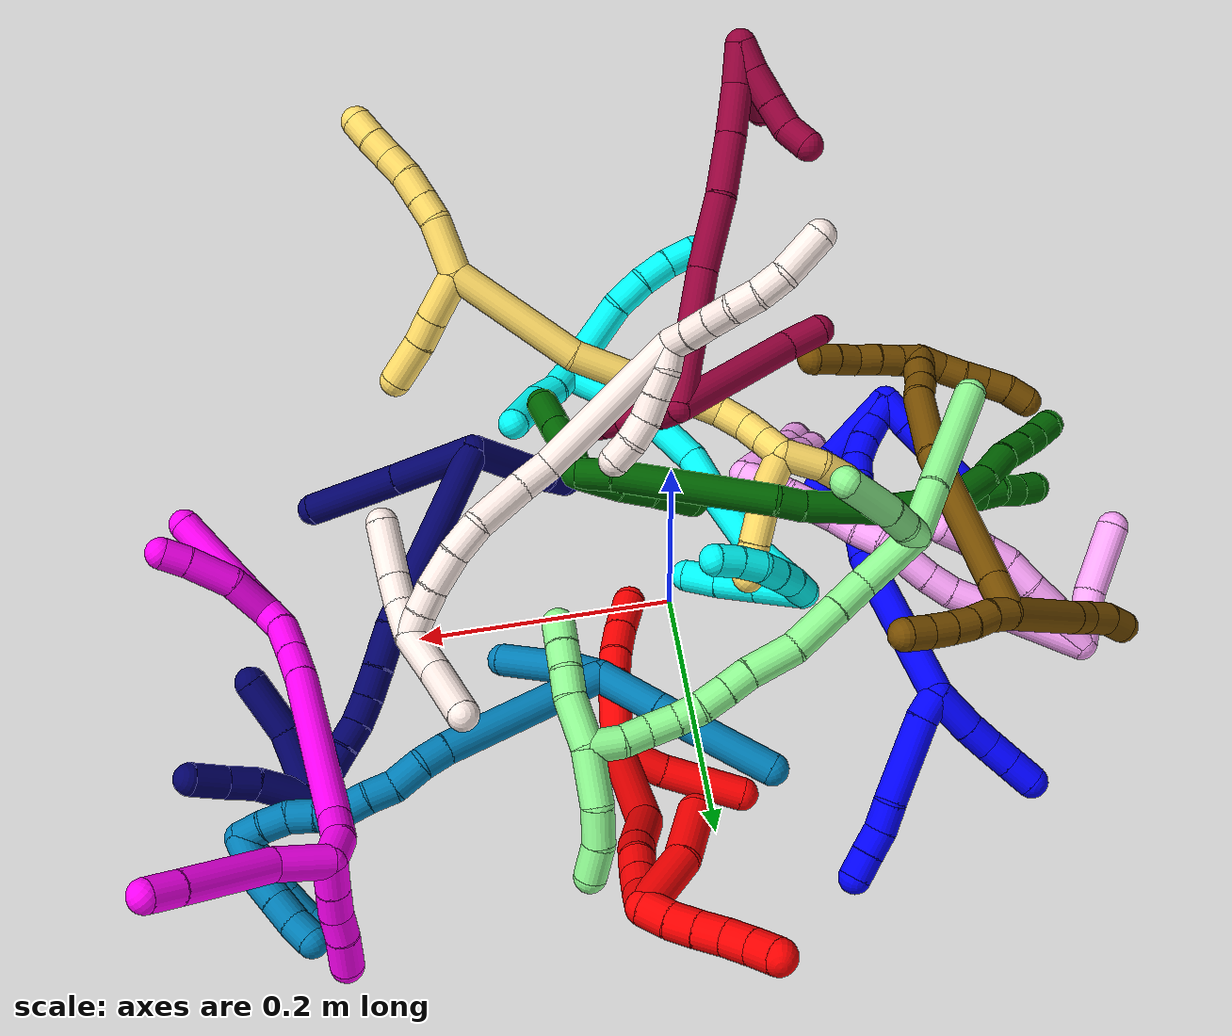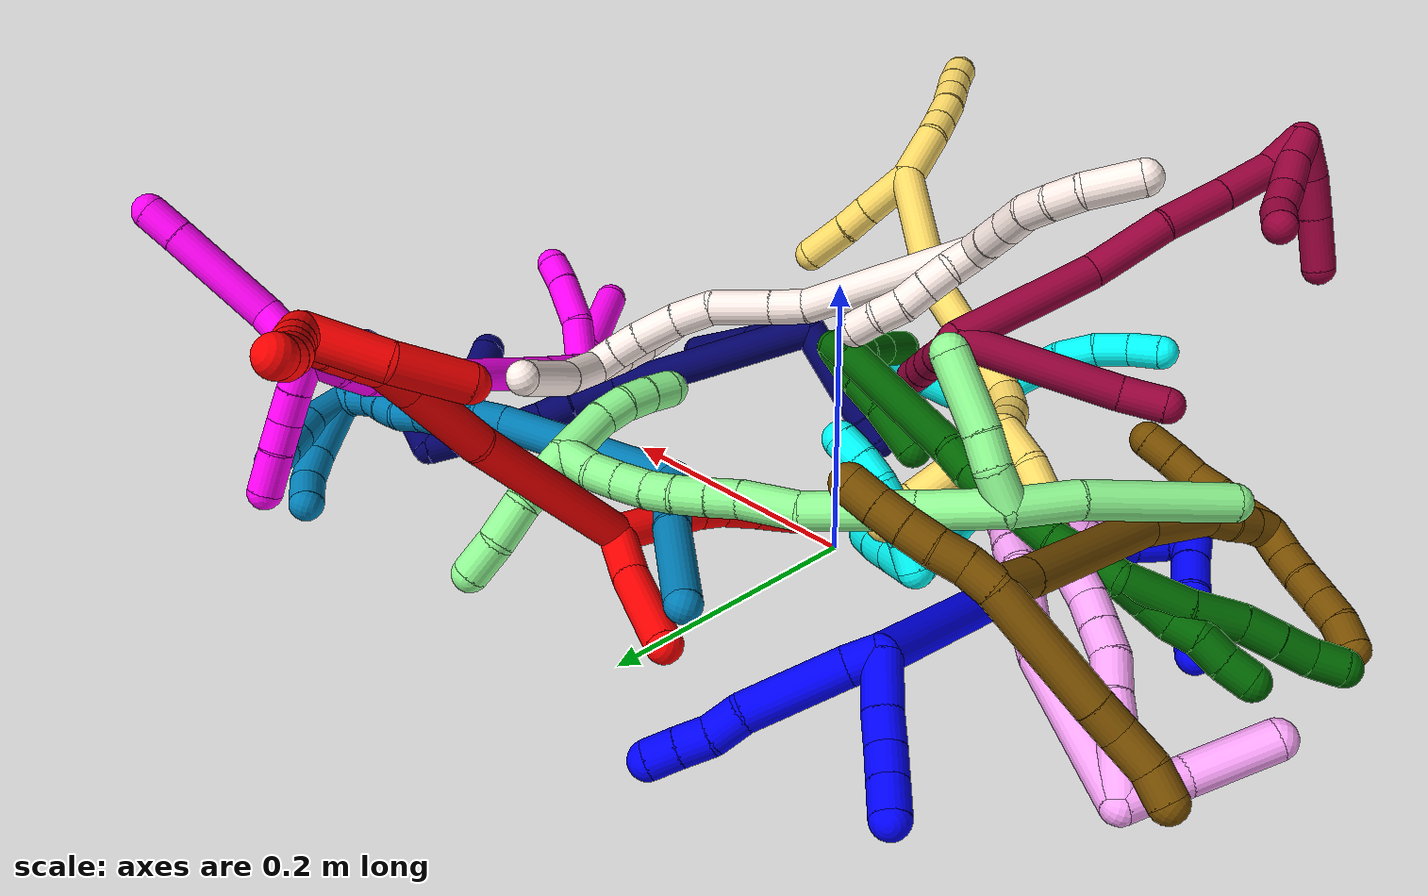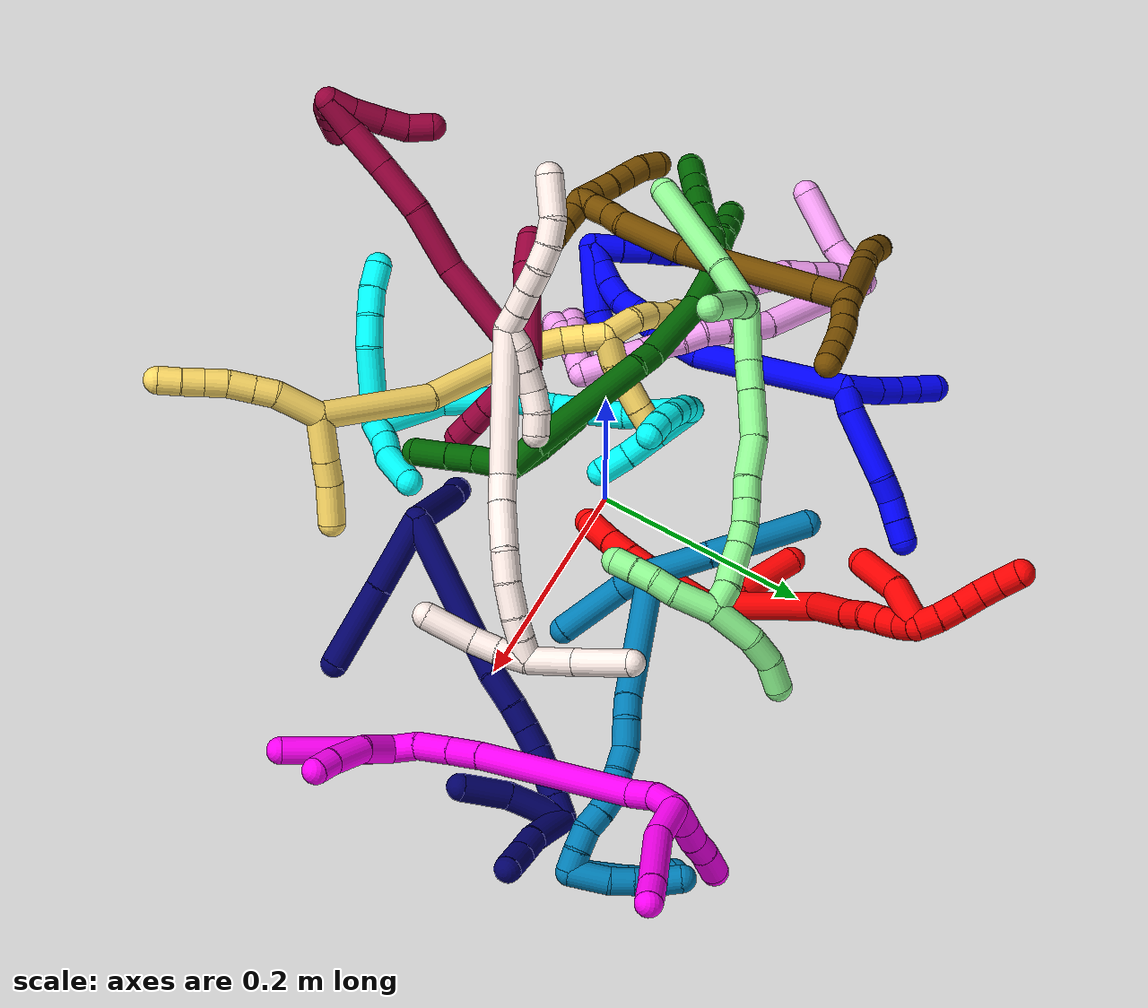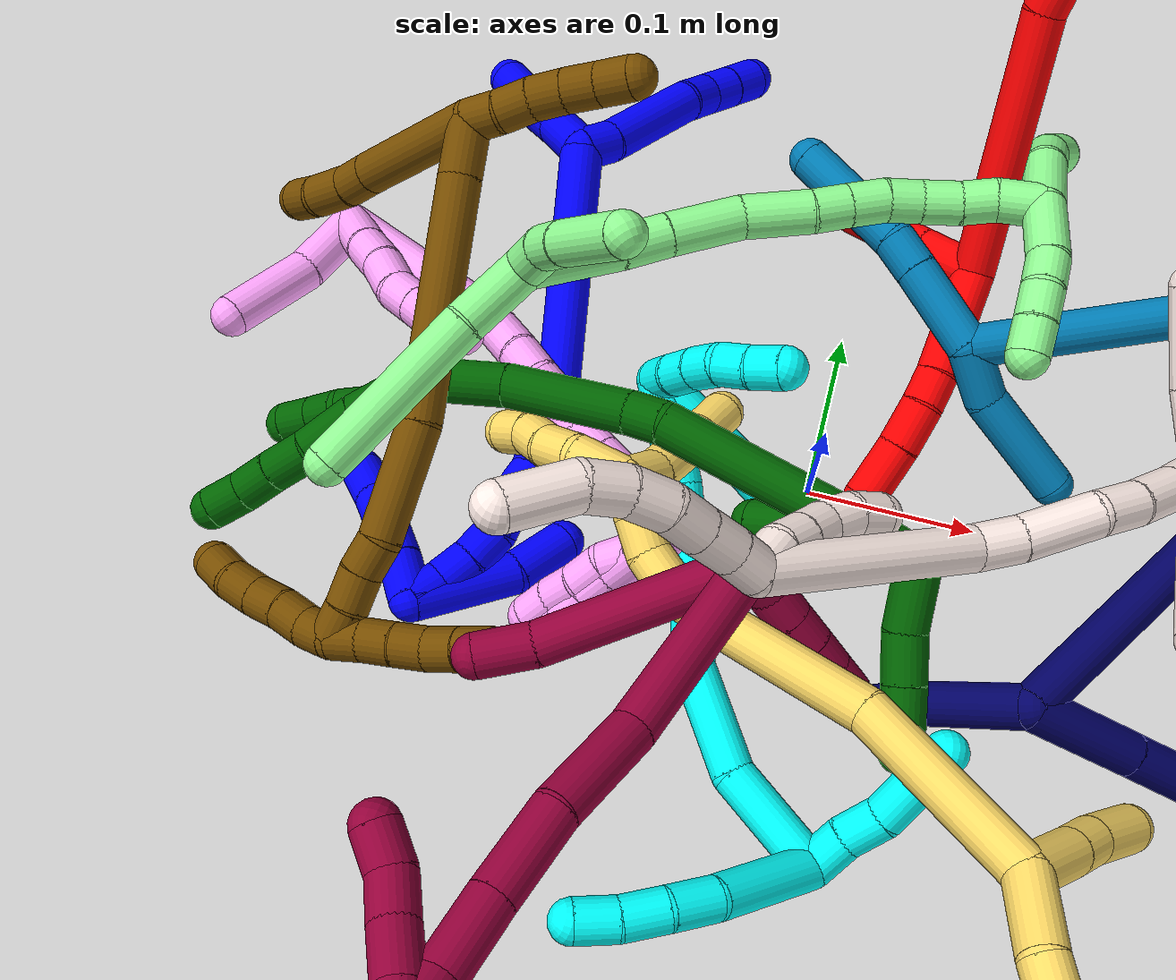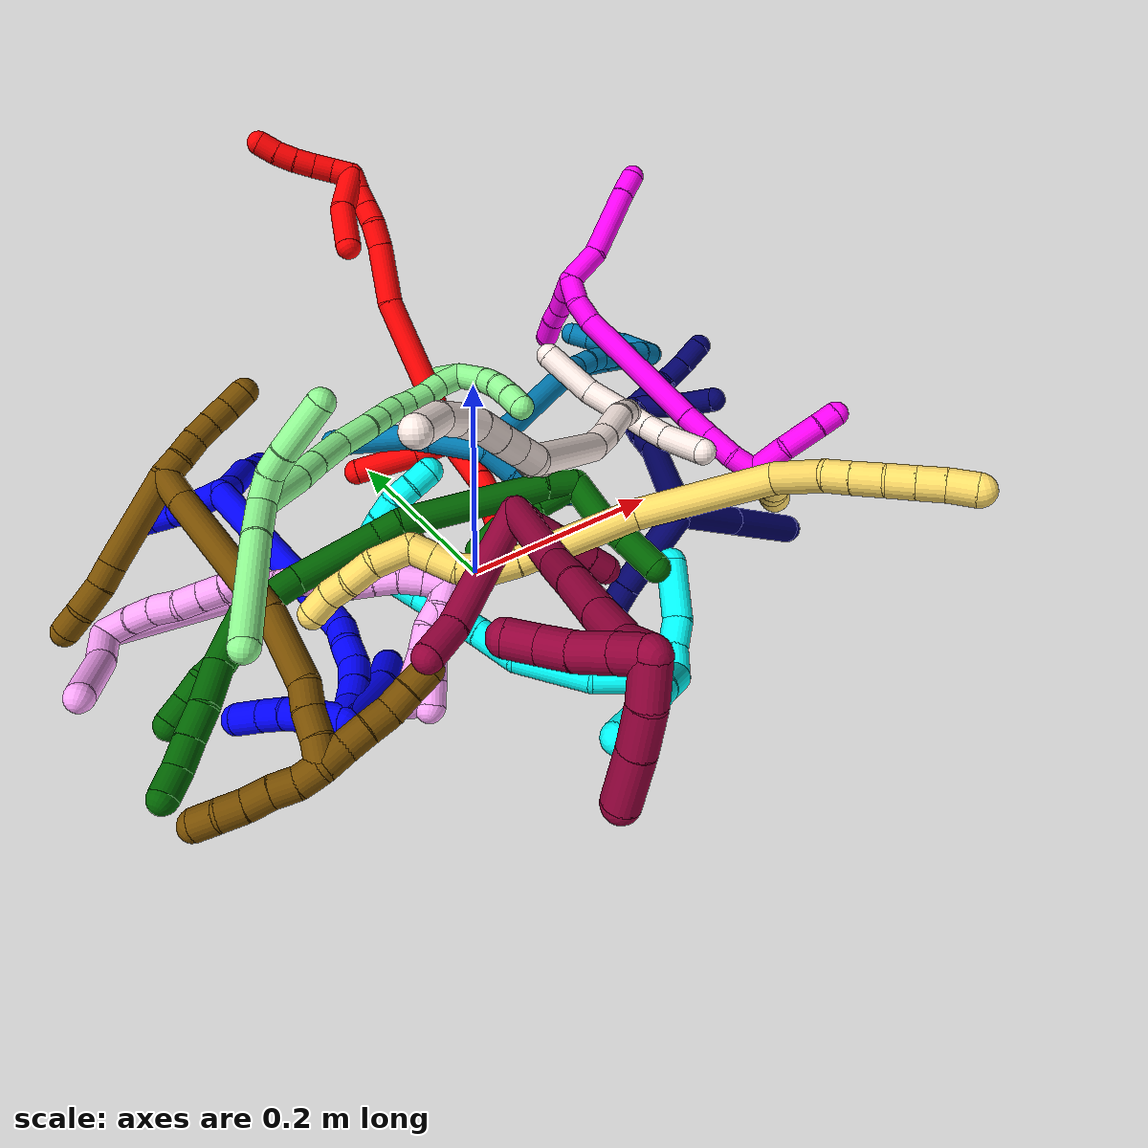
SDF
<sdf version="1.7">
 <world name="default">
  <plugin name="TubeGeneratorPlugin" filename="libtube_generator_plugin.so"/>
  <model name="photoneo_s_sensor">
   <static>1</static>
   <pose>0 0 2 1.57079 1.57079 3.14159</pose>
   <link name="link">
    <inertial><mass>0.1</mass></inertial>
    <sensor name="sensor" type="depth">
     <update_rate>30</update_rate>
     <camera>
      <horizontal_fov>1.22</horizontal_fov>
      <image><width>1920</width><height>1200</height><format>B8G8R8</format></image>
      <clip><near>0.1</near><far>4</far></clip>
      <depth_camera><output>points</output></depth_camera>
     </camera>
     <plugin name="camera_plugin" filename="libgazebo_ros_depth_camera.so">
      <baseline>0.2</baseline>
      <alwaysOn>1</alwaysOn>
      <updateRate>0.0</updateRate>
      <cameraName>camera_ir</cameraName>
      <imageTopicName>/camera/color/image_raw</imageTopicName>
      <cameraInfoTopicName>/camera/color/camera_info</cameraInfoTopicName>
      <depthImageTopicName>/camera/depth/image_raw</depthImageTopicName>
      <depthImageCameraInfoTopicName>/camera/depth/camera_info</depthImageCameraInfoTopicName>
      <pointCloudTopicName>/camera/depth/points</pointCloudTopicName>
      <frameName>fr_optical</frameName>
      <pointCloudCutoff>0.1</pointCloudCutoff>
      <pointCloudCutoffMax>2.0</pointCloudCutoffMax>
      <distortionK1>0</distortionK1>
      <distortionK2>0</distortionK2>
      <distortionK3>0</distortionK3>
      <distortionT1>0</distortionT1>
      <distortionT2>0</distortionT2>
      <CxPrime>0</CxPrime>
      <Cx>0</Cx>
      <Cy>0</Cy>
      <focalLength>0</focalLength>
      <hackBaseline>0</hackBaseline>
     </plugin>
    </sensor>
   </link>
  </model>
  <gravity>0 0 -9.8</gravity>
  <magnetic_field>6e-06 2.3e-05 -4.2e-05</magnetic_field>
  <atmosphere type="adiabatic"/>
  <physics name="default_physics" default="0" type="ode">
   <max_step_size>0.003</max_step_size>
   <real_time_factor>1</real_time_factor>
   <real_time_update_rate>1000</real_time_update_rate>
   <max_contacts>10000</max_contacts>
   <ode>
    <solver>
     <type>quick</type>
     <iters>100</iters>
     <sor>1.3</sor>
     <use_dynamic_moi_rescaling>0</use_dynamic_moi_rescaling>
    </solver>
    <constraints>
     <contact_max_correcting_vel>0</contact_max_correcting_vel>
     <contact_surface_layer>0.001</contact_surface_layer>
     <cfm>0</cfm>
     <erp>0.2</erp>
    </constraints>
   </ode>
  </physics>
  <scene><ambient>0.4 0.4 0.4 1</ambient><background>0.7 0.7 0.7 1</background><shadows>0</shadows></scene>
  <audio><device>default</device></audio>
  <spherical_coordinates>
   <surface_model>EARTH_WGS84</surface_model>
   <latitude_deg>0</latitude_deg>
   <longitude_deg>0</longitude_deg>
   <elevation>0</elevation>
   <heading_deg>0</heading_deg>
  </spherical_coordinates>
  <model name="bin">
   <static>1</static>
   <link name="bottom">
    <collision name="collision-bottom">
     <pose>0 0 -0.01 0 -0 0</pose>
     <geometry><box><size>0.8 0.6 0.02</size></box></geometry>
     <surface>
      <friction><ode><mu>100</mu><mu2>100</mu2></ode></friction>
      <contact><collide_bitmask>65535</collide_bitmask></contact>
     </surface>
    </collision>
   </link>
   <link name="west_wall">
    <collision name="collision-west_wall">
     <pose>-0.41 0 0.1 0 -0 0</pose>
     <geometry><box><size>0.02 0.6 0.2</size></box></geometry>
     <surface>
      <friction><ode><mu>100</mu><mu2>100</mu2></ode></friction>
      <contact><collide_bitmask>65535</collide_bitmask></contact>
     </surface>
    </collision>
   </link>
   <link name="east_wall">
    <collision name="collision-east_wall">
     <pose>0.41 0 0.1 0 -0 0</pose>
     <geometry><box><size>0.02 0.6 0.2</size></box></geometry>
     <surface>
      <friction><ode><mu>100</mu><mu2>100</mu2></ode></friction>
      <contact><collide_bitmask>65535</collide_bitmask></contact>
     </surface>
    </collision>
   </link>
   <link name="south_wall">
    <collision name="collision-south_wall">
     <pose>0 -0.31 0.1 0 -0 0</pose>
     <geometry><box><size>0.8 0.02 0.2</size></box></geometry>
     <surface>
      <friction><ode><mu>100</mu><mu2>100</mu2></ode></friction>
      <contact><collide_bitmask>65535</collide_bitmask></contact>
     </surface>
    </collision>
   </link>
   <link name="north_wall">
    <collision name="collision-north_wall">
     <pose>0 0.31 0.1 0 -0 0</pose>
     <geometry><box><size>0.8 0.02 0.2</size></box></geometry>
     <surface>
      <friction><ode><mu>100</mu><mu2>100</mu2></ode></friction>
      <contact><collide_bitmask>65535</collide_bitmask></contact>
     </surface>
    </collision>
   </link>
  </model>
  <model name="1">
   <static>0</static>
   <link name="1">
    <collision name="collision-cylinder-e_1_2_8">
     <pose>0.001547 0.010547 0.000785 -1.49654 0.14526 -0.134888</pose>
     <geometry><cylinder><radius>0.0125</radius><length>0.021377</length></cylinder></geometry>
     <surface>
      <friction><ode><mu>1.16</mu><mu2>1.16</mu2><slip1>0</slip1><slip2>0</slip2></ode></friction>
      <contact><ode><kp>1e+06</kp><kd>1</kd><max_vel>0</max_vel><min_depth>0.001</min_depth></ode></contact>
     </surface>
    </collision>
    <visual name="visual-cylinder-e_1_2_8">
     <pose>0.001547 0.010547 0.000785 -1.49654 0.14526 -0.134888</pose>
     <geometry><cylinder><radius>0.0125</radius><length>0.021377</length></cylinder></geometry>
     <material><ambient>0 0 1 1</ambient></material>
    </visual>
    <collision name="collision-cylinder-e_2_8_9">
     <pose>0.006461 0.053044 0.009933 -1.31478 0.101599 -0.078455</pose>
     <geometry><cylinder><radius>0.0125</radius><length>0.066396</length></cylinder></geometry>
     <surface>
      <friction><ode><mu>1.16</mu><mu2>1.16</mu2><slip1>0</slip1><slip2>0</slip2></ode></friction>
      <contact><ode><kp>1e+06</kp><kd>1</kd><max_vel>0</max_vel><min_depth>0.001</min_depth></ode></contact>
     </surface>
    </collision>
    <visual name="visual-cylinder-e_2_8_9">
     <pose>0.006461 0.053044 0.009933 -1.31478 0.101599 -0.078455</pose>
     <geometry><cylinder><radius>0.0125</radius><length>0.066396</length></cylinder></geometry>
     <material><ambient>0 0 1 1</ambient></material>
    </visual>
    <collision name="collision-cylinder-e_3_9_10">
     <pose>0.008531 0.095867 0.019989 -1.41633 -0.117321 0.100497</pose>
     <geometry><cylinder><radius>0.0125</radius><length>0.022161</length></cylinder></geometry>
     <surface>
      <friction><ode><mu>1.16</mu><mu2>1.16</mu2><slip1>0</slip1><slip2>0</slip2></ode></friction>
      <contact><ode><kp>1e+06</kp><kd>1</kd><max_vel>0</max_vel><min_depth>0.001</min_depth></ode></contact>
     </surface>
    </collision>
    <visual name="visual-cylinder-e_3_9_10">
     <pose>0.008531 0.095867 0.019989 -1.41633 -0.117321 0.100497</pose>
     <geometry><cylinder><radius>0.0125</radius><length>0.022161</length></cylinder></geometry>
     <material><ambient>0 0 1 1</ambient></material>
    </visual>
    <collision name="collision-cylinder-e_4_10_11">
     <pose>0.008712 0.116561 0.022868 -1.45067 0.14824 -0.131474</pose>
     <geometry><cylinder><radius>0.0125</radius><length>0.020004</length></cylinder></geometry>
     <surface>
      <friction><ode><mu>1.16</mu><mu2>1.16</mu2><slip1>0</slip1><slip2>0</slip2></ode></friction>
      <contact><ode><kp>1e+06</kp><kd>1</kd><max_vel>0</max_vel><min_depth>0.001</min_depth></ode></contact>
     </surface>
    </collision>
    <visual name="visual-cylinder-e_4_10_11">
     <pose>0.008712 0.116561 0.022868 -1.45067 0.14824 -0.131474</pose>
     <geometry><cylinder><radius>0.0125</radius><length>0.020004</length></cylinder></geometry>
     <material><ambient>0 0 1 1</ambient></material>
    </visual>
    <collision name="collision-cylinder-e_5_11_6">
     <pose>0.011334 0.136266 0.025331 -1.44221 0.114364 -0.100554</pose>
     <geometry><cylinder><radius>0.0125</radius><length>0.020063</length></cylinder></geometry>
     <surface>
      <friction><ode><mu>1.16</mu><mu2>1.16</mu2><slip1>0</slip1><slip2>0</slip2></ode></friction>
      <contact><ode><kp>1e+06</kp><kd>1</kd><max_vel>0</max_vel><min_depth>0.001</min_depth></ode></contact>
     </surface>
    </collision>
    <visual name="visual-cylinder-e_5_11_6">
     <pose>0.011334 0.136266 0.025331 -1.44221 0.114364 -0.100554</pose>
     <geometry><cylinder><radius>0.0125</radius><length>0.020063</length></cylinder></geometry>
     <material><ambient>0 0 1 1</ambient></material>
    </visual>
    <collision name="collision-cylinder-e_1_2_12">
     <pose>-0.012986 0.005407 0.010797 -0.464279 -0.821711 0.205252</pose>
     <geometry><cylinder><radius>0.0125</radius><length>0.035466</length></cylinder></geometry>
     <surface>
      <friction><ode><mu>1.16</mu><mu2>1.16</mu2><slip1>0</slip1><slip2>0</slip2></ode></friction>
      <contact><ode><kp>1e+06</kp><kd>1</kd><max_vel>0</max_vel><min_depth>0.001</min_depth></ode></contact>
     </surface>
    </collision>
    <visual name="visual-cylinder-e_1_2_12">
     <pose>-0.012986 0.005407 0.010797 -0.464279 -0.821711 0.205252</pose>
     <geometry><cylinder><radius>0.0125</radius><length>0.035466</length></cylinder></geometry>
     <material><ambient>0 0 1 1</ambient></material>
    </visual>
    <collision name="collision-cylinder-e_2_12_13">
     <pose>-0.034023 0.013208 0.028408 -0.337798 -0.839676 0.151943</pose>
     <geometry><cylinder><radius>0.0125</radius><length>0.021629</length></cylinder></geometry>
     <surface>
      <friction><ode><mu>1.16</mu><mu2>1.16</mu2><slip1>0</slip1><slip2>0</slip2></ode></friction>
      <contact><ode><kp>1e+06</kp><kd>1</kd><max_vel>0</max_vel><min_depth>0.001</min_depth></ode></contact>
     </surface>
    </collision>
    <visual name="visual-cylinder-e_2_12_13">
     <pose>-0.034023 0.013208 0.028408 -0.337798 -0.839676 0.151943</pose>
     <geometry><cylinder><radius>0.0125</radius><length>0.021629</length></cylinder></geometry>
     <material><ambient>0 0 1 1</ambient></material>
    </visual>
    <collision name="collision-cylinder-e_3_13_14">
     <pose>-0.049011 0.01761 0.042577 -0.266716 -0.73816 0.10369</pose>
     <geometry><cylinder><radius>0.0125</radius><length>0.020618</length></cylinder></geometry>
     <surface>
      <friction><ode><mu>1.16</mu><mu2>1.16</mu2><slip1>0</slip1><slip2>0</slip2></ode></friction>
      <contact><ode><kp>1e+06</kp><kd>1</kd><max_vel>0</max_vel><min_depth>0.001</min_depth></ode></contact>
     </surface>
    </collision>
    <visual name="visual-cylinder-e_3_13_14">
     <pose>-0.049011 0.01761 0.042577 -0.266716 -0.73816 0.10369</pose>
     <geometry><cylinder><radius>0.0125</radius><length>0.020618</length></cylinder></geometry>
     <material><ambient>0 0 1 1</ambient></material>
    </visual>
    <collision name="collision-cylinder-e_4_14_5">
     <pose>-0.063406 0.02178 0.057926 -0.263881 -0.733169 0.101818</pose>
     <geometry><cylinder><radius>0.0125</radius><length>0.022287</length></cylinder></geometry>
     <surface>
      <friction><ode><mu>1.16</mu><mu2>1.16</mu2><slip1>0</slip1><slip2>0</slip2></ode></friction>
      <contact><ode><kp>1e+06</kp><kd>1</kd><max_vel>0</max_vel><min_depth>0.001</min_depth></ode></contact>
     </surface>
    </collision>
    <visual name="visual-cylinder-e_4_14_5">
     <pose>-0.063406 0.02178 0.057926 -0.263881 -0.733169 0.101818</pose>
     <geometry><cylinder><radius>0.0125</radius><length>0.022287</length></cylinder></geometry>
     <material><ambient>0 0 1 1</ambient></material>
    </visual>
    <collision name="collision-cylinder-e_1_2_15">
     <pose>-0.012008 -0.025924 -0.067508 2.77495 -0.164554 -0.836999</pose>
     <geometry><cylinder><radius>0.0125</radius><length>0.14661</length></cylinder></geometry>
     <surface>
      <friction><ode><mu>1.16</mu><mu2>1.16</mu2><slip1>0</slip1><slip2>0</slip2></ode></friction>
      <contact><ode><kp>1e+06</kp><kd>1</kd><max_vel>0</max_vel><min_depth>0.001</min_depth></ode></contact>
     </surface>
    </collision>
    <visual name="visual-cylinder-e_1_2_15">
     <pose>-0.012008 -0.025924 -0.067508 2.77495 -0.164554 -0.836999</pose>
     <geometry><cylinder><radius>0.0125</radius><length>0.14661</length></cylinder></geometry>
     <material><ambient>0 0 1 1</ambient></material>
    </visual>
    <collision name="collision-cylinder-e_2_15_16">
     <pose>-0.025453 -0.067499 -0.15359 2.44137 -0.05906 -0.161434</pose>
     <geometry><cylinder><radius>0.0125</radius><length>0.048662</length></cylinder></geometry>
     <surface>
      <friction><ode><mu>1.16</mu><mu2>1.16</mu2><slip1>0</slip1><slip2>0</slip2></ode></friction>
      <contact><ode><kp>1e+06</kp><kd>1</kd><max_vel>0</max_vel><min_depth>0.001</min_depth></ode></contact>
     </surface>
    </collision>
    <visual name="visual-cylinder-e_2_15_16">
     <pose>-0.025453 -0.067499 -0.15359 2.44137 -0.05906 -0.161434</pose>
     <geometry><cylinder><radius>0.0125</radius><length>0.048662</length></cylinder></geometry>
     <material><ambient>0 0 1 1</ambient></material>
    </visual>
    <collision name="collision-cylinder-e_3_16_17">
     <pose>-0.029116 -0.091914 -0.178459 2.19373 -0.20354 -0.393059</pose>
     <geometry><cylinder><radius>0.0125</radius><length>0.022034</length></cylinder></geometry>
     <surface>
      <friction><ode><mu>1.16</mu><mu2>1.16</mu2><slip1>0</slip1><slip2>0</slip2></ode></friction>
      <contact><ode><kp>1e+06</kp><kd>1</kd><max_vel>0</max_vel><min_depth>0.001</min_depth></ode></contact>
     </surface>
    </collision>
    <visual name="visual-cylinder-e_3_16_17">
     <pose>-0.029116 -0.091914 -0.178459 2.19373 -0.20354 -0.393059</pose>
     <geometry><cylinder><radius>0.0125</radius><length>0.022034</length></cylinder></geometry>
     <material><ambient>0 0 1 1</ambient></material>
    </visual>
    <collision name="collision-cylinder-e_4_17_18">
     <pose>-0.034888 -0.106316 -0.192334 2.50195 -0.358988 -1.0024</pose>
     <geometry><cylinder><radius>0.0125</radius><length>0.020182</length></cylinder></geometry>
     <surface>
      <friction><ode><mu>1.16</mu><mu2>1.16</mu2><slip1>0</slip1><slip2>0</slip2></ode></friction>
      <contact><ode><kp>1e+06</kp><kd>1</kd><max_vel>0</max_vel><min_depth>0.001</min_depth></ode></contact>
     </surface>
    </collision>
    <visual name="visual-cylinder-e_4_17_18">
     <pose>-0.034888 -0.106316 -0.192334 2.50195 -0.358988 -1.0024</pose>
     <geometry><cylinder><radius>0.0125</radius><length>0.020182</length></cylinder></geometry>
     <material><ambient>0 0 1 1</ambient></material>
    </visual>
    <collision name="collision-cylinder-e_5_18_19">
     <pose>-0.042573 -0.120028 -0.204996 2.13265 -0.409461 -0.719427</pose>
     <geometry><cylinder><radius>0.0125</radius><length>0.020798</length></cylinder></geometry>
     <surface>
      <friction><ode><mu>1.16</mu><mu2>1.16</mu2><slip1>0</slip1><slip2>0</slip2></ode></friction>
      <contact><ode><kp>1e+06</kp><kd>1</kd><max_vel>0</max_vel><min_depth>0.001</min_depth></ode></contact>
     </surface>
    </collision>
    <visual name="visual-cylinder-e_5_18_19">
     <pose>-0.042573 -0.120028 -0.204996 2.13265 -0.409461 -0.719427</pose>
     <geometry><cylinder><radius>0.0125</radius><length>0.020798</length></cylinder></geometry>
     <material><ambient>0 0 1 1</ambient></material>
    </visual>
    <collision name="collision-cylinder-e_6_19_20">
     <pose>-0.051655 -0.136768 -0.213831 1.97942 -0.482092 -0.716352</pose>
     <geometry><cylinder><radius>0.0125</radius><length>0.02132</length></cylinder></geometry>
     <surface>
      <friction><ode><mu>1.16</mu><mu2>1.16</mu2><slip1>0</slip1><slip2>0</slip2></ode></friction>
      <contact><ode><kp>1e+06</kp><kd>1</kd><max_vel>0</max_vel><min_depth>0.001</min_depth></ode></contact>
     </surface>
    </collision>
    <visual name="visual-cylinder-e_6_19_20">
     <pose>-0.051655 -0.136768 -0.213831 1.97942 -0.482092 -0.716352</pose>
     <geometry><cylinder><radius>0.0125</radius><length>0.02132</length></cylinder></geometry>
     <material><ambient>0 0 1 1</ambient></material>
    </visual>
    <collision name="collision-cylinder-e_7_20_1">
     <pose>-0.059343 -0.154958 -0.219985 1.81788 -0.272601 -0.348511</pose>
     <geometry><cylinder><radius>0.0125</radius><length>0.020394</length></cylinder></geometry>
     <surface>
      <friction><ode><mu>1.16</mu><mu2>1.16</mu2><slip1>0</slip1><slip2>0</slip2></ode></friction>
      <contact><ode><kp>1e+06</kp><kd>1</kd><max_vel>0</max_vel><min_depth>0.001</min_depth></ode></contact>
     </surface>
    </collision>
    <visual name="visual-cylinder-e_7_20_1">
     <pose>-0.059343 -0.154958 -0.219985 1.81788 -0.272601 -0.348511</pose>
     <geometry><cylinder><radius>0.0125</radius><length>0.020394</length></cylinder></geometry>
     <material><ambient>0 0 1 1</ambient></material>
    </visual>
    <collision name="collision-cylinder-e_1_1_21">
     <pose>-0.067777 -0.160272 -0.210864 -0.350133 -0.434167 0.077984</pose>
     <geometry><cylinder><radius>0.0125</radius><length>0.027044</length></cylinder></geometry>
     <surface>
      <friction><ode><mu>1.16</mu><mu2>1.16</mu2><slip1>0</slip1><slip2>0</slip2></ode></friction>
      <contact><ode><kp>1e+06</kp><kd>1</kd><max_vel>0</max_vel><min_depth>0.001</min_depth></ode></contact>
     </surface>
    </collision>
    <visual name="visual-cylinder-e_1_1_21">
     <pose>-0.067777 -0.160272 -0.210864 -0.350133 -0.434167 0.077984</pose>
     <geometry><cylinder><radius>0.0125</radius><length>0.027044</length></cylinder></geometry>
     <material><ambient>0 0 1 1</ambient></material>
    </visual>
    <collision name="collision-cylinder-e_2_21_22">
     <pose>-0.079647 -0.152789 -0.188425 -0.291475 -0.497053 0.074462</pose>
     <geometry><cylinder><radius>0.0125</radius><length>0.025932</length></cylinder></geometry>
     <surface>
      <friction><ode><mu>1.16</mu><mu2>1.16</mu2><slip1>0</slip1><slip2>0</slip2></ode></friction>
      <contact><ode><kp>1e+06</kp><kd>1</kd><max_vel>0</max_vel><min_depth>0.001</min_depth></ode></contact>
     </surface>
    </collision>
    <visual name="visual-cylinder-e_2_21_22">
     <pose>-0.079647 -0.152789 -0.188425 -0.291475 -0.497053 0.074462</pose>
     <geometry><cylinder><radius>0.0125</radius><length>0.025932</length></cylinder></geometry>
     <material><ambient>0 0 1 1</ambient></material>
    </visual>
    <collision name="collision-cylinder-e_3_22_23">
     <pose>-0.09234 -0.145996 -0.169663 -0.421574 -0.64806 0.143482</pose>
     <geometry><cylinder><radius>0.0125</radius><length>0.021569</length></cylinder></geometry>
     <surface>
      <friction><ode><mu>1.16</mu><mu2>1.16</mu2><slip1>0</slip1><slip2>0</slip2></ode></friction>
      <contact><ode><kp>1e+06</kp><kd>1</kd><max_vel>0</max_vel><min_depth>0.001</min_depth></ode></contact>
     </surface>
    </collision>
    <visual name="visual-cylinder-e_3_22_23">
     <pose>-0.09234 -0.145996 -0.169663 -0.421574 -0.64806 0.143482</pose>
     <geometry><cylinder><radius>0.0125</radius><length>0.021569</length></cylinder></geometry>
     <material><ambient>0 0 1 1</ambient></material>
    </visual>
    <collision name="collision-cylinder-e_4_23_4">
     <pose>-0.106879 -0.139242 -0.152488 -0.333778 -0.682655 0.119539</pose>
     <geometry><cylinder><radius>0.0125</radius><length>0.025455</length></cylinder></geometry>
     <surface>
      <friction><ode><mu>1.16</mu><mu2>1.16</mu2><slip1>0</slip1><slip2>0</slip2></ode></friction>
      <contact><ode><kp>1e+06</kp><kd>1</kd><max_vel>0</max_vel><min_depth>0.001</min_depth></ode></contact>
     </surface>
    </collision>
    <visual name="visual-cylinder-e_4_23_4">
     <pose>-0.106879 -0.139242 -0.152488 -0.333778 -0.682655 0.119539</pose>
     <geometry><cylinder><radius>0.0125</radius><length>0.025455</length></cylinder></geometry>
     <material><ambient>0 0 1 1</ambient></material>
    </visual>
    <collision name="collision-cylinder-e_1_1_24">
     <pose>-0.052356 -0.13441 -0.224008 -1.62464 0.312595 -0.329595</pose>
     <geometry><cylinder><radius>0.0125</radius><length>0.063295</length></cylinder></geometry>
     <surface>
      <friction><ode><mu>1.16</mu><mu2>1.16</mu2><slip1>0</slip1><slip2>0</slip2></ode></friction>
      <contact><ode><kp>1e+06</kp><kd>1</kd><max_vel>0</max_vel><min_depth>0.001</min_depth></ode></contact>
     </surface>
    </collision>
    <visual name="visual-cylinder-e_1_1_24">
     <pose>-0.052356 -0.13441 -0.224008 -1.62464 0.312595 -0.329595</pose>
     <geometry><cylinder><radius>0.0125</radius><length>0.063295</length></cylinder></geometry>
     <material><ambient>0 0 1 1</ambient></material>
    </visual>
    <collision name="collision-cylinder-e_2_24_3">
     <pose>-0.039586 -0.086741 -0.221402 -1.33505 0.16629 -0.13119</pose>
     <geometry><cylinder><radius>0.0125</radius><length>0.036705</length></cylinder></geometry>
     <surface>
      <friction><ode><mu>1.16</mu><mu2>1.16</mu2><slip1>0</slip1><slip2>0</slip2></ode></friction>
      <contact><ode><kp>1e+06</kp><kd>1</kd><max_vel>0</max_vel><min_depth>0.001</min_depth></ode></contact>
     </surface>
    </collision>
    <visual name="visual-cylinder-e_2_24_3">
     <pose>-0.039586 -0.086741 -0.221402 -1.33505 0.16629 -0.13119</pose>
     <geometry><cylinder><radius>0.0125</radius><length>0.036705</length></cylinder></geometry>
     <material><ambient>0 0 1 1</ambient></material>
    </visual>
    <collision name="collision-sphere-3">
     <pose>-0.036548 -0.069142 -0.217174 0 -0 0</pose>
     <geometry><sphere><radius>0.0125</radius></sphere></geometry>
     <surface>
      <friction><ode><mu>1.16</mu><mu2>1.16</mu2><slip1>0</slip1><slip2>0</slip2></ode></friction>
      <contact><ode><kp>1e+06</kp><kd>1</kd><max_vel>0</max_vel><min_depth>0.001</min_depth></ode></contact>
     </surface>
    </collision>
    <visual name="visual-sphere-3">
     <pose>-0.036548 -0.069142 -0.217174 0 -0 0</pose>
     <geometry><sphere><radius>0.0125</radius></sphere></geometry>
     <material><ambient>0 0 1 1</ambient></material>
    </visual>
    <collision name="collision-sphere-24">
     <pose>-0.042623 -0.10434 -0.225629 0 -0 0</pose>
     <geometry><sphere><radius>0.0125</radius></sphere></geometry>
     <surface>
      <friction><ode><mu>1.16</mu><mu2>1.16</mu2><slip1>0</slip1><slip2>0</slip2></ode></friction>
      <contact><ode><kp>1e+06</kp><kd>1</kd><max_vel>0</max_vel><min_depth>0.001</min_depth></ode></contact>
     </surface>
    </collision>
    <visual name="visual-sphere-24">
     <pose>-0.042623 -0.10434 -0.225629 0 -0 0</pose>
     <geometry><sphere><radius>0.0125</radius></sphere></geometry>
     <material><ambient>0 0 1 1</ambient></material>
    </visual>
    <collision name="collision-sphere-4">
     <pose>-0.114908 -0.136007 -0.143157 0 -0 0</pose>
     <geometry><sphere><radius>0.0125</radius></sphere></geometry>
     <surface>
      <friction><ode><mu>1.16</mu><mu2>1.16</mu2><slip1>0</slip1><slip2>0</slip2></ode></friction>
      <contact><ode><kp>1e+06</kp><kd>1</kd><max_vel>0</max_vel><min_depth>0.001</min_depth></ode></contact>
     </surface>
    </collision>
    <visual name="visual-sphere-4">
     <pose>-0.114908 -0.136007 -0.143157 0 -0 0</pose>
     <geometry><sphere><radius>0.0125</radius></sphere></geometry>
     <material><ambient>0 0 1 1</ambient></material>
    </visual>
    <collision name="collision-sphere-23">
     <pose>-0.09885 -0.142477 -0.161818 0 -0 0</pose>
     <geometry><sphere><radius>0.0125</radius></sphere></geometry>
     <surface>
      <friction><ode><mu>1.16</mu><mu2>1.16</mu2><slip1>0</slip1><slip2>0</slip2></ode></friction>
      <contact><ode><kp>1e+06</kp><kd>1</kd><max_vel>0</max_vel><min_depth>0.001</min_depth></ode></contact>
     </surface>
    </collision>
    <visual name="visual-sphere-23">
     <pose>-0.09885 -0.142477 -0.161818 0 -0 0</pose>
     <geometry><sphere><radius>0.0125</radius></sphere></geometry>
     <material><ambient>0 0 1 1</ambient></material>
    </visual>
    <collision name="collision-sphere-22">
     <pose>-0.08583 -0.149514 -0.177508 0 -0 0</pose>
     <geometry><sphere><radius>0.0125</radius></sphere></geometry>
     <surface>
      <friction><ode><mu>1.16</mu><mu2>1.16</mu2><slip1>0</slip1><slip2>0</slip2></ode></friction>
      <contact><ode><kp>1e+06</kp><kd>1</kd><max_vel>0</max_vel><min_depth>0.001</min_depth></ode></contact>
     </surface>
    </collision>
    <visual name="visual-sphere-22">
     <pose>-0.08583 -0.149514 -0.177508 0 -0 0</pose>
     <geometry><sphere><radius>0.0125</radius></sphere></geometry>
     <material><ambient>0 0 1 1</ambient></material>
    </visual>
    <collision name="collision-sphere-21">
     <pose>-0.073465 -0.156064 -0.199341 0 -0 0</pose>
     <geometry><sphere><radius>0.0125</radius></sphere></geometry>
     <surface>
      <friction><ode><mu>1.16</mu><mu2>1.16</mu2><slip1>0</slip1><slip2>0</slip2></ode></friction>
      <contact><ode><kp>1e+06</kp><kd>1</kd><max_vel>0</max_vel><min_depth>0.001</min_depth></ode></contact>
     </surface>
    </collision>
    <visual name="visual-sphere-21">
     <pose>-0.073465 -0.156064 -0.199341 0 -0 0</pose>
     <geometry><sphere><radius>0.0125</radius></sphere></geometry>
     <material><ambient>0 0 1 1</ambient></material>
    </visual>
    <collision name="collision-sphere-1">
     <pose>-0.062088 -0.16448 -0.222387 0 -0 0</pose>
     <geometry><sphere><radius>0.0125</radius></sphere></geometry>
     <surface>
      <friction><ode><mu>1.16</mu><mu2>1.16</mu2><slip1>0</slip1><slip2>0</slip2></ode></friction>
      <contact><ode><kp>1e+06</kp><kd>1</kd><max_vel>0</max_vel><min_depth>0.001</min_depth></ode></contact>
     </surface>
    </collision>
    <visual name="visual-sphere-1">
     <pose>-0.062088 -0.16448 -0.222387 0 -0 0</pose>
     <geometry><sphere><radius>0.0125</radius></sphere></geometry>
     <material><ambient>0 0 1 1</ambient></material>
    </visual>
    <collision name="collision-sphere-6">
     <pose>0.012479 0.146149 0.026609 0 -0 0</pose>
     <geometry><sphere><radius>0.0125</radius></sphere></geometry>
     <surface>
      <friction><ode><mu>1.16</mu><mu2>1.16</mu2><slip1>0</slip1><slip2>0</slip2></ode></friction>
      <contact><ode><kp>1e+06</kp><kd>1</kd><max_vel>0</max_vel><min_depth>0.001</min_depth></ode></contact>
     </surface>
    </collision>
    <visual name="visual-sphere-6">
     <pose>0.012479 0.146149 0.026609 0 -0 0</pose>
     <geometry><sphere><radius>0.0125</radius></sphere></geometry>
     <material><ambient>0 0 1 1</ambient></material>
    </visual>
    <collision name="collision-sphere-11">
     <pose>0.010189 0.126382 0.024053 0 -0 0</pose>
     <geometry><sphere><radius>0.0125</radius></sphere></geometry>
     <surface>
      <friction><ode><mu>1.16</mu><mu2>1.16</mu2><slip1>0</slip1><slip2>0</slip2></ode></friction>
      <contact><ode><kp>1e+06</kp><kd>1</kd><max_vel>0</max_vel><min_depth>0.001</min_depth></ode></contact>
     </surface>
    </collision>
    <visual name="visual-sphere-11">
     <pose>0.010189 0.126382 0.024053 0 -0 0</pose>
     <geometry><sphere><radius>0.0125</radius></sphere></geometry>
     <material><ambient>0 0 1 1</ambient></material>
    </visual>
    <collision name="collision-sphere-10">
     <pose>0.007235 0.10674 0.021682 0 -0 0</pose>
     <geometry><sphere><radius>0.0125</radius></sphere></geometry>
     <surface>
      <friction><ode><mu>1.16</mu><mu2>1.16</mu2><slip1>0</slip1><slip2>0</slip2></ode></friction>
      <contact><ode><kp>1e+06</kp><kd>1</kd><max_vel>0</max_vel><min_depth>0.001</min_depth></ode></contact>
     </surface>
    </collision>
    <visual name="visual-sphere-10">
     <pose>0.007235 0.10674 0.021682 0 -0 0</pose>
     <geometry><sphere><radius>0.0125</radius></sphere></geometry>
     <material><ambient>0 0 1 1</ambient></material>
    </visual>
    <collision name="collision-sphere-9">
     <pose>0.009828 0.084994 0.018296 0 -0 0</pose>
     <geometry><sphere><radius>0.0125</radius></sphere></geometry>
     <surface>
      <friction><ode><mu>1.16</mu><mu2>1.16</mu2><slip1>0</slip1><slip2>0</slip2></ode></friction>
      <contact><ode><kp>1e+06</kp><kd>1</kd><max_vel>0</max_vel><min_depth>0.001</min_depth></ode></contact>
     </surface>
    </collision>
    <visual name="visual-sphere-9">
     <pose>0.009828 0.084994 0.018296 0 -0 0</pose>
     <geometry><sphere><radius>0.0125</radius></sphere></geometry>
     <material><ambient>0 0 1 1</ambient></material>
    </visual>
    <collision name="collision-sphere-2">
     <geometry><sphere><radius>0.0125</radius></sphere></geometry>
     <surface>
      <friction><ode><mu>1.16</mu><mu2>1.16</mu2><slip1>0</slip1><slip2>0</slip2></ode></friction>
      <contact><ode><kp>1e+06</kp><kd>1</kd><max_vel>0</max_vel><min_depth>0.001</min_depth></ode></contact>
     </surface>
    </collision>
    <visual name="visual-sphere-2">
     <geometry><sphere><radius>0.0125</radius></sphere></geometry>
     <material><ambient>0 0 1 1</ambient></material>
    </visual>
    <collision name="collision-sphere-19">
     <pose>-0.046713 -0.128101 -0.210078 0 -0 0</pose>
     <geometry><sphere><radius>0.0125</radius></sphere></geometry>
     <surface>
      <friction><ode><mu>1.16</mu><mu2>1.16</mu2><slip1>0</slip1><slip2>0</slip2></ode></friction>
      <contact><ode><kp>1e+06</kp><kd>1</kd><max_vel>0</max_vel><min_depth>0.001</min_depth></ode></contact>
     </surface>
    </collision>
    <visual name="visual-sphere-19">
     <pose>-0.046713 -0.128101 -0.210078 0 -0 0</pose>
     <geometry><sphere><radius>0.0125</radius></sphere></geometry>
     <material><ambient>0 0 1 1</ambient></material>
    </visual>
    <collision name="collision-sphere-8">
     <pose>0.003094 0.021093 0.001569 0 -0 0</pose>
     <geometry><sphere><radius>0.0125</radius></sphere></geometry>
     <surface>
      <friction><ode><mu>1.16</mu><mu2>1.16</mu2><slip1>0</slip1><slip2>0</slip2></ode></friction>
      <contact><ode><kp>1e+06</kp><kd>1</kd><max_vel>0</max_vel><min_depth>0.001</min_depth></ode></contact>
     </surface>
    </collision>
    <visual name="visual-sphere-8">
     <pose>0.003094 0.021093 0.001569 0 -0 0</pose>
     <geometry><sphere><radius>0.0125</radius></sphere></geometry>
     <material><ambient>0 0 1 1</ambient></material>
    </visual>
    <collision name="collision-sphere-12">
     <pose>-0.025972 0.010814 0.021595 0 -0 0</pose>
     <geometry><sphere><radius>0.0125</radius></sphere></geometry>
     <surface>
      <friction><ode><mu>1.16</mu><mu2>1.16</mu2><slip1>0</slip1><slip2>0</slip2></ode></friction>
      <contact><ode><kp>1e+06</kp><kd>1</kd><max_vel>0</max_vel><min_depth>0.001</min_depth></ode></contact>
     </surface>
    </collision>
    <visual name="visual-sphere-12">
     <pose>-0.025972 0.010814 0.021595 0 -0 0</pose>
     <geometry><sphere><radius>0.0125</radius></sphere></geometry>
     <material><ambient>0 0 1 1</ambient></material>
    </visual>
    <collision name="collision-sphere-13">
     <pose>-0.042074 0.015601 0.035221 0 -0 0</pose>
     <geometry><sphere><radius>0.0125</radius></sphere></geometry>
     <surface>
      <friction><ode><mu>1.16</mu><mu2>1.16</mu2><slip1>0</slip1><slip2>0</slip2></ode></friction>
      <contact><ode><kp>1e+06</kp><kd>1</kd><max_vel>0</max_vel><min_depth>0.001</min_depth></ode></contact>
     </surface>
    </collision>
    <visual name="visual-sphere-13">
     <pose>-0.042074 0.015601 0.035221 0 -0 0</pose>
     <geometry><sphere><radius>0.0125</radius></sphere></geometry>
     <material><ambient>0 0 1 1</ambient></material>
    </visual>
    <collision name="collision-sphere-14">
     <pose>-0.055948 0.01962 0.049933 0 -0 0</pose>
     <geometry><sphere><radius>0.0125</radius></sphere></geometry>
     <surface>
      <friction><ode><mu>1.16</mu><mu2>1.16</mu2><slip1>0</slip1><slip2>0</slip2></ode></friction>
      <contact><ode><kp>1e+06</kp><kd>1</kd><max_vel>0</max_vel><min_depth>0.001</min_depth></ode></contact>
     </surface>
    </collision>
    <visual name="visual-sphere-14">
     <pose>-0.055948 0.01962 0.049933 0 -0 0</pose>
     <geometry><sphere><radius>0.0125</radius></sphere></geometry>
     <material><ambient>0 0 1 1</ambient></material>
    </visual>
    <collision name="collision-sphere-5">
     <pose>-0.070863 0.02394 0.06592 0 -0 0</pose>
     <geometry><sphere><radius>0.0125</radius></sphere></geometry>
     <surface>
      <friction><ode><mu>1.16</mu><mu2>1.16</mu2><slip1>0</slip1><slip2>0</slip2></ode></friction>
      <contact><ode><kp>1e+06</kp><kd>1</kd><max_vel>0</max_vel><min_depth>0.001</min_depth></ode></contact>
     </surface>
    </collision>
    <visual name="visual-sphere-5">
     <pose>-0.070863 0.02394 0.06592 0 -0 0</pose>
     <geometry><sphere><radius>0.0125</radius></sphere></geometry>
     <material><ambient>0 0 1 1</ambient></material>
    </visual>
    <collision name="collision-sphere-15">
     <pose>-0.024017 -0.051848 -0.135017 0 -0 0</pose>
     <geometry><sphere><radius>0.0125</radius></sphere></geometry>
     <surface>
      <friction><ode><mu>1.16</mu><mu2>1.16</mu2><slip1>0</slip1><slip2>0</slip2></ode></friction>
      <contact><ode><kp>1e+06</kp><kd>1</kd><max_vel>0</max_vel><min_depth>0.001</min_depth></ode></contact>
     </surface>
    </collision>
    <visual name="visual-sphere-15">
     <pose>-0.024017 -0.051848 -0.135017 0 -0 0</pose>
     <geometry><sphere><radius>0.0125</radius></sphere></geometry>
     <material><ambient>0 0 1 1</ambient></material>
    </visual>
    <collision name="collision-sphere-16">
     <pose>-0.026889 -0.083151 -0.172164 0 -0 0</pose>
     <geometry><sphere><radius>0.0125</radius></sphere></geometry>
     <surface>
      <friction><ode><mu>1.16</mu><mu2>1.16</mu2><slip1>0</slip1><slip2>0</slip2></ode></friction>
      <contact><ode><kp>1e+06</kp><kd>1</kd><max_vel>0</max_vel><min_depth>0.001</min_depth></ode></contact>
     </surface>
    </collision>
    <visual name="visual-sphere-16">
     <pose>-0.026889 -0.083151 -0.172164 0 -0 0</pose>
     <geometry><sphere><radius>0.0125</radius></sphere></geometry>
     <material><ambient>0 0 1 1</ambient></material>
    </visual>
    <collision name="collision-sphere-17">
     <pose>-0.031343 -0.100677 -0.184754 0 -0 0</pose>
     <geometry><sphere><radius>0.0125</radius></sphere></geometry>
     <surface>
      <friction><ode><mu>1.16</mu><mu2>1.16</mu2><slip1>0</slip1><slip2>0</slip2></ode></friction>
      <contact><ode><kp>1e+06</kp><kd>1</kd><max_vel>0</max_vel><min_depth>0.001</min_depth></ode></contact>
     </surface>
    </collision>
    <visual name="visual-sphere-17">
     <pose>-0.031343 -0.100677 -0.184754 0 -0 0</pose>
     <geometry><sphere><radius>0.0125</radius></sphere></geometry>
     <material><ambient>0 0 1 1</ambient></material>
    </visual>
    <collision name="collision-sphere-18">
     <pose>-0.038433 -0.111956 -0.199914 0 -0 0</pose>
     <geometry><sphere><radius>0.0125</radius></sphere></geometry>
     <surface>
      <friction><ode><mu>1.16</mu><mu2>1.16</mu2><slip1>0</slip1><slip2>0</slip2></ode></friction>
      <contact><ode><kp>1e+06</kp><kd>1</kd><max_vel>0</max_vel><min_depth>0.001</min_depth></ode></contact>
     </surface>
    </collision>
    <visual name="visual-sphere-18">
     <pose>-0.038433 -0.111956 -0.199914 0 -0 0</pose>
     <geometry><sphere><radius>0.0125</radius></sphere></geometry>
     <material><ambient>0 0 1 1</ambient></material>
    </visual>
    <collision name="collision-sphere-20">
     <pose>-0.056598 -0.145436 -0.217584 0 -0 0</pose>
     <geometry><sphere><radius>0.0125</radius></sphere></geometry>
     <surface>
      <friction><ode><mu>1.16</mu><mu2>1.16</mu2><slip1>0</slip1><slip2>0</slip2></ode></friction>
      <contact><ode><kp>1e+06</kp><kd>1</kd><max_vel>0</max_vel><min_depth>0.001</min_depth></ode></contact>
     </surface>
    </collision>
    <visual name="visual-sphere-20">
     <pose>-0.056598 -0.145436 -0.217584 0 -0 0</pose>
     <geometry><sphere><radius>0.0125</radius></sphere></geometry>
     <material><ambient>0 0 1 1</ambient></material>
    </visual>
    <inertial>
     <pose>-0.031315 -0.045662 -0.098237 0 -0 0</pose>
     <mass>0.75</mass>
     <inertia>
      <ixx>4.6e-05</ixx>
      <ixy>0</ixy>
      <ixz>0</ixz>
      <iyy>-0.000339</iyy>
      <iyz>0</iyz>
      <izz>8.8e-05</izz>
     </inertia>
    </inertial>
   </link>
   <pose>-0.17551 0.149783 0.072812 -1.0318 -0.882935 0.122292</pose>
  </model>
  <model name="2">
   <static>0</static>
   <link name="2">
    <collision name="collision-cylinder-e_1_2_8">
     <pose>-0.008779 -0.012934 -0.029383 2.72692 -0.266923 -1.13613</pose>
     <geometry><cylinder><radius>0.0125</radius><length>0.066564</length></cylinder></geometry>
     <surface>
      <friction><ode><mu>1.16</mu><mu2>1.16</mu2><slip1>0</slip1><slip2>0</slip2></ode></friction>
      <contact><ode><kp>1e+06</kp><kd>1</kd><max_vel>0</max_vel><min_depth>0.001</min_depth></ode></contact>
     </surface>
    </collision>
    <visual name="visual-cylinder-e_1_2_8">
     <pose>-0.008779 -0.012934 -0.029383 2.72692 -0.266923 -1.13613</pose>
     <geometry><cylinder><radius>0.0125</radius><length>0.066564</length></cylinder></geometry>
     <material><ambient>1 0 0 1</ambient></material>
    </visual>
    <collision name="collision-cylinder-e_2_8_9">
     <pose>-0.020653 -0.02863 -0.067978 2.85034 -0.311425 -1.63875</pose>
     <geometry><cylinder><radius>0.0125</radius><length>0.020209</length></cylinder></geometry>
     <surface>
      <friction><ode><mu>1.16</mu><mu2>1.16</mu2><slip1>0</slip1><slip2>0</slip2></ode></friction>
      <contact><ode><kp>1e+06</kp><kd>1</kd><max_vel>0</max_vel><min_depth>0.001</min_depth></ode></contact>
     </surface>
    </collision>
    <visual name="visual-cylinder-e_2_8_9">
     <pose>-0.020653 -0.02863 -0.067978 2.85034 -0.311425 -1.63875</pose>
     <geometry><cylinder><radius>0.0125</radius><length>0.020209</length></cylinder></geometry>
     <material><ambient>1 0 0 1</ambient></material>
    </visual>
    <collision name="collision-cylinder-e_3_9_10">
     <pose>-0.027993 -0.033099 -0.090352 3.01257 -0.309502 -2.35637</pose>
     <geometry><cylinder><radius>0.0125</radius><length>0.027865</length></cylinder></geometry>
     <surface>
      <friction><ode><mu>1.16</mu><mu2>1.16</mu2><slip1>0</slip1><slip2>0</slip2></ode></friction>
      <contact><ode><kp>1e+06</kp><kd>1</kd><max_vel>0</max_vel><min_depth>0.001</min_depth></ode></contact>
     </surface>
    </collision>
    <visual name="visual-cylinder-e_3_9_10">
     <pose>-0.027993 -0.033099 -0.090352 3.01257 -0.309502 -2.35637</pose>
     <geometry><cylinder><radius>0.0125</radius><length>0.027865</length></cylinder></geometry>
     <material><ambient>1 0 0 1</ambient></material>
    </visual>
    <collision name="collision-cylinder-e_4_10_6">
     <pose>-0.038667 -0.036042 -0.119936 3.06655 -0.372197 -2.74799</pose>
     <geometry><cylinder><radius>0.0125</radius><length>0.035363</length></cylinder></geometry>
     <surface>
      <friction><ode><mu>1.16</mu><mu2>1.16</mu2><slip1>0</slip1><slip2>0</slip2></ode></friction>
      <contact><ode><kp>1e+06</kp><kd>1</kd><max_vel>0</max_vel><min_depth>0.001</min_depth></ode></contact>
     </surface>
    </collision>
    <visual name="visual-cylinder-e_4_10_6">
     <pose>-0.038667 -0.036042 -0.119936 3.06655 -0.372197 -2.74799</pose>
     <geometry><cylinder><radius>0.0125</radius><length>0.035363</length></cylinder></geometry>
     <material><ambient>1 0 0 1</ambient></material>
    </visual>
    <collision name="collision-cylinder-e_1_2_11">
     <pose>-0.009951 0.015722 0.001675 -1.46463 -0.561762 0.507607</pose>
     <geometry><cylinder><radius>0.0125</radius><length>0.037363</length></cylinder></geometry>
     <surface>
      <friction><ode><mu>1.16</mu><mu2>1.16</mu2><slip1>0</slip1><slip2>0</slip2></ode></friction>
      <contact><ode><kp>1e+06</kp><kd>1</kd><max_vel>0</max_vel><min_depth>0.001</min_depth></ode></contact>
     </surface>
    </collision>
    <visual name="visual-cylinder-e_1_2_11">
     <pose>-0.009951 0.015722 0.001675 -1.46463 -0.561762 0.507607</pose>
     <geometry><cylinder><radius>0.0125</radius><length>0.037363</length></cylinder></geometry>
     <material><ambient>1 0 0 1</ambient></material>
    </visual>
    <collision name="collision-cylinder-e_2_11_5">
     <pose>-0.040644 0.054489 0.007769 -1.38137 -0.723855 0.606523</pose>
     <geometry><cylinder><radius>0.0125</radius><length>0.062637</length></cylinder></geometry>
     <surface>
      <friction><ode><mu>1.16</mu><mu2>1.16</mu2><slip1>0</slip1><slip2>0</slip2></ode></friction>
      <contact><ode><kp>1e+06</kp><kd>1</kd><max_vel>0</max_vel><min_depth>0.001</min_depth></ode></contact>
     </surface>
    </collision>
    <visual name="visual-cylinder-e_2_11_5">
     <pose>-0.040644 0.054489 0.007769 -1.38137 -0.723855 0.606523</pose>
     <geometry><cylinder><radius>0.0125</radius><length>0.062637</length></cylinder></geometry>
     <material><ambient>1 0 0 1</ambient></material>
    </visual>
    <collision name="collision-cylinder-e_1_2_12">
     <pose>-0.01126 -0.011294 0.075304 0.148867 -0.146807 -0.010967</pose>
     <geometry><cylinder><radius>0.0125</radius><length>0.153949</length></cylinder></geometry>
     <surface>
      <friction><ode><mu>1.16</mu><mu2>1.16</mu2><slip1>0</slip1><slip2>0</slip2></ode></friction>
      <contact><ode><kp>1e+06</kp><kd>1</kd><max_vel>0</max_vel><min_depth>0.001</min_depth></ode></contact>
     </surface>
    </collision>
    <visual name="visual-cylinder-e_1_2_12">
     <pose>-0.01126 -0.011294 0.075304 0.148867 -0.146807 -0.010967</pose>
     <geometry><cylinder><radius>0.0125</radius><length>0.153949</length></cylinder></geometry>
     <material><ambient>1 0 0 1</ambient></material>
    </visual>
    <collision name="collision-cylinder-e_2_12_13">
     <pose>-0.022164 -0.032087 0.178914 0.323789 0.0119 0.001944</pose>
     <geometry><cylinder><radius>0.0125</radius><length>0.059717</length></cylinder></geometry>
     <surface>
      <friction><ode><mu>1.16</mu><mu2>1.16</mu2><slip1>0</slip1><slip2>0</slip2></ode></friction>
      <contact><ode><kp>1e+06</kp><kd>1</kd><max_vel>0</max_vel><min_depth>0.001</min_depth></ode></contact>
     </surface>
    </collision>
    <visual name="visual-cylinder-e_2_12_13">
     <pose>-0.022164 -0.032087 0.178914 0.323789 0.0119 0.001944</pose>
     <geometry><cylinder><radius>0.0125</radius><length>0.059717</length></cylinder></geometry>
     <material><ambient>1 0 0 1</ambient></material>
    </visual>
    <collision name="collision-cylinder-e_3_13_14">
     <pose>-0.022864 -0.044866 0.219512 0.260726 -0.082761 -0.010857</pose>
     <geometry><cylinder><radius>0.0125</radius><length>0.025534</length></cylinder></geometry>
     <surface>
      <friction><ode><mu>1.16</mu><mu2>1.16</mu2><slip1>0</slip1><slip2>0</slip2></ode></friction>
      <contact><ode><kp>1e+06</kp><kd>1</kd><max_vel>0</max_vel><min_depth>0.001</min_depth></ode></contact>
     </surface>
    </collision>
    <visual name="visual-cylinder-e_3_13_14">
     <pose>-0.022864 -0.044866 0.219512 0.260726 -0.082761 -0.010857</pose>
     <geometry><cylinder><radius>0.0125</radius><length>0.025534</length></cylinder></geometry>
     <material><ambient>1 0 0 1</ambient></material>
    </visual>
    <collision name="collision-cylinder-e_4_14_15">
     <pose>-0.023575 -0.048015 0.242043 -0.012788 0.033626 -0.000215</pose>
     <geometry><cylinder><radius>0.0125</radius><length>0.020487</length></cylinder></geometry>
     <surface>
      <friction><ode><mu>1.16</mu><mu2>1.16</mu2><slip1>0</slip1><slip2>0</slip2></ode></friction>
      <contact><ode><kp>1e+06</kp><kd>1</kd><max_vel>0</max_vel><min_depth>0.001</min_depth></ode></contact>
     </surface>
    </collision>
    <visual name="visual-cylinder-e_4_14_15">
     <pose>-0.023575 -0.048015 0.242043 -0.012788 0.033626 -0.000215</pose>
     <geometry><cylinder><radius>0.0125</radius><length>0.020487</length></cylinder></geometry>
     <material><ambient>1 0 0 1</ambient></material>
    </visual>
    <collision name="collision-cylinder-e_5_15_16">
     <pose>-0.023238 -0.047786 0.262301 -0.00983 -0.000655 3e-06</pose>
     <geometry><cylinder><radius>0.0125</radius><length>0.020043</length></cylinder></geometry>
     <surface>
      <friction><ode><mu>1.16</mu><mu2>1.16</mu2><slip1>0</slip1><slip2>0</slip2></ode></friction>
      <contact><ode><kp>1e+06</kp><kd>1</kd><max_vel>0</max_vel><min_depth>0.001</min_depth></ode></contact>
     </surface>
    </collision>
    <visual name="visual-cylinder-e_5_15_16">
     <pose>-0.023238 -0.047786 0.262301 -0.00983 -0.000655 3e-06</pose>
     <geometry><cylinder><radius>0.0125</radius><length>0.020043</length></cylinder></geometry>
     <material><ambient>1 0 0 1</ambient></material>
    </visual>
    <collision name="collision-cylinder-e_6_16_1">
     <pose>-0.024304 -0.049408 0.282253 0.171539 -0.104753 -0.009015</pose>
     <geometry><cylinder><radius>0.0125</radius><length>0.020269</length></cylinder></geometry>
     <surface>
      <friction><ode><mu>1.16</mu><mu2>1.16</mu2><slip1>0</slip1><slip2>0</slip2></ode></friction>
      <contact><ode><kp>1e+06</kp><kd>1</kd><max_vel>0</max_vel><min_depth>0.001</min_depth></ode></contact>
     </surface>
    </collision>
    <visual name="visual-cylinder-e_6_16_1">
     <pose>-0.024304 -0.049408 0.282253 0.171539 -0.104753 -0.009015</pose>
     <geometry><cylinder><radius>0.0125</radius><length>0.020269</length></cylinder></geometry>
     <material><ambient>1 0 0 1</ambient></material>
    </visual>
    <collision name="collision-cylinder-e_1_1_17">
     <pose>-0.031341 -0.045953 0.298308 -0.701595 -0.640629 0.241606</pose>
     <geometry><cylinder><radius>0.0125</radius><length>0.02</length></cylinder></geometry>
     <surface>
      <friction><ode><mu>1.16</mu><mu2>1.16</mu2><slip1>0</slip1><slip2>0</slip2></ode></friction>
      <contact><ode><kp>1e+06</kp><kd>1</kd><max_vel>0</max_vel><min_depth>0.001</min_depth></ode></contact>
     </surface>
    </collision>
    <visual name="visual-cylinder-e_1_1_17">
     <pose>-0.031341 -0.045953 0.298308 -0.701595 -0.640629 0.241606</pose>
     <geometry><cylinder><radius>0.0125</radius><length>0.02</length></cylinder></geometry>
     <material><ambient>1 0 0 1</ambient></material>
    </visual>
    <collision name="collision-cylinder-e_2_17_18">
     <pose>-0.044343 -0.036307 0.309968 -0.679379 -0.77895 0.288081</pose>
     <geometry><cylinder><radius>0.0125</radius><length>0.02</length></cylinder></geometry>
     <surface>
      <friction><ode><mu>1.16</mu><mu2>1.16</mu2><slip1>0</slip1><slip2>0</slip2></ode></friction>
      <contact><ode><kp>1e+06</kp><kd>1</kd><max_vel>0</max_vel><min_depth>0.001</min_depth></ode></contact>
     </surface>
    </collision>
    <visual name="visual-cylinder-e_2_17_18">
     <pose>-0.044343 -0.036307 0.309968 -0.679379 -0.77895 0.288081</pose>
     <geometry><cylinder><radius>0.0125</radius><length>0.02</length></cylinder></geometry>
     <material><ambient>1 0 0 1</ambient></material>
    </visual>
    <collision name="collision-cylinder-e_3_18_19">
     <pose>-0.058668 -0.027785 0.321008 -0.634538 -0.818317 0.282874</pose>
     <geometry><cylinder><radius>0.0125</radius><length>0.02</length></cylinder></geometry>
     <surface>
      <friction><ode><mu>1.16</mu><mu2>1.16</mu2><slip1>0</slip1><slip2>0</slip2></ode></friction>
      <contact><ode><kp>1e+06</kp><kd>1</kd><max_vel>0</max_vel><min_depth>0.001</min_depth></ode></contact>
     </surface>
    </collision>
    <visual name="visual-cylinder-e_3_18_19">
     <pose>-0.058668 -0.027785 0.321008 -0.634538 -0.818317 0.282874</pose>
     <geometry><cylinder><radius>0.0125</radius><length>0.02</length></cylinder></geometry>
     <material><ambient>1 0 0 1</ambient></material>
    </visual>
    <collision name="collision-cylinder-e_4_19_20">
     <pose>-0.072762 -0.02019 0.332938 -0.503873 -0.74693 0.201051</pose>
     <geometry><cylinder><radius>0.0125</radius><length>0.02</length></cylinder></geometry>
     <surface>
      <friction><ode><mu>1.16</mu><mu2>1.16</mu2><slip1>0</slip1><slip2>0</slip2></ode></friction>
      <contact><ode><kp>1e+06</kp><kd>1</kd><max_vel>0</max_vel><min_depth>0.001</min_depth></ode></contact>
     </surface>
    </collision>
    <visual name="visual-cylinder-e_4_19_20">
     <pose>-0.072762 -0.02019 0.332938 -0.503873 -0.74693 0.201051</pose>
     <geometry><cylinder><radius>0.0125</radius><length>0.02</length></cylinder></geometry>
     <material><ambient>1 0 0 1</ambient></material>
    </visual>
    <collision name="collision-cylinder-e_5_20_4">
     <pose>-0.085847 -0.014238 0.346754 -0.315088 -0.680397 0.112342</pose>
     <geometry><cylinder><radius>0.0125</radius><length>0.02</length></cylinder></geometry>
     <surface>
      <friction><ode><mu>1.16</mu><mu2>1.16</mu2><slip1>0</slip1><slip2>0</slip2></ode></friction>
      <contact><ode><kp>1e+06</kp><kd>1</kd><max_vel>0</max_vel><min_depth>0.001</min_depth></ode></contact>
     </surface>
    </collision>
    <visual name="visual-cylinder-e_5_20_4">
     <pose>-0.085847 -0.014238 0.346754 -0.315088 -0.680397 0.112342</pose>
     <geometry><cylinder><radius>0.0125</radius><length>0.02</length></cylinder></geometry>
     <material><ambient>1 0 0 1</ambient></material>
    </visual>
    <collision name="collision-cylinder-e_1_1_21">
     <pose>-0.039146 -0.046776 0.271288 -2.93623 -0.573363 2.46909</pose>
     <geometry><cylinder><radius>0.0125</radius><length>0.050814</length></cylinder></geometry>
     <surface>
      <friction><ode><mu>1.16</mu><mu2>1.16</mu2><slip1>0</slip1><slip2>0</slip2></ode></friction>
      <contact><ode><kp>1e+06</kp><kd>1</kd><max_vel>0</max_vel><min_depth>0.001</min_depth></ode></contact>
     </surface>
    </collision>
    <visual name="visual-cylinder-e_1_1_21">
     <pose>-0.039146 -0.046776 0.271288 -2.93623 -0.573363 2.46909</pose>
     <geometry><cylinder><radius>0.0125</radius><length>0.050814</length></cylinder></geometry>
     <material><ambient>1 0 0 1</ambient></material>
    </visual>
    <collision name="collision-cylinder-e_2_21_3">
     <pose>-0.060477 -0.04161 0.227001 -3.10686 -0.311994 2.92161</pose>
     <geometry><cylinder><radius>0.0125</radius><length>0.049186</length></cylinder></geometry>
     <surface>
      <friction><ode><mu>1.16</mu><mu2>1.16</mu2><slip1>0</slip1><slip2>0</slip2></ode></friction>
      <contact><ode><kp>1e+06</kp><kd>1</kd><max_vel>0</max_vel><min_depth>0.001</min_depth></ode></contact>
     </surface>
    </collision>
    <visual name="visual-cylinder-e_2_21_3">
     <pose>-0.060477 -0.04161 0.227001 -3.10686 -0.311994 2.92161</pose>
     <geometry><cylinder><radius>0.0125</radius><length>0.049186</length></cylinder></geometry>
     <material><ambient>1 0 0 1</ambient></material>
    </visual>
    <collision name="collision-sphere-3">
     <pose>-0.068026 -0.040798 0.20361 0 -0 0</pose>
     <geometry><sphere><radius>0.0125</radius></sphere></geometry>
     <surface>
      <friction><ode><mu>1.16</mu><mu2>1.16</mu2><slip1>0</slip1><slip2>0</slip2></ode></friction>
      <contact><ode><kp>1e+06</kp><kd>1</kd><max_vel>0</max_vel><min_depth>0.001</min_depth></ode></contact>
     </surface>
    </collision>
    <visual name="visual-sphere-3">
     <pose>-0.068026 -0.040798 0.20361 0 -0 0</pose>
     <geometry><sphere><radius>0.0125</radius></sphere></geometry>
     <material><ambient>1 0 0 1</ambient></material>
    </visual>
    <collision name="collision-sphere-21">
     <pose>-0.052928 -0.042423 0.250393 0 -0 0</pose>
     <geometry><sphere><radius>0.0125</radius></sphere></geometry>
     <surface>
      <friction><ode><mu>1.16</mu><mu2>1.16</mu2><slip1>0</slip1><slip2>0</slip2></ode></friction>
      <contact><ode><kp>1e+06</kp><kd>1</kd><max_vel>0</max_vel><min_depth>0.001</min_depth></ode></contact>
     </surface>
    </collision>
    <visual name="visual-sphere-21">
     <pose>-0.052928 -0.042423 0.250393 0 -0 0</pose>
     <geometry><sphere><radius>0.0125</radius></sphere></geometry>
     <material><ambient>1 0 0 1</ambient></material>
    </visual>
    <collision name="collision-sphere-4">
     <pose>-0.092138 -0.011829 0.354145 0 -0 0</pose>
     <geometry><sphere><radius>0.0125</radius></sphere></geometry>
     <surface>
      <friction><ode><mu>1.16</mu><mu2>1.16</mu2><slip1>0</slip1><slip2>0</slip2></ode></friction>
      <contact><ode><kp>1e+06</kp><kd>1</kd><max_vel>0</max_vel><min_depth>0.001</min_depth></ode></contact>
     </surface>
    </collision>
    <visual name="visual-sphere-4">
     <pose>-0.092138 -0.011829 0.354145 0 -0 0</pose>
     <geometry><sphere><radius>0.0125</radius></sphere></geometry>
     <material><ambient>1 0 0 1</ambient></material>
    </visual>
    <collision name="collision-sphere-20">
     <pose>-0.079556 -0.016647 0.339364 0 -0 0</pose>
     <geometry><sphere><radius>0.0125</radius></sphere></geometry>
     <surface>
      <friction><ode><mu>1.16</mu><mu2>1.16</mu2><slip1>0</slip1><slip2>0</slip2></ode></friction>
      <contact><ode><kp>1e+06</kp><kd>1</kd><max_vel>0</max_vel><min_depth>0.001</min_depth></ode></contact>
     </surface>
    </collision>
    <visual name="visual-sphere-20">
     <pose>-0.079556 -0.016647 0.339364 0 -0 0</pose>
     <geometry><sphere><radius>0.0125</radius></sphere></geometry>
     <material><ambient>1 0 0 1</ambient></material>
    </visual>
    <collision name="collision-sphere-11">
     <pose>-0.019903 0.031443 0.003351 0 -0 0</pose>
     <geometry><sphere><radius>0.0125</radius></sphere></geometry>
     <surface>
      <friction><ode><mu>1.16</mu><mu2>1.16</mu2><slip1>0</slip1><slip2>0</slip2></ode></friction>
      <contact><ode><kp>1e+06</kp><kd>1</kd><max_vel>0</max_vel><min_depth>0.001</min_depth></ode></contact>
     </surface>
    </collision>
    <visual name="visual-sphere-11">
     <pose>-0.019903 0.031443 0.003351 0 -0 0</pose>
     <geometry><sphere><radius>0.0125</radius></sphere></geometry>
     <material><ambient>1 0 0 1</ambient></material>
    </visual>
    <collision name="collision-sphere-6">
     <pose>-0.045097 -0.037276 -0.13636 0 -0 0</pose>
     <geometry><sphere><radius>0.0125</radius></sphere></geometry>
     <surface>
      <friction><ode><mu>1.16</mu><mu2>1.16</mu2><slip1>0</slip1><slip2>0</slip2></ode></friction>
      <contact><ode><kp>1e+06</kp><kd>1</kd><max_vel>0</max_vel><min_depth>0.001</min_depth></ode></contact>
     </surface>
    </collision>
    <visual name="visual-sphere-6">
     <pose>-0.045097 -0.037276 -0.13636 0 -0 0</pose>
     <geometry><sphere><radius>0.0125</radius></sphere></geometry>
     <material><ambient>1 0 0 1</ambient></material>
    </visual>
    <collision name="collision-sphere-10">
     <pose>-0.032237 -0.034807 -0.103512 0 -0 0</pose>
     <geometry><sphere><radius>0.0125</radius></sphere></geometry>
     <surface>
      <friction><ode><mu>1.16</mu><mu2>1.16</mu2><slip1>0</slip1><slip2>0</slip2></ode></friction>
      <contact><ode><kp>1e+06</kp><kd>1</kd><max_vel>0</max_vel><min_depth>0.001</min_depth></ode></contact>
     </surface>
    </collision>
    <visual name="visual-sphere-10">
     <pose>-0.032237 -0.034807 -0.103512 0 -0 0</pose>
     <geometry><sphere><radius>0.0125</radius></sphere></geometry>
     <material><ambient>1 0 0 1</ambient></material>
    </visual>
    <collision name="collision-sphere-9">
     <pose>-0.023749 -0.031392 -0.077192 0 -0 0</pose>
     <geometry><sphere><radius>0.0125</radius></sphere></geometry>
     <surface>
      <friction><ode><mu>1.16</mu><mu2>1.16</mu2><slip1>0</slip1><slip2>0</slip2></ode></friction>
      <contact><ode><kp>1e+06</kp><kd>1</kd><max_vel>0</max_vel><min_depth>0.001</min_depth></ode></contact>
     </surface>
    </collision>
    <visual name="visual-sphere-9">
     <pose>-0.023749 -0.031392 -0.077192 0 -0 0</pose>
     <geometry><sphere><radius>0.0125</radius></sphere></geometry>
     <material><ambient>1 0 0 1</ambient></material>
    </visual>
    <collision name="collision-sphere-2">
     <geometry><sphere><radius>0.0125</radius></sphere></geometry>
     <surface>
      <friction><ode><mu>1.16</mu><mu2>1.16</mu2><slip1>0</slip1><slip2>0</slip2></ode></friction>
      <contact><ode><kp>1e+06</kp><kd>1</kd><max_vel>0</max_vel><min_depth>0.001</min_depth></ode></contact>
     </surface>
    </collision>
    <visual name="visual-sphere-2">
     <geometry><sphere><radius>0.0125</radius></sphere></geometry>
     <material><ambient>1 0 0 1</ambient></material>
    </visual>
    <collision name="collision-sphere-19">
     <pose>-0.065968 -0.023733 0.326512 0 -0 0</pose>
     <geometry><sphere><radius>0.0125</radius></sphere></geometry>
     <surface>
      <friction><ode><mu>1.16</mu><mu2>1.16</mu2><slip1>0</slip1><slip2>0</slip2></ode></friction>
      <contact><ode><kp>1e+06</kp><kd>1</kd><max_vel>0</max_vel><min_depth>0.001</min_depth></ode></contact>
     </surface>
    </collision>
    <visual name="visual-sphere-19">
     <pose>-0.065968 -0.023733 0.326512 0 -0 0</pose>
     <geometry><sphere><radius>0.0125</radius></sphere></geometry>
     <material><ambient>1 0 0 1</ambient></material>
    </visual>
    <collision name="collision-sphere-8">
     <pose>-0.017557 -0.025868 -0.058765 0 -0 0</pose>
     <geometry><sphere><radius>0.0125</radius></sphere></geometry>
     <surface>
      <friction><ode><mu>1.16</mu><mu2>1.16</mu2><slip1>0</slip1><slip2>0</slip2></ode></friction>
      <contact><ode><kp>1e+06</kp><kd>1</kd><max_vel>0</max_vel><min_depth>0.001</min_depth></ode></contact>
     </surface>
    </collision>
    <visual name="visual-sphere-8">
     <pose>-0.017557 -0.025868 -0.058765 0 -0 0</pose>
     <geometry><sphere><radius>0.0125</radius></sphere></geometry>
     <material><ambient>1 0 0 1</ambient></material>
    </visual>
    <collision name="collision-sphere-5">
     <pose>-0.061386 0.077535 0.012187 0 -0 0</pose>
     <geometry><sphere><radius>0.0125</radius></sphere></geometry>
     <surface>
      <friction><ode><mu>1.16</mu><mu2>1.16</mu2><slip1>0</slip1><slip2>0</slip2></ode></friction>
      <contact><ode><kp>1e+06</kp><kd>1</kd><max_vel>0</max_vel><min_depth>0.001</min_depth></ode></contact>
     </surface>
    </collision>
    <visual name="visual-sphere-5">
     <pose>-0.061386 0.077535 0.012187 0 -0 0</pose>
     <geometry><sphere><radius>0.0125</radius></sphere></geometry>
     <material><ambient>1 0 0 1</ambient></material>
    </visual>
    <collision name="collision-sphere-12">
     <pose>-0.02252 -0.022588 0.150609 0 -0 0</pose>
     <geometry><sphere><radius>0.0125</radius></sphere></geometry>
     <surface>
      <friction><ode><mu>1.16</mu><mu2>1.16</mu2><slip1>0</slip1><slip2>0</slip2></ode></friction>
      <contact><ode><kp>1e+06</kp><kd>1</kd><max_vel>0</max_vel><min_depth>0.001</min_depth></ode></contact>
     </surface>
    </collision>
    <visual name="visual-sphere-12">
     <pose>-0.02252 -0.022588 0.150609 0 -0 0</pose>
     <geometry><sphere><radius>0.0125</radius></sphere></geometry>
     <material><ambient>1 0 0 1</ambient></material>
    </visual>
    <collision name="collision-sphere-13">
     <pose>-0.021809 -0.041586 0.207219 0 -0 0</pose>
     <geometry><sphere><radius>0.0125</radius></sphere></geometry>
     <surface>
      <friction><ode><mu>1.16</mu><mu2>1.16</mu2><slip1>0</slip1><slip2>0</slip2></ode></friction>
      <contact><ode><kp>1e+06</kp><kd>1</kd><max_vel>0</max_vel><min_depth>0.001</min_depth></ode></contact>
     </surface>
    </collision>
    <visual name="visual-sphere-13">
     <pose>-0.021809 -0.041586 0.207219 0 -0 0</pose>
     <geometry><sphere><radius>0.0125</radius></sphere></geometry>
     <material><ambient>1 0 0 1</ambient></material>
    </visual>
    <collision name="collision-sphere-14">
     <pose>-0.02392 -0.048146 0.231806 0 -0 0</pose>
     <geometry><sphere><radius>0.0125</radius></sphere></geometry>
     <surface>
      <friction><ode><mu>1.16</mu><mu2>1.16</mu2><slip1>0</slip1><slip2>0</slip2></ode></friction>
      <contact><ode><kp>1e+06</kp><kd>1</kd><max_vel>0</max_vel><min_depth>0.001</min_depth></ode></contact>
     </surface>
    </collision>
    <visual name="visual-sphere-14">
     <pose>-0.02392 -0.048146 0.231806 0 -0 0</pose>
     <geometry><sphere><radius>0.0125</radius></sphere></geometry>
     <material><ambient>1 0 0 1</ambient></material>
    </visual>
    <collision name="collision-sphere-15">
     <pose>-0.023231 -0.047884 0.25228 0 -0 0</pose>
     <geometry><sphere><radius>0.0125</radius></sphere></geometry>
     <surface>
      <friction><ode><mu>1.16</mu><mu2>1.16</mu2><slip1>0</slip1><slip2>0</slip2></ode></friction>
      <contact><ode><kp>1e+06</kp><kd>1</kd><max_vel>0</max_vel><min_depth>0.001</min_depth></ode></contact>
     </surface>
    </collision>
    <visual name="visual-sphere-15">
     <pose>-0.023231 -0.047884 0.25228 0 -0 0</pose>
     <geometry><sphere><radius>0.0125</radius></sphere></geometry>
     <material><ambient>1 0 0 1</ambient></material>
    </visual>
    <collision name="collision-sphere-16">
     <pose>-0.023244 -0.047687 0.272322 0 -0 0</pose>
     <geometry><sphere><radius>0.0125</radius></sphere></geometry>
     <surface>
      <friction><ode><mu>1.16</mu><mu2>1.16</mu2><slip1>0</slip1><slip2>0</slip2></ode></friction>
      <contact><ode><kp>1e+06</kp><kd>1</kd><max_vel>0</max_vel><min_depth>0.001</min_depth></ode></contact>
     </surface>
    </collision>
    <visual name="visual-sphere-16">
     <pose>-0.023244 -0.047687 0.272322 0 -0 0</pose>
     <geometry><sphere><radius>0.0125</radius></sphere></geometry>
     <material><ambient>1 0 0 1</ambient></material>
    </visual>
    <collision name="collision-sphere-1">
     <pose>-0.025364 -0.051128 0.292184 0 -0 0</pose>
     <geometry><sphere><radius>0.0125</radius></sphere></geometry>
     <surface>
      <friction><ode><mu>1.16</mu><mu2>1.16</mu2><slip1>0</slip1><slip2>0</slip2></ode></friction>
      <contact><ode><kp>1e+06</kp><kd>1</kd><max_vel>0</max_vel><min_depth>0.001</min_depth></ode></contact>
     </surface>
    </collision>
    <visual name="visual-sphere-1">
     <pose>-0.025364 -0.051128 0.292184 0 -0 0</pose>
     <geometry><sphere><radius>0.0125</radius></sphere></geometry>
     <material><ambient>1 0 0 1</ambient></material>
    </visual>
    <collision name="collision-sphere-18">
     <pose>-0.051368 -0.031836 0.315504 0 -0 0</pose>
     <geometry><sphere><radius>0.0125</radius></sphere></geometry>
     <surface>
      <friction><ode><mu>1.16</mu><mu2>1.16</mu2><slip1>0</slip1><slip2>0</slip2></ode></friction>
      <contact><ode><kp>1e+06</kp><kd>1</kd><max_vel>0</max_vel><min_depth>0.001</min_depth></ode></contact>
     </surface>
    </collision>
    <visual name="visual-sphere-18">
     <pose>-0.051368 -0.031836 0.315504 0 -0 0</pose>
     <geometry><sphere><radius>0.0125</radius></sphere></geometry>
     <material><ambient>1 0 0 1</ambient></material>
    </visual>
    <collision name="collision-sphere-17">
     <pose>-0.037318 -0.040779 0.304431 0 -0 0</pose>
     <geometry><sphere><radius>0.0125</radius></sphere></geometry>
     <surface>
      <friction><ode><mu>1.16</mu><mu2>1.16</mu2><slip1>0</slip1><slip2>0</slip2></ode></friction>
      <contact><ode><kp>1e+06</kp><kd>1</kd><max_vel>0</max_vel><min_depth>0.001</min_depth></ode></contact>
     </surface>
    </collision>
    <visual name="visual-sphere-17">
     <pose>-0.037318 -0.040779 0.304431 0 -0 0</pose>
     <geometry><sphere><radius>0.0125</radius></sphere></geometry>
     <material><ambient>1 0 0 1</ambient></material>
    </visual>
    <inertial>
     <pose>-0.029296 -0.01959 0.12188 0 -0 0</pose>
     <mass>0.75</mass>
     <inertia>
      <ixx>0.000314</ixx>
      <ixy>0</ixy>
      <ixz>0</ixz>
      <iyy>0.000368</iyy>
      <iyz>0</iyz>
      <izz>0.000138</izz>
     </inertia>
    </inertial>
   </link>
   <pose>0.064966 0.142395 0.044977 -0.909433 0.393053 0.222892</pose>
  </model>
  <model name="3">
   <static>0</static>
   <link name="3">
    <collision name="collision-cylinder-e_1_2_8">
     <pose>0.012544 -0.010998 0.031735 0.333614 0.357433 0.060812</pose>
     <geometry><cylinder><radius>0.0125</radius><length>0.071705</length></cylinder></geometry>
     <surface>
      <friction><ode><mu>1.16</mu><mu2>1.16</mu2><slip1>0</slip1><slip2>0</slip2></ode></friction>
      <contact><ode><kp>1e+06</kp><kd>1</kd><max_vel>0</max_vel><min_depth>0.001</min_depth></ode></contact>
     </surface>
    </collision>
    <visual name="visual-cylinder-e_1_2_8">
     <pose>0.012544 -0.010998 0.031735 0.333614 0.357433 0.060812</pose>
     <geometry><cylinder><radius>0.0125</radius><length>0.071705</length></cylinder></geometry>
     <material><ambient>0.003922 1 0.996078 1</ambient></material>
    </visual>
    <collision name="collision-cylinder-e_2_8_9">
     <pose>0.026504 -0.027062 0.076548 0.36952 0.100676 0.018831</pose>
     <geometry><cylinder><radius>0.0125</radius><length>0.028193</length></cylinder></geometry>
     <surface>
      <friction><ode><mu>1.16</mu><mu2>1.16</mu2><slip1>0</slip1><slip2>0</slip2></ode></friction>
      <contact><ode><kp>1e+06</kp><kd>1</kd><max_vel>0</max_vel><min_depth>0.001</min_depth></ode></contact>
     </surface>
    </collision>
    <visual name="visual-cylinder-e_2_8_9">
     <pose>0.026504 -0.027062 0.076548 0.36952 0.100676 0.018831</pose>
     <geometry><cylinder><radius>0.0125</radius><length>0.028193</length></cylinder></geometry>
     <material><ambient>0.003922 1 0.996078 1</ambient></material>
    </visual>
    <collision name="collision-cylinder-e_3_9_10">
     <pose>0.02657 -0.037645 0.101211 0.444504 -0.104894 -0.023725</pose>
     <geometry><cylinder><radius>0.0125</radius><length>0.025806</length></cylinder></geometry>
     <surface>
      <friction><ode><mu>1.16</mu><mu2>1.16</mu2><slip1>0</slip1><slip2>0</slip2></ode></friction>
      <contact><ode><kp>1e+06</kp><kd>1</kd><max_vel>0</max_vel><min_depth>0.001</min_depth></ode></contact>
     </surface>
    </collision>
    <visual name="visual-cylinder-e_3_9_10">
     <pose>0.02657 -0.037645 0.101211 0.444504 -0.104894 -0.023725</pose>
     <geometry><cylinder><radius>0.0125</radius><length>0.025806</length></cylinder></geometry>
     <material><ambient>0.003922 1 0.996078 1</ambient></material>
    </visual>
    <collision name="collision-cylinder-e_4_10_6">
     <pose>0.022619 -0.04688 0.124066 0.318555 -0.215662 -0.034775</pose>
     <geometry><cylinder><radius>0.0125</radius><length>0.024296</length></cylinder></geometry>
     <surface>
      <friction><ode><mu>1.16</mu><mu2>1.16</mu2><slip1>0</slip1><slip2>0</slip2></ode></friction>
      <contact><ode><kp>1e+06</kp><kd>1</kd><max_vel>0</max_vel><min_depth>0.001</min_depth></ode></contact>
     </surface>
    </collision>
    <visual name="visual-cylinder-e_4_10_6">
     <pose>0.022619 -0.04688 0.124066 0.318555 -0.215662 -0.034775</pose>
     <geometry><cylinder><radius>0.0125</radius><length>0.024296</length></cylinder></geometry>
     <material><ambient>0.003922 1 0.996078 1</ambient></material>
    </visual>
    <collision name="collision-cylinder-e_1_2_11">
     <pose>0.003444 0.010665 -0.005106 -2.01736 0.283429 -0.445477</pose>
     <geometry><cylinder><radius>0.0125</radius><length>0.024631</length></cylinder></geometry>
     <surface>
      <friction><ode><mu>1.16</mu><mu2>1.16</mu2><slip1>0</slip1><slip2>0</slip2></ode></friction>
      <contact><ode><kp>1e+06</kp><kd>1</kd><max_vel>0</max_vel><min_depth>0.001</min_depth></ode></contact>
     </surface>
    </collision>
    <visual name="visual-cylinder-e_1_2_11">
     <pose>0.003444 0.010665 -0.005106 -2.01736 0.283429 -0.445477</pose>
     <geometry><cylinder><radius>0.0125</radius><length>0.024631</length></cylinder></geometry>
     <material><ambient>0.003922 1 0.996078 1</ambient></material>
    </visual>
    <collision name="collision-cylinder-e_2_11_12">
     <pose>0.012773 0.030521 -0.016144 -2.14385 0.493579 -0.866207</pose>
     <geometry><cylinder><radius>0.0125</radius><length>0.024844</length></cylinder></geometry>
     <surface>
      <friction><ode><mu>1.16</mu><mu2>1.16</mu2><slip1>0</slip1><slip2>0</slip2></ode></friction>
      <contact><ode><kp>1e+06</kp><kd>1</kd><max_vel>0</max_vel><min_depth>0.001</min_depth></ode></contact>
     </surface>
    </collision>
    <visual name="visual-cylinder-e_2_11_12">
     <pose>0.012773 0.030521 -0.016144 -2.14385 0.493579 -0.866207</pose>
     <geometry><cylinder><radius>0.0125</radius><length>0.024844</length></cylinder></geometry>
     <material><ambient>0.003922 1 0.996078 1</ambient></material>
    </visual>
    <collision name="collision-cylinder-e_3_12_5">
     <pose>0.029043 0.062015 -0.02782 -1.8229 0.423603 -0.541251</pose>
     <geometry><cylinder><radius>0.0125</radius><length>0.050525</length></cylinder></geometry>
     <surface>
      <friction><ode><mu>1.16</mu><mu2>1.16</mu2><slip1>0</slip1><slip2>0</slip2></ode></friction>
      <contact><ode><kp>1e+06</kp><kd>1</kd><max_vel>0</max_vel><min_depth>0.001</min_depth></ode></contact>
     </surface>
    </collision>
    <visual name="visual-cylinder-e_3_12_5">
     <pose>0.029043 0.062015 -0.02782 -1.8229 0.423603 -0.541251</pose>
     <geometry><cylinder><radius>0.0125</radius><length>0.050525</length></cylinder></geometry>
     <material><ambient>0.003922 1 0.996078 1</ambient></material>
    </visual>
    <collision name="collision-cylinder-e_1_2_13">
     <pose>-0.019528 0.016131 0.021058 -0.653678 -0.634597 0.221736</pose>
     <geometry><cylinder><radius>0.0125</radius><length>0.065879</length></cylinder></geometry>
     <surface>
      <friction><ode><mu>1.16</mu><mu2>1.16</mu2><slip1>0</slip1><slip2>0</slip2></ode></friction>
      <contact><ode><kp>1e+06</kp><kd>1</kd><max_vel>0</max_vel><min_depth>0.001</min_depth></ode></contact>
     </surface>
    </collision>
    <visual name="visual-cylinder-e_1_2_13">
     <pose>-0.019528 0.016131 0.021058 -0.653678 -0.634597 0.221736</pose>
     <geometry><cylinder><radius>0.0125</radius><length>0.065879</length></cylinder></geometry>
     <material><ambient>0.003922 1 0.996078 1</ambient></material>
    </visual>
    <collision name="collision-cylinder-e_2_13_14">
     <pose>-0.056434 0.056635 0.055655 -1.06375 -0.557351 0.3336</pose>
     <geometry><cylinder><radius>0.0125</radius><length>0.065707</length></cylinder></geometry>
     <surface>
      <friction><ode><mu>1.16</mu><mu2>1.16</mu2><slip1>0</slip1><slip2>0</slip2></ode></friction>
      <contact><ode><kp>1e+06</kp><kd>1</kd><max_vel>0</max_vel><min_depth>0.001</min_depth></ode></contact>
     </surface>
    </collision>
    <visual name="visual-cylinder-e_2_13_14">
     <pose>-0.056434 0.056635 0.055655 -1.06375 -0.557351 0.3336</pose>
     <geometry><cylinder><radius>0.0125</radius><length>0.065707</length></cylinder></geometry>
     <material><ambient>0.003922 1 0.996078 1</ambient></material>
    </visual>
    <collision name="collision-cylinder-e_3_14_15">
     <pose>-0.080351 0.099413 0.07336 -1.34821 -0.333626 0.267448</pose>
     <geometry><cylinder><radius>0.0125</radius><length>0.039942</length></cylinder></geometry>
     <surface>
      <friction><ode><mu>1.16</mu><mu2>1.16</mu2><slip1>0</slip1><slip2>0</slip2></ode></friction>
      <contact><ode><kp>1e+06</kp><kd>1</kd><max_vel>0</max_vel><min_depth>0.001</min_depth></ode></contact>
     </surface>
    </collision>
    <visual name="visual-cylinder-e_3_14_15">
     <pose>-0.080351 0.099413 0.07336 -1.34821 -0.333626 0.267448</pose>
     <geometry><cylinder><radius>0.0125</radius><length>0.039942</length></cylinder></geometry>
     <material><ambient>0.003922 1 0.996078 1</ambient></material>
    </visual>
    <collision name="collision-cylinder-e_4_15_16">
     <pose>-0.098182 0.147205 0.086371 -1.27843 -0.352537 0.263267</pose>
     <geometry><cylinder><radius>0.0125</radius><length>0.065403</length></cylinder></geometry>
     <surface>
      <friction><ode><mu>1.16</mu><mu2>1.16</mu2><slip1>0</slip1><slip2>0</slip2></ode></friction>
      <contact><ode><kp>1e+06</kp><kd>1</kd><max_vel>0</max_vel><min_depth>0.001</min_depth></ode></contact>
     </surface>
    </collision>
    <visual name="visual-cylinder-e_4_15_16">
     <pose>-0.098182 0.147205 0.086371 -1.27843 -0.352537 0.263267</pose>
     <geometry><cylinder><radius>0.0125</radius><length>0.065403</length></cylinder></geometry>
     <material><ambient>0.003922 1 0.996078 1</ambient></material>
    </visual>
    <collision name="collision-cylinder-e_5_16_1">
     <pose>-0.116283 0.203976 0.109296 -1.09587 -0.217657 0.133159</pose>
     <geometry><cylinder><radius>0.0125</radius><length>0.063069</length></cylinder></geometry>
     <surface>
      <friction><ode><mu>1.16</mu><mu2>1.16</mu2><slip1>0</slip1><slip2>0</slip2></ode></friction>
      <contact><ode><kp>1e+06</kp><kd>1</kd><max_vel>0</max_vel><min_depth>0.001</min_depth></ode></contact>
     </surface>
    </collision>
    <visual name="visual-cylinder-e_5_16_1">
     <pose>-0.116283 0.203976 0.109296 -1.09587 -0.217657 0.133159</pose>
     <geometry><cylinder><radius>0.0125</radius><length>0.063069</length></cylinder></geometry>
     <material><ambient>0.003922 1 0.996078 1</ambient></material>
    </visual>
    <collision name="collision-cylinder-e_1_1_17">
     <pose>-0.113377 0.233674 0.122889 -1.7782 1.332 -1.5386</pose>
     <geometry><cylinder><radius>0.0125</radius><length>0.02</length></cylinder></geometry>
     <surface>
      <friction><ode><mu>1.16</mu><mu2>1.16</mu2><slip1>0</slip1><slip2>0</slip2></ode></friction>
      <contact><ode><kp>1e+06</kp><kd>1</kd><max_vel>0</max_vel><min_depth>0.001</min_depth></ode></contact>
     </surface>
    </collision>
    <visual name="visual-cylinder-e_1_1_17">
     <pose>-0.113377 0.233674 0.122889 -1.7782 1.332 -1.5386</pose>
     <geometry><cylinder><radius>0.0125</radius><length>0.02</length></cylinder></geometry>
     <material><ambient>0.003922 1 0.996078 1</ambient></material>
    </visual>
    <collision name="collision-cylinder-e_2_17_18">
     <pose>-0.094412 0.239114 0.120234 -2.17726 1.18059 -1.81528</pose>
     <geometry><cylinder><radius>0.0125</radius><length>0.02</length></cylinder></geometry>
     <surface>
      <friction><ode><mu>1.16</mu><mu2>1.16</mu2><slip1>0</slip1><slip2>0</slip2></ode></friction>
      <contact><ode><kp>1e+06</kp><kd>1</kd><max_vel>0</max_vel><min_depth>0.001</min_depth></ode></contact>
     </surface>
    </collision>
    <visual name="visual-cylinder-e_2_17_18">
     <pose>-0.094412 0.239114 0.120234 -2.17726 1.18059 -1.81528</pose>
     <geometry><cylinder><radius>0.0125</radius><length>0.02</length></cylinder></geometry>
     <material><ambient>0.003922 1 0.996078 1</ambient></material>
    </visual>
    <collision name="collision-cylinder-e_3_18_19">
     <pose>-0.075908 0.244815 0.11529 -2.39353 1.1825 -2.0835</pose>
     <geometry><cylinder><radius>0.0125</radius><length>0.02</length></cylinder></geometry>
     <surface>
      <friction><ode><mu>1.16</mu><mu2>1.16</mu2><slip1>0</slip1><slip2>0</slip2></ode></friction>
      <contact><ode><kp>1e+06</kp><kd>1</kd><max_vel>0</max_vel><min_depth>0.001</min_depth></ode></contact>
     </surface>
    </collision>
    <visual name="visual-cylinder-e_3_18_19">
     <pose>-0.075908 0.244815 0.11529 -2.39353 1.1825 -2.0835</pose>
     <geometry><cylinder><radius>0.0125</radius><length>0.02</length></cylinder></geometry>
     <material><ambient>0.003922 1 0.996078 1</ambient></material>
    </visual>
    <collision name="collision-cylinder-e_4_19_20">
     <pose>-0.058418 0.248706 0.106997 -2.90755 0.96759 -2.70139</pose>
     <geometry><cylinder><radius>0.0125</radius><length>0.02</length></cylinder></geometry>
     <surface>
      <friction><ode><mu>1.16</mu><mu2>1.16</mu2><slip1>0</slip1><slip2>0</slip2></ode></friction>
      <contact><ode><kp>1e+06</kp><kd>1</kd><max_vel>0</max_vel><min_depth>0.001</min_depth></ode></contact>
     </surface>
    </collision>
    <visual name="visual-cylinder-e_4_19_20">
     <pose>-0.058418 0.248706 0.106997 -2.90755 0.96759 -2.70139</pose>
     <geometry><cylinder><radius>0.0125</radius><length>0.02</length></cylinder></geometry>
     <material><ambient>0.003922 1 0.996078 1</ambient></material>
    </visual>
    <collision name="collision-cylinder-e_5_20_4">
     <pose>-0.042687 0.252249 0.095246 -2.79834 0.847425 -2.4078</pose>
     <geometry><cylinder><radius>0.0125</radius><length>0.02</length></cylinder></geometry>
     <surface>
      <friction><ode><mu>1.16</mu><mu2>1.16</mu2><slip1>0</slip1><slip2>0</slip2></ode></friction>
      <contact><ode><kp>1e+06</kp><kd>1</kd><max_vel>0</max_vel><min_depth>0.001</min_depth></ode></contact>
     </surface>
    </collision>
    <visual name="visual-cylinder-e_5_20_4">
     <pose>-0.042687 0.252249 0.095246 -2.79834 0.847425 -2.4078</pose>
     <geometry><cylinder><radius>0.0125</radius><length>0.02</length></cylinder></geometry>
     <material><ambient>0.003922 1 0.996078 1</ambient></material>
    </visual>
    <collision name="collision-cylinder-e_1_1_21">
     <pose>-0.118433 0.222398 0.1069 2.64341 0.243553 0.896849</pose>
     <geometry><cylinder><radius>0.0125</radius><length>0.038651</length></cylinder></geometry>
     <surface>
      <friction><ode><mu>1.16</mu><mu2>1.16</mu2><slip1>0</slip1><slip2>0</slip2></ode></friction>
      <contact><ode><kp>1e+06</kp><kd>1</kd><max_vel>0</max_vel><min_depth>0.001</min_depth></ode></contact>
     </surface>
    </collision>
    <visual name="visual-cylinder-e_1_1_21">
     <pose>-0.118433 0.222398 0.1069 2.64341 0.243553 0.896849</pose>
     <geometry><cylinder><radius>0.0125</radius><length>0.038651</length></cylinder></geometry>
     <material><ambient>0.003922 1 0.996078 1</ambient></material>
    </visual>
    <collision name="collision-cylinder-e_2_21_22">
     <pose>-0.109786 0.205795 0.076361 2.64393 0.244094 0.899454</pose>
     <geometry><cylinder><radius>0.0125</radius><length>0.032989</length></cylinder></geometry>
     <surface>
      <friction><ode><mu>1.16</mu><mu2>1.16</mu2><slip1>0</slip1><slip2>0</slip2></ode></friction>
      <contact><ode><kp>1e+06</kp><kd>1</kd><max_vel>0</max_vel><min_depth>0.001</min_depth></ode></contact>
     </surface>
    </collision>
    <visual name="visual-cylinder-e_2_21_22">
     <pose>-0.109786 0.205795 0.076361 2.64393 0.244094 0.899454</pose>
     <geometry><cylinder><radius>0.0125</radius><length>0.032989</length></cylinder></geometry>
     <material><ambient>0.003922 1 0.996078 1</ambient></material>
    </visual>
    <collision name="collision-cylinder-e_3_22_3">
     <pose>-0.101807 0.190892 0.05079 2.57857 0.285425 0.922272</pose>
     <geometry><cylinder><radius>0.0125</radius><length>0.02836</length></cylinder></geometry>
     <surface>
      <friction><ode><mu>1.16</mu><mu2>1.16</mu2><slip1>0</slip1><slip2>0</slip2></ode></friction>
      <contact><ode><kp>1e+06</kp><kd>1</kd><max_vel>0</max_vel><min_depth>0.001</min_depth></ode></contact>
     </surface>
    </collision>
    <visual name="visual-cylinder-e_3_22_3">
     <pose>-0.101807 0.190892 0.05079 2.57857 0.285425 0.922272</pose>
     <geometry><cylinder><radius>0.0125</radius><length>0.02836</length></cylinder></geometry>
     <material><ambient>0.003922 1 0.996078 1</ambient></material>
    </visual>
    <collision name="collision-sphere-3">
     <pose>-0.097814 0.18363 0.039284 0 -0 0</pose>
     <geometry><sphere><radius>0.0125</radius></sphere></geometry>
     <surface>
      <friction><ode><mu>1.16</mu><mu2>1.16</mu2><slip1>0</slip1><slip2>0</slip2></ode></friction>
      <contact><ode><kp>1e+06</kp><kd>1</kd><max_vel>0</max_vel><min_depth>0.001</min_depth></ode></contact>
     </surface>
    </collision>
    <visual name="visual-sphere-3">
     <pose>-0.097814 0.18363 0.039284 0 -0 0</pose>
     <geometry><sphere><radius>0.0125</radius></sphere></geometry>
     <material><ambient>0.003922 1 0.996078 1</ambient></material>
    </visual>
    <collision name="collision-sphere-22">
     <pose>-0.1058 0.198155 0.062296 0 -0 0</pose>
     <geometry><sphere><radius>0.0125</radius></sphere></geometry>
     <surface>
      <friction><ode><mu>1.16</mu><mu2>1.16</mu2><slip1>0</slip1><slip2>0</slip2></ode></friction>
      <contact><ode><kp>1e+06</kp><kd>1</kd><max_vel>0</max_vel><min_depth>0.001</min_depth></ode></contact>
     </surface>
    </collision>
    <visual name="visual-sphere-22">
     <pose>-0.1058 0.198155 0.062296 0 -0 0</pose>
     <geometry><sphere><radius>0.0125</radius></sphere></geometry>
     <material><ambient>0.003922 1 0.996078 1</ambient></material>
    </visual>
    <collision name="collision-sphere-21">
     <pose>-0.113772 0.213436 0.090425 0 -0 0</pose>
     <geometry><sphere><radius>0.0125</radius></sphere></geometry>
     <surface>
      <friction><ode><mu>1.16</mu><mu2>1.16</mu2><slip1>0</slip1><slip2>0</slip2></ode></friction>
      <contact><ode><kp>1e+06</kp><kd>1</kd><max_vel>0</max_vel><min_depth>0.001</min_depth></ode></contact>
     </surface>
    </collision>
    <visual name="visual-sphere-21">
     <pose>-0.113772 0.213436 0.090425 0 -0 0</pose>
     <geometry><sphere><radius>0.0125</radius></sphere></geometry>
     <material><ambient>0.003922 1 0.996078 1</ambient></material>
    </visual>
    <collision name="collision-sphere-4">
     <pose>-0.035191 0.254477 0.089013 0 -0 0</pose>
     <geometry><sphere><radius>0.0125</radius></sphere></geometry>
     <surface>
      <friction><ode><mu>1.16</mu><mu2>1.16</mu2><slip1>0</slip1><slip2>0</slip2></ode></friction>
      <contact><ode><kp>1e+06</kp><kd>1</kd><max_vel>0</max_vel><min_depth>0.001</min_depth></ode></contact>
     </surface>
    </collision>
    <visual name="visual-sphere-4">
     <pose>-0.035191 0.254477 0.089013 0 -0 0</pose>
     <geometry><sphere><radius>0.0125</radius></sphere></geometry>
     <material><ambient>0.003922 1 0.996078 1</ambient></material>
    </visual>
    <collision name="collision-sphere-20">
     <pose>-0.050182 0.250022 0.101479 0 -0 0</pose>
     <geometry><sphere><radius>0.0125</radius></sphere></geometry>
     <surface>
      <friction><ode><mu>1.16</mu><mu2>1.16</mu2><slip1>0</slip1><slip2>0</slip2></ode></friction>
      <contact><ode><kp>1e+06</kp><kd>1</kd><max_vel>0</max_vel><min_depth>0.001</min_depth></ode></contact>
     </surface>
    </collision>
    <visual name="visual-sphere-20">
     <pose>-0.050182 0.250022 0.101479 0 -0 0</pose>
     <geometry><sphere><radius>0.0125</radius></sphere></geometry>
     <material><ambient>0.003922 1 0.996078 1</ambient></material>
    </visual>
    <collision name="collision-sphere-11">
     <pose>0.006888 0.021329 -0.010213 0 -0 0</pose>
     <geometry><sphere><radius>0.0125</radius></sphere></geometry>
     <surface>
      <friction><ode><mu>1.16</mu><mu2>1.16</mu2><slip1>0</slip1><slip2>0</slip2></ode></friction>
      <contact><ode><kp>1e+06</kp><kd>1</kd><max_vel>0</max_vel><min_depth>0.001</min_depth></ode></contact>
     </surface>
    </collision>
    <visual name="visual-sphere-11">
     <pose>0.006888 0.021329 -0.010213 0 -0 0</pose>
     <geometry><sphere><radius>0.0125</radius></sphere></geometry>
     <material><ambient>0.003922 1 0.996078 1</ambient></material>
    </visual>
    <collision name="collision-sphere-6">
     <pose>0.02002 -0.050596 0.135336 0 -0 0</pose>
     <geometry><sphere><radius>0.0125</radius></sphere></geometry>
     <surface>
      <friction><ode><mu>1.16</mu><mu2>1.16</mu2><slip1>0</slip1><slip2>0</slip2></ode></friction>
      <contact><ode><kp>1e+06</kp><kd>1</kd><max_vel>0</max_vel><min_depth>0.001</min_depth></ode></contact>
     </surface>
    </collision>
    <visual name="visual-sphere-6">
     <pose>0.02002 -0.050596 0.135336 0 -0 0</pose>
     <geometry><sphere><radius>0.0125</radius></sphere></geometry>
     <material><ambient>0.003922 1 0.996078 1</ambient></material>
    </visual>
    <collision name="collision-sphere-10">
     <pose>0.025219 -0.043163 0.112796 0 -0 0</pose>
     <geometry><sphere><radius>0.0125</radius></sphere></geometry>
     <surface>
      <friction><ode><mu>1.16</mu><mu2>1.16</mu2><slip1>0</slip1><slip2>0</slip2></ode></friction>
      <contact><ode><kp>1e+06</kp><kd>1</kd><max_vel>0</max_vel><min_depth>0.001</min_depth></ode></contact>
     </surface>
    </collision>
    <visual name="visual-sphere-10">
     <pose>0.025219 -0.043163 0.112796 0 -0 0</pose>
     <geometry><sphere><radius>0.0125</radius></sphere></geometry>
     <material><ambient>0.003922 1 0.996078 1</ambient></material>
    </visual>
    <collision name="collision-sphere-9">
     <pose>0.027921 -0.032127 0.089626 0 -0 0</pose>
     <geometry><sphere><radius>0.0125</radius></sphere></geometry>
     <surface>
      <friction><ode><mu>1.16</mu><mu2>1.16</mu2><slip1>0</slip1><slip2>0</slip2></ode></friction>
      <contact><ode><kp>1e+06</kp><kd>1</kd><max_vel>0</max_vel><min_depth>0.001</min_depth></ode></contact>
     </surface>
    </collision>
    <visual name="visual-sphere-9">
     <pose>0.027921 -0.032127 0.089626 0 -0 0</pose>
     <geometry><sphere><radius>0.0125</radius></sphere></geometry>
     <material><ambient>0.003922 1 0.996078 1</ambient></material>
    </visual>
    <collision name="collision-sphere-2">
     <geometry><sphere><radius>0.0125</radius></sphere></geometry>
     <surface>
      <friction><ode><mu>1.16</mu><mu2>1.16</mu2><slip1>0</slip1><slip2>0</slip2></ode></friction>
      <contact><ode><kp>1e+06</kp><kd>1</kd><max_vel>0</max_vel><min_depth>0.001</min_depth></ode></contact>
     </surface>
    </collision>
    <visual name="visual-sphere-2">
     <geometry><sphere><radius>0.0125</radius></sphere></geometry>
     <material><ambient>0.003922 1 0.996078 1</ambient></material>
    </visual>
    <collision name="collision-sphere-19">
     <pose>-0.066653 0.24739 0.112515 0 -0 0</pose>
     <geometry><sphere><radius>0.0125</radius></sphere></geometry>
     <surface>
      <friction><ode><mu>1.16</mu><mu2>1.16</mu2><slip1>0</slip1><slip2>0</slip2></ode></friction>
      <contact><ode><kp>1e+06</kp><kd>1</kd><max_vel>0</max_vel><min_depth>0.001</min_depth></ode></contact>
     </surface>
    </collision>
    <visual name="visual-sphere-19">
     <pose>-0.066653 0.24739 0.112515 0 -0 0</pose>
     <geometry><sphere><radius>0.0125</radius></sphere></geometry>
     <material><ambient>0.003922 1 0.996078 1</ambient></material>
    </visual>
    <collision name="collision-sphere-8">
     <pose>0.025087 -0.021996 0.063469 0 -0 0</pose>
     <geometry><sphere><radius>0.0125</radius></sphere></geometry>
     <surface>
      <friction><ode><mu>1.16</mu><mu2>1.16</mu2><slip1>0</slip1><slip2>0</slip2></ode></friction>
      <contact><ode><kp>1e+06</kp><kd>1</kd><max_vel>0</max_vel><min_depth>0.001</min_depth></ode></contact>
     </surface>
    </collision>
    <visual name="visual-sphere-8">
     <pose>0.025087 -0.021996 0.063469 0 -0 0</pose>
     <geometry><sphere><radius>0.0125</radius></sphere></geometry>
     <material><ambient>0.003922 1 0.996078 1</ambient></material>
    </visual>
    <collision name="collision-sphere-12">
     <pose>0.018659 0.039713 -0.022076 0 -0 0</pose>
     <geometry><sphere><radius>0.0125</radius></sphere></geometry>
     <surface>
      <friction><ode><mu>1.16</mu><mu2>1.16</mu2><slip1>0</slip1><slip2>0</slip2></ode></friction>
      <contact><ode><kp>1e+06</kp><kd>1</kd><max_vel>0</max_vel><min_depth>0.001</min_depth></ode></contact>
     </surface>
    </collision>
    <visual name="visual-sphere-12">
     <pose>0.018659 0.039713 -0.022076 0 -0 0</pose>
     <geometry><sphere><radius>0.0125</radius></sphere></geometry>
     <material><ambient>0.003922 1 0.996078 1</ambient></material>
    </visual>
    <collision name="collision-sphere-5">
     <pose>0.039427 0.084316 -0.033564 0 -0 0</pose>
     <geometry><sphere><radius>0.0125</radius></sphere></geometry>
     <surface>
      <friction><ode><mu>1.16</mu><mu2>1.16</mu2><slip1>0</slip1><slip2>0</slip2></ode></friction>
      <contact><ode><kp>1e+06</kp><kd>1</kd><max_vel>0</max_vel><min_depth>0.001</min_depth></ode></contact>
     </surface>
    </collision>
    <visual name="visual-sphere-5">
     <pose>0.039427 0.084316 -0.033564 0 -0 0</pose>
     <geometry><sphere><radius>0.0125</radius></sphere></geometry>
     <material><ambient>0.003922 1 0.996078 1</ambient></material>
    </visual>
    <collision name="collision-sphere-13">
     <pose>-0.039056 0.032262 0.042116 0 -0 0</pose>
     <geometry><sphere><radius>0.0125</radius></sphere></geometry>
     <surface>
      <friction><ode><mu>1.16</mu><mu2>1.16</mu2><slip1>0</slip1><slip2>0</slip2></ode></friction>
      <contact><ode><kp>1e+06</kp><kd>1</kd><max_vel>0</max_vel><min_depth>0.001</min_depth></ode></contact>
     </surface>
    </collision>
    <visual name="visual-sphere-13">
     <pose>-0.039056 0.032262 0.042116 0 -0 0</pose>
     <geometry><sphere><radius>0.0125</radius></sphere></geometry>
     <material><ambient>0.003922 1 0.996078 1</ambient></material>
    </visual>
    <collision name="collision-sphere-14">
     <pose>-0.073811 0.081009 0.069194 0 -0 0</pose>
     <geometry><sphere><radius>0.0125</radius></sphere></geometry>
     <surface>
      <friction><ode><mu>1.16</mu><mu2>1.16</mu2><slip1>0</slip1><slip2>0</slip2></ode></friction>
      <contact><ode><kp>1e+06</kp><kd>1</kd><max_vel>0</max_vel><min_depth>0.001</min_depth></ode></contact>
     </surface>
    </collision>
    <visual name="visual-sphere-14">
     <pose>-0.073811 0.081009 0.069194 0 -0 0</pose>
     <geometry><sphere><radius>0.0125</radius></sphere></geometry>
     <material><ambient>0.003922 1 0.996078 1</ambient></material>
    </visual>
    <collision name="collision-sphere-15">
     <pose>-0.086891 0.117817 0.077526 0 -0 0</pose>
     <geometry><sphere><radius>0.0125</radius></sphere></geometry>
     <surface>
      <friction><ode><mu>1.16</mu><mu2>1.16</mu2><slip1>0</slip1><slip2>0</slip2></ode></friction>
      <contact><ode><kp>1e+06</kp><kd>1</kd><max_vel>0</max_vel><min_depth>0.001</min_depth></ode></contact>
     </surface>
    </collision>
    <visual name="visual-sphere-15">
     <pose>-0.086891 0.117817 0.077526 0 -0 0</pose>
     <geometry><sphere><radius>0.0125</radius></sphere></geometry>
     <material><ambient>0.003922 1 0.996078 1</ambient></material>
    </visual>
    <collision name="collision-sphere-16">
     <pose>-0.109474 0.176593 0.095216 0 -0 0</pose>
     <geometry><sphere><radius>0.0125</radius></sphere></geometry>
     <surface>
      <friction><ode><mu>1.16</mu><mu2>1.16</mu2><slip1>0</slip1><slip2>0</slip2></ode></friction>
      <contact><ode><kp>1e+06</kp><kd>1</kd><max_vel>0</max_vel><min_depth>0.001</min_depth></ode></contact>
     </surface>
    </collision>
    <visual name="visual-sphere-16">
     <pose>-0.109474 0.176593 0.095216 0 -0 0</pose>
     <geometry><sphere><radius>0.0125</radius></sphere></geometry>
     <material><ambient>0.003922 1 0.996078 1</ambient></material>
    </visual>
    <collision name="collision-sphere-1">
     <pose>-0.123093 0.231359 0.123376 0 -0 0</pose>
     <geometry><sphere><radius>0.0125</radius></sphere></geometry>
     <surface>
      <friction><ode><mu>1.16</mu><mu2>1.16</mu2><slip1>0</slip1><slip2>0</slip2></ode></friction>
      <contact><ode><kp>1e+06</kp><kd>1</kd><max_vel>0</max_vel><min_depth>0.001</min_depth></ode></contact>
     </surface>
    </collision>
    <visual name="visual-sphere-1">
     <pose>-0.123093 0.231359 0.123376 0 -0 0</pose>
     <geometry><sphere><radius>0.0125</radius></sphere></geometry>
     <material><ambient>0.003922 1 0.996078 1</ambient></material>
    </visual>
    <collision name="collision-sphere-18">
     <pose>-0.085164 0.24224 0.118066 0 -0 0</pose>
     <geometry><sphere><radius>0.0125</radius></sphere></geometry>
     <surface>
      <friction><ode><mu>1.16</mu><mu2>1.16</mu2><slip1>0</slip1><slip2>0</slip2></ode></friction>
      <contact><ode><kp>1e+06</kp><kd>1</kd><max_vel>0</max_vel><min_depth>0.001</min_depth></ode></contact>
     </surface>
    </collision>
    <visual name="visual-sphere-18">
     <pose>-0.085164 0.24224 0.118066 0 -0 0</pose>
     <geometry><sphere><radius>0.0125</radius></sphere></geometry>
     <material><ambient>0.003922 1 0.996078 1</ambient></material>
    </visual>
    <collision name="collision-sphere-17">
     <pose>-0.103661 0.235989 0.122402 0 -0 0</pose>
     <geometry><sphere><radius>0.0125</radius></sphere></geometry>
     <surface>
      <friction><ode><mu>1.16</mu><mu2>1.16</mu2><slip1>0</slip1><slip2>0</slip2></ode></friction>
      <contact><ode><kp>1e+06</kp><kd>1</kd><max_vel>0</max_vel><min_depth>0.001</min_depth></ode></contact>
     </surface>
    </collision>
    <visual name="visual-sphere-17">
     <pose>-0.103661 0.235989 0.122402 0 -0 0</pose>
     <geometry><sphere><radius>0.0125</radius></sphere></geometry>
     <material><ambient>0.003922 1 0.996078 1</ambient></material>
    </visual>
    <inertial>
     <pose>-0.047987 0.102545 0.063931 0 -0 0</pose>
     <mass>0.75</mass>
     <inertia>
      <ixx>0.000181</ixx>
      <ixy>0</ixy>
      <ixz>0</ixz>
      <iyy>0.000143</iyy>
      <iyz>0</iyz>
      <izz>-5.3e-05</izz>
     </inertia>
    </inertial>
   </link>
   <pose>0.047824 -0.216317 0.018136 0.636821 -1.00234 -0.633662</pose>
  </model>
  <model name="4">
   <static>0</static>
   <link name="4">
    <collision name="collision-cylinder-e_1_2_8">
     <pose>0.003543 -0.018728 0.001934 1.46791 0.186019 0.167892</pose>
     <geometry><cylinder><radius>0.0125</radius><length>0.038315</length></cylinder></geometry>
     <surface>
      <friction><ode><mu>1.16</mu><mu2>1.16</mu2><slip1>0</slip1><slip2>0</slip2></ode></friction>
      <contact><ode><kp>1e+06</kp><kd>1</kd><max_vel>0</max_vel><min_depth>0.001</min_depth></ode></contact>
     </surface>
    </collision>
    <visual name="visual-cylinder-e_1_2_8">
     <pose>0.003543 -0.018728 0.001934 1.46791 0.186019 0.167892</pose>
     <geometry><cylinder><radius>0.0125</radius><length>0.038315</length></cylinder></geometry>
     <material><ambient>1 0.65098 0.996078 1</ambient></material>
    </visual>
    <collision name="collision-cylinder-e_2_8_9">
     <pose>0.010996 -0.04936 0.0059 1.40167 0.313078 0.26477</pose>
     <geometry><cylinder><radius>0.0125</radius><length>0.025388</length></cylinder></geometry>
     <surface>
      <friction><ode><mu>1.16</mu><mu2>1.16</mu2><slip1>0</slip1><slip2>0</slip2></ode></friction>
      <contact><ode><kp>1e+06</kp><kd>1</kd><max_vel>0</max_vel><min_depth>0.001</min_depth></ode></contact>
     </surface>
    </collision>
    <visual name="visual-cylinder-e_2_8_9">
     <pose>0.010996 -0.04936 0.0059 1.40167 0.313078 0.26477</pose>
     <geometry><cylinder><radius>0.0125</radius><length>0.025388</length></cylinder></geometry>
     <material><ambient>1 0.65098 0.996078 1</ambient></material>
    </visual>
    <collision name="collision-cylinder-e_3_9_10">
     <pose>0.019763 -0.07322 0.008281 1.54164 0.385761 0.374937</pose>
     <geometry><cylinder><radius>0.0125</radius><length>0.02582</length></cylinder></geometry>
     <surface>
      <friction><ode><mu>1.16</mu><mu2>1.16</mu2><slip1>0</slip1><slip2>0</slip2></ode></friction>
      <contact><ode><kp>1e+06</kp><kd>1</kd><max_vel>0</max_vel><min_depth>0.001</min_depth></ode></contact>
     </surface>
    </collision>
    <visual name="visual-cylinder-e_3_9_10">
     <pose>0.019763 -0.07322 0.008281 1.54164 0.385761 0.374937</pose>
     <geometry><cylinder><radius>0.0125</radius><length>0.02582</length></cylinder></geometry>
     <material><ambient>1 0.65098 0.996078 1</ambient></material>
    </visual>
    <collision name="collision-cylinder-e_4_10_11">
     <pose>0.029295 -0.09373 0.01174 1.22208 0.474498 0.335566</pose>
     <geometry><cylinder><radius>0.0125</radius><length>0.020464</length></cylinder></geometry>
     <surface>
      <friction><ode><mu>1.16</mu><mu2>1.16</mu2><slip1>0</slip1><slip2>0</slip2></ode></friction>
      <contact><ode><kp>1e+06</kp><kd>1</kd><max_vel>0</max_vel><min_depth>0.001</min_depth></ode></contact>
     </surface>
    </collision>
    <visual name="visual-cylinder-e_4_10_11">
     <pose>0.029295 -0.09373 0.01174 1.22208 0.474498 0.335566</pose>
     <geometry><cylinder><radius>0.0125</radius><length>0.020464</length></cylinder></geometry>
     <material><ambient>1 0.65098 0.996078 1</ambient></material>
    </visual>
    <collision name="collision-cylinder-e_5_11_12">
     <pose>0.038654 -0.110641 0.017723 1.23967 0.487403 0.351237</pose>
     <geometry><cylinder><radius>0.0125</radius><length>0.020004</length></cylinder></geometry>
     <surface>
      <friction><ode><mu>1.16</mu><mu2>1.16</mu2><slip1>0</slip1><slip2>0</slip2></ode></friction>
      <contact><ode><kp>1e+06</kp><kd>1</kd><max_vel>0</max_vel><min_depth>0.001</min_depth></ode></contact>
     </surface>
    </collision>
    <visual name="visual-cylinder-e_5_11_12">
     <pose>0.038654 -0.110641 0.017723 1.23967 0.487403 0.351237</pose>
     <geometry><cylinder><radius>0.0125</radius><length>0.020004</length></cylinder></geometry>
     <material><ambient>1 0.65098 0.996078 1</ambient></material>
    </visual>
    <collision name="collision-cylinder-e_6_12_6">
     <pose>0.047616 -0.126912 0.024974 1.06547 0.441719 0.263224</pose>
     <geometry><cylinder><radius>0.0125</radius><length>0.020009</length></cylinder></geometry>
     <surface>
      <friction><ode><mu>1.16</mu><mu2>1.16</mu2><slip1>0</slip1><slip2>0</slip2></ode></friction>
      <contact><ode><kp>1e+06</kp><kd>1</kd><max_vel>0</max_vel><min_depth>0.001</min_depth></ode></contact>
     </surface>
    </collision>
    <visual name="visual-cylinder-e_6_12_6">
     <pose>0.047616 -0.126912 0.024974 1.06547 0.441719 0.263224</pose>
     <geometry><cylinder><radius>0.0125</radius><length>0.020009</length></cylinder></geometry>
     <material><ambient>1 0.65098 0.996078 1</ambient></material>
    </visual>
    <collision name="collision-cylinder-e_1_2_13">
     <pose>-0.000425 -0.011804 -0.017999 2.56113 -0.019736 -0.06606</pose>
     <geometry><cylinder><radius>0.0125</radius><length>0.043057</length></cylinder></geometry>
     <surface>
      <friction><ode><mu>1.16</mu><mu2>1.16</mu2><slip1>0</slip1><slip2>0</slip2></ode></friction>
      <contact><ode><kp>1e+06</kp><kd>1</kd><max_vel>0</max_vel><min_depth>0.001</min_depth></ode></contact>
     </surface>
    </collision>
    <visual name="visual-cylinder-e_1_2_13">
     <pose>-0.000425 -0.011804 -0.017999 2.56113 -0.019736 -0.06606</pose>
     <geometry><cylinder><radius>0.0125</radius><length>0.043057</length></cylinder></geometry>
     <material><ambient>1 0.65098 0.996078 1</ambient></material>
    </visual>
    <collision name="collision-cylinder-e_2_13_5">
     <pose>-0.00748 -0.03903 -0.058994 2.55086 -0.235032 -0.740267</pose>
     <geometry><cylinder><radius>0.0125</radius><length>0.056943</length></cylinder></geometry>
     <surface>
      <friction><ode><mu>1.16</mu><mu2>1.16</mu2><slip1>0</slip1><slip2>0</slip2></ode></friction>
      <contact><ode><kp>1e+06</kp><kd>1</kd><max_vel>0</max_vel><min_depth>0.001</min_depth></ode></contact>
     </surface>
    </collision>
    <visual name="visual-cylinder-e_2_13_5">
     <pose>-0.00748 -0.03903 -0.058994 2.55086 -0.235032 -0.740267</pose>
     <geometry><cylinder><radius>0.0125</radius><length>0.056943</length></cylinder></geometry>
     <material><ambient>1 0.65098 0.996078 1</ambient></material>
    </visual>
    <collision name="collision-cylinder-e_1_2_14">
     <pose>0.032478 -0.040913 0.018867 1.1387 0.624603 0.407568</pose>
     <geometry><cylinder><radius>0.0125</radius><length>0.111079</length></cylinder></geometry>
     <surface>
      <friction><ode><mu>1.16</mu><mu2>1.16</mu2><slip1>0</slip1><slip2>0</slip2></ode></friction>
      <contact><ode><kp>1e+06</kp><kd>1</kd><max_vel>0</max_vel><min_depth>0.001</min_depth></ode></contact>
     </surface>
    </collision>
    <visual name="visual-cylinder-e_1_2_14">
     <pose>0.032478 -0.040913 0.018867 1.1387 0.624603 0.407568</pose>
     <geometry><cylinder><radius>0.0125</radius><length>0.111079</length></cylinder></geometry>
     <material><ambient>1 0.65098 0.996078 1</ambient></material>
    </visual>
    <collision name="collision-cylinder-e_2_14_15">
     <pose>0.070275 -0.091276 0.040077 1.32786 0.49997 0.394353</pose>
     <geometry><cylinder><radius>0.0125</radius><length>0.022188</length></cylinder></geometry>
     <surface>
      <friction><ode><mu>1.16</mu><mu2>1.16</mu2><slip1>0</slip1><slip2>0</slip2></ode></friction>
      <contact><ode><kp>1e+06</kp><kd>1</kd><max_vel>0</max_vel><min_depth>0.001</min_depth></ode></contact>
     </surface>
    </collision>
    <visual name="visual-cylinder-e_2_14_15">
     <pose>0.070275 -0.091276 0.040077 1.32786 0.49997 0.394353</pose>
     <geometry><cylinder><radius>0.0125</radius><length>0.022188</length></cylinder></geometry>
     <material><ambient>1 0.65098 0.996078 1</ambient></material>
    </visual>
    <collision name="collision-cylinder-e_3_15_16">
     <pose>0.080798 -0.111393 0.044076 1.41663 0.44928 0.386575</pose>
     <geometry><cylinder><radius>0.0125</radius><length>0.023968</length></cylinder></geometry>
     <surface>
      <friction><ode><mu>1.16</mu><mu2>1.16</mu2><slip1>0</slip1><slip2>0</slip2></ode></friction>
      <contact><ode><kp>1e+06</kp><kd>1</kd><max_vel>0</max_vel><min_depth>0.001</min_depth></ode></contact>
     </surface>
    </collision>
    <visual name="visual-cylinder-e_3_15_16">
     <pose>0.080798 -0.111393 0.044076 1.41663 0.44928 0.386575</pose>
     <geometry><cylinder><radius>0.0125</radius><length>0.023968</length></cylinder></geometry>
     <material><ambient>1 0.65098 0.996078 1</ambient></material>
    </visual>
    <collision name="collision-cylinder-e_4_16_17">
     <pose>0.092022 -0.131454 0.04684 1.45356 0.566665 0.506648</pose>
     <geometry><cylinder><radius>0.0125</radius><length>0.022423</length></cylinder></geometry>
     <surface>
      <friction><ode><mu>1.16</mu><mu2>1.16</mu2><slip1>0</slip1><slip2>0</slip2></ode></friction>
      <contact><ode><kp>1e+06</kp><kd>1</kd><max_vel>0</max_vel><min_depth>0.001</min_depth></ode></contact>
     </surface>
    </collision>
    <visual name="visual-cylinder-e_4_16_17">
     <pose>0.092022 -0.131454 0.04684 1.45356 0.566665 0.506648</pose>
     <geometry><cylinder><radius>0.0125</radius><length>0.022423</length></cylinder></geometry>
     <material><ambient>1 0.65098 0.996078 1</ambient></material>
    </visual>
    <collision name="collision-cylinder-e_5_17_18">
     <pose>0.105562 -0.14756 0.049069 1.40511 0.835328 0.718814</pose>
     <geometry><cylinder><radius>0.0125</radius><length>0.020286</length></cylinder></geometry>
     <surface>
      <friction><ode><mu>1.16</mu><mu2>1.16</mu2><slip1>0</slip1><slip2>0</slip2></ode></friction>
      <contact><ode><kp>1e+06</kp><kd>1</kd><max_vel>0</max_vel><min_depth>0.001</min_depth></ode></contact>
     </surface>
    </collision>
    <visual name="visual-cylinder-e_5_17_18">
     <pose>0.105562 -0.14756 0.049069 1.40511 0.835328 0.718814</pose>
     <geometry><cylinder><radius>0.0125</radius><length>0.020286</length></cylinder></geometry>
     <material><ambient>1 0.65098 0.996078 1</ambient></material>
    </visual>
    <collision name="collision-cylinder-e_6_18_19">
     <pose>0.120322 -0.161171 0.049716 1.63959 0.808315 0.859279</pose>
     <geometry><cylinder><radius>0.0125</radius><length>0.020022</length></cylinder></geometry>
     <surface>
      <friction><ode><mu>1.16</mu><mu2>1.16</mu2><slip1>0</slip1><slip2>0</slip2></ode></friction>
      <contact><ode><kp>1e+06</kp><kd>1</kd><max_vel>0</max_vel><min_depth>0.001</min_depth></ode></contact>
     </surface>
    </collision>
    <visual name="visual-cylinder-e_6_18_19">
     <pose>0.120322 -0.161171 0.049716 1.63959 0.808315 0.859279</pose>
     <geometry><cylinder><radius>0.0125</radius><length>0.020022</length></cylinder></geometry>
     <material><ambient>1 0.65098 0.996078 1</ambient></material>
    </visual>
    <collision name="collision-cylinder-e_7_19_20">
     <pose>0.133913 -0.17553 0.051266 1.30581 0.687825 0.534702</pose>
     <geometry><cylinder><radius>0.0125</radius><length>0.020011</length></cylinder></geometry>
     <surface>
      <friction><ode><mu>1.16</mu><mu2>1.16</mu2><slip1>0</slip1><slip2>0</slip2></ode></friction>
      <contact><ode><kp>1e+06</kp><kd>1</kd><max_vel>0</max_vel><min_depth>0.001</min_depth></ode></contact>
     </surface>
    </collision>
    <visual name="visual-cylinder-e_7_19_20">
     <pose>0.133913 -0.17553 0.051266 1.30581 0.687825 0.534702</pose>
     <geometry><cylinder><radius>0.0125</radius><length>0.020011</length></cylinder></geometry>
     <material><ambient>1 0.65098 0.996078 1</ambient></material>
    </visual>
    <collision name="collision-cylinder-e_8_20_21">
     <pose>0.146763 -0.19037 0.055158 1.32286 0.706549 0.559033</pose>
     <geometry><cylinder><radius>0.0125</radius><length>0.020017</length></cylinder></geometry>
     <surface>
      <friction><ode><mu>1.16</mu><mu2>1.16</mu2><slip1>0</slip1><slip2>0</slip2></ode></friction>
      <contact><ode><kp>1e+06</kp><kd>1</kd><max_vel>0</max_vel><min_depth>0.001</min_depth></ode></contact>
     </surface>
    </collision>
    <visual name="visual-cylinder-e_8_20_21">
     <pose>0.146763 -0.19037 0.055158 1.32286 0.706549 0.559033</pose>
     <geometry><cylinder><radius>0.0125</radius><length>0.020017</length></cylinder></geometry>
     <material><ambient>1 0.65098 0.996078 1</ambient></material>
    </visual>
    <collision name="collision-cylinder-e_9_21_22">
     <pose>0.161361 -0.203572 0.057766 1.44437 0.943791 0.845025</pose>
     <geometry><cylinder><radius>0.0125</radius><length>0.020005</length></cylinder></geometry>
     <surface>
      <friction><ode><mu>1.16</mu><mu2>1.16</mu2><slip1>0</slip1><slip2>0</slip2></ode></friction>
      <contact><ode><kp>1e+06</kp><kd>1</kd><max_vel>0</max_vel><min_depth>0.001</min_depth></ode></contact>
     </surface>
    </collision>
    <visual name="visual-cylinder-e_9_21_22">
     <pose>0.161361 -0.203572 0.057766 1.44437 0.943791 0.845025</pose>
     <geometry><cylinder><radius>0.0125</radius><length>0.020005</length></cylinder></geometry>
     <material><ambient>1 0.65098 0.996078 1</ambient></material>
    </visual>
    <collision name="collision-cylinder-e_10_22_1">
     <pose>0.177534 -0.215281 0.058118 1.6367 0.939671 0.993943</pose>
     <geometry><cylinder><radius>0.0125</radius><length>0.02</length></cylinder></geometry>
     <surface>
      <friction><ode><mu>1.16</mu><mu2>1.16</mu2><slip1>0</slip1><slip2>0</slip2></ode></friction>
      <contact><ode><kp>1e+06</kp><kd>1</kd><max_vel>0</max_vel><min_depth>0.001</min_depth></ode></contact>
     </surface>
    </collision>
    <visual name="visual-cylinder-e_10_22_1">
     <pose>0.177534 -0.215281 0.058118 1.6367 0.939671 0.993943</pose>
     <geometry><cylinder><radius>0.0125</radius><length>0.02</length></cylinder></geometry>
     <material><ambient>1 0.65098 0.996078 1</ambient></material>
    </visual>
    <collision name="collision-cylinder-e_1_1_23">
     <pose>0.18574 -0.21913 0.04794 -2.93627 0.013189 -0.127851</pose>
     <geometry><cylinder><radius>0.0125</radius><length>0.02</length></cylinder></geometry>
     <surface>
      <friction><ode><mu>1.16</mu><mu2>1.16</mu2><slip1>0</slip1><slip2>0</slip2></ode></friction>
      <contact><ode><kp>1e+06</kp><kd>1</kd><max_vel>0</max_vel><min_depth>0.001</min_depth></ode></contact>
     </surface>
    </collision>
    <visual name="visual-cylinder-e_1_1_23">
     <pose>0.18574 -0.21913 0.04794 -2.93627 0.013189 -0.127851</pose>
     <geometry><cylinder><radius>0.0125</radius><length>0.02</length></cylinder></geometry>
     <material><ambient>1 0.65098 0.996078 1</ambient></material>
    </visual>
    <collision name="collision-cylinder-e_2_23_24">
     <pose>0.184397 -0.213855 0.028805 -2.80817 -0.147955 0.829735</pose>
     <geometry><cylinder><radius>0.0125</radius><length>0.02</length></cylinder></geometry>
     <surface>
      <friction><ode><mu>1.16</mu><mu2>1.16</mu2><slip1>0</slip1><slip2>0</slip2></ode></friction>
      <contact><ode><kp>1e+06</kp><kd>1</kd><max_vel>0</max_vel><min_depth>0.001</min_depth></ode></contact>
     </surface>
    </collision>
    <visual name="visual-cylinder-e_2_23_24">
     <pose>0.184397 -0.213855 0.028805 -2.80817 -0.147955 0.829735</pose>
     <geometry><cylinder><radius>0.0125</radius><length>0.02</length></cylinder></geometry>
     <material><ambient>1 0.65098 0.996078 1</ambient></material>
    </visual>
    <collision name="collision-cylinder-e_3_24_25">
     <pose>0.184503 -0.208164 0.009894 -2.89045 0.158586 -1.1236</pose>
     <geometry><cylinder><radius>0.0125</radius><length>0.02</length></cylinder></geometry>
     <surface>
      <friction><ode><mu>1.16</mu><mu2>1.16</mu2><slip1>0</slip1><slip2>0</slip2></ode></friction>
      <contact><ode><kp>1e+06</kp><kd>1</kd><max_vel>0</max_vel><min_depth>0.001</min_depth></ode></contact>
     </surface>
    </collision>
    <visual name="visual-cylinder-e_3_24_25">
     <pose>0.184503 -0.208164 0.009894 -2.89045 0.158586 -1.1236</pose>
     <geometry><cylinder><radius>0.0125</radius><length>0.02</length></cylinder></geometry>
     <material><ambient>1 0.65098 0.996078 1</ambient></material>
    </visual>
    <collision name="collision-cylinder-e_4_25_26">
     <pose>0.18755 -0.201309 -0.008529 -2.68051 0.147403 -0.609551</pose>
     <geometry><cylinder><radius>0.0125</radius><length>0.02</length></cylinder></geometry>
     <surface>
      <friction><ode><mu>1.16</mu><mu2>1.16</mu2><slip1>0</slip1><slip2>0</slip2></ode></friction>
      <contact><ode><kp>1e+06</kp><kd>1</kd><max_vel>0</max_vel><min_depth>0.001</min_depth></ode></contact>
     </surface>
    </collision>
    <visual name="visual-cylinder-e_4_25_26">
     <pose>0.18755 -0.201309 -0.008529 -2.68051 0.147403 -0.609551</pose>
     <geometry><cylinder><radius>0.0125</radius><length>0.02</length></cylinder></geometry>
     <material><ambient>1 0.65098 0.996078 1</ambient></material>
    </visual>
    <collision name="collision-cylinder-e_5_26_4">
     <pose>0.19079 -0.194021 -0.026797 -2.84381 0.178068 -1.07365</pose>
     <geometry><cylinder><radius>0.0125</radius><length>0.02</length></cylinder></geometry>
     <surface>
      <friction><ode><mu>1.16</mu><mu2>1.16</mu2><slip1>0</slip1><slip2>0</slip2></ode></friction>
      <contact><ode><kp>1e+06</kp><kd>1</kd><max_vel>0</max_vel><min_depth>0.001</min_depth></ode></contact>
     </surface>
    </collision>
    <visual name="visual-cylinder-e_5_26_4">
     <pose>0.19079 -0.194021 -0.026797 -2.84381 0.178068 -1.07365</pose>
     <geometry><cylinder><radius>0.0125</radius><length>0.02</length></cylinder></geometry>
     <material><ambient>1 0.65098 0.996078 1</ambient></material>
    </visual>
    <collision name="collision-cylinder-e_1_1_27">
     <pose>0.185764 -0.219687 0.047841 -2.99281 0.015607 -0.208647</pose>
     <geometry><cylinder><radius>0.0125</radius><length>0.02</length></cylinder></geometry>
     <surface>
      <friction><ode><mu>1.16</mu><mu2>1.16</mu2><slip1>0</slip1><slip2>0</slip2></ode></friction>
      <contact><ode><kp>1e+06</kp><kd>1</kd><max_vel>0</max_vel><min_depth>0.001</min_depth></ode></contact>
     </surface>
    </collision>
    <visual name="visual-cylinder-e_1_1_27">
     <pose>0.185764 -0.219687 0.047841 -2.99281 0.015607 -0.208647</pose>
     <geometry><cylinder><radius>0.0125</radius><length>0.02</length></cylinder></geometry>
     <material><ambient>1 0.65098 0.996078 1</ambient></material>
    </visual>
    <collision name="collision-cylinder-e_2_27_28">
     <pose>0.187506 -0.215589 0.028432 -2.87342 0.159313 -1.06869</pose>
     <geometry><cylinder><radius>0.0125</radius><length>0.02</length></cylinder></geometry>
     <surface>
      <friction><ode><mu>1.16</mu><mu2>1.16</mu2><slip1>0</slip1><slip2>0</slip2></ode></friction>
      <contact><ode><kp>1e+06</kp><kd>1</kd><max_vel>0</max_vel><min_depth>0.001</min_depth></ode></contact>
     </surface>
    </collision>
    <visual name="visual-cylinder-e_2_27_28">
     <pose>0.187506 -0.215589 0.028432 -2.87342 0.159313 -1.06869</pose>
     <geometry><cylinder><radius>0.0125</radius><length>0.02</length></cylinder></geometry>
     <material><ambient>1 0.65098 0.996078 1</ambient></material>
    </visual>
    <collision name="collision-cylinder-e_3_28_29">
     <pose>0.190797 -0.210633 0.00934 -2.90187 0.171235 -1.23829</pose>
     <geometry><cylinder><radius>0.0125</radius><length>0.02</length></cylinder></geometry>
     <surface>
      <friction><ode><mu>1.16</mu><mu2>1.16</mu2><slip1>0</slip1><slip2>0</slip2></ode></friction>
      <contact><ode><kp>1e+06</kp><kd>1</kd><max_vel>0</max_vel><min_depth>0.001</min_depth></ode></contact>
     </surface>
    </collision>
    <visual name="visual-cylinder-e_3_28_29">
     <pose>0.190797 -0.210633 0.00934 -2.90187 0.171235 -1.23829</pose>
     <geometry><cylinder><radius>0.0125</radius><length>0.02</length></cylinder></geometry>
     <material><ambient>1 0.65098 0.996078 1</ambient></material>
    </visual>
    <collision name="collision-cylinder-e_4_29_30">
     <pose>0.195846 -0.206666 -0.009515 -2.96802 0.341062 -2.20593</pose>
     <geometry><cylinder><radius>0.0125</radius><length>0.02</length></cylinder></geometry>
     <surface>
      <friction><ode><mu>1.16</mu><mu2>1.16</mu2><slip1>0</slip1><slip2>0</slip2></ode></friction>
      <contact><ode><kp>1e+06</kp><kd>1</kd><max_vel>0</max_vel><min_depth>0.001</min_depth></ode></contact>
     </surface>
    </collision>
    <visual name="visual-cylinder-e_4_29_30">
     <pose>0.195846 -0.206666 -0.009515 -2.96802 0.341062 -2.20593</pose>
     <geometry><cylinder><radius>0.0125</radius><length>0.02</length></cylinder></geometry>
     <material><ambient>1 0.65098 0.996078 1</ambient></material>
    </visual>
    <collision name="collision-cylinder-e_5_30_3">
     <pose>0.201981 -0.203457 -0.028269 -2.97614 0.282767 -2.08659</pose>
     <geometry><cylinder><radius>0.0125</radius><length>0.02</length></cylinder></geometry>
     <surface>
      <friction><ode><mu>1.16</mu><mu2>1.16</mu2><slip1>0</slip1><slip2>0</slip2></ode></friction>
      <contact><ode><kp>1e+06</kp><kd>1</kd><max_vel>0</max_vel><min_depth>0.001</min_depth></ode></contact>
     </surface>
    </collision>
    <visual name="visual-cylinder-e_5_30_3">
     <pose>0.201981 -0.203457 -0.028269 -2.97614 0.282767 -2.08659</pose>
     <geometry><cylinder><radius>0.0125</radius><length>0.02</length></cylinder></geometry>
     <material><ambient>1 0.65098 0.996078 1</ambient></material>
    </visual>
    <collision name="collision-sphere-3">
     <pose>0.204771 -0.201875 -0.037741 0 -0 0</pose>
     <geometry><sphere><radius>0.0125</radius></sphere></geometry>
     <surface>
      <friction><ode><mu>1.16</mu><mu2>1.16</mu2><slip1>0</slip1><slip2>0</slip2></ode></friction>
      <contact><ode><kp>1e+06</kp><kd>1</kd><max_vel>0</max_vel><min_depth>0.001</min_depth></ode></contact>
     </surface>
    </collision>
    <visual name="visual-sphere-3">
     <pose>0.204771 -0.201875 -0.037741 0 -0 0</pose>
     <geometry><sphere><radius>0.0125</radius></sphere></geometry>
     <material><ambient>1 0.65098 0.996078 1</ambient></material>
    </visual>
    <collision name="collision-sphere-30">
     <pose>0.199191 -0.205038 -0.018797 0 -0 0</pose>
     <geometry><sphere><radius>0.0125</radius></sphere></geometry>
     <surface>
      <friction><ode><mu>1.16</mu><mu2>1.16</mu2><slip1>0</slip1><slip2>0</slip2></ode></friction>
      <contact><ode><kp>1e+06</kp><kd>1</kd><max_vel>0</max_vel><min_depth>0.001</min_depth></ode></contact>
     </surface>
    </collision>
    <visual name="visual-sphere-30">
     <pose>0.199191 -0.205038 -0.018797 0 -0 0</pose>
     <geometry><sphere><radius>0.0125</radius></sphere></geometry>
     <material><ambient>1 0.65098 0.996078 1</ambient></material>
    </visual>
    <collision name="collision-sphere-29">
     <pose>0.192501 -0.208293 -0.000232 0 -0 0</pose>
     <geometry><sphere><radius>0.0125</radius></sphere></geometry>
     <surface>
      <friction><ode><mu>1.16</mu><mu2>1.16</mu2><slip1>0</slip1><slip2>0</slip2></ode></friction>
      <contact><ode><kp>1e+06</kp><kd>1</kd><max_vel>0</max_vel><min_depth>0.001</min_depth></ode></contact>
     </surface>
    </collision>
    <visual name="visual-sphere-29">
     <pose>0.192501 -0.208293 -0.000232 0 -0 0</pose>
     <geometry><sphere><radius>0.0125</radius></sphere></geometry>
     <material><ambient>1 0.65098 0.996078 1</ambient></material>
    </visual>
    <collision name="collision-sphere-28">
     <pose>0.189093 -0.212972 0.018912 0 -0 0</pose>
     <geometry><sphere><radius>0.0125</radius></sphere></geometry>
     <surface>
      <friction><ode><mu>1.16</mu><mu2>1.16</mu2><slip1>0</slip1><slip2>0</slip2></ode></friction>
      <contact><ode><kp>1e+06</kp><kd>1</kd><max_vel>0</max_vel><min_depth>0.001</min_depth></ode></contact>
     </surface>
    </collision>
    <visual name="visual-sphere-28">
     <pose>0.189093 -0.212972 0.018912 0 -0 0</pose>
     <geometry><sphere><radius>0.0125</radius></sphere></geometry>
     <material><ambient>1 0.65098 0.996078 1</ambient></material>
    </visual>
    <collision name="collision-sphere-27">
     <pose>0.18592 -0.218205 0.037952 0 -0 0</pose>
     <geometry><sphere><radius>0.0125</radius></sphere></geometry>
     <surface>
      <friction><ode><mu>1.16</mu><mu2>1.16</mu2><slip1>0</slip1><slip2>0</slip2></ode></friction>
      <contact><ode><kp>1e+06</kp><kd>1</kd><max_vel>0</max_vel><min_depth>0.001</min_depth></ode></contact>
     </surface>
    </collision>
    <visual name="visual-sphere-27">
     <pose>0.18592 -0.218205 0.037952 0 -0 0</pose>
     <geometry><sphere><radius>0.0125</radius></sphere></geometry>
     <material><ambient>1 0.65098 0.996078 1</ambient></material>
    </visual>
    <collision name="collision-sphere-4">
     <pose>0.192562 -0.191133 -0.036205 0 -0 0</pose>
     <geometry><sphere><radius>0.0125</radius></sphere></geometry>
     <surface>
      <friction><ode><mu>1.16</mu><mu2>1.16</mu2><slip1>0</slip1><slip2>0</slip2></ode></friction>
      <contact><ode><kp>1e+06</kp><kd>1</kd><max_vel>0</max_vel><min_depth>0.001</min_depth></ode></contact>
     </surface>
    </collision>
    <visual name="visual-sphere-4">
     <pose>0.192562 -0.191133 -0.036205 0 -0 0</pose>
     <geometry><sphere><radius>0.0125</radius></sphere></geometry>
     <material><ambient>1 0.65098 0.996078 1</ambient></material>
    </visual>
    <collision name="collision-sphere-26">
     <pose>0.189019 -0.196908 -0.017388 0 -0 0</pose>
     <geometry><sphere><radius>0.0125</radius></sphere></geometry>
     <surface>
      <friction><ode><mu>1.16</mu><mu2>1.16</mu2><slip1>0</slip1><slip2>0</slip2></ode></friction>
      <contact><ode><kp>1e+06</kp><kd>1</kd><max_vel>0</max_vel><min_depth>0.001</min_depth></ode></contact>
     </surface>
    </collision>
    <visual name="visual-sphere-26">
     <pose>0.189019 -0.196908 -0.017388 0 -0 0</pose>
     <geometry><sphere><radius>0.0125</radius></sphere></geometry>
     <material><ambient>1 0.65098 0.996078 1</ambient></material>
    </visual>
    <collision name="collision-sphere-25">
     <pose>0.186082 -0.20571 0.000329 0 -0 0</pose>
     <geometry><sphere><radius>0.0125</radius></sphere></geometry>
     <surface>
      <friction><ode><mu>1.16</mu><mu2>1.16</mu2><slip1>0</slip1><slip2>0</slip2></ode></friction>
      <contact><ode><kp>1e+06</kp><kd>1</kd><max_vel>0</max_vel><min_depth>0.001</min_depth></ode></contact>
     </surface>
    </collision>
    <visual name="visual-sphere-25">
     <pose>0.186082 -0.20571 0.000329 0 -0 0</pose>
     <geometry><sphere><radius>0.0125</radius></sphere></geometry>
     <material><ambient>1 0.65098 0.996078 1</ambient></material>
    </visual>
    <collision name="collision-sphere-24">
     <pose>0.182923 -0.210618 0.019459 0 -0 0</pose>
     <geometry><sphere><radius>0.0125</radius></sphere></geometry>
     <surface>
      <friction><ode><mu>1.16</mu><mu2>1.16</mu2><slip1>0</slip1><slip2>0</slip2></ode></friction>
      <contact><ode><kp>1e+06</kp><kd>1</kd><max_vel>0</max_vel><min_depth>0.001</min_depth></ode></contact>
     </surface>
    </collision>
    <visual name="visual-sphere-24">
     <pose>0.182923 -0.210618 0.019459 0 -0 0</pose>
     <geometry><sphere><radius>0.0125</radius></sphere></geometry>
     <material><ambient>1 0.65098 0.996078 1</ambient></material>
    </visual>
    <collision name="collision-sphere-23">
     <pose>0.185872 -0.217092 0.038151 0 -0 0</pose>
     <geometry><sphere><radius>0.0125</radius></sphere></geometry>
     <surface>
      <friction><ode><mu>1.16</mu><mu2>1.16</mu2><slip1>0</slip1><slip2>0</slip2></ode></friction>
      <contact><ode><kp>1e+06</kp><kd>1</kd><max_vel>0</max_vel><min_depth>0.001</min_depth></ode></contact>
     </surface>
    </collision>
    <visual name="visual-sphere-23">
     <pose>0.185872 -0.217092 0.038151 0 -0 0</pose>
     <geometry><sphere><radius>0.0125</radius></sphere></geometry>
     <material><ambient>1 0.65098 0.996078 1</ambient></material>
    </visual>
    <collision name="collision-sphere-1">
     <pose>0.185608 -0.221169 0.057729 0 -0 0</pose>
     <geometry><sphere><radius>0.0125</radius></sphere></geometry>
     <surface>
      <friction><ode><mu>1.16</mu><mu2>1.16</mu2><slip1>0</slip1><slip2>0</slip2></ode></friction>
      <contact><ode><kp>1e+06</kp><kd>1</kd><max_vel>0</max_vel><min_depth>0.001</min_depth></ode></contact>
     </surface>
    </collision>
    <visual name="visual-sphere-1">
     <pose>0.185608 -0.221169 0.057729 0 -0 0</pose>
     <geometry><sphere><radius>0.0125</radius></sphere></geometry>
     <material><ambient>1 0.65098 0.996078 1</ambient></material>
    </visual>
    <collision name="collision-sphere-22">
     <pose>0.16946 -0.209394 0.058506 0 -0 0</pose>
     <geometry><sphere><radius>0.0125</radius></sphere></geometry>
     <surface>
      <friction><ode><mu>1.16</mu><mu2>1.16</mu2><slip1>0</slip1><slip2>0</slip2></ode></friction>
      <contact><ode><kp>1e+06</kp><kd>1</kd><max_vel>0</max_vel><min_depth>0.001</min_depth></ode></contact>
     </surface>
    </collision>
    <visual name="visual-sphere-22">
     <pose>0.16946 -0.209394 0.058506 0 -0 0</pose>
     <geometry><sphere><radius>0.0125</radius></sphere></geometry>
     <material><ambient>1 0.65098 0.996078 1</ambient></material>
    </visual>
    <collision name="collision-sphere-21">
     <pose>0.153261 -0.19775 0.057026 0 -0 0</pose>
     <geometry><sphere><radius>0.0125</radius></sphere></geometry>
     <surface>
      <friction><ode><mu>1.16</mu><mu2>1.16</mu2><slip1>0</slip1><slip2>0</slip2></ode></friction>
      <contact><ode><kp>1e+06</kp><kd>1</kd><max_vel>0</max_vel><min_depth>0.001</min_depth></ode></contact>
     </surface>
    </collision>
    <visual name="visual-sphere-21">
     <pose>0.153261 -0.19775 0.057026 0 -0 0</pose>
     <geometry><sphere><radius>0.0125</radius></sphere></geometry>
     <material><ambient>1 0.65098 0.996078 1</ambient></material>
    </visual>
    <collision name="collision-sphere-12">
     <pose>0.043339 -0.118998 0.020596 0 -0 0</pose>
     <geometry><sphere><radius>0.0125</radius></sphere></geometry>
     <surface>
      <friction><ode><mu>1.16</mu><mu2>1.16</mu2><slip1>0</slip1><slip2>0</slip2></ode></friction>
      <contact><ode><kp>1e+06</kp><kd>1</kd><max_vel>0</max_vel><min_depth>0.001</min_depth></ode></contact>
     </surface>
    </collision>
    <visual name="visual-sphere-12">
     <pose>0.043339 -0.118998 0.020596 0 -0 0</pose>
     <geometry><sphere><radius>0.0125</radius></sphere></geometry>
     <material><ambient>1 0.65098 0.996078 1</ambient></material>
    </visual>
    <collision name="collision-sphere-11">
     <pose>0.03397 -0.102284 0.01485 0 -0 0</pose>
     <geometry><sphere><radius>0.0125</radius></sphere></geometry>
     <surface>
      <friction><ode><mu>1.16</mu><mu2>1.16</mu2><slip1>0</slip1><slip2>0</slip2></ode></friction>
      <contact><ode><kp>1e+06</kp><kd>1</kd><max_vel>0</max_vel><min_depth>0.001</min_depth></ode></contact>
     </surface>
    </collision>
    <visual name="visual-sphere-11">
     <pose>0.03397 -0.102284 0.01485 0 -0 0</pose>
     <geometry><sphere><radius>0.0125</radius></sphere></geometry>
     <material><ambient>1 0.65098 0.996078 1</ambient></material>
    </visual>
    <collision name="collision-sphere-10">
     <pose>0.024621 -0.085176 0.00863 0 -0 0</pose>
     <geometry><sphere><radius>0.0125</radius></sphere></geometry>
     <surface>
      <friction><ode><mu>1.16</mu><mu2>1.16</mu2><slip1>0</slip1><slip2>0</slip2></ode></friction>
      <contact><ode><kp>1e+06</kp><kd>1</kd><max_vel>0</max_vel><min_depth>0.001</min_depth></ode></contact>
     </surface>
    </collision>
    <visual name="visual-sphere-10">
     <pose>0.024621 -0.085176 0.00863 0 -0 0</pose>
     <geometry><sphere><radius>0.0125</radius></sphere></geometry>
     <material><ambient>1 0.65098 0.996078 1</ambient></material>
    </visual>
    <collision name="collision-sphere-9">
     <pose>0.014906 -0.061264 0.007933 0 -0 0</pose>
     <geometry><sphere><radius>0.0125</radius></sphere></geometry>
     <surface>
      <friction><ode><mu>1.16</mu><mu2>1.16</mu2><slip1>0</slip1><slip2>0</slip2></ode></friction>
      <contact><ode><kp>1e+06</kp><kd>1</kd><max_vel>0</max_vel><min_depth>0.001</min_depth></ode></contact>
     </surface>
    </collision>
    <visual name="visual-sphere-9">
     <pose>0.014906 -0.061264 0.007933 0 -0 0</pose>
     <geometry><sphere><radius>0.0125</radius></sphere></geometry>
     <material><ambient>1 0.65098 0.996078 1</ambient></material>
    </visual>
    <collision name="collision-sphere-2">
     <geometry><sphere><radius>0.0125</radius></sphere></geometry>
     <surface>
      <friction><ode><mu>1.16</mu><mu2>1.16</mu2><slip1>0</slip1><slip2>0</slip2></ode></friction>
      <contact><ode><kp>1e+06</kp><kd>1</kd><max_vel>0</max_vel><min_depth>0.001</min_depth></ode></contact>
     </surface>
    </collision>
    <visual name="visual-sphere-2">
     <geometry><sphere><radius>0.0125</radius></sphere></geometry>
     <material><ambient>1 0.65098 0.996078 1</ambient></material>
    </visual>
    <collision name="collision-sphere-19">
     <pose>0.127561 -0.168069 0.049241 0 -0 0</pose>
     <geometry><sphere><radius>0.0125</radius></sphere></geometry>
     <surface>
      <friction><ode><mu>1.16</mu><mu2>1.16</mu2><slip1>0</slip1><slip2>0</slip2></ode></friction>
      <contact><ode><kp>1e+06</kp><kd>1</kd><max_vel>0</max_vel><min_depth>0.001</min_depth></ode></contact>
     </surface>
    </collision>
    <visual name="visual-sphere-19">
     <pose>0.127561 -0.168069 0.049241 0 -0 0</pose>
     <geometry><sphere><radius>0.0125</radius></sphere></geometry>
     <material><ambient>1 0.65098 0.996078 1</ambient></material>
    </visual>
    <collision name="collision-sphere-8">
     <pose>0.007086 -0.037455 0.003867 0 -0 0</pose>
     <geometry><sphere><radius>0.0125</radius></sphere></geometry>
     <surface>
      <friction><ode><mu>1.16</mu><mu2>1.16</mu2><slip1>0</slip1><slip2>0</slip2></ode></friction>
      <contact><ode><kp>1e+06</kp><kd>1</kd><max_vel>0</max_vel><min_depth>0.001</min_depth></ode></contact>
     </surface>
    </collision>
    <visual name="visual-sphere-8">
     <pose>0.007086 -0.037455 0.003867 0 -0 0</pose>
     <geometry><sphere><radius>0.0125</radius></sphere></geometry>
     <material><ambient>1 0.65098 0.996078 1</ambient></material>
    </visual>
    <collision name="collision-sphere-6">
     <pose>0.051893 -0.134826 0.029353 0 -0 0</pose>
     <geometry><sphere><radius>0.0125</radius></sphere></geometry>
     <surface>
      <friction><ode><mu>1.16</mu><mu2>1.16</mu2><slip1>0</slip1><slip2>0</slip2></ode></friction>
      <contact><ode><kp>1e+06</kp><kd>1</kd><max_vel>0</max_vel><min_depth>0.001</min_depth></ode></contact>
     </surface>
    </collision>
    <visual name="visual-sphere-6">
     <pose>0.051893 -0.134826 0.029353 0 -0 0</pose>
     <geometry><sphere><radius>0.0125</radius></sphere></geometry>
     <material><ambient>1 0.65098 0.996078 1</ambient></material>
    </visual>
    <collision name="collision-sphere-13">
     <pose>-0.00085 -0.023608 -0.035998 0 -0 0</pose>
     <geometry><sphere><radius>0.0125</radius></sphere></geometry>
     <surface>
      <friction><ode><mu>1.16</mu><mu2>1.16</mu2><slip1>0</slip1><slip2>0</slip2></ode></friction>
      <contact><ode><kp>1e+06</kp><kd>1</kd><max_vel>0</max_vel><min_depth>0.001</min_depth></ode></contact>
     </surface>
    </collision>
    <visual name="visual-sphere-13">
     <pose>-0.00085 -0.023608 -0.035998 0 -0 0</pose>
     <geometry><sphere><radius>0.0125</radius></sphere></geometry>
     <material><ambient>1 0.65098 0.996078 1</ambient></material>
    </visual>
    <collision name="collision-sphere-5">
     <pose>-0.01411 -0.054452 -0.081991 0 -0 0</pose>
     <geometry><sphere><radius>0.0125</radius></sphere></geometry>
     <surface>
      <friction><ode><mu>1.16</mu><mu2>1.16</mu2><slip1>0</slip1><slip2>0</slip2></ode></friction>
      <contact><ode><kp>1e+06</kp><kd>1</kd><max_vel>0</max_vel><min_depth>0.001</min_depth></ode></contact>
     </surface>
    </collision>
    <visual name="visual-sphere-5">
     <pose>-0.01411 -0.054452 -0.081991 0 -0 0</pose>
     <geometry><sphere><radius>0.0125</radius></sphere></geometry>
     <material><ambient>1 0.65098 0.996078 1</ambient></material>
    </visual>
    <collision name="collision-sphere-14">
     <pose>0.064957 -0.081825 0.037734 0 -0 0</pose>
     <geometry><sphere><radius>0.0125</radius></sphere></geometry>
     <surface>
      <friction><ode><mu>1.16</mu><mu2>1.16</mu2><slip1>0</slip1><slip2>0</slip2></ode></friction>
      <contact><ode><kp>1e+06</kp><kd>1</kd><max_vel>0</max_vel><min_depth>0.001</min_depth></ode></contact>
     </surface>
    </collision>
    <visual name="visual-sphere-14">
     <pose>0.064957 -0.081825 0.037734 0 -0 0</pose>
     <geometry><sphere><radius>0.0125</radius></sphere></geometry>
     <material><ambient>1 0.65098 0.996078 1</ambient></material>
    </visual>
    <collision name="collision-sphere-15">
     <pose>0.075594 -0.100726 0.042419 0 -0 0</pose>
     <geometry><sphere><radius>0.0125</radius></sphere></geometry>
     <surface>
      <friction><ode><mu>1.16</mu><mu2>1.16</mu2><slip1>0</slip1><slip2>0</slip2></ode></friction>
      <contact><ode><kp>1e+06</kp><kd>1</kd><max_vel>0</max_vel><min_depth>0.001</min_depth></ode></contact>
     </surface>
    </collision>
    <visual name="visual-sphere-15">
     <pose>0.075594 -0.100726 0.042419 0 -0 0</pose>
     <geometry><sphere><radius>0.0125</radius></sphere></geometry>
     <material><ambient>1 0.65098 0.996078 1</ambient></material>
    </visual>
    <collision name="collision-sphere-16">
     <pose>0.086003 -0.12206 0.045734 0 -0 0</pose>
     <geometry><sphere><radius>0.0125</radius></sphere></geometry>
     <surface>
      <friction><ode><mu>1.16</mu><mu2>1.16</mu2><slip1>0</slip1><slip2>0</slip2></ode></friction>
      <contact><ode><kp>1e+06</kp><kd>1</kd><max_vel>0</max_vel><min_depth>0.001</min_depth></ode></contact>
     </surface>
    </collision>
    <visual name="visual-sphere-16">
     <pose>0.086003 -0.12206 0.045734 0 -0 0</pose>
     <geometry><sphere><radius>0.0125</radius></sphere></geometry>
     <material><ambient>1 0.65098 0.996078 1</ambient></material>
    </visual>
    <collision name="collision-sphere-17">
     <pose>0.098041 -0.140848 0.047947 0 -0 0</pose>
     <geometry><sphere><radius>0.0125</radius></sphere></geometry>
     <surface>
      <friction><ode><mu>1.16</mu><mu2>1.16</mu2><slip1>0</slip1><slip2>0</slip2></ode></friction>
      <contact><ode><kp>1e+06</kp><kd>1</kd><max_vel>0</max_vel><min_depth>0.001</min_depth></ode></contact>
     </surface>
    </collision>
    <visual name="visual-sphere-17">
     <pose>0.098041 -0.140848 0.047947 0 -0 0</pose>
     <geometry><sphere><radius>0.0125</radius></sphere></geometry>
     <material><ambient>1 0.65098 0.996078 1</ambient></material>
    </visual>
    <collision name="collision-sphere-18">
     <pose>0.113083 -0.154272 0.050192 0 -0 0</pose>
     <geometry><sphere><radius>0.0125</radius></sphere></geometry>
     <surface>
      <friction><ode><mu>1.16</mu><mu2>1.16</mu2><slip1>0</slip1><slip2>0</slip2></ode></friction>
      <contact><ode><kp>1e+06</kp><kd>1</kd><max_vel>0</max_vel><min_depth>0.001</min_depth></ode></contact>
     </surface>
    </collision>
    <visual name="visual-sphere-18">
     <pose>0.113083 -0.154272 0.050192 0 -0 0</pose>
     <geometry><sphere><radius>0.0125</radius></sphere></geometry>
     <material><ambient>1 0.65098 0.996078 1</ambient></material>
    </visual>
    <collision name="collision-sphere-20">
     <pose>0.140265 -0.18299 0.05329 0 -0 0</pose>
     <geometry><sphere><radius>0.0125</radius></sphere></geometry>
     <surface>
      <friction><ode><mu>1.16</mu><mu2>1.16</mu2><slip1>0</slip1><slip2>0</slip2></ode></friction>
      <contact><ode><kp>1e+06</kp><kd>1</kd><max_vel>0</max_vel><min_depth>0.001</min_depth></ode></contact>
     </surface>
    </collision>
    <visual name="visual-sphere-20">
     <pose>0.140265 -0.18299 0.05329 0 -0 0</pose>
     <geometry><sphere><radius>0.0125</radius></sphere></geometry>
     <material><ambient>1 0.65098 0.996078 1</ambient></material>
    </visual>
    <inertial>
     <pose>0.08909 -0.118962 0.014548 0 -0 0</pose>
     <mass>0.75</mass>
     <inertia><ixx>0.000185</ixx><ixy>0</ixy><ixz>0</ixz><iyy>6e-05</iyy><iyz>0</iyz><izz>2.8e-05</izz></inertia>
    </inertial>
   </link>
   <pose>-0.309672 0.098017 0.012429 -1.16998 0.700148 -0.490958</pose>
  </model>
  <model name="5">
   <static>0</static>
   <link name="5">
    <collision name="collision-cylinder-e_1_2_8">
     <pose>-0.010449 -0.002814 0.019463 0.143584 -0.488385 -0.035834</pose>
     <geometry><cylinder><radius>0.0125</radius><length>0.044538</length></cylinder></geometry>
     <surface>
      <friction><ode><mu>1.16</mu><mu2>1.16</mu2><slip1>0</slip1><slip2>0</slip2></ode></friction>
      <contact><ode><kp>1e+06</kp><kd>1</kd><max_vel>0</max_vel><min_depth>0.001</min_depth></ode></contact>
     </surface>
    </collision>
    <visual name="visual-cylinder-e_1_2_8">
     <pose>-0.010449 -0.002814 0.019463 0.143584 -0.488385 -0.035834</pose>
     <geometry><cylinder><radius>0.0125</radius><length>0.044538</length></cylinder></geometry>
     <material><ambient>1 0.858824 0.4 1</ambient></material>
    </visual>
    <collision name="collision-cylinder-e_2_8_9">
     <pose>-0.023469 -0.008439 0.048267 0.292337 -0.257773 -0.038156</pose>
     <geometry><cylinder><radius>0.0125</radius><length>0.020175</length></cylinder></geometry>
     <surface>
      <friction><ode><mu>1.16</mu><mu2>1.16</mu2><slip1>0</slip1><slip2>0</slip2></ode></friction>
      <contact><ode><kp>1e+06</kp><kd>1</kd><max_vel>0</max_vel><min_depth>0.001</min_depth></ode></contact>
     </surface>
    </collision>
    <visual name="visual-cylinder-e_2_8_9">
     <pose>-0.023469 -0.008439 0.048267 0.292337 -0.257773 -0.038156</pose>
     <geometry><cylinder><radius>0.0125</radius><length>0.020175</length></cylinder></geometry>
     <material><ambient>1 0.858824 0.4 1</ambient></material>
    </visual>
    <collision name="collision-cylinder-e_3_9_10">
     <pose>-0.029051 -0.014309 0.068675 0.269673 -0.256386 -0.034969</pose>
     <geometry><cylinder><radius>0.0125</radius><length>0.023743</length></cylinder></geometry>
     <surface>
      <friction><ode><mu>1.16</mu><mu2>1.16</mu2><slip1>0</slip1><slip2>0</slip2></ode></friction>
      <contact><ode><kp>1e+06</kp><kd>1</kd><max_vel>0</max_vel><min_depth>0.001</min_depth></ode></contact>
     </surface>
    </collision>
    <visual name="visual-cylinder-e_3_9_10">
     <pose>-0.029051 -0.014309 0.068675 0.269673 -0.256386 -0.034969</pose>
     <geometry><cylinder><radius>0.0125</radius><length>0.023743</length></cylinder></geometry>
     <material><ambient>1 0.858824 0.4 1</ambient></material>
    </visual>
    <collision name="collision-cylinder-e_4_10_11">
     <pose>-0.032858 -0.020296 0.089588 0.289045 -0.077452 -0.011278</pose>
     <geometry><cylinder><radius>0.0125</radius><length>0.020602</length></cylinder></geometry>
     <surface>
      <friction><ode><mu>1.16</mu><mu2>1.16</mu2><slip1>0</slip1><slip2>0</slip2></ode></friction>
      <contact><ode><kp>1e+06</kp><kd>1</kd><max_vel>0</max_vel><min_depth>0.001</min_depth></ode></contact>
     </surface>
    </collision>
    <visual name="visual-cylinder-e_4_10_11">
     <pose>-0.032858 -0.020296 0.089588 0.289045 -0.077452 -0.011278</pose>
     <geometry><cylinder><radius>0.0125</radius><length>0.020602</length></cylinder></geometry>
     <material><ambient>1 0.858824 0.4 1</ambient></material>
    </visual>
    <collision name="collision-cylinder-e_5_11_12">
     <pose>-0.03441 -0.025985 0.10905 0.279575 -0.075274 -0.010596</pose>
     <geometry><cylinder><radius>0.0125</radius><length>0.020071</length></cylinder></geometry>
     <surface>
      <friction><ode><mu>1.16</mu><mu2>1.16</mu2><slip1>0</slip1><slip2>0</slip2></ode></friction>
      <contact><ode><kp>1e+06</kp><kd>1</kd><max_vel>0</max_vel><min_depth>0.001</min_depth></ode></contact>
     </surface>
    </collision>
    <visual name="visual-cylinder-e_5_11_12">
     <pose>-0.03441 -0.025985 0.10905 0.279575 -0.075274 -0.010596</pose>
     <geometry><cylinder><radius>0.0125</radius><length>0.020071</length></cylinder></geometry>
     <material><ambient>1 0.858824 0.4 1</ambient></material>
    </visual>
    <collision name="collision-cylinder-e_6_12_6">
     <pose>-0.03631 -0.032473 0.128349 0.367454 -0.109987 -0.020458</pose>
     <geometry><cylinder><radius>0.0125</radius><length>0.020871</length></cylinder></geometry>
     <surface>
      <friction><ode><mu>1.16</mu><mu2>1.16</mu2><slip1>0</slip1><slip2>0</slip2></ode></friction>
      <contact><ode><kp>1e+06</kp><kd>1</kd><max_vel>0</max_vel><min_depth>0.001</min_depth></ode></contact>
     </surface>
    </collision>
    <visual name="visual-cylinder-e_6_12_6">
     <pose>-0.03631 -0.032473 0.128349 0.367454 -0.109987 -0.020458</pose>
     <geometry><cylinder><radius>0.0125</radius><length>0.020871</length></cylinder></geometry>
     <material><ambient>1 0.858824 0.4 1</ambient></material>
    </visual>
    <collision name="collision-cylinder-e_1_2_13">
     <pose>0.019694 -0.003472 -0.003527 2.36409 1.3246 2.17428</pose>
     <geometry><cylinder><radius>0.0125</radius><length>0.040612</length></cylinder></geometry>
     <surface>
      <friction><ode><mu>1.16</mu><mu2>1.16</mu2><slip1>0</slip1><slip2>0</slip2></ode></friction>
      <contact><ode><kp>1e+06</kp><kd>1</kd><max_vel>0</max_vel><min_depth>0.001</min_depth></ode></contact>
     </surface>
    </collision>
    <visual name="visual-cylinder-e_1_2_13">
     <pose>0.019694 -0.003472 -0.003527 2.36409 1.3246 2.17428</pose>
     <geometry><cylinder><radius>0.0125</radius><length>0.040612</length></cylinder></geometry>
     <material><ambient>1 0.858824 0.4 1</ambient></material>
    </visual>
    <collision name="collision-cylinder-e_2_13_14">
     <pose>0.050245 -0.008877 -0.009451 2.46275 1.29435 2.26748</pose>
     <geometry><cylinder><radius>0.0125</radius><length>0.022572</length></cylinder></geometry>
     <surface>
      <friction><ode><mu>1.16</mu><mu2>1.16</mu2><slip1>0</slip1><slip2>0</slip2></ode></friction>
      <contact><ode><kp>1e+06</kp><kd>1</kd><max_vel>0</max_vel><min_depth>0.001</min_depth></ode></contact>
     </surface>
    </collision>
    <visual name="visual-cylinder-e_2_13_14">
     <pose>0.050245 -0.008877 -0.009451 2.46275 1.29435 2.26748</pose>
     <geometry><cylinder><radius>0.0125</radius><length>0.022572</length></cylinder></geometry>
     <material><ambient>1 0.858824 0.4 1</ambient></material>
    </visual>
    <collision name="collision-cylinder-e_3_14_5">
     <pose>0.07915 -0.013944 -0.013676 2.09892 1.37252 1.91852</pose>
     <geometry><cylinder><radius>0.0125</radius><length>0.036816</length></cylinder></geometry>
     <surface>
      <friction><ode><mu>1.16</mu><mu2>1.16</mu2><slip1>0</slip1><slip2>0</slip2></ode></friction>
      <contact><ode><kp>1e+06</kp><kd>1</kd><max_vel>0</max_vel><min_depth>0.001</min_depth></ode></contact>
     </surface>
    </collision>
    <visual name="visual-cylinder-e_3_14_5">
     <pose>0.07915 -0.013944 -0.013676 2.09892 1.37252 1.91852</pose>
     <geometry><cylinder><radius>0.0125</radius><length>0.036816</length></cylinder></geometry>
     <material><ambient>1 0.858824 0.4 1</ambient></material>
    </visual>
    <collision name="collision-cylinder-e_1_2_15">
     <pose>-0.005018 -0.002804 -0.055021 3.09068 -0.090827 -2.12013</pose>
     <geometry><cylinder><radius>0.0125</radius><length>0.11064</length></cylinder></geometry>
     <surface>
      <friction><ode><mu>1.16</mu><mu2>1.16</mu2><slip1>0</slip1><slip2>0</slip2></ode></friction>
      <contact><ode><kp>1e+06</kp><kd>1</kd><max_vel>0</max_vel><min_depth>0.001</min_depth></ode></contact>
     </surface>
    </collision>
    <visual name="visual-cylinder-e_1_2_15">
     <pose>-0.005018 -0.002804 -0.055021 3.09068 -0.090827 -2.12013</pose>
     <geometry><cylinder><radius>0.0125</radius><length>0.11064</length></cylinder></geometry>
     <material><ambient>1 0.858824 0.4 1</ambient></material>
    </visual>
    <collision name="collision-cylinder-e_2_15_16">
     <pose>-0.025477 -0.014043 -0.156001 2.96008 -0.319171 -2.11238</pose>
     <geometry><cylinder><radius>0.0125</radius><length>0.098426</length></cylinder></geometry>
     <surface>
      <friction><ode><mu>1.16</mu><mu2>1.16</mu2><slip1>0</slip1><slip2>0</slip2></ode></friction>
      <contact><ode><kp>1e+06</kp><kd>1</kd><max_vel>0</max_vel><min_depth>0.001</min_depth></ode></contact>
     </surface>
    </collision>
    <visual name="visual-cylinder-e_2_15_16">
     <pose>-0.025477 -0.014043 -0.156001 2.96008 -0.319171 -2.11238</pose>
     <geometry><cylinder><radius>0.0125</radius><length>0.098426</length></cylinder></geometry>
     <material><ambient>1 0.858824 0.4 1</ambient></material>
    </visual>
    <collision name="collision-cylinder-e_3_16_17">
     <pose>-0.044857 -0.023319 -0.213763 3.0705 -0.321241 -2.70948</pose>
     <geometry><cylinder><radius>0.0125</radius><length>0.024941</length></cylinder></geometry>
     <surface>
      <friction><ode><mu>1.16</mu><mu2>1.16</mu2><slip1>0</slip1><slip2>0</slip2></ode></friction>
      <contact><ode><kp>1e+06</kp><kd>1</kd><max_vel>0</max_vel><min_depth>0.001</min_depth></ode></contact>
     </surface>
    </collision>
    <visual name="visual-cylinder-e_3_16_17">
     <pose>-0.044857 -0.023319 -0.213763 3.0705 -0.321241 -2.70948</pose>
     <geometry><cylinder><radius>0.0125</radius><length>0.024941</length></cylinder></geometry>
     <material><ambient>1 0.858824 0.4 1</ambient></material>
    </visual>
    <collision name="collision-cylinder-e_4_17_18">
     <pose>-0.051238 -0.021033 -0.237083 -2.87654 -0.202013 1.30008</pose>
     <geometry><cylinder><radius>0.0125</radius><length>0.024363</length></cylinder></geometry>
     <surface>
      <friction><ode><mu>1.16</mu><mu2>1.16</mu2><slip1>0</slip1><slip2>0</slip2></ode></friction>
      <contact><ode><kp>1e+06</kp><kd>1</kd><max_vel>0</max_vel><min_depth>0.001</min_depth></ode></contact>
     </surface>
    </collision>
    <visual name="visual-cylinder-e_4_17_18">
     <pose>-0.051238 -0.021033 -0.237083 -2.87654 -0.202013 1.30008</pose>
     <geometry><cylinder><radius>0.0125</radius><length>0.024363</length></cylinder></geometry>
     <material><ambient>1 0.858824 0.4 1</ambient></material>
    </visual>
    <collision name="collision-cylinder-e_5_18_19">
     <pose>-0.054546 -0.011957 -0.257439 -2.5492 -0.080865 0.263585</pose>
     <geometry><cylinder><radius>0.0125</radius><length>0.02138</length></cylinder></geometry>
     <surface>
      <friction><ode><mu>1.16</mu><mu2>1.16</mu2><slip1>0</slip1><slip2>0</slip2></ode></friction>
      <contact><ode><kp>1e+06</kp><kd>1</kd><max_vel>0</max_vel><min_depth>0.001</min_depth></ode></contact>
     </surface>
    </collision>
    <visual name="visual-cylinder-e_5_18_19">
     <pose>-0.054546 -0.011957 -0.257439 -2.5492 -0.080865 0.263585</pose>
     <geometry><cylinder><radius>0.0125</radius><length>0.02138</length></cylinder></geometry>
     <material><ambient>1 0.858824 0.4 1</ambient></material>
    </visual>
    <collision name="collision-cylinder-e_6_19_1">
     <pose>-0.056303 -0.000238 -0.274551 -2.53251 -0.088366 0.279487</pose>
     <geometry><cylinder><radius>0.0125</radius><length>0.020251</length></cylinder></geometry>
     <surface>
      <friction><ode><mu>1.16</mu><mu2>1.16</mu2><slip1>0</slip1><slip2>0</slip2></ode></friction>
      <contact><ode><kp>1e+06</kp><kd>1</kd><max_vel>0</max_vel><min_depth>0.001</min_depth></ode></contact>
     </surface>
    </collision>
    <visual name="visual-cylinder-e_6_19_1">
     <pose>-0.056303 -0.000238 -0.274551 -2.53251 -0.088366 0.279487</pose>
     <geometry><cylinder><radius>0.0125</radius><length>0.020251</length></cylinder></geometry>
     <material><ambient>1 0.858824 0.4 1</ambient></material>
    </visual>
    <collision name="collision-cylinder-e_1_1_20">
     <pose>-0.04466 0.003845 -0.286674 2.72861 1.24723 2.57489</pose>
     <geometry><cylinder><radius>0.0125</radius><length>0.026445</length></cylinder></geometry>
     <surface>
      <friction><ode><mu>1.16</mu><mu2>1.16</mu2><slip1>0</slip1><slip2>0</slip2></ode></friction>
      <contact><ode><kp>1e+06</kp><kd>1</kd><max_vel>0</max_vel><min_depth>0.001</min_depth></ode></contact>
     </surface>
    </collision>
    <visual name="visual-cylinder-e_1_1_20">
     <pose>-0.04466 0.003845 -0.286674 2.72861 1.24723 2.57489</pose>
     <geometry><cylinder><radius>0.0125</radius><length>0.026445</length></cylinder></geometry>
     <material><ambient>1 0.858824 0.4 1</ambient></material>
    </visual>
    <collision name="collision-cylinder-e_2_20_21">
     <pose>-0.011106 0.005031 -0.301079 -2.87579 1.09091 -2.70793</pose>
     <geometry><cylinder><radius>0.0125</radius><length>0.047389</length></cylinder></geometry>
     <surface>
      <friction><ode><mu>1.16</mu><mu2>1.16</mu2><slip1>0</slip1><slip2>0</slip2></ode></friction>
      <contact><ode><kp>1e+06</kp><kd>1</kd><max_vel>0</max_vel><min_depth>0.001</min_depth></ode></contact>
     </surface>
    </collision>
    <visual name="visual-cylinder-e_2_20_21">
     <pose>-0.011106 0.005031 -0.301079 -2.87579 1.09091 -2.70793</pose>
     <geometry><cylinder><radius>0.0125</radius><length>0.047389</length></cylinder></geometry>
     <material><ambient>1 0.858824 0.4 1</ambient></material>
    </visual>
    <collision name="collision-cylinder-e_3_21_4">
     <pose>0.021176 0.009387 -0.318124 -2.91703 1.03706 -2.75141</pose>
     <geometry><cylinder><radius>0.0125</radius><length>0.026166</length></cylinder></geometry>
     <surface>
      <friction><ode><mu>1.16</mu><mu2>1.16</mu2><slip1>0</slip1><slip2>0</slip2></ode></friction>
      <contact><ode><kp>1e+06</kp><kd>1</kd><max_vel>0</max_vel><min_depth>0.001</min_depth></ode></contact>
     </surface>
    </collision>
    <visual name="visual-cylinder-e_3_21_4">
     <pose>0.021176 0.009387 -0.318124 -2.91703 1.03706 -2.75141</pose>
     <geometry><cylinder><radius>0.0125</radius><length>0.026166</length></cylinder></geometry>
     <material><ambient>1 0.858824 0.4 1</ambient></material>
    </visual>
    <collision name="collision-cylinder-e_1_1_22">
     <pose>-0.063321 0.002407 -0.297616 2.93335 -0.38488 -2.15708</pose>
     <geometry><cylinder><radius>0.0125</radius><length>0.032626</length></cylinder></geometry>
     <surface>
      <friction><ode><mu>1.16</mu><mu2>1.16</mu2><slip1>0</slip1><slip2>0</slip2></ode></friction>
      <contact><ode><kp>1e+06</kp><kd>1</kd><max_vel>0</max_vel><min_depth>0.001</min_depth></ode></contact>
     </surface>
    </collision>
    <visual name="visual-cylinder-e_1_1_22">
     <pose>-0.063321 0.002407 -0.297616 2.93335 -0.38488 -2.15708</pose>
     <geometry><cylinder><radius>0.0125</radius><length>0.032626</length></cylinder></geometry>
     <material><ambient>1 0.858824 0.4 1</ambient></material>
    </visual>
    <collision name="collision-cylinder-e_2_22_23">
     <pose>-0.071083 -0.0059 -0.32339 2.70076 -0.134005 -0.581978</pose>
     <geometry><cylinder><radius>0.0125</radius><length>0.024502</length></cylinder></geometry>
     <surface>
      <friction><ode><mu>1.16</mu><mu2>1.16</mu2><slip1>0</slip1><slip2>0</slip2></ode></friction>
      <contact><ode><kp>1e+06</kp><kd>1</kd><max_vel>0</max_vel><min_depth>0.001</min_depth></ode></contact>
     </surface>
    </collision>
    <visual name="visual-cylinder-e_2_22_23">
     <pose>-0.071083 -0.0059 -0.32339 2.70076 -0.134005 -0.581978</pose>
     <geometry><cylinder><radius>0.0125</radius><length>0.024502</length></cylinder></geometry>
     <material><ambient>1 0.858824 0.4 1</ambient></material>
    </visual>
    <collision name="collision-cylinder-e_3_23_24">
     <pose>-0.071875 -0.014516 -0.344381 2.81102 0.079653 0.468972</pose>
     <geometry><cylinder><radius>0.0125</radius><length>0.021235</length></cylinder></geometry>
     <surface>
      <friction><ode><mu>1.16</mu><mu2>1.16</mu2><slip1>0</slip1><slip2>0</slip2></ode></friction>
      <contact><ode><kp>1e+06</kp><kd>1</kd><max_vel>0</max_vel><min_depth>0.001</min_depth></ode></contact>
     </surface>
    </collision>
    <visual name="visual-cylinder-e_3_23_24">
     <pose>-0.071875 -0.014516 -0.344381 2.81102 0.079653 0.468972</pose>
     <geometry><cylinder><radius>0.0125</radius><length>0.021235</length></cylinder></geometry>
     <material><ambient>1 0.858824 0.4 1</ambient></material>
    </visual>
    <collision name="collision-cylinder-e_4_24_3">
     <pose>-0.07209 -0.024136 -0.363204 2.52963 -0.098123 -0.308392</pose>
     <geometry><cylinder><radius>0.0125</radius><length>0.021636</length></cylinder></geometry>
     <surface>
      <friction><ode><mu>1.16</mu><mu2>1.16</mu2><slip1>0</slip1><slip2>0</slip2></ode></friction>
      <contact><ode><kp>1e+06</kp><kd>1</kd><max_vel>0</max_vel><min_depth>0.001</min_depth></ode></contact>
     </surface>
    </collision>
    <visual name="visual-cylinder-e_4_24_3">
     <pose>-0.07209 -0.024136 -0.363204 2.52963 -0.098123 -0.308392</pose>
     <geometry><cylinder><radius>0.0125</radius><length>0.021636</length></cylinder></geometry>
     <material><ambient>1 0.858824 0.4 1</ambient></material>
    </visual>
    <collision name="collision-sphere-3">
     <pose>-0.07315 -0.030321 -0.372017 0 -0 0</pose>
     <geometry><sphere><radius>0.0125</radius></sphere></geometry>
     <surface>
      <friction><ode><mu>1.16</mu><mu2>1.16</mu2><slip1>0</slip1><slip2>0</slip2></ode></friction>
      <contact><ode><kp>1e+06</kp><kd>1</kd><max_vel>0</max_vel><min_depth>0.001</min_depth></ode></contact>
     </surface>
    </collision>
    <visual name="visual-sphere-3">
     <pose>-0.07315 -0.030321 -0.372017 0 -0 0</pose>
     <geometry><sphere><radius>0.0125</radius></sphere></geometry>
     <material><ambient>1 0.858824 0.4 1</ambient></material>
    </visual>
    <collision name="collision-sphere-24">
     <pose>-0.07103 -0.017951 -0.354392 0 -0 0</pose>
     <geometry><sphere><radius>0.0125</radius></sphere></geometry>
     <surface>
      <friction><ode><mu>1.16</mu><mu2>1.16</mu2><slip1>0</slip1><slip2>0</slip2></ode></friction>
      <contact><ode><kp>1e+06</kp><kd>1</kd><max_vel>0</max_vel><min_depth>0.001</min_depth></ode></contact>
     </surface>
    </collision>
    <visual name="visual-sphere-24">
     <pose>-0.07103 -0.017951 -0.354392 0 -0 0</pose>
     <geometry><sphere><radius>0.0125</radius></sphere></geometry>
     <material><ambient>1 0.858824 0.4 1</ambient></material>
    </visual>
    <collision name="collision-sphere-23">
     <pose>-0.07272 -0.011081 -0.334371 0 -0 0</pose>
     <geometry><sphere><radius>0.0125</radius></sphere></geometry>
     <surface>
      <friction><ode><mu>1.16</mu><mu2>1.16</mu2><slip1>0</slip1><slip2>0</slip2></ode></friction>
      <contact><ode><kp>1e+06</kp><kd>1</kd><max_vel>0</max_vel><min_depth>0.001</min_depth></ode></contact>
     </surface>
    </collision>
    <visual name="visual-sphere-23">
     <pose>-0.07272 -0.011081 -0.334371 0 -0 0</pose>
     <geometry><sphere><radius>0.0125</radius></sphere></geometry>
     <material><ambient>1 0.858824 0.4 1</ambient></material>
    </visual>
    <collision name="collision-sphere-22">
     <pose>-0.069446 -0.000719 -0.312409 0 -0 0</pose>
     <geometry><sphere><radius>0.0125</radius></sphere></geometry>
     <surface>
      <friction><ode><mu>1.16</mu><mu2>1.16</mu2><slip1>0</slip1><slip2>0</slip2></ode></friction>
      <contact><ode><kp>1e+06</kp><kd>1</kd><max_vel>0</max_vel><min_depth>0.001</min_depth></ode></contact>
     </surface>
    </collision>
    <visual name="visual-sphere-22">
     <pose>-0.069446 -0.000719 -0.312409 0 -0 0</pose>
     <geometry><sphere><radius>0.0125</radius></sphere></geometry>
     <material><ambient>1 0.858824 0.4 1</ambient></material>
    </visual>
    <collision name="collision-sphere-4">
     <pose>0.032439 0.010869 -0.324613 0 -0 0</pose>
     <geometry><sphere><radius>0.0125</radius></sphere></geometry>
     <surface>
      <friction><ode><mu>1.16</mu><mu2>1.16</mu2><slip1>0</slip1><slip2>0</slip2></ode></friction>
      <contact><ode><kp>1e+06</kp><kd>1</kd><max_vel>0</max_vel><min_depth>0.001</min_depth></ode></contact>
     </surface>
    </collision>
    <visual name="visual-sphere-4">
     <pose>0.032439 0.010869 -0.324613 0 -0 0</pose>
     <geometry><sphere><radius>0.0125</radius></sphere></geometry>
     <material><ambient>1 0.858824 0.4 1</ambient></material>
    </visual>
    <collision name="collision-sphere-21">
     <pose>0.009912 0.007905 -0.311635 0 -0 0</pose>
     <geometry><sphere><radius>0.0125</radius></sphere></geometry>
     <surface>
      <friction><ode><mu>1.16</mu><mu2>1.16</mu2><slip1>0</slip1><slip2>0</slip2></ode></friction>
      <contact><ode><kp>1e+06</kp><kd>1</kd><max_vel>0</max_vel><min_depth>0.001</min_depth></ode></contact>
     </surface>
    </collision>
    <visual name="visual-sphere-21">
     <pose>0.009912 0.007905 -0.311635 0 -0 0</pose>
     <geometry><sphere><radius>0.0125</radius></sphere></geometry>
     <material><ambient>1 0.858824 0.4 1</ambient></material>
    </visual>
    <collision name="collision-sphere-20">
     <pose>-0.032124 0.002158 -0.290524 0 -0 0</pose>
     <geometry><sphere><radius>0.0125</radius></sphere></geometry>
     <surface>
      <friction><ode><mu>1.16</mu><mu2>1.16</mu2><slip1>0</slip1><slip2>0</slip2></ode></friction>
      <contact><ode><kp>1e+06</kp><kd>1</kd><max_vel>0</max_vel><min_depth>0.001</min_depth></ode></contact>
     </surface>
    </collision>
    <visual name="visual-sphere-20">
     <pose>-0.032124 0.002158 -0.290524 0 -0 0</pose>
     <geometry><sphere><radius>0.0125</radius></sphere></geometry>
     <material><ambient>1 0.858824 0.4 1</ambient></material>
    </visual>
    <collision name="collision-sphere-12">
     <pose>-0.035165 -0.028746 0.118669 0 -0 0</pose>
     <geometry><sphere><radius>0.0125</radius></sphere></geometry>
     <surface>
      <friction><ode><mu>1.16</mu><mu2>1.16</mu2><slip1>0</slip1><slip2>0</slip2></ode></friction>
      <contact><ode><kp>1e+06</kp><kd>1</kd><max_vel>0</max_vel><min_depth>0.001</min_depth></ode></contact>
     </surface>
    </collision>
    <visual name="visual-sphere-12">
     <pose>-0.035165 -0.028746 0.118669 0 -0 0</pose>
     <geometry><sphere><radius>0.0125</radius></sphere></geometry>
     <material><ambient>1 0.858824 0.4 1</ambient></material>
    </visual>
    <collision name="collision-sphere-11">
     <pose>-0.033655 -0.023223 0.099431 0 -0 0</pose>
     <geometry><sphere><radius>0.0125</radius></sphere></geometry>
     <surface>
      <friction><ode><mu>1.16</mu><mu2>1.16</mu2><slip1>0</slip1><slip2>0</slip2></ode></friction>
      <contact><ode><kp>1e+06</kp><kd>1</kd><max_vel>0</max_vel><min_depth>0.001</min_depth></ode></contact>
     </surface>
    </collision>
    <visual name="visual-sphere-11">
     <pose>-0.033655 -0.023223 0.099431 0 -0 0</pose>
     <geometry><sphere><radius>0.0125</radius></sphere></geometry>
     <material><ambient>1 0.858824 0.4 1</ambient></material>
    </visual>
    <collision name="collision-sphere-10">
     <pose>-0.032061 -0.017369 0.079744 0 -0 0</pose>
     <geometry><sphere><radius>0.0125</radius></sphere></geometry>
     <surface>
      <friction><ode><mu>1.16</mu><mu2>1.16</mu2><slip1>0</slip1><slip2>0</slip2></ode></friction>
      <contact><ode><kp>1e+06</kp><kd>1</kd><max_vel>0</max_vel><min_depth>0.001</min_depth></ode></contact>
     </surface>
    </collision>
    <visual name="visual-sphere-10">
     <pose>-0.032061 -0.017369 0.079744 0 -0 0</pose>
     <geometry><sphere><radius>0.0125</radius></sphere></geometry>
     <material><ambient>1 0.858824 0.4 1</ambient></material>
    </visual>
    <collision name="collision-sphere-9">
     <pose>-0.02604 -0.01125 0.057607 0 -0 0</pose>
     <geometry><sphere><radius>0.0125</radius></sphere></geometry>
     <surface>
      <friction><ode><mu>1.16</mu><mu2>1.16</mu2><slip1>0</slip1><slip2>0</slip2></ode></friction>
      <contact><ode><kp>1e+06</kp><kd>1</kd><max_vel>0</max_vel><min_depth>0.001</min_depth></ode></contact>
     </surface>
    </collision>
    <visual name="visual-sphere-9">
     <pose>-0.02604 -0.01125 0.057607 0 -0 0</pose>
     <geometry><sphere><radius>0.0125</radius></sphere></geometry>
     <material><ambient>1 0.858824 0.4 1</ambient></material>
    </visual>
    <collision name="collision-sphere-2">
     <geometry><sphere><radius>0.0125</radius></sphere></geometry>
     <surface>
      <friction><ode><mu>1.16</mu><mu2>1.16</mu2><slip1>0</slip1><slip2>0</slip2></ode></friction>
      <contact><ode><kp>1e+06</kp><kd>1</kd><max_vel>0</max_vel><min_depth>0.001</min_depth></ode></contact>
     </surface>
    </collision>
    <visual name="visual-sphere-2">
     <geometry><sphere><radius>0.0125</radius></sphere></geometry>
     <material><ambient>1 0.858824 0.4 1</ambient></material>
    </visual>
    <collision name="collision-sphere-19">
     <pose>-0.055409 -0.006008 -0.266279 0 -0 0</pose>
     <geometry><sphere><radius>0.0125</radius></sphere></geometry>
     <surface>
      <friction><ode><mu>1.16</mu><mu2>1.16</mu2><slip1>0</slip1><slip2>0</slip2></ode></friction>
      <contact><ode><kp>1e+06</kp><kd>1</kd><max_vel>0</max_vel><min_depth>0.001</min_depth></ode></contact>
     </surface>
    </collision>
    <visual name="visual-sphere-19">
     <pose>-0.055409 -0.006008 -0.266279 0 -0 0</pose>
     <geometry><sphere><radius>0.0125</radius></sphere></geometry>
     <material><ambient>1 0.858824 0.4 1</ambient></material>
    </visual>
    <collision name="collision-sphere-8">
     <pose>-0.020897 -0.005628 0.038926 0 -0 0</pose>
     <geometry><sphere><radius>0.0125</radius></sphere></geometry>
     <surface>
      <friction><ode><mu>1.16</mu><mu2>1.16</mu2><slip1>0</slip1><slip2>0</slip2></ode></friction>
      <contact><ode><kp>1e+06</kp><kd>1</kd><max_vel>0</max_vel><min_depth>0.001</min_depth></ode></contact>
     </surface>
    </collision>
    <visual name="visual-sphere-8">
     <pose>-0.020897 -0.005628 0.038926 0 -0 0</pose>
     <geometry><sphere><radius>0.0125</radius></sphere></geometry>
     <material><ambient>1 0.858824 0.4 1</ambient></material>
    </visual>
    <collision name="collision-sphere-6">
     <pose>-0.037456 -0.036199 0.138029 0 -0 0</pose>
     <geometry><sphere><radius>0.0125</radius></sphere></geometry>
     <surface>
      <friction><ode><mu>1.16</mu><mu2>1.16</mu2><slip1>0</slip1><slip2>0</slip2></ode></friction>
      <contact><ode><kp>1e+06</kp><kd>1</kd><max_vel>0</max_vel><min_depth>0.001</min_depth></ode></contact>
     </surface>
    </collision>
    <visual name="visual-sphere-6">
     <pose>-0.037456 -0.036199 0.138029 0 -0 0</pose>
     <geometry><sphere><radius>0.0125</radius></sphere></geometry>
     <material><ambient>1 0.858824 0.4 1</ambient></material>
    </visual>
    <collision name="collision-sphere-13">
     <pose>0.039387 -0.006943 -0.007054 0 -0 0</pose>
     <geometry><sphere><radius>0.0125</radius></sphere></geometry>
     <surface>
      <friction><ode><mu>1.16</mu><mu2>1.16</mu2><slip1>0</slip1><slip2>0</slip2></ode></friction>
      <contact><ode><kp>1e+06</kp><kd>1</kd><max_vel>0</max_vel><min_depth>0.001</min_depth></ode></contact>
     </surface>
    </collision>
    <visual name="visual-sphere-13">
     <pose>0.039387 -0.006943 -0.007054 0 -0 0</pose>
     <geometry><sphere><radius>0.0125</radius></sphere></geometry>
     <material><ambient>1 0.858824 0.4 1</ambient></material>
    </visual>
    <collision name="collision-sphere-14">
     <pose>0.061102 -0.010812 -0.011849 0 -0 0</pose>
     <geometry><sphere><radius>0.0125</radius></sphere></geometry>
     <surface>
      <friction><ode><mu>1.16</mu><mu2>1.16</mu2><slip1>0</slip1><slip2>0</slip2></ode></friction>
      <contact><ode><kp>1e+06</kp><kd>1</kd><max_vel>0</max_vel><min_depth>0.001</min_depth></ode></contact>
     </surface>
    </collision>
    <visual name="visual-sphere-14">
     <pose>0.061102 -0.010812 -0.011849 0 -0 0</pose>
     <geometry><sphere><radius>0.0125</radius></sphere></geometry>
     <material><ambient>1 0.858824 0.4 1</ambient></material>
    </visual>
    <collision name="collision-sphere-5">
     <pose>0.097197 -0.017076 -0.015503 0 -0 0</pose>
     <geometry><sphere><radius>0.0125</radius></sphere></geometry>
     <surface>
      <friction><ode><mu>1.16</mu><mu2>1.16</mu2><slip1>0</slip1><slip2>0</slip2></ode></friction>
      <contact><ode><kp>1e+06</kp><kd>1</kd><max_vel>0</max_vel><min_depth>0.001</min_depth></ode></contact>
     </surface>
    </collision>
    <visual name="visual-sphere-5">
     <pose>0.097197 -0.017076 -0.015503 0 -0 0</pose>
     <geometry><sphere><radius>0.0125</radius></sphere></geometry>
     <material><ambient>1 0.858824 0.4 1</ambient></material>
    </visual>
    <collision name="collision-sphere-15">
     <pose>-0.010035 -0.005608 -0.110041 0 -0 0</pose>
     <geometry><sphere><radius>0.0125</radius></sphere></geometry>
     <surface>
      <friction><ode><mu>1.16</mu><mu2>1.16</mu2><slip1>0</slip1><slip2>0</slip2></ode></friction>
      <contact><ode><kp>1e+06</kp><kd>1</kd><max_vel>0</max_vel><min_depth>0.001</min_depth></ode></contact>
     </surface>
    </collision>
    <visual name="visual-sphere-15">
     <pose>-0.010035 -0.005608 -0.110041 0 -0 0</pose>
     <geometry><sphere><radius>0.0125</radius></sphere></geometry>
     <material><ambient>1 0.858824 0.4 1</ambient></material>
    </visual>
    <collision name="collision-sphere-16">
     <pose>-0.040919 -0.022478 -0.20196 0 -0 0</pose>
     <geometry><sphere><radius>0.0125</radius></sphere></geometry>
     <surface>
      <friction><ode><mu>1.16</mu><mu2>1.16</mu2><slip1>0</slip1><slip2>0</slip2></ode></friction>
      <contact><ode><kp>1e+06</kp><kd>1</kd><max_vel>0</max_vel><min_depth>0.001</min_depth></ode></contact>
     </surface>
    </collision>
    <visual name="visual-sphere-16">
     <pose>-0.040919 -0.022478 -0.20196 0 -0 0</pose>
     <geometry><sphere><radius>0.0125</radius></sphere></geometry>
     <material><ambient>1 0.858824 0.4 1</ambient></material>
    </visual>
    <collision name="collision-sphere-17">
     <pose>-0.048794 -0.024159 -0.225566 0 -0 0</pose>
     <geometry><sphere><radius>0.0125</radius></sphere></geometry>
     <surface>
      <friction><ode><mu>1.16</mu><mu2>1.16</mu2><slip1>0</slip1><slip2>0</slip2></ode></friction>
      <contact><ode><kp>1e+06</kp><kd>1</kd><max_vel>0</max_vel><min_depth>0.001</min_depth></ode></contact>
     </surface>
    </collision>
    <visual name="visual-sphere-17">
     <pose>-0.048794 -0.024159 -0.225566 0 -0 0</pose>
     <geometry><sphere><radius>0.0125</radius></sphere></geometry>
     <material><ambient>1 0.858824 0.4 1</ambient></material>
    </visual>
    <collision name="collision-sphere-18">
     <pose>-0.053682 -0.017907 -0.2486 0 -0 0</pose>
     <geometry><sphere><radius>0.0125</radius></sphere></geometry>
     <surface>
      <friction><ode><mu>1.16</mu><mu2>1.16</mu2><slip1>0</slip1><slip2>0</slip2></ode></friction>
      <contact><ode><kp>1e+06</kp><kd>1</kd><max_vel>0</max_vel><min_depth>0.001</min_depth></ode></contact>
     </surface>
    </collision>
    <visual name="visual-sphere-18">
     <pose>-0.053682 -0.017907 -0.2486 0 -0 0</pose>
     <geometry><sphere><radius>0.0125</radius></sphere></geometry>
     <material><ambient>1 0.858824 0.4 1</ambient></material>
    </visual>
    <collision name="collision-sphere-1">
     <pose>-0.057197 0.005532 -0.282823 0 -0 0</pose>
     <geometry><sphere><radius>0.0125</radius></sphere></geometry>
     <surface>
      <friction><ode><mu>1.16</mu><mu2>1.16</mu2><slip1>0</slip1><slip2>0</slip2></ode></friction>
      <contact><ode><kp>1e+06</kp><kd>1</kd><max_vel>0</max_vel><min_depth>0.001</min_depth></ode></contact>
     </surface>
    </collision>
    <visual name="visual-sphere-1">
     <pose>-0.057197 0.005532 -0.282823 0 -0 0</pose>
     <geometry><sphere><radius>0.0125</radius></sphere></geometry>
     <material><ambient>1 0.858824 0.4 1</ambient></material>
    </visual>
    <inertial>
     <pose>-0.019586 -0.00862 -0.12969 0 -0 0</pose>
     <mass>0.75</mass>
     <inertia>
      <ixx>-0.000253</ixx>
      <ixy>0</ixy>
      <ixz>0</ixz>
      <iyy>-2.4e-05</iyy>
      <iyz>0</iyz>
      <izz>2.1e-05</izz>
     </inertia>
    </inertial>
   </link>
   <pose>0.131357 -0.216629 0.178775 1.13396 0.529397 0.562453</pose>
  </model>
  <model name="6">
   <static>0</static>
   <link name="6">
    <collision name="collision-cylinder-e_1_2_8">
     <pose>0.000996 -0.002364 0.022287 0.105687 0.044422 0.00235</pose>
     <geometry><cylinder><radius>0.0125</radius><length>0.044869</length></cylinder></geometry>
     <surface>
      <friction><ode><mu>1.16</mu><mu2>1.16</mu2><slip1>0</slip1><slip2>0</slip2></ode></friction>
      <contact><ode><kp>1e+06</kp><kd>1</kd><max_vel>0</max_vel><min_depth>0.001</min_depth></ode></contact>
     </surface>
    </collision>
    <visual name="visual-cylinder-e_1_2_8">
     <pose>0.000996 -0.002364 0.022287 0.105687 0.044422 0.00235</pose>
     <geometry><cylinder><radius>0.0125</radius><length>0.044869</length></cylinder></geometry>
     <material><ambient>0 0.392157 0.003922 1</ambient></material>
    </visual>
    <collision name="collision-cylinder-e_2_8_9">
     <pose>0.005662 -0.00578 0.061475 0.062155 0.213391 0.006659</pose>
     <geometry><cylinder><radius>0.0125</radius><length>0.034652</length></cylinder></geometry>
     <surface>
      <friction><ode><mu>1.16</mu><mu2>1.16</mu2><slip1>0</slip1><slip2>0</slip2></ode></friction>
      <contact><ode><kp>1e+06</kp><kd>1</kd><max_vel>0</max_vel><min_depth>0.001</min_depth></ode></contact>
     </surface>
    </collision>
    <visual name="visual-cylinder-e_2_8_9">
     <pose>0.005662 -0.00578 0.061475 0.062155 0.213391 0.006659</pose>
     <geometry><cylinder><radius>0.0125</radius><length>0.034652</length></cylinder></geometry>
     <material><ambient>0 0.392157 0.003922 1</ambient></material>
    </visual>
    <collision name="collision-cylinder-e_3_9_10">
     <pose>0.009977 -0.00915 0.090964 0.182076 0.050389 0.004601</pose>
     <geometry><cylinder><radius>0.0125</radius><length>0.025632</length></cylinder></geometry>
     <surface>
      <friction><ode><mu>1.16</mu><mu2>1.16</mu2><slip1>0</slip1><slip2>0</slip2></ode></friction>
      <contact><ode><kp>1e+06</kp><kd>1</kd><max_vel>0</max_vel><min_depth>0.001</min_depth></ode></contact>
     </surface>
    </collision>
    <visual name="visual-cylinder-e_3_9_10">
     <pose>0.009977 -0.00915 0.090964 0.182076 0.050389 0.004601</pose>
     <geometry><cylinder><radius>0.0125</radius><length>0.025632</length></cylinder></geometry>
     <material><ambient>0 0.392157 0.003922 1</ambient></material>
    </visual>
    <collision name="collision-cylinder-e_4_10_11">
     <pose>0.011585 -0.013888 0.114718 0.213466 0.084118 0.009018</pose>
     <geometry><cylinder><radius>0.0125</radius><length>0.022931</length></cylinder></geometry>
     <surface>
      <friction><ode><mu>1.16</mu><mu2>1.16</mu2><slip1>0</slip1><slip2>0</slip2></ode></friction>
      <contact><ode><kp>1e+06</kp><kd>1</kd><max_vel>0</max_vel><min_depth>0.001</min_depth></ode></contact>
     </surface>
    </collision>
    <visual name="visual-cylinder-e_4_10_11">
     <pose>0.011585 -0.013888 0.114718 0.213466 0.084118 0.009018</pose>
     <geometry><cylinder><radius>0.0125</radius><length>0.022931</length></cylinder></geometry>
     <material><ambient>0 0.392157 0.003922 1</ambient></material>
    </visual>
    <collision name="collision-cylinder-e_5_11_6">
     <pose>0.013509 -0.016515 0.136797 0.018921 0.087789 0.000831</pose>
     <geometry><cylinder><radius>0.0125</radius><length>0.021915</length></cylinder></geometry>
     <surface>
      <friction><ode><mu>1.16</mu><mu2>1.16</mu2><slip1>0</slip1><slip2>0</slip2></ode></friction>
      <contact><ode><kp>1e+06</kp><kd>1</kd><max_vel>0</max_vel><min_depth>0.001</min_depth></ode></contact>
     </surface>
    </collision>
    <visual name="visual-cylinder-e_5_11_6">
     <pose>0.013509 -0.016515 0.136797 0.018921 0.087789 0.000831</pose>
     <geometry><cylinder><radius>0.0125</radius><length>0.021915</length></cylinder></geometry>
     <material><ambient>0 0.392157 0.003922 1</ambient></material>
    </visual>
    <collision name="collision-cylinder-e_1_2_12">
     <pose>0.000753 -0.004451 0.008923 0.462718 0.07534 0.017756</pose>
     <geometry><cylinder><radius>0.0125</radius><length>0.02</length></cylinder></geometry>
     <surface>
      <friction><ode><mu>1.16</mu><mu2>1.16</mu2><slip1>0</slip1><slip2>0</slip2></ode></friction>
      <contact><ode><kp>1e+06</kp><kd>1</kd><max_vel>0</max_vel><min_depth>0.001</min_depth></ode></contact>
     </surface>
    </collision>
    <visual name="visual-cylinder-e_1_2_12">
     <pose>0.000753 -0.004451 0.008923 0.462718 0.07534 0.017756</pose>
     <geometry><cylinder><radius>0.0125</radius><length>0.02</length></cylinder></geometry>
     <material><ambient>0 0.392157 0.003922 1</ambient></material>
    </visual>
    <collision name="collision-cylinder-e_2_12_13">
     <pose>-0.000735 -0.01185 0.027135 0.307287 -0.225923 -0.035133</pose>
     <geometry><cylinder><radius>0.0125</radius><length>0.02</length></cylinder></geometry>
     <surface>
      <friction><ode><mu>1.16</mu><mu2>1.16</mu2><slip1>0</slip1><slip2>0</slip2></ode></friction>
      <contact><ode><kp>1e+06</kp><kd>1</kd><max_vel>0</max_vel><min_depth>0.001</min_depth></ode></contact>
     </surface>
    </collision>
    <visual name="visual-cylinder-e_2_12_13">
     <pose>-0.000735 -0.01185 0.027135 0.307287 -0.225923 -0.035133</pose>
     <geometry><cylinder><radius>0.0125</radius><length>0.02</length></cylinder></geometry>
     <material><ambient>0 0.392157 0.003922 1</ambient></material>
    </visual>
    <collision name="collision-cylinder-e_3_13_14">
     <pose>-0.006047 -0.014811 0.045941 0.001328 -0.312311 -0.000209</pose>
     <geometry><cylinder><radius>0.0125</radius><length>0.02</length></cylinder></geometry>
     <surface>
      <friction><ode><mu>1.16</mu><mu2>1.16</mu2><slip1>0</slip1><slip2>0</slip2></ode></friction>
      <contact><ode><kp>1e+06</kp><kd>1</kd><max_vel>0</max_vel><min_depth>0.001</min_depth></ode></contact>
     </surface>
    </collision>
    <visual name="visual-cylinder-e_3_13_14">
     <pose>-0.006047 -0.014811 0.045941 0.001328 -0.312311 -0.000209</pose>
     <geometry><cylinder><radius>0.0125</radius><length>0.02</length></cylinder></geometry>
     <material><ambient>0 0.392157 0.003922 1</ambient></material>
    </visual>
    <collision name="collision-cylinder-e_4_14_15">
     <pose>-0.012065 -0.018233 0.064385 0.364797 -0.298928 -0.055537</pose>
     <geometry><cylinder><radius>0.0125</radius><length>0.02</length></cylinder></geometry>
     <surface>
      <friction><ode><mu>1.16</mu><mu2>1.16</mu2><slip1>0</slip1><slip2>0</slip2></ode></friction>
      <contact><ode><kp>1e+06</kp><kd>1</kd><max_vel>0</max_vel><min_depth>0.001</min_depth></ode></contact>
     </surface>
    </collision>
    <visual name="visual-cylinder-e_4_14_15">
     <pose>-0.012065 -0.018233 0.064385 0.364797 -0.298928 -0.055537</pose>
     <geometry><cylinder><radius>0.0125</radius><length>0.02</length></cylinder></geometry>
     <material><ambient>0 0.392157 0.003922 1</ambient></material>
    </visual>
    <collision name="collision-cylinder-e_5_15_5">
     <pose>-0.017517 -0.023544 0.082804 0.197789 -0.253447 -0.025281</pose>
     <geometry><cylinder><radius>0.0125</radius><length>0.02</length></cylinder></geometry>
     <surface>
      <friction><ode><mu>1.16</mu><mu2>1.16</mu2><slip1>0</slip1><slip2>0</slip2></ode></friction>
      <contact><ode><kp>1e+06</kp><kd>1</kd><max_vel>0</max_vel><min_depth>0.001</min_depth></ode></contact>
     </surface>
    </collision>
    <visual name="visual-cylinder-e_5_15_5">
     <pose>-0.017517 -0.023544 0.082804 0.197789 -0.253447 -0.025281</pose>
     <geometry><cylinder><radius>0.0125</radius><length>0.02</length></cylinder></geometry>
     <material><ambient>0 0.392157 0.003922 1</ambient></material>
    </visual>
    <collision name="collision-cylinder-e_1_2_16">
     <pose>0.0114 -0.001626 -0.022138 3.06829 0.474426 2.84056</pose>
     <geometry><cylinder><radius>0.0125</radius><length>0.049908</length></cylinder></geometry>
     <surface>
      <friction><ode><mu>1.16</mu><mu2>1.16</mu2><slip1>0</slip1><slip2>0</slip2></ode></friction>
      <contact><ode><kp>1e+06</kp><kd>1</kd><max_vel>0</max_vel><min_depth>0.001</min_depth></ode></contact>
     </surface>
    </collision>
    <visual name="visual-cylinder-e_1_2_16">
     <pose>0.0114 -0.001626 -0.022138 3.06829 0.474426 2.84056</pose>
     <geometry><cylinder><radius>0.0125</radius><length>0.049908</length></cylinder></geometry>
     <material><ambient>0 0.392157 0.003922 1</ambient></material>
    </visual>
    <collision name="collision-cylinder-e_2_16_17">
     <pose>0.044606 -0.003194 -0.074063 -3.13968 0.631956 -3.13573</pose>
     <geometry><cylinder><radius>0.0125</radius><length>0.073831</length></cylinder></geometry>
     <surface>
      <friction><ode><mu>1.16</mu><mu2>1.16</mu2><slip1>0</slip1><slip2>0</slip2></ode></friction>
      <contact><ode><kp>1e+06</kp><kd>1</kd><max_vel>0</max_vel><min_depth>0.001</min_depth></ode></contact>
     </surface>
    </collision>
    <visual name="visual-cylinder-e_2_16_17">
     <pose>0.044606 -0.003194 -0.074063 -3.13968 0.631956 -3.13573</pose>
     <geometry><cylinder><radius>0.0125</radius><length>0.073831</length></cylinder></geometry>
     <material><ambient>0 0.392157 0.003922 1</ambient></material>
    </visual>
    <collision name="collision-cylinder-e_3_17_18">
     <pose>0.073666 -0.001705 -0.111829 -2.96399 0.729818 -2.68364</pose>
     <geometry><cylinder><radius>0.0125</radius><length>0.021757</length></cylinder></geometry>
     <surface>
      <friction><ode><mu>1.16</mu><mu2>1.16</mu2><slip1>0</slip1><slip2>0</slip2></ode></friction>
      <contact><ode><kp>1e+06</kp><kd>1</kd><max_vel>0</max_vel><min_depth>0.001</min_depth></ode></contact>
     </surface>
    </collision>
    <visual name="visual-cylinder-e_3_17_18">
     <pose>0.073666 -0.001705 -0.111829 -2.96399 0.729818 -2.68364</pose>
     <geometry><cylinder><radius>0.0125</radius><length>0.021757</length></cylinder></geometry>
     <material><ambient>0 0.392157 0.003922 1</ambient></material>
    </visual>
    <collision name="collision-cylinder-e_4_18_19">
     <pose>0.129337 -0.006847 -0.160087 2.97979 0.870445 2.79632</pose>
     <geometry><cylinder><radius>0.0125</radius><length>0.126644</length></cylinder></geometry>
     <surface>
      <friction><ode><mu>1.16</mu><mu2>1.16</mu2><slip1>0</slip1><slip2>0</slip2></ode></friction>
      <contact><ode><kp>1e+06</kp><kd>1</kd><max_vel>0</max_vel><min_depth>0.001</min_depth></ode></contact>
     </surface>
    </collision>
    <visual name="visual-cylinder-e_4_18_19">
     <pose>0.129337 -0.006847 -0.160087 2.97979 0.870445 2.79632</pose>
     <geometry><cylinder><radius>0.0125</radius><length>0.126644</length></cylinder></geometry>
     <material><ambient>0 0.392157 0.003922 1</ambient></material>
    </visual>
    <collision name="collision-cylinder-e_5_19_1">
     <pose>0.188307 -0.017466 -0.208506 2.68054 0.859669 2.19523</pose>
     <geometry><cylinder><radius>0.0125</radius><length>0.027859</length></cylinder></geometry>
     <surface>
      <friction><ode><mu>1.16</mu><mu2>1.16</mu2><slip1>0</slip1><slip2>0</slip2></ode></friction>
      <contact><ode><kp>1e+06</kp><kd>1</kd><max_vel>0</max_vel><min_depth>0.001</min_depth></ode></contact>
     </surface>
    </collision>
    <visual name="visual-cylinder-e_5_19_1">
     <pose>0.188307 -0.017466 -0.208506 2.68054 0.859669 2.19523</pose>
     <geometry><cylinder><radius>0.0125</radius><length>0.027859</length></cylinder></geometry>
     <material><ambient>0 0.392157 0.003922 1</ambient></material>
    </visual>
    <collision name="collision-cylinder-e_1_1_20">
     <pose>0.213075 -0.027575 -0.206509 0.539039 0.877303 0.257752</pose>
     <geometry><cylinder><radius>0.0125</radius><length>0.036966</length></cylinder></geometry>
     <surface>
      <friction><ode><mu>1.16</mu><mu2>1.16</mu2><slip1>0</slip1><slip2>0</slip2></ode></friction>
      <contact><ode><kp>1e+06</kp><kd>1</kd><max_vel>0</max_vel><min_depth>0.001</min_depth></ode></contact>
     </surface>
    </collision>
    <visual name="visual-cylinder-e_1_1_20">
     <pose>0.213075 -0.027575 -0.206509 0.539039 0.877303 0.257752</pose>
     <geometry><cylinder><radius>0.0125</radius><length>0.036966</length></cylinder></geometry>
     <material><ambient>0 0.392157 0.003922 1</ambient></material>
    </visual>
    <collision name="collision-cylinder-e_2_20_21">
     <pose>0.239713 -0.037062 -0.190935 0.561948 1.09371 0.347853</pose>
     <geometry><cylinder><radius>0.0125</radius><length>0.027973</length></cylinder></geometry>
     <surface>
      <friction><ode><mu>1.16</mu><mu2>1.16</mu2><slip1>0</slip1><slip2>0</slip2></ode></friction>
      <contact><ode><kp>1e+06</kp><kd>1</kd><max_vel>0</max_vel><min_depth>0.001</min_depth></ode></contact>
     </surface>
    </collision>
    <visual name="visual-cylinder-e_2_20_21">
     <pose>0.239713 -0.037062 -0.190935 0.561948 1.09371 0.347853</pose>
     <geometry><cylinder><radius>0.0125</radius><length>0.027973</length></cylinder></geometry>
     <material><ambient>0 0.392157 0.003922 1</ambient></material>
    </visual>
    <collision name="collision-cylinder-e_3_21_4">
     <pose>0.267393 -0.044936 -0.178097 0.541429 1.05556 0.320783</pose>
     <geometry><cylinder><radius>0.0125</radius><length>0.035061</length></cylinder></geometry>
     <surface>
      <friction><ode><mu>1.16</mu><mu2>1.16</mu2><slip1>0</slip1><slip2>0</slip2></ode></friction>
      <contact><ode><kp>1e+06</kp><kd>1</kd><max_vel>0</max_vel><min_depth>0.001</min_depth></ode></contact>
     </surface>
    </collision>
    <visual name="visual-cylinder-e_3_21_4">
     <pose>0.267393 -0.044936 -0.178097 0.541429 1.05556 0.320783</pose>
     <geometry><cylinder><radius>0.0125</radius><length>0.035061</length></cylinder></geometry>
     <material><ambient>0 0.392157 0.003922 1</ambient></material>
    </visual>
    <collision name="collision-cylinder-e_1_1_22">
     <pose>0.186174 -0.024756 -0.204011 0.251373 -0.771359 -0.102512</pose>
     <geometry><cylinder><radius>0.0125</radius><length>0.036398</length></cylinder></geometry>
     <surface>
      <friction><ode><mu>1.16</mu><mu2>1.16</mu2><slip1>0</slip1><slip2>0</slip2></ode></friction>
      <contact><ode><kp>1e+06</kp><kd>1</kd><max_vel>0</max_vel><min_depth>0.001</min_depth></ode></contact>
     </surface>
    </collision>
    <visual name="visual-cylinder-e_1_1_22">
     <pose>0.186174 -0.024756 -0.204011 0.251373 -0.771359 -0.102512</pose>
     <geometry><cylinder><radius>0.0125</radius><length>0.036398</length></cylinder></geometry>
     <material><ambient>0 0.392157 0.003922 1</ambient></material>
    </visual>
    <collision name="collision-cylinder-e_2_22_23">
     <pose>0.165016 -0.029745 -0.181193 0.169635 -0.686983 -0.060801</pose>
     <geometry><cylinder><radius>0.0125</radius><length>0.026715</length></cylinder></geometry>
     <surface>
      <friction><ode><mu>1.16</mu><mu2>1.16</mu2><slip1>0</slip1><slip2>0</slip2></ode></friction>
      <contact><ode><kp>1e+06</kp><kd>1</kd><max_vel>0</max_vel><min_depth>0.001</min_depth></ode></contact>
     </surface>
    </collision>
    <visual name="visual-cylinder-e_2_22_23">
     <pose>0.165016 -0.029745 -0.181193 0.169635 -0.686983 -0.060801</pose>
     <geometry><cylinder><radius>0.0125</radius><length>0.026715</length></cylinder></geometry>
     <material><ambient>0 0.392157 0.003922 1</ambient></material>
    </visual>
    <collision name="collision-cylinder-e_3_23_3">
     <pose>0.147113 -0.037584 -0.156384 0.394766 -0.536774 -0.109891</pose>
     <geometry><cylinder><radius>0.0125</radius><length>0.036887</length></cylinder></geometry>
     <surface>
      <friction><ode><mu>1.16</mu><mu2>1.16</mu2><slip1>0</slip1><slip2>0</slip2></ode></friction>
      <contact><ode><kp>1e+06</kp><kd>1</kd><max_vel>0</max_vel><min_depth>0.001</min_depth></ode></contact>
     </surface>
    </collision>
    <visual name="visual-cylinder-e_3_23_3">
     <pose>0.147113 -0.037584 -0.156384 0.394766 -0.536774 -0.109891</pose>
     <geometry><cylinder><radius>0.0125</radius><length>0.036887</length></cylinder></geometry>
     <material><ambient>0 0.392157 0.003922 1</ambient></material>
    </visual>
    <collision name="collision-sphere-3">
     <pose>0.137682 -0.04368 -0.141753 0 -0 0</pose>
     <geometry><sphere><radius>0.0125</radius></sphere></geometry>
     <surface>
      <friction><ode><mu>1.16</mu><mu2>1.16</mu2><slip1>0</slip1><slip2>0</slip2></ode></friction>
      <contact><ode><kp>1e+06</kp><kd>1</kd><max_vel>0</max_vel><min_depth>0.001</min_depth></ode></contact>
     </surface>
    </collision>
    <visual name="visual-sphere-3">
     <pose>0.137682 -0.04368 -0.141753 0 -0 0</pose>
     <geometry><sphere><radius>0.0125</radius></sphere></geometry>
     <material><ambient>0 0.392157 0.003922 1</ambient></material>
    </visual>
    <collision name="collision-sphere-23">
     <pose>0.156545 -0.031489 -0.171014 0 -0 0</pose>
     <geometry><sphere><radius>0.0125</radius></sphere></geometry>
     <surface>
      <friction><ode><mu>1.16</mu><mu2>1.16</mu2><slip1>0</slip1><slip2>0</slip2></ode></friction>
      <contact><ode><kp>1e+06</kp><kd>1</kd><max_vel>0</max_vel><min_depth>0.001</min_depth></ode></contact>
     </surface>
    </collision>
    <visual name="visual-sphere-23">
     <pose>0.156545 -0.031489 -0.171014 0 -0 0</pose>
     <geometry><sphere><radius>0.0125</radius></sphere></geometry>
     <material><ambient>0 0.392157 0.003922 1</ambient></material>
    </visual>
    <collision name="collision-sphere-22">
     <pose>0.173487 -0.028002 -0.191373 0 -0 0</pose>
     <geometry><sphere><radius>0.0125</radius></sphere></geometry>
     <surface>
      <friction><ode><mu>1.16</mu><mu2>1.16</mu2><slip1>0</slip1><slip2>0</slip2></ode></friction>
      <contact><ode><kp>1e+06</kp><kd>1</kd><max_vel>0</max_vel><min_depth>0.001</min_depth></ode></contact>
     </surface>
    </collision>
    <visual name="visual-sphere-22">
     <pose>0.173487 -0.028002 -0.191373 0 -0 0</pose>
     <geometry><sphere><radius>0.0125</radius></sphere></geometry>
     <material><ambient>0 0.392157 0.003922 1</ambient></material>
    </visual>
    <collision name="collision-sphere-4">
     <pose>0.282647 -0.049388 -0.170695 0 -0 0</pose>
     <geometry><sphere><radius>0.0125</radius></sphere></geometry>
     <surface>
      <friction><ode><mu>1.16</mu><mu2>1.16</mu2><slip1>0</slip1><slip2>0</slip2></ode></friction>
      <contact><ode><kp>1e+06</kp><kd>1</kd><max_vel>0</max_vel><min_depth>0.001</min_depth></ode></contact>
     </surface>
    </collision>
    <visual name="visual-sphere-4">
     <pose>0.282647 -0.049388 -0.170695 0 -0 0</pose>
     <geometry><sphere><radius>0.0125</radius></sphere></geometry>
     <material><ambient>0 0.392157 0.003922 1</ambient></material>
    </visual>
    <collision name="collision-sphere-21">
     <pose>0.252138 -0.040484 -0.1855 0 -0 0</pose>
     <geometry><sphere><radius>0.0125</radius></sphere></geometry>
     <surface>
      <friction><ode><mu>1.16</mu><mu2>1.16</mu2><slip1>0</slip1><slip2>0</slip2></ode></friction>
      <contact><ode><kp>1e+06</kp><kd>1</kd><max_vel>0</max_vel><min_depth>0.001</min_depth></ode></contact>
     </surface>
    </collision>
    <visual name="visual-sphere-21">
     <pose>0.252138 -0.040484 -0.1855 0 -0 0</pose>
     <geometry><sphere><radius>0.0125</radius></sphere></geometry>
     <material><ambient>0 0.392157 0.003922 1</ambient></material>
    </visual>
    <collision name="collision-sphere-20">
     <pose>0.227288 -0.03364 -0.19637 0 -0 0</pose>
     <geometry><sphere><radius>0.0125</radius></sphere></geometry>
     <surface>
      <friction><ode><mu>1.16</mu><mu2>1.16</mu2><slip1>0</slip1><slip2>0</slip2></ode></friction>
      <contact><ode><kp>1e+06</kp><kd>1</kd><max_vel>0</max_vel><min_depth>0.001</min_depth></ode></contact>
     </surface>
    </collision>
    <visual name="visual-sphere-20">
     <pose>0.227288 -0.03364 -0.19637 0 -0 0</pose>
     <geometry><sphere><radius>0.0125</radius></sphere></geometry>
     <material><ambient>0 0.392157 0.003922 1</ambient></material>
    </visual>
    <collision name="collision-sphere-6">
     <pose>0.01447 -0.016721 0.147711 0 -0 0</pose>
     <geometry><sphere><radius>0.0125</radius></sphere></geometry>
     <surface>
      <friction><ode><mu>1.16</mu><mu2>1.16</mu2><slip1>0</slip1><slip2>0</slip2></ode></friction>
      <contact><ode><kp>1e+06</kp><kd>1</kd><max_vel>0</max_vel><min_depth>0.001</min_depth></ode></contact>
     </surface>
    </collision>
    <visual name="visual-sphere-6">
     <pose>0.01447 -0.016721 0.147711 0 -0 0</pose>
     <geometry><sphere><radius>0.0125</radius></sphere></geometry>
     <material><ambient>0 0.392157 0.003922 1</ambient></material>
    </visual>
    <collision name="collision-sphere-11">
     <pose>0.012549 -0.016308 0.125883 0 -0 0</pose>
     <geometry><sphere><radius>0.0125</radius></sphere></geometry>
     <surface>
      <friction><ode><mu>1.16</mu><mu2>1.16</mu2><slip1>0</slip1><slip2>0</slip2></ode></friction>
      <contact><ode><kp>1e+06</kp><kd>1</kd><max_vel>0</max_vel><min_depth>0.001</min_depth></ode></contact>
     </surface>
    </collision>
    <visual name="visual-sphere-11">
     <pose>0.012549 -0.016308 0.125883 0 -0 0</pose>
     <geometry><sphere><radius>0.0125</radius></sphere></geometry>
     <material><ambient>0 0.392157 0.003922 1</ambient></material>
    </visual>
    <collision name="collision-sphere-10">
     <pose>0.010622 -0.011468 0.103552 0 -0 0</pose>
     <geometry><sphere><radius>0.0125</radius></sphere></geometry>
     <surface>
      <friction><ode><mu>1.16</mu><mu2>1.16</mu2><slip1>0</slip1><slip2>0</slip2></ode></friction>
      <contact><ode><kp>1e+06</kp><kd>1</kd><max_vel>0</max_vel><min_depth>0.001</min_depth></ode></contact>
     </surface>
    </collision>
    <visual name="visual-sphere-10">
     <pose>0.010622 -0.011468 0.103552 0 -0 0</pose>
     <geometry><sphere><radius>0.0125</radius></sphere></geometry>
     <material><ambient>0 0.392157 0.003922 1</ambient></material>
    </visual>
    <collision name="collision-sphere-9">
     <pose>0.009331 -0.006832 0.078376 0 -0 0</pose>
     <geometry><sphere><radius>0.0125</radius></sphere></geometry>
     <surface>
      <friction><ode><mu>1.16</mu><mu2>1.16</mu2><slip1>0</slip1><slip2>0</slip2></ode></friction>
      <contact><ode><kp>1e+06</kp><kd>1</kd><max_vel>0</max_vel><min_depth>0.001</min_depth></ode></contact>
     </surface>
    </collision>
    <visual name="visual-sphere-9">
     <pose>0.009331 -0.006832 0.078376 0 -0 0</pose>
     <geometry><sphere><radius>0.0125</radius></sphere></geometry>
     <material><ambient>0 0.392157 0.003922 1</ambient></material>
    </visual>
    <collision name="collision-sphere-2">
     <geometry><sphere><radius>0.0125</radius></sphere></geometry>
     <surface>
      <friction><ode><mu>1.16</mu><mu2>1.16</mu2><slip1>0</slip1><slip2>0</slip2></ode></friction>
      <contact><ode><kp>1e+06</kp><kd>1</kd><max_vel>0</max_vel><min_depth>0.001</min_depth></ode></contact>
     </surface>
    </collision>
    <visual name="visual-sphere-2">
     <geometry><sphere><radius>0.0125</radius></sphere></geometry>
     <material><ambient>0 0.392157 0.003922 1</ambient></material>
    </visual>
    <collision name="collision-sphere-19">
     <pose>0.177754 -0.013421 -0.200364 0 -0 0</pose>
     <geometry><sphere><radius>0.0125</radius></sphere></geometry>
     <surface>
      <friction><ode><mu>1.16</mu><mu2>1.16</mu2><slip1>0</slip1><slip2>0</slip2></ode></friction>
      <contact><ode><kp>1e+06</kp><kd>1</kd><max_vel>0</max_vel><min_depth>0.001</min_depth></ode></contact>
     </surface>
    </collision>
    <visual name="visual-sphere-19">
     <pose>0.177754 -0.013421 -0.200364 0 -0 0</pose>
     <geometry><sphere><radius>0.0125</radius></sphere></geometry>
     <material><ambient>0 0.392157 0.003922 1</ambient></material>
    </visual>
    <collision name="collision-sphere-8">
     <pose>0.001993 -0.004729 0.044575 0 -0 0</pose>
     <geometry><sphere><radius>0.0125</radius></sphere></geometry>
     <surface>
      <friction><ode><mu>1.16</mu><mu2>1.16</mu2><slip1>0</slip1><slip2>0</slip2></ode></friction>
      <contact><ode><kp>1e+06</kp><kd>1</kd><max_vel>0</max_vel><min_depth>0.001</min_depth></ode></contact>
     </surface>
    </collision>
    <visual name="visual-sphere-8">
     <pose>0.001993 -0.004729 0.044575 0 -0 0</pose>
     <geometry><sphere><radius>0.0125</radius></sphere></geometry>
     <material><ambient>0 0.392157 0.003922 1</ambient></material>
    </visual>
    <collision name="collision-sphere-12">
     <pose>0.001505 -0.008902 0.017846 0 -0 0</pose>
     <geometry><sphere><radius>0.0125</radius></sphere></geometry>
     <surface>
      <friction><ode><mu>1.16</mu><mu2>1.16</mu2><slip1>0</slip1><slip2>0</slip2></ode></friction>
      <contact><ode><kp>1e+06</kp><kd>1</kd><max_vel>0</max_vel><min_depth>0.001</min_depth></ode></contact>
     </surface>
    </collision>
    <visual name="visual-sphere-12">
     <pose>0.001505 -0.008902 0.017846 0 -0 0</pose>
     <geometry><sphere><radius>0.0125</radius></sphere></geometry>
     <material><ambient>0 0.392157 0.003922 1</ambient></material>
    </visual>
    <collision name="collision-sphere-13">
     <pose>-0.002975 -0.014798 0.036425 0 -0 0</pose>
     <geometry><sphere><radius>0.0125</radius></sphere></geometry>
     <surface>
      <friction><ode><mu>1.16</mu><mu2>1.16</mu2><slip1>0</slip1><slip2>0</slip2></ode></friction>
      <contact><ode><kp>1e+06</kp><kd>1</kd><max_vel>0</max_vel><min_depth>0.001</min_depth></ode></contact>
     </surface>
    </collision>
    <visual name="visual-sphere-13">
     <pose>-0.002975 -0.014798 0.036425 0 -0 0</pose>
     <geometry><sphere><radius>0.0125</radius></sphere></geometry>
     <material><ambient>0 0.392157 0.003922 1</ambient></material>
    </visual>
    <collision name="collision-sphere-14">
     <pose>-0.00912 -0.014823 0.055457 0 -0 0</pose>
     <geometry><sphere><radius>0.0125</radius></sphere></geometry>
     <surface>
      <friction><ode><mu>1.16</mu><mu2>1.16</mu2><slip1>0</slip1><slip2>0</slip2></ode></friction>
      <contact><ode><kp>1e+06</kp><kd>1</kd><max_vel>0</max_vel><min_depth>0.001</min_depth></ode></contact>
     </surface>
    </collision>
    <visual name="visual-sphere-14">
     <pose>-0.00912 -0.014823 0.055457 0 -0 0</pose>
     <geometry><sphere><radius>0.0125</radius></sphere></geometry>
     <material><ambient>0 0.392157 0.003922 1</ambient></material>
    </visual>
    <collision name="collision-sphere-15">
     <pose>-0.01501 -0.021642 0.073313 0 -0 0</pose>
     <geometry><sphere><radius>0.0125</radius></sphere></geometry>
     <surface>
      <friction><ode><mu>1.16</mu><mu2>1.16</mu2><slip1>0</slip1><slip2>0</slip2></ode></friction>
      <contact><ode><kp>1e+06</kp><kd>1</kd><max_vel>0</max_vel><min_depth>0.001</min_depth></ode></contact>
     </surface>
    </collision>
    <visual name="visual-sphere-15">
     <pose>-0.01501 -0.021642 0.073313 0 -0 0</pose>
     <geometry><sphere><radius>0.0125</radius></sphere></geometry>
     <material><ambient>0 0.392157 0.003922 1</ambient></material>
    </visual>
    <collision name="collision-sphere-5">
     <pose>-0.020025 -0.025447 0.092296 0 -0 0</pose>
     <geometry><sphere><radius>0.0125</radius></sphere></geometry>
     <surface>
      <friction><ode><mu>1.16</mu><mu2>1.16</mu2><slip1>0</slip1><slip2>0</slip2></ode></friction>
      <contact><ode><kp>1e+06</kp><kd>1</kd><max_vel>0</max_vel><min_depth>0.001</min_depth></ode></contact>
     </surface>
    </collision>
    <visual name="visual-sphere-5">
     <pose>-0.020025 -0.025447 0.092296 0 -0 0</pose>
     <geometry><sphere><radius>0.0125</radius></sphere></geometry>
     <material><ambient>0 0.392157 0.003922 1</ambient></material>
    </visual>
    <collision name="collision-sphere-16">
     <pose>0.022799 -0.003251 -0.044277 0 -0 0</pose>
     <geometry><sphere><radius>0.0125</radius></sphere></geometry>
     <surface>
      <friction><ode><mu>1.16</mu><mu2>1.16</mu2><slip1>0</slip1><slip2>0</slip2></ode></friction>
      <contact><ode><kp>1e+06</kp><kd>1</kd><max_vel>0</max_vel><min_depth>0.001</min_depth></ode></contact>
     </surface>
    </collision>
    <visual name="visual-sphere-16">
     <pose>0.022799 -0.003251 -0.044277 0 -0 0</pose>
     <geometry><sphere><radius>0.0125</radius></sphere></geometry>
     <material><ambient>0 0.392157 0.003922 1</ambient></material>
    </visual>
    <collision name="collision-sphere-17">
     <pose>0.066413 -0.003137 -0.103849 0 -0 0</pose>
     <geometry><sphere><radius>0.0125</radius></sphere></geometry>
     <surface>
      <friction><ode><mu>1.16</mu><mu2>1.16</mu2><slip1>0</slip1><slip2>0</slip2></ode></friction>
      <contact><ode><kp>1e+06</kp><kd>1</kd><max_vel>0</max_vel><min_depth>0.001</min_depth></ode></contact>
     </surface>
    </collision>
    <visual name="visual-sphere-17">
     <pose>0.066413 -0.003137 -0.103849 0 -0 0</pose>
     <geometry><sphere><radius>0.0125</radius></sphere></geometry>
     <material><ambient>0 0.392157 0.003922 1</ambient></material>
    </visual>
    <collision name="collision-sphere-18">
     <pose>0.080919 -0.000272 -0.119809 0 -0 0</pose>
     <geometry><sphere><radius>0.0125</radius></sphere></geometry>
     <surface>
      <friction><ode><mu>1.16</mu><mu2>1.16</mu2><slip1>0</slip1><slip2>0</slip2></ode></friction>
      <contact><ode><kp>1e+06</kp><kd>1</kd><max_vel>0</max_vel><min_depth>0.001</min_depth></ode></contact>
     </surface>
    </collision>
    <visual name="visual-sphere-18">
     <pose>0.080919 -0.000272 -0.119809 0 -0 0</pose>
     <geometry><sphere><radius>0.0125</radius></sphere></geometry>
     <material><ambient>0 0.392157 0.003922 1</ambient></material>
    </visual>
    <collision name="collision-sphere-1">
     <pose>0.198861 -0.021511 -0.216649 0 -0 0</pose>
     <geometry><sphere><radius>0.0125</radius></sphere></geometry>
     <surface>
      <friction><ode><mu>1.16</mu><mu2>1.16</mu2><slip1>0</slip1><slip2>0</slip2></ode></friction>
      <contact><ode><kp>1e+06</kp><kd>1</kd><max_vel>0</max_vel><min_depth>0.001</min_depth></ode></contact>
     </surface>
    </collision>
    <visual name="visual-sphere-1">
     <pose>0.198861 -0.021511 -0.216649 0 -0 0</pose>
     <geometry><sphere><radius>0.0125</radius></sphere></geometry>
     <material><ambient>0 0.392157 0.003922 1</ambient></material>
    </visual>
    <inertial>
     <pose>0.090674 -0.014801 -0.075558 0 -0 0</pose>
     <mass>0.75</mass>
     <inertia>
      <ixx>-4.3e-05</ixx>
      <ixy>0</ixy>
      <ixz>0</ixz>
      <iyy>0.000308</iyy>
      <iyz>0</iyz>
      <izz>-0.000125</izz>
     </inertia>
    </inertial>
   </link>
   <pose>-0.22587 -0.012388 0.071933 1.83435 -0.021305 -0.999422</pose>
  </model>
  <model name="7">
   <static>0</static>
   <link name="7">
    <collision name="collision-cylinder-e_1_2_8">
     <pose>0.031511 -0.010184 0.01132 0.732612 1.12065 0.472385</pose>
     <geometry><cylinder><radius>0.0125</radius><length>0.069994</length></cylinder></geometry>
     <surface>
      <friction><ode><mu>1.16</mu><mu2>1.16</mu2><slip1>0</slip1><slip2>0</slip2></ode></friction>
      <contact><ode><kp>1e+06</kp><kd>1</kd><max_vel>0</max_vel><min_depth>0.001</min_depth></ode></contact>
     </surface>
    </collision>
    <visual name="visual-cylinder-e_1_2_8">
     <pose>0.031511 -0.010184 0.01132 0.732612 1.12065 0.472385</pose>
     <geometry><cylinder><radius>0.0125</radius><length>0.069994</length></cylinder></geometry>
     <material><ambient>0.003922 0 0.403922 1</ambient></material>
    </visual>
    <collision name="collision-cylinder-e_2_8_6">
     <pose>0.09883 -0.032383 0.035819 0.739254 1.10872 0.470842</pose>
     <geometry><cylinder><radius>0.0125</radius><length>0.080006</length></cylinder></geometry>
     <surface>
      <friction><ode><mu>1.16</mu><mu2>1.16</mu2><slip1>0</slip1><slip2>0</slip2></ode></friction>
      <contact><ode><kp>1e+06</kp><kd>1</kd><max_vel>0</max_vel><min_depth>0.001</min_depth></ode></contact>
     </surface>
    </collision>
    <visual name="visual-cylinder-e_2_8_6">
     <pose>0.09883 -0.032383 0.035819 0.739254 1.10872 0.470842</pose>
     <geometry><cylinder><radius>0.0125</radius><length>0.080006</length></cylinder></geometry>
     <material><ambient>0.003922 0 0.403922 1</ambient></material>
    </visual>
    <collision name="collision-cylinder-e_1_2_9">
     <pose>0.000787 0.001035 -0.039864 -3.11563 0.019724 -1.29938</pose>
     <geometry><cylinder><radius>0.0125</radius><length>0.079769</length></cylinder></geometry>
     <surface>
      <friction><ode><mu>1.16</mu><mu2>1.16</mu2><slip1>0</slip1><slip2>0</slip2></ode></friction>
      <contact><ode><kp>1e+06</kp><kd>1</kd><max_vel>0</max_vel><min_depth>0.001</min_depth></ode></contact>
     </surface>
    </collision>
    <visual name="visual-cylinder-e_1_2_9">
     <pose>0.000787 0.001035 -0.039864 -3.11563 0.019724 -1.29938</pose>
     <geometry><cylinder><radius>0.0125</radius><length>0.079769</length></cylinder></geometry>
     <material><ambient>0.003922 0 0.403922 1</ambient></material>
    </visual>
    <collision name="collision-cylinder-e_2_9_5">
     <pose>0.001452 0.001177 -0.089802 3.05314 -0.011969 -0.268837</pose>
     <geometry><cylinder><radius>0.0125</radius><length>0.020231</length></cylinder></geometry>
     <surface>
      <friction><ode><mu>1.16</mu><mu2>1.16</mu2><slip1>0</slip1><slip2>0</slip2></ode></friction>
      <contact><ode><kp>1e+06</kp><kd>1</kd><max_vel>0</max_vel><min_depth>0.001</min_depth></ode></contact>
     </surface>
    </collision>
    <visual name="visual-cylinder-e_2_9_5">
     <pose>0.001452 0.001177 -0.089802 3.05314 -0.011969 -0.268837</pose>
     <geometry><cylinder><radius>0.0125</radius><length>0.020231</length></cylinder></geometry>
     <material><ambient>0.003922 0 0.403922 1</ambient></material>
    </visual>
    <collision name="collision-cylinder-e_1_2_10">
     <pose>0.055015 0.050613 0.019951 -1.19531 0.790985 -0.553769</pose>
     <geometry><cylinder><radius>0.0125</radius><length>0.154743</length></cylinder></geometry>
     <surface>
      <friction><ode><mu>1.16</mu><mu2>1.16</mu2><slip1>0</slip1><slip2>0</slip2></ode></friction>
      <contact><ode><kp>1e+06</kp><kd>1</kd><max_vel>0</max_vel><min_depth>0.001</min_depth></ode></contact>
     </surface>
    </collision>
    <visual name="visual-cylinder-e_1_2_10">
     <pose>0.055015 0.050613 0.019951 -1.19531 0.790985 -0.553769</pose>
     <geometry><cylinder><radius>0.0125</radius><length>0.154743</length></cylinder></geometry>
     <material><ambient>0.003922 0 0.403922 1</ambient></material>
    </visual>
    <collision name="collision-cylinder-e_2_10_11">
     <pose>0.121255 0.113883 0.042951 -1.33441 0.711564 -0.569514</pose>
     <geometry><cylinder><radius>0.0125</radius><length>0.034381</length></cylinder></geometry>
     <surface>
      <friction><ode><mu>1.16</mu><mu2>1.16</mu2><slip1>0</slip1><slip2>0</slip2></ode></friction>
      <contact><ode><kp>1e+06</kp><kd>1</kd><max_vel>0</max_vel><min_depth>0.001</min_depth></ode></contact>
     </surface>
    </collision>
    <visual name="visual-cylinder-e_2_10_11">
     <pose>0.121255 0.113883 0.042951 -1.33441 0.711564 -0.569514</pose>
     <geometry><cylinder><radius>0.0125</radius><length>0.034381</length></cylinder></geometry>
     <material><ambient>0.003922 0 0.403922 1</ambient></material>
    </visual>
    <collision name="collision-cylinder-e_3_11_12">
     <pose>0.141106 0.134517 0.047565 -1.37711 0.815035 -0.682665</pose>
     <geometry><cylinder><radius>0.0125</radius><length>0.023705</length></cylinder></geometry>
     <surface>
      <friction><ode><mu>1.16</mu><mu2>1.16</mu2><slip1>0</slip1><slip2>0</slip2></ode></friction>
      <contact><ode><kp>1e+06</kp><kd>1</kd><max_vel>0</max_vel><min_depth>0.001</min_depth></ode></contact>
     </surface>
    </collision>
    <visual name="visual-cylinder-e_3_11_12">
     <pose>0.141106 0.134517 0.047565 -1.37711 0.815035 -0.682665</pose>
     <geometry><cylinder><radius>0.0125</radius><length>0.023705</length></cylinder></geometry>
     <material><ambient>0.003922 0 0.403922 1</ambient></material>
    </visual>
    <collision name="collision-cylinder-e_4_12_13">
     <pose>0.157501 0.149751 0.051404 -1.26712 0.796052 -0.599145</pose>
     <geometry><cylinder><radius>0.0125</radius><length>0.021745</length></cylinder></geometry>
     <surface>
      <friction><ode><mu>1.16</mu><mu2>1.16</mu2><slip1>0</slip1><slip2>0</slip2></ode></friction>
      <contact><ode><kp>1e+06</kp><kd>1</kd><max_vel>0</max_vel><min_depth>0.001</min_depth></ode></contact>
     </surface>
    </collision>
    <visual name="visual-cylinder-e_4_12_13">
     <pose>0.157501 0.149751 0.051404 -1.26712 0.796052 -0.599145</pose>
     <geometry><cylinder><radius>0.0125</radius><length>0.021745</length></cylinder></geometry>
     <material><ambient>0.003922 0 0.403922 1</ambient></material>
    </visual>
    <collision name="collision-cylinder-e_5_13_14">
     <pose>0.172179 0.163391 0.057767 -1.00104 0.73912 -0.417577</pose>
     <geometry><cylinder><radius>0.0125</radius><length>0.020511</length></cylinder></geometry>
     <surface>
      <friction><ode><mu>1.16</mu><mu2>1.16</mu2><slip1>0</slip1><slip2>0</slip2></ode></friction>
      <contact><ode><kp>1e+06</kp><kd>1</kd><max_vel>0</max_vel><min_depth>0.001</min_depth></ode></contact>
     </surface>
    </collision>
    <visual name="visual-cylinder-e_5_13_14">
     <pose>0.172179 0.163391 0.057767 -1.00104 0.73912 -0.417577</pose>
     <geometry><cylinder><radius>0.0125</radius><length>0.020511</length></cylinder></geometry>
     <material><ambient>0.003922 0 0.403922 1</ambient></material>
    </visual>
    <collision name="collision-cylinder-e_6_14_15">
     <pose>0.188023 0.176406 0.065401 -1.07988 0.871111 -0.544002</pose>
     <geometry><cylinder><radius>0.0125</radius><length>0.023359</length></cylinder></geometry>
     <surface>
      <friction><ode><mu>1.16</mu><mu2>1.16</mu2><slip1>0</slip1><slip2>0</slip2></ode></friction>
      <contact><ode><kp>1e+06</kp><kd>1</kd><max_vel>0</max_vel><min_depth>0.001</min_depth></ode></contact>
     </surface>
    </collision>
    <visual name="visual-cylinder-e_6_14_15">
     <pose>0.188023 0.176406 0.065401 -1.07988 0.871111 -0.544002</pose>
     <geometry><cylinder><radius>0.0125</radius><length>0.023359</length></cylinder></geometry>
     <material><ambient>0.003922 0 0.403922 1</ambient></material>
    </visual>
    <collision name="collision-cylinder-e_7_15_1">
     <pose>0.205068 0.189273 0.072346 -1.0716 0.851636 -0.526119</pose>
     <geometry><cylinder><radius>0.0125</radius><length>0.021557</length></cylinder></geometry>
     <surface>
      <friction><ode><mu>1.16</mu><mu2>1.16</mu2><slip1>0</slip1><slip2>0</slip2></ode></friction>
      <contact><ode><kp>1e+06</kp><kd>1</kd><max_vel>0</max_vel><min_depth>0.001</min_depth></ode></contact>
     </surface>
    </collision>
    <visual name="visual-cylinder-e_7_15_1">
     <pose>0.205068 0.189273 0.072346 -1.0716 0.851636 -0.526119</pose>
     <geometry><cylinder><radius>0.0125</radius><length>0.021557</length></cylinder></geometry>
     <material><ambient>0.003922 0 0.403922 1</ambient></material>
    </visual>
    <collision name="collision-cylinder-e_1_1_16">
     <pose>0.20407 0.172384 0.08678 1.12551 -0.341498 -0.216682</pose>
     <geometry><cylinder><radius>0.0125</radius><length>0.054383</length></cylinder></geometry>
     <surface>
      <friction><ode><mu>1.16</mu><mu2>1.16</mu2><slip1>0</slip1><slip2>0</slip2></ode></friction>
      <contact><ode><kp>1e+06</kp><kd>1</kd><max_vel>0</max_vel><min_depth>0.001</min_depth></ode></contact>
     </surface>
    </collision>
    <visual name="visual-cylinder-e_1_1_16">
     <pose>0.20407 0.172384 0.08678 1.12551 -0.341498 -0.216682</pose>
     <geometry><cylinder><radius>0.0125</radius><length>0.054383</length></cylinder></geometry>
     <material><ambient>0.003922 0 0.403922 1</ambient></material>
    </visual>
    <collision name="collision-cylinder-e_2_16_4">
     <pose>0.190908 0.13126 0.111223 0.930625 -0.178793 -0.089948</pose>
     <geometry><cylinder><radius>0.0125</radius><length>0.045617</length></cylinder></geometry>
     <surface>
      <friction><ode><mu>1.16</mu><mu2>1.16</mu2><slip1>0</slip1><slip2>0</slip2></ode></friction>
      <contact><ode><kp>1e+06</kp><kd>1</kd><max_vel>0</max_vel><min_depth>0.001</min_depth></ode></contact>
     </surface>
    </collision>
    <visual name="visual-cylinder-e_2_16_4">
     <pose>0.190908 0.13126 0.111223 0.930625 -0.178793 -0.089948</pose>
     <geometry><cylinder><radius>0.0125</radius><length>0.045617</length></cylinder></geometry>
     <material><ambient>0.003922 0 0.403922 1</ambient></material>
    </visual>
    <collision name="collision-cylinder-e_1_1_17">
     <pose>0.215838 0.190298 0.098403 0.225976 0.113968 0.012946</pose>
     <geometry><cylinder><radius>0.0125</radius><length>0.046803</length></cylinder></geometry>
     <surface>
      <friction><ode><mu>1.16</mu><mu2>1.16</mu2><slip1>0</slip1><slip2>0</slip2></ode></friction>
      <contact><ode><kp>1e+06</kp><kd>1</kd><max_vel>0</max_vel><min_depth>0.001</min_depth></ode></contact>
     </surface>
    </collision>
    <visual name="visual-cylinder-e_1_1_17">
     <pose>0.215838 0.190298 0.098403 0.225976 0.113968 0.012946</pose>
     <geometry><cylinder><radius>0.0125</radius><length>0.046803</length></cylinder></geometry>
     <material><ambient>0.003922 0 0.403922 1</ambient></material>
    </visual>
    <collision name="collision-cylinder-e_2_17_18">
     <pose>0.221638 0.18409 0.132911 0.084026 0.258108 0.010911</pose>
     <geometry><cylinder><radius>0.0125</radius><length>0.024596</length></cylinder></geometry>
     <surface>
      <friction><ode><mu>1.16</mu><mu2>1.16</mu2><slip1>0</slip1><slip2>0</slip2></ode></friction>
      <contact><ode><kp>1e+06</kp><kd>1</kd><max_vel>0</max_vel><min_depth>0.001</min_depth></ode></contact>
     </surface>
    </collision>
    <visual name="visual-cylinder-e_2_17_18">
     <pose>0.221638 0.18409 0.132911 0.084026 0.258108 0.010911</pose>
     <geometry><cylinder><radius>0.0125</radius><length>0.024596</length></cylinder></geometry>
     <material><ambient>0.003922 0 0.403922 1</ambient></material>
    </visual>
    <collision name="collision-cylinder-e_3_18_3">
     <pose>0.226907 0.182575 0.158891 0.036572 0.149461 0.002738</pose>
     <geometry><cylinder><radius>0.0125</radius><length>0.028601</length></cylinder></geometry>
     <surface>
      <friction><ode><mu>1.16</mu><mu2>1.16</mu2><slip1>0</slip1><slip2>0</slip2></ode></friction>
      <contact><ode><kp>1e+06</kp><kd>1</kd><max_vel>0</max_vel><min_depth>0.001</min_depth></ode></contact>
     </surface>
    </collision>
    <visual name="visual-cylinder-e_3_18_3">
     <pose>0.226907 0.182575 0.158891 0.036572 0.149461 0.002738</pose>
     <geometry><cylinder><radius>0.0125</radius><length>0.028601</length></cylinder></geometry>
     <material><ambient>0.003922 0 0.403922 1</ambient></material>
    </visual>
    <collision name="collision-sphere-3">
     <pose>0.229036 0.182058 0.173023 0 -0 0</pose>
     <geometry><sphere><radius>0.0125</radius></sphere></geometry>
     <surface>
      <friction><ode><mu>1.16</mu><mu2>1.16</mu2><slip1>0</slip1><slip2>0</slip2></ode></friction>
      <contact><ode><kp>1e+06</kp><kd>1</kd><max_vel>0</max_vel><min_depth>0.001</min_depth></ode></contact>
     </surface>
    </collision>
    <visual name="visual-sphere-3">
     <pose>0.229036 0.182058 0.173023 0 -0 0</pose>
     <geometry><sphere><radius>0.0125</radius></sphere></geometry>
     <material><ambient>0.003922 0 0.403922 1</ambient></material>
    </visual>
    <collision name="collision-sphere-10">
     <pose>0.11003 0.101226 0.039903 0 -0 0</pose>
     <geometry><sphere><radius>0.0125</radius></sphere></geometry>
     <surface>
      <friction><ode><mu>1.16</mu><mu2>1.16</mu2><slip1>0</slip1><slip2>0</slip2></ode></friction>
      <contact><ode><kp>1e+06</kp><kd>1</kd><max_vel>0</max_vel><min_depth>0.001</min_depth></ode></contact>
     </surface>
    </collision>
    <visual name="visual-sphere-10">
     <pose>0.11003 0.101226 0.039903 0 -0 0</pose>
     <geometry><sphere><radius>0.0125</radius></sphere></geometry>
     <material><ambient>0.003922 0 0.403922 1</ambient></material>
    </visual>
    <collision name="collision-sphere-5">
     <pose>0.001331 0.000283 -0.099877 0 -0 0</pose>
     <geometry><sphere><radius>0.0125</radius></sphere></geometry>
     <surface>
      <friction><ode><mu>1.16</mu><mu2>1.16</mu2><slip1>0</slip1><slip2>0</slip2></ode></friction>
      <contact><ode><kp>1e+06</kp><kd>1</kd><max_vel>0</max_vel><min_depth>0.001</min_depth></ode></contact>
     </surface>
    </collision>
    <visual name="visual-sphere-5">
     <pose>0.001331 0.000283 -0.099877 0 -0 0</pose>
     <geometry><sphere><radius>0.0125</radius></sphere></geometry>
     <material><ambient>0.003922 0 0.403922 1</ambient></material>
    </visual>
    <collision name="collision-sphere-6">
     <pose>0.134637 -0.044398 0.048997 0 -0 0</pose>
     <geometry><sphere><radius>0.0125</radius></sphere></geometry>
     <surface>
      <friction><ode><mu>1.16</mu><mu2>1.16</mu2><slip1>0</slip1><slip2>0</slip2></ode></friction>
      <contact><ode><kp>1e+06</kp><kd>1</kd><max_vel>0</max_vel><min_depth>0.001</min_depth></ode></contact>
     </surface>
    </collision>
    <visual name="visual-sphere-6">
     <pose>0.134637 -0.044398 0.048997 0 -0 0</pose>
     <geometry><sphere><radius>0.0125</radius></sphere></geometry>
     <material><ambient>0.003922 0 0.403922 1</ambient></material>
    </visual>
    <collision name="collision-sphere-9">
     <pose>0.001573 0.00207 -0.079727 0 -0 0</pose>
     <geometry><sphere><radius>0.0125</radius></sphere></geometry>
     <surface>
      <friction><ode><mu>1.16</mu><mu2>1.16</mu2><slip1>0</slip1><slip2>0</slip2></ode></friction>
      <contact><ode><kp>1e+06</kp><kd>1</kd><max_vel>0</max_vel><min_depth>0.001</min_depth></ode></contact>
     </surface>
    </collision>
    <visual name="visual-sphere-9">
     <pose>0.001573 0.00207 -0.079727 0 -0 0</pose>
     <geometry><sphere><radius>0.0125</radius></sphere></geometry>
     <material><ambient>0.003922 0 0.403922 1</ambient></material>
    </visual>
    <collision name="collision-sphere-2">
     <geometry><sphere><radius>0.0125</radius></sphere></geometry>
     <surface>
      <friction><ode><mu>1.16</mu><mu2>1.16</mu2><slip1>0</slip1><slip2>0</slip2></ode></friction>
      <contact><ode><kp>1e+06</kp><kd>1</kd><max_vel>0</max_vel><min_depth>0.001</min_depth></ode></contact>
     </surface>
    </collision>
    <visual name="visual-sphere-2">
     <geometry><sphere><radius>0.0125</radius></sphere></geometry>
     <material><ambient>0.003922 0 0.403922 1</ambient></material>
    </visual>
    <collision name="collision-sphere-8">
     <pose>0.063022 -0.020368 0.02264 0 -0 0</pose>
     <geometry><sphere><radius>0.0125</radius></sphere></geometry>
     <surface>
      <friction><ode><mu>1.16</mu><mu2>1.16</mu2><slip1>0</slip1><slip2>0</slip2></ode></friction>
      <contact><ode><kp>1e+06</kp><kd>1</kd><max_vel>0</max_vel><min_depth>0.001</min_depth></ode></contact>
     </surface>
    </collision>
    <visual name="visual-sphere-8">
     <pose>0.063022 -0.020368 0.02264 0 -0 0</pose>
     <geometry><sphere><radius>0.0125</radius></sphere></geometry>
     <material><ambient>0.003922 0 0.403922 1</ambient></material>
    </visual>
    <collision name="collision-sphere-11">
     <pose>0.132481 0.12654 0.046 0 -0 0</pose>
     <geometry><sphere><radius>0.0125</radius></sphere></geometry>
     <surface>
      <friction><ode><mu>1.16</mu><mu2>1.16</mu2><slip1>0</slip1><slip2>0</slip2></ode></friction>
      <contact><ode><kp>1e+06</kp><kd>1</kd><max_vel>0</max_vel><min_depth>0.001</min_depth></ode></contact>
     </surface>
    </collision>
    <visual name="visual-sphere-11">
     <pose>0.132481 0.12654 0.046 0 -0 0</pose>
     <geometry><sphere><radius>0.0125</radius></sphere></geometry>
     <material><ambient>0.003922 0 0.403922 1</ambient></material>
    </visual>
    <collision name="collision-sphere-12">
     <pose>0.149732 0.142494 0.04913 0 -0 0</pose>
     <geometry><sphere><radius>0.0125</radius></sphere></geometry>
     <surface>
      <friction><ode><mu>1.16</mu><mu2>1.16</mu2><slip1>0</slip1><slip2>0</slip2></ode></friction>
      <contact><ode><kp>1e+06</kp><kd>1</kd><max_vel>0</max_vel><min_depth>0.001</min_depth></ode></contact>
     </surface>
    </collision>
    <visual name="visual-sphere-12">
     <pose>0.149732 0.142494 0.04913 0 -0 0</pose>
     <geometry><sphere><radius>0.0125</radius></sphere></geometry>
     <material><ambient>0.003922 0 0.403922 1</ambient></material>
    </visual>
    <collision name="collision-sphere-13">
     <pose>0.165271 0.157009 0.053678 0 -0 0</pose>
     <geometry><sphere><radius>0.0125</radius></sphere></geometry>
     <surface>
      <friction><ode><mu>1.16</mu><mu2>1.16</mu2><slip1>0</slip1><slip2>0</slip2></ode></friction>
      <contact><ode><kp>1e+06</kp><kd>1</kd><max_vel>0</max_vel><min_depth>0.001</min_depth></ode></contact>
     </surface>
    </collision>
    <visual name="visual-sphere-13">
     <pose>0.165271 0.157009 0.053678 0 -0 0</pose>
     <geometry><sphere><radius>0.0125</radius></sphere></geometry>
     <material><ambient>0.003922 0 0.403922 1</ambient></material>
    </visual>
    <collision name="collision-sphere-14">
     <pose>0.179088 0.169773 0.061855 0 -0 0</pose>
     <geometry><sphere><radius>0.0125</radius></sphere></geometry>
     <surface>
      <friction><ode><mu>1.16</mu><mu2>1.16</mu2><slip1>0</slip1><slip2>0</slip2></ode></friction>
      <contact><ode><kp>1e+06</kp><kd>1</kd><max_vel>0</max_vel><min_depth>0.001</min_depth></ode></contact>
     </surface>
    </collision>
    <visual name="visual-sphere-14">
     <pose>0.179088 0.169773 0.061855 0 -0 0</pose>
     <geometry><sphere><radius>0.0125</radius></sphere></geometry>
     <material><ambient>0.003922 0 0.403922 1</ambient></material>
    </visual>
    <collision name="collision-sphere-15">
     <pose>0.196958 0.183039 0.068947 0 -0 0</pose>
     <geometry><sphere><radius>0.0125</radius></sphere></geometry>
     <surface>
      <friction><ode><mu>1.16</mu><mu2>1.16</mu2><slip1>0</slip1><slip2>0</slip2></ode></friction>
      <contact><ode><kp>1e+06</kp><kd>1</kd><max_vel>0</max_vel><min_depth>0.001</min_depth></ode></contact>
     </surface>
    </collision>
    <visual name="visual-sphere-15">
     <pose>0.196958 0.183039 0.068947 0 -0 0</pose>
     <geometry><sphere><radius>0.0125</radius></sphere></geometry>
     <material><ambient>0.003922 0 0.403922 1</ambient></material>
    </visual>
    <collision name="collision-sphere-1">
     <pose>0.213177 0.195507 0.075745 0 -0 0</pose>
     <geometry><sphere><radius>0.0125</radius></sphere></geometry>
     <surface>
      <friction><ode><mu>1.16</mu><mu2>1.16</mu2><slip1>0</slip1><slip2>0</slip2></ode></friction>
      <contact><ode><kp>1e+06</kp><kd>1</kd><max_vel>0</max_vel><min_depth>0.001</min_depth></ode></contact>
     </surface>
    </collision>
    <visual name="visual-sphere-1">
     <pose>0.213177 0.195507 0.075745 0 -0 0</pose>
     <geometry><sphere><radius>0.0125</radius></sphere></geometry>
     <material><ambient>0.003922 0 0.403922 1</ambient></material>
    </visual>
    <collision name="collision-sphere-18">
     <pose>0.224778 0.183092 0.14476 0 -0 0</pose>
     <geometry><sphere><radius>0.0125</radius></sphere></geometry>
     <surface>
      <friction><ode><mu>1.16</mu><mu2>1.16</mu2><slip1>0</slip1><slip2>0</slip2></ode></friction>
      <contact><ode><kp>1e+06</kp><kd>1</kd><max_vel>0</max_vel><min_depth>0.001</min_depth></ode></contact>
     </surface>
    </collision>
    <visual name="visual-sphere-18">
     <pose>0.224778 0.183092 0.14476 0 -0 0</pose>
     <geometry><sphere><radius>0.0125</radius></sphere></geometry>
     <material><ambient>0.003922 0 0.403922 1</ambient></material>
    </visual>
    <collision name="collision-sphere-16">
     <pose>0.194964 0.149261 0.097816 0 -0 0</pose>
     <geometry><sphere><radius>0.0125</radius></sphere></geometry>
     <surface>
      <friction><ode><mu>1.16</mu><mu2>1.16</mu2><slip1>0</slip1><slip2>0</slip2></ode></friction>
      <contact><ode><kp>1e+06</kp><kd>1</kd><max_vel>0</max_vel><min_depth>0.001</min_depth></ode></contact>
     </surface>
    </collision>
    <visual name="visual-sphere-16">
     <pose>0.194964 0.149261 0.097816 0 -0 0</pose>
     <geometry><sphere><radius>0.0125</radius></sphere></geometry>
     <material><ambient>0.003922 0 0.403922 1</ambient></material>
    </visual>
    <collision name="collision-sphere-4">
     <pose>0.186851 0.11326 0.12463 0 -0 0</pose>
     <geometry><sphere><radius>0.0125</radius></sphere></geometry>
     <surface>
      <friction><ode><mu>1.16</mu><mu2>1.16</mu2><slip1>0</slip1><slip2>0</slip2></ode></friction>
      <contact><ode><kp>1e+06</kp><kd>1</kd><max_vel>0</max_vel><min_depth>0.001</min_depth></ode></contact>
     </surface>
    </collision>
    <visual name="visual-sphere-4">
     <pose>0.186851 0.11326 0.12463 0 -0 0</pose>
     <geometry><sphere><radius>0.0125</radius></sphere></geometry>
     <material><ambient>0.003922 0 0.403922 1</ambient></material>
    </visual>
    <collision name="collision-sphere-17">
     <pose>0.218499 0.185088 0.121062 0 -0 0</pose>
     <geometry><sphere><radius>0.0125</radius></sphere></geometry>
     <surface>
      <friction><ode><mu>1.16</mu><mu2>1.16</mu2><slip1>0</slip1><slip2>0</slip2></ode></friction>
      <contact><ode><kp>1e+06</kp><kd>1</kd><max_vel>0</max_vel><min_depth>0.001</min_depth></ode></contact>
     </surface>
    </collision>
    <visual name="visual-sphere-17">
     <pose>0.218499 0.185088 0.121062 0 -0 0</pose>
     <geometry><sphere><radius>0.0125</radius></sphere></geometry>
     <material><ambient>0.003922 0 0.403922 1</ambient></material>
    </visual>
    <inertial>
     <pose>0.1118 0.080754 0.042607 0 -0 0</pose>
     <mass>0.75</mass>
     <inertia>
      <ixx>0.000152</ixx>
      <ixy>0</ixy>
      <ixz>0</ixz>
      <iyy>0.000154</iyy>
      <iyz>0</iyz>
      <izz>-0.000455</izz>
     </inertia>
    </inertial>
   </link>
   <pose>0.137042 -0.115808 0.081696 0.216066 0.788755 0.345885</pose>
  </model>
  <model name="8">
   <static>0</static>
   <link name="8">
    <collision name="collision-cylinder-e_1_2_8">
     <pose>-0.03357 -0.041086 0.02507 1.02291 -0.609031 -0.349213</pose>
     <geometry><cylinder><radius>0.0125</radius><length>0.117363</length></cylinder></geometry>
     <surface>
      <friction><ode><mu>1.16</mu><mu2>1.16</mu2><slip1>0</slip1><slip2>0</slip2></ode></friction>
      <contact><ode><kp>1e+06</kp><kd>1</kd><max_vel>0</max_vel><min_depth>0.001</min_depth></ode></contact>
     </surface>
    </collision>
    <visual name="visual-cylinder-e_1_2_8">
     <pose>-0.03357 -0.041086 0.02507 1.02291 -0.609031 -0.349213</pose>
     <geometry><cylinder><radius>0.0125</radius><length>0.117363</length></cylinder></geometry>
     <material><ambient>0.584314 0 0.227451 1</ambient></material>
    </visual>
    <collision name="collision-cylinder-e_2_8_6">
     <pose>-0.078849 -0.091495 0.056642 0.961845 -0.800235 -0.434395</pose>
     <geometry><cylinder><radius>0.0125</radius><length>0.032637</length></cylinder></geometry>
     <surface>
      <friction><ode><mu>1.16</mu><mu2>1.16</mu2><slip1>0</slip1><slip2>0</slip2></ode></friction>
      <contact><ode><kp>1e+06</kp><kd>1</kd><max_vel>0</max_vel><min_depth>0.001</min_depth></ode></contact>
     </surface>
    </collision>
    <visual name="visual-cylinder-e_2_8_6">
     <pose>-0.078849 -0.091495 0.056642 0.961845 -0.800235 -0.434395</pose>
     <geometry><cylinder><radius>0.0125</radius><length>0.032637</length></cylinder></geometry>
     <material><ambient>0.584314 0 0.227451 1</ambient></material>
    </visual>
    <collision name="collision-cylinder-e_1_2_9">
     <pose>0.008402 -0.005356 -0.000847 1.72755 0.997699 1.13533</pose>
     <geometry><cylinder><radius>0.0125</radius><length>0.02</length></cylinder></geometry>
     <surface>
      <friction><ode><mu>1.16</mu><mu2>1.16</mu2><slip1>0</slip1><slip2>0</slip2></ode></friction>
      <contact><ode><kp>1e+06</kp><kd>1</kd><max_vel>0</max_vel><min_depth>0.001</min_depth></ode></contact>
     </surface>
    </collision>
    <visual name="visual-cylinder-e_1_2_9">
     <pose>0.008402 -0.005356 -0.000847 1.72755 0.997699 1.13533</pose>
     <geometry><cylinder><radius>0.0125</radius><length>0.02</length></cylinder></geometry>
     <material><ambient>0.584314 0 0.227451 1</ambient></material>
    </visual>
    <collision name="collision-cylinder-e_2_9_10">
     <pose>0.025917 -0.014807 -0.001262 1.46591 1.14638 1.05281</pose>
     <geometry><cylinder><radius>0.0125</radius><length>0.02</length></cylinder></geometry>
     <surface>
      <friction><ode><mu>1.16</mu><mu2>1.16</mu2><slip1>0</slip1><slip2>0</slip2></ode></friction>
      <contact><ode><kp>1e+06</kp><kd>1</kd><max_vel>0</max_vel><min_depth>0.001</min_depth></ode></contact>
     </surface>
    </collision>
    <visual name="visual-cylinder-e_2_9_10">
     <pose>0.025917 -0.014807 -0.001262 1.46591 1.14638 1.05281</pose>
     <geometry><cylinder><radius>0.0125</radius><length>0.02</length></cylinder></geometry>
     <material><ambient>0.584314 0 0.227451 1</ambient></material>
    </visual>
    <collision name="collision-cylinder-e_3_10_11">
     <pose>0.044194 -0.022901 -0.000643 1.52384 1.15898 1.11635</pose>
     <geometry><cylinder><radius>0.0125</radius><length>0.02</length></cylinder></geometry>
     <surface>
      <friction><ode><mu>1.16</mu><mu2>1.16</mu2><slip1>0</slip1><slip2>0</slip2></ode></friction>
      <contact><ode><kp>1e+06</kp><kd>1</kd><max_vel>0</max_vel><min_depth>0.001</min_depth></ode></contact>
     </surface>
    </collision>
    <visual name="visual-cylinder-e_3_10_11">
     <pose>0.044194 -0.022901 -0.000643 1.52384 1.15898 1.11635</pose>
     <geometry><cylinder><radius>0.0125</radius><length>0.02</length></cylinder></geometry>
     <material><ambient>0.584314 0 0.227451 1</ambient></material>
    </visual>
    <collision name="collision-cylinder-e_4_11_12">
     <pose>0.062424 -0.031118 -0.000418 1.56191 1.13521 1.12716</pose>
     <geometry><cylinder><radius>0.0125</radius><length>0.02</length></cylinder></geometry>
     <surface>
      <friction><ode><mu>1.16</mu><mu2>1.16</mu2><slip1>0</slip1><slip2>0</slip2></ode></friction>
      <contact><ode><kp>1e+06</kp><kd>1</kd><max_vel>0</max_vel><min_depth>0.001</min_depth></ode></contact>
     </surface>
    </collision>
    <visual name="visual-cylinder-e_4_11_12">
     <pose>0.062424 -0.031118 -0.000418 1.56191 1.13521 1.12716</pose>
     <geometry><cylinder><radius>0.0125</radius><length>0.02</length></cylinder></geometry>
     <material><ambient>0.584314 0 0.227451 1</ambient></material>
    </visual>
    <collision name="collision-cylinder-e_5_12_5">
     <pose>0.08062 -0.039415 -0.000259 1.54115 1.15058 1.12368</pose>
     <geometry><cylinder><radius>0.0125</radius><length>0.02</length></cylinder></geometry>
     <surface>
      <friction><ode><mu>1.16</mu><mu2>1.16</mu2><slip1>0</slip1><slip2>0</slip2></ode></friction>
      <contact><ode><kp>1e+06</kp><kd>1</kd><max_vel>0</max_vel><min_depth>0.001</min_depth></ode></contact>
     </surface>
    </collision>
    <visual name="visual-cylinder-e_5_12_5">
     <pose>0.08062 -0.039415 -0.000259 1.54115 1.15058 1.12368</pose>
     <geometry><cylinder><radius>0.0125</radius><length>0.02</length></cylinder></geometry>
     <material><ambient>0.584314 0 0.227451 1</ambient></material>
    </visual>
    <collision name="collision-cylinder-e_1_2_13">
     <pose>-0.010113 -0.012268 0.053903 0.223789 -0.180937 -0.020386</pose>
     <geometry><cylinder><radius>0.0125</radius><length>0.112397</length></cylinder></geometry>
     <surface>
      <friction><ode><mu>1.16</mu><mu2>1.16</mu2><slip1>0</slip1><slip2>0</slip2></ode></friction>
      <contact><ode><kp>1e+06</kp><kd>1</kd><max_vel>0</max_vel><min_depth>0.001</min_depth></ode></contact>
     </surface>
    </collision>
    <visual name="visual-cylinder-e_1_2_13">
     <pose>-0.010113 -0.012268 0.053903 0.223789 -0.180937 -0.020386</pose>
     <geometry><cylinder><radius>0.0125</radius><length>0.112397</length></cylinder></geometry>
     <material><ambient>0.584314 0 0.227451 1</ambient></material>
    </visual>
    <collision name="collision-cylinder-e_2_13_14">
     <pose>-0.029756 -0.025895 0.136656 0.047034 -0.318717 -0.007561</pose>
     <geometry><cylinder><radius>0.0125</radius><length>0.060829</length></cylinder></geometry>
     <surface>
      <friction><ode><mu>1.16</mu><mu2>1.16</mu2><slip1>0</slip1><slip2>0</slip2></ode></friction>
      <contact><ode><kp>1e+06</kp><kd>1</kd><max_vel>0</max_vel><min_depth>0.001</min_depth></ode></contact>
     </surface>
    </collision>
    <visual name="visual-cylinder-e_2_13_14">
     <pose>-0.029756 -0.025895 0.136656 0.047034 -0.318717 -0.007561</pose>
     <geometry><cylinder><radius>0.0125</radius><length>0.060829</length></cylinder></geometry>
     <material><ambient>0.584314 0 0.227451 1</ambient></material>
    </visual>
    <collision name="collision-cylinder-e_3_14_15">
     <pose>-0.043757 -0.032323 0.189693 0.206655 -0.178944 -0.018605</pose>
     <geometry><cylinder><radius>0.0125</radius><length>0.050225</length></cylinder></geometry>
     <surface>
      <friction><ode><mu>1.16</mu><mu2>1.16</mu2><slip1>0</slip1><slip2>0</slip2></ode></friction>
      <contact><ode><kp>1e+06</kp><kd>1</kd><max_vel>0</max_vel><min_depth>0.001</min_depth></ode></contact>
     </surface>
    </collision>
    <visual name="visual-cylinder-e_3_14_15">
     <pose>-0.043757 -0.032323 0.189693 0.206655 -0.178944 -0.018605</pose>
     <geometry><cylinder><radius>0.0125</radius><length>0.050225</length></cylinder></geometry>
     <material><ambient>0.584314 0 0.227451 1</ambient></material>
    </visual>
    <collision name="collision-cylinder-e_4_15_16">
     <pose>-0.051417 -0.04136 0.234735 0.18794 -0.149163 -0.014084</pose>
     <geometry><cylinder><radius>0.0125</radius><length>0.042938</length></cylinder></geometry>
     <surface>
      <friction><ode><mu>1.16</mu><mu2>1.16</mu2><slip1>0</slip1><slip2>0</slip2></ode></friction>
      <contact><ode><kp>1e+06</kp><kd>1</kd><max_vel>0</max_vel><min_depth>0.001</min_depth></ode></contact>
     </surface>
    </collision>
    <visual name="visual-cylinder-e_4_15_16">
     <pose>-0.051417 -0.04136 0.234735 0.18794 -0.149163 -0.014084</pose>
     <geometry><cylinder><radius>0.0125</radius><length>0.042938</length></cylinder></geometry>
     <material><ambient>0.584314 0 0.227451 1</ambient></material>
    </visual>
    <collision name="collision-cylinder-e_5_16_1">
     <pose>-0.057758 -0.044237 0.272063 -0.066075 -0.188622 0.006252</pose>
     <geometry><cylinder><radius>0.0125</radius><length>0.033611</length></cylinder></geometry>
     <surface>
      <friction><ode><mu>1.16</mu><mu2>1.16</mu2><slip1>0</slip1><slip2>0</slip2></ode></friction>
      <contact><ode><kp>1e+06</kp><kd>1</kd><max_vel>0</max_vel><min_depth>0.001</min_depth></ode></contact>
     </surface>
    </collision>
    <visual name="visual-cylinder-e_5_16_1">
     <pose>-0.057758 -0.044237 0.272063 -0.066075 -0.188622 0.006252</pose>
     <geometry><cylinder><radius>0.0125</radius><length>0.033611</length></cylinder></geometry>
     <material><ambient>0.584314 0 0.227451 1</ambient></material>
    </visual>
    <collision name="collision-cylinder-e_1_1_17">
     <pose>-0.058736 -0.057593 0.286195 1.73137 0.147453 0.173139</pose>
     <geometry><cylinder><radius>0.0125</radius><length>0.02959</length></cylinder></geometry>
     <surface>
      <friction><ode><mu>1.16</mu><mu2>1.16</mu2><slip1>0</slip1><slip2>0</slip2></ode></friction>
      <contact><ode><kp>1e+06</kp><kd>1</kd><max_vel>0</max_vel><min_depth>0.001</min_depth></ode></contact>
     </surface>
    </collision>
    <visual name="visual-cylinder-e_1_1_17">
     <pose>-0.058736 -0.057593 0.286195 1.73137 0.147453 0.173139</pose>
     <geometry><cylinder><radius>0.0125</radius><length>0.02959</length></cylinder></geometry>
     <material><ambient>0.584314 0 0.227451 1</ambient></material>
    </visual>
    <collision name="collision-cylinder-e_2_17_18">
     <pose>-0.054556 -0.086413 0.27874 1.91266 0.130772 0.185073</pose>
     <geometry><cylinder><radius>0.0125</radius><length>0.030776</length></cylinder></geometry>
     <surface>
      <friction><ode><mu>1.16</mu><mu2>1.16</mu2><slip1>0</slip1><slip2>0</slip2></ode></friction>
      <contact><ode><kp>1e+06</kp><kd>1</kd><max_vel>0</max_vel><min_depth>0.001</min_depth></ode></contact>
     </surface>
    </collision>
    <visual name="visual-cylinder-e_2_17_18">
     <pose>-0.054556 -0.086413 0.27874 1.91266 0.130772 0.185073</pose>
     <geometry><cylinder><radius>0.0125</radius><length>0.030776</length></cylinder></geometry>
     <material><ambient>0.584314 0 0.227451 1</ambient></material>
    </visual>
    <collision name="collision-cylinder-e_3_18_4">
     <pose>-0.050605 -0.118975 0.266001 1.96773 0.098256 0.147578</pose>
     <geometry><cylinder><radius>0.0125</radius><length>0.039635</length></cylinder></geometry>
     <surface>
      <friction><ode><mu>1.16</mu><mu2>1.16</mu2><slip1>0</slip1><slip2>0</slip2></ode></friction>
      <contact><ode><kp>1e+06</kp><kd>1</kd><max_vel>0</max_vel><min_depth>0.001</min_depth></ode></contact>
     </surface>
    </collision>
    <visual name="visual-cylinder-e_3_18_4">
     <pose>-0.050605 -0.118975 0.266001 1.96773 0.098256 0.147578</pose>
     <geometry><cylinder><radius>0.0125</radius><length>0.039635</length></cylinder></geometry>
     <material><ambient>0.584314 0 0.227451 1</ambient></material>
    </visual>
    <collision name="collision-cylinder-e_1_1_19">
     <pose>-0.06426 -0.045367 0.277527 2.94258 -0.289963 -1.9421</pose>
     <geometry><cylinder><radius>0.0125</radius><length>0.023436</length></cylinder></geometry>
     <surface>
      <friction><ode><mu>1.16</mu><mu2>1.16</mu2><slip1>0</slip1><slip2>0</slip2></ode></friction>
      <contact><ode><kp>1e+06</kp><kd>1</kd><max_vel>0</max_vel><min_depth>0.001</min_depth></ode></contact>
     </surface>
    </collision>
    <visual name="visual-cylinder-e_1_1_19">
     <pose>-0.06426 -0.045367 0.277527 2.94258 -0.289963 -1.9421</pose>
     <geometry><cylinder><radius>0.0125</radius><length>0.023436</length></cylinder></geometry>
     <material><ambient>0.584314 0 0.227451 1</ambient></material>
    </visual>
    <collision name="collision-cylinder-e_2_19_20">
     <pose>-0.073495 -0.05046 0.25326 2.92824 -0.409226 -2.18883</pose>
     <geometry><cylinder><radius>0.0125</radius><length>0.029578</length></cylinder></geometry>
     <surface>
      <friction><ode><mu>1.16</mu><mu2>1.16</mu2><slip1>0</slip1><slip2>0</slip2></ode></friction>
      <contact><ode><kp>1e+06</kp><kd>1</kd><max_vel>0</max_vel><min_depth>0.001</min_depth></ode></contact>
     </surface>
    </collision>
    <visual name="visual-cylinder-e_2_19_20">
     <pose>-0.073495 -0.05046 0.25326 2.92824 -0.409226 -2.18883</pose>
     <geometry><cylinder><radius>0.0125</radius><length>0.029578</length></cylinder></geometry>
     <material><ambient>0.584314 0 0.227451 1</ambient></material>
    </visual>
    <collision name="collision-cylinder-e_3_20_21">
     <pose>-0.084651 -0.054071 0.229005 3.07451 -0.446171 -2.84791</pose>
     <geometry><cylinder><radius>0.0125</radius><length>0.024431</length></cylinder></geometry>
     <surface>
      <friction><ode><mu>1.16</mu><mu2>1.16</mu2><slip1>0</slip1><slip2>0</slip2></ode></friction>
      <contact><ode><kp>1e+06</kp><kd>1</kd><max_vel>0</max_vel><min_depth>0.001</min_depth></ode></contact>
     </surface>
    </collision>
    <visual name="visual-cylinder-e_3_20_21">
     <pose>-0.084651 -0.054071 0.229005 3.07451 -0.446171 -2.84791</pose>
     <geometry><cylinder><radius>0.0125</radius><length>0.024431</length></cylinder></geometry>
     <material><ambient>0.584314 0 0.227451 1</ambient></material>
    </visual>
    <collision name="collision-cylinder-e_4_21_3">
     <pose>-0.09782 -0.054568 0.209963 -3.11151 -0.77586 3.06801</pose>
     <geometry><cylinder><radius>0.0125</radius><length>0.022555</length></cylinder></geometry>
     <surface>
      <friction><ode><mu>1.16</mu><mu2>1.16</mu2><slip1>0</slip1><slip2>0</slip2></ode></friction>
      <contact><ode><kp>1e+06</kp><kd>1</kd><max_vel>0</max_vel><min_depth>0.001</min_depth></ode></contact>
     </surface>
    </collision>
    <visual name="visual-cylinder-e_4_21_3">
     <pose>-0.09782 -0.054568 0.209963 -3.11151 -0.77586 3.06801</pose>
     <geometry><cylinder><radius>0.0125</radius><length>0.022555</length></cylinder></geometry>
     <material><ambient>0.584314 0 0.227451 1</ambient></material>
    </visual>
    <collision name="collision-sphere-3">
     <pose>-0.105717 -0.054326 0.201917 0 -0 0</pose>
     <geometry><sphere><radius>0.0125</radius></sphere></geometry>
     <surface>
      <friction><ode><mu>1.16</mu><mu2>1.16</mu2><slip1>0</slip1><slip2>0</slip2></ode></friction>
      <contact><ode><kp>1e+06</kp><kd>1</kd><max_vel>0</max_vel><min_depth>0.001</min_depth></ode></contact>
     </surface>
    </collision>
    <visual name="visual-sphere-3">
     <pose>-0.105717 -0.054326 0.201917 0 -0 0</pose>
     <geometry><sphere><radius>0.0125</radius></sphere></geometry>
     <material><ambient>0.584314 0 0.227451 1</ambient></material>
    </visual>
    <collision name="collision-sphere-21">
     <pose>-0.089922 -0.05481 0.21801 0 -0 0</pose>
     <geometry><sphere><radius>0.0125</radius></sphere></geometry>
     <surface>
      <friction><ode><mu>1.16</mu><mu2>1.16</mu2><slip1>0</slip1><slip2>0</slip2></ode></friction>
      <contact><ode><kp>1e+06</kp><kd>1</kd><max_vel>0</max_vel><min_depth>0.001</min_depth></ode></contact>
     </surface>
    </collision>
    <visual name="visual-sphere-21">
     <pose>-0.089922 -0.05481 0.21801 0 -0 0</pose>
     <geometry><sphere><radius>0.0125</radius></sphere></geometry>
     <material><ambient>0.584314 0 0.227451 1</ambient></material>
    </visual>
    <collision name="collision-sphere-20">
     <pose>-0.079379 -0.053332 0.24 0 -0 0</pose>
     <geometry><sphere><radius>0.0125</radius></sphere></geometry>
     <surface>
      <friction><ode><mu>1.16</mu><mu2>1.16</mu2><slip1>0</slip1><slip2>0</slip2></ode></friction>
      <contact><ode><kp>1e+06</kp><kd>1</kd><max_vel>0</max_vel><min_depth>0.001</min_depth></ode></contact>
     </surface>
    </collision>
    <visual name="visual-sphere-20">
     <pose>-0.079379 -0.053332 0.24 0 -0 0</pose>
     <geometry><sphere><radius>0.0125</radius></sphere></geometry>
     <material><ambient>0.584314 0 0.227451 1</ambient></material>
    </visual>
    <collision name="collision-sphere-19">
     <pose>-0.06761 -0.047587 0.26652 0 -0 0</pose>
     <geometry><sphere><radius>0.0125</radius></sphere></geometry>
     <surface>
      <friction><ode><mu>1.16</mu><mu2>1.16</mu2><slip1>0</slip1><slip2>0</slip2></ode></friction>
      <contact><ode><kp>1e+06</kp><kd>1</kd><max_vel>0</max_vel><min_depth>0.001</min_depth></ode></contact>
     </surface>
    </collision>
    <visual name="visual-sphere-19">
     <pose>-0.06761 -0.047587 0.26652 0 -0 0</pose>
     <geometry><sphere><radius>0.0125</radius></sphere></geometry>
     <material><ambient>0.584314 0 0.227451 1</ambient></material>
    </visual>
    <collision name="collision-sphere-11">
     <pose>0.053358 -0.026899 -0.000455 0 -0 0</pose>
     <geometry><sphere><radius>0.0125</radius></sphere></geometry>
     <surface>
      <friction><ode><mu>1.16</mu><mu2>1.16</mu2><slip1>0</slip1><slip2>0</slip2></ode></friction>
      <contact><ode><kp>1e+06</kp><kd>1</kd><max_vel>0</max_vel><min_depth>0.001</min_depth></ode></contact>
     </surface>
    </collision>
    <visual name="visual-sphere-11">
     <pose>0.053358 -0.026899 -0.000455 0 -0 0</pose>
     <geometry><sphere><radius>0.0125</radius></sphere></geometry>
     <material><ambient>0.584314 0 0.227451 1</ambient></material>
    </visual>
    <collision name="collision-sphere-10">
     <pose>0.03503 -0.018902 -0.000831 0 -0 0</pose>
     <geometry><sphere><radius>0.0125</radius></sphere></geometry>
     <surface>
      <friction><ode><mu>1.16</mu><mu2>1.16</mu2><slip1>0</slip1><slip2>0</slip2></ode></friction>
      <contact><ode><kp>1e+06</kp><kd>1</kd><max_vel>0</max_vel><min_depth>0.001</min_depth></ode></contact>
     </surface>
    </collision>
    <visual name="visual-sphere-10">
     <pose>0.03503 -0.018902 -0.000831 0 -0 0</pose>
     <geometry><sphere><radius>0.0125</radius></sphere></geometry>
     <material><ambient>0.584314 0 0.227451 1</ambient></material>
    </visual>
    <collision name="collision-sphere-6">
     <pose>-0.090558 -0.100818 0.063144 0 -0 0</pose>
     <geometry><sphere><radius>0.0125</radius></sphere></geometry>
     <surface>
      <friction><ode><mu>1.16</mu><mu2>1.16</mu2><slip1>0</slip1><slip2>0</slip2></ode></friction>
      <contact><ode><kp>1e+06</kp><kd>1</kd><max_vel>0</max_vel><min_depth>0.001</min_depth></ode></contact>
     </surface>
    </collision>
    <visual name="visual-sphere-6">
     <pose>-0.090558 -0.100818 0.063144 0 -0 0</pose>
     <geometry><sphere><radius>0.0125</radius></sphere></geometry>
     <material><ambient>0.584314 0 0.227451 1</ambient></material>
    </visual>
    <collision name="collision-sphere-9">
     <pose>0.016805 -0.010712 -0.001693 0 -0 0</pose>
     <geometry><sphere><radius>0.0125</radius></sphere></geometry>
     <surface>
      <friction><ode><mu>1.16</mu><mu2>1.16</mu2><slip1>0</slip1><slip2>0</slip2></ode></friction>
      <contact><ode><kp>1e+06</kp><kd>1</kd><max_vel>0</max_vel><min_depth>0.001</min_depth></ode></contact>
     </surface>
    </collision>
    <visual name="visual-sphere-9">
     <pose>0.016805 -0.010712 -0.001693 0 -0 0</pose>
     <geometry><sphere><radius>0.0125</radius></sphere></geometry>
     <material><ambient>0.584314 0 0.227451 1</ambient></material>
    </visual>
    <collision name="collision-sphere-2">
     <geometry><sphere><radius>0.0125</radius></sphere></geometry>
     <surface>
      <friction><ode><mu>1.16</mu><mu2>1.16</mu2><slip1>0</slip1><slip2>0</slip2></ode></friction>
      <contact><ode><kp>1e+06</kp><kd>1</kd><max_vel>0</max_vel><min_depth>0.001</min_depth></ode></contact>
     </surface>
    </collision>
    <visual name="visual-sphere-2">
     <geometry><sphere><radius>0.0125</radius></sphere></geometry>
     <material><ambient>0.584314 0 0.227451 1</ambient></material>
    </visual>
    <collision name="collision-sphere-8">
     <pose>-0.06714 -0.082171 0.050141 0 -0 0</pose>
     <geometry><sphere><radius>0.0125</radius></sphere></geometry>
     <surface>
      <friction><ode><mu>1.16</mu><mu2>1.16</mu2><slip1>0</slip1><slip2>0</slip2></ode></friction>
      <contact><ode><kp>1e+06</kp><kd>1</kd><max_vel>0</max_vel><min_depth>0.001</min_depth></ode></contact>
     </surface>
    </collision>
    <visual name="visual-sphere-8">
     <pose>-0.06714 -0.082171 0.050141 0 -0 0</pose>
     <geometry><sphere><radius>0.0125</radius></sphere></geometry>
     <material><ambient>0.584314 0 0.227451 1</ambient></material>
    </visual>
    <collision name="collision-sphere-12">
     <pose>0.07149 -0.035337 -0.00038 0 -0 0</pose>
     <geometry><sphere><radius>0.0125</radius></sphere></geometry>
     <surface>
      <friction><ode><mu>1.16</mu><mu2>1.16</mu2><slip1>0</slip1><slip2>0</slip2></ode></friction>
      <contact><ode><kp>1e+06</kp><kd>1</kd><max_vel>0</max_vel><min_depth>0.001</min_depth></ode></contact>
     </surface>
    </collision>
    <visual name="visual-sphere-12">
     <pose>0.07149 -0.035337 -0.00038 0 -0 0</pose>
     <geometry><sphere><radius>0.0125</radius></sphere></geometry>
     <material><ambient>0.584314 0 0.227451 1</ambient></material>
    </visual>
    <collision name="collision-sphere-5">
     <pose>0.08975 -0.043493 -0.000138 0 -0 0</pose>
     <geometry><sphere><radius>0.0125</radius></sphere></geometry>
     <surface>
      <friction><ode><mu>1.16</mu><mu2>1.16</mu2><slip1>0</slip1><slip2>0</slip2></ode></friction>
      <contact><ode><kp>1e+06</kp><kd>1</kd><max_vel>0</max_vel><min_depth>0.001</min_depth></ode></contact>
     </surface>
    </collision>
    <visual name="visual-sphere-5">
     <pose>0.08975 -0.043493 -0.000138 0 -0 0</pose>
     <geometry><sphere><radius>0.0125</radius></sphere></geometry>
     <material><ambient>0.584314 0 0.227451 1</ambient></material>
    </visual>
    <collision name="collision-sphere-13">
     <pose>-0.020226 -0.024537 0.107805 0 -0 0</pose>
     <geometry><sphere><radius>0.0125</radius></sphere></geometry>
     <surface>
      <friction><ode><mu>1.16</mu><mu2>1.16</mu2><slip1>0</slip1><slip2>0</slip2></ode></friction>
      <contact><ode><kp>1e+06</kp><kd>1</kd><max_vel>0</max_vel><min_depth>0.001</min_depth></ode></contact>
     </surface>
    </collision>
    <visual name="visual-sphere-13">
     <pose>-0.020226 -0.024537 0.107805 0 -0 0</pose>
     <geometry><sphere><radius>0.0125</radius></sphere></geometry>
     <material><ambient>0.584314 0 0.227451 1</ambient></material>
    </visual>
    <collision name="collision-sphere-14">
     <pose>-0.039287 -0.027253 0.165507 0 -0 0</pose>
     <geometry><sphere><radius>0.0125</radius></sphere></geometry>
     <surface>
      <friction><ode><mu>1.16</mu><mu2>1.16</mu2><slip1>0</slip1><slip2>0</slip2></ode></friction>
      <contact><ode><kp>1e+06</kp><kd>1</kd><max_vel>0</max_vel><min_depth>0.001</min_depth></ode></contact>
     </surface>
    </collision>
    <visual name="visual-sphere-14">
     <pose>-0.039287 -0.027253 0.165507 0 -0 0</pose>
     <geometry><sphere><radius>0.0125</radius></sphere></geometry>
     <material><ambient>0.584314 0 0.227451 1</ambient></material>
    </visual>
    <collision name="collision-sphere-15">
     <pose>-0.048226 -0.037394 0.213879 0 -0 0</pose>
     <geometry><sphere><radius>0.0125</radius></sphere></geometry>
     <surface>
      <friction><ode><mu>1.16</mu><mu2>1.16</mu2><slip1>0</slip1><slip2>0</slip2></ode></friction>
      <contact><ode><kp>1e+06</kp><kd>1</kd><max_vel>0</max_vel><min_depth>0.001</min_depth></ode></contact>
     </surface>
    </collision>
    <visual name="visual-sphere-15">
     <pose>-0.048226 -0.037394 0.213879 0 -0 0</pose>
     <geometry><sphere><radius>0.0125</radius></sphere></geometry>
     <material><ambient>0.584314 0 0.227451 1</ambient></material>
    </visual>
    <collision name="collision-sphere-16">
     <pose>-0.054607 -0.045327 0.255592 0 -0 0</pose>
     <geometry><sphere><radius>0.0125</radius></sphere></geometry>
     <surface>
      <friction><ode><mu>1.16</mu><mu2>1.16</mu2><slip1>0</slip1><slip2>0</slip2></ode></friction>
      <contact><ode><kp>1e+06</kp><kd>1</kd><max_vel>0</max_vel><min_depth>0.001</min_depth></ode></contact>
     </surface>
    </collision>
    <visual name="visual-sphere-16">
     <pose>-0.054607 -0.045327 0.255592 0 -0 0</pose>
     <geometry><sphere><radius>0.0125</radius></sphere></geometry>
     <material><ambient>0.584314 0 0.227451 1</ambient></material>
    </visual>
    <collision name="collision-sphere-1">
     <pose>-0.06091 -0.043147 0.288535 0 -0 0</pose>
     <geometry><sphere><radius>0.0125</radius></sphere></geometry>
     <surface>
      <friction><ode><mu>1.16</mu><mu2>1.16</mu2><slip1>0</slip1><slip2>0</slip2></ode></friction>
      <contact><ode><kp>1e+06</kp><kd>1</kd><max_vel>0</max_vel><min_depth>0.001</min_depth></ode></contact>
     </surface>
    </collision>
    <visual name="visual-sphere-1">
     <pose>-0.06091 -0.043147 0.288535 0 -0 0</pose>
     <geometry><sphere><radius>0.0125</radius></sphere></geometry>
     <material><ambient>0.584314 0 0.227451 1</ambient></material>
    </visual>
    <collision name="collision-sphere-18">
     <pose>-0.052549 -0.100786 0.273625 0 -0 0</pose>
     <geometry><sphere><radius>0.0125</radius></sphere></geometry>
     <surface>
      <friction><ode><mu>1.16</mu><mu2>1.16</mu2><slip1>0</slip1><slip2>0</slip2></ode></friction>
      <contact><ode><kp>1e+06</kp><kd>1</kd><max_vel>0</max_vel><min_depth>0.001</min_depth></ode></contact>
     </surface>
    </collision>
    <visual name="visual-sphere-18">
     <pose>-0.052549 -0.100786 0.273625 0 -0 0</pose>
     <geometry><sphere><radius>0.0125</radius></sphere></geometry>
     <material><ambient>0.584314 0 0.227451 1</ambient></material>
    </visual>
    <collision name="collision-sphere-17">
     <pose>-0.056562 -0.072039 0.283855 0 -0 0</pose>
     <geometry><sphere><radius>0.0125</radius></sphere></geometry>
     <surface>
      <friction><ode><mu>1.16</mu><mu2>1.16</mu2><slip1>0</slip1><slip2>0</slip2></ode></friction>
      <contact><ode><kp>1e+06</kp><kd>1</kd><max_vel>0</max_vel><min_depth>0.001</min_depth></ode></contact>
     </surface>
    </collision>
    <visual name="visual-sphere-17">
     <pose>-0.056562 -0.072039 0.283855 0 -0 0</pose>
     <geometry><sphere><radius>0.0125</radius></sphere></geometry>
     <material><ambient>0.584314 0 0.227451 1</ambient></material>
    </visual>
    <collision name="collision-sphere-4">
     <pose>-0.048661 -0.137163 0.258377 0 -0 0</pose>
     <geometry><sphere><radius>0.0125</radius></sphere></geometry>
     <surface>
      <friction><ode><mu>1.16</mu><mu2>1.16</mu2><slip1>0</slip1><slip2>0</slip2></ode></friction>
      <contact><ode><kp>1e+06</kp><kd>1</kd><max_vel>0</max_vel><min_depth>0.001</min_depth></ode></contact>
     </surface>
    </collision>
    <visual name="visual-sphere-4">
     <pose>-0.048661 -0.137163 0.258377 0 -0 0</pose>
     <geometry><sphere><radius>0.0125</radius></sphere></geometry>
     <material><ambient>0.584314 0 0.227451 1</ambient></material>
    </visual>
    <inertial>
     <pose>-0.033003 -0.042809 0.133013 0 -0 0</pose>
     <mass>0.75</mass>
     <inertia>
      <ixx>0.000235</ixx>
      <ixy>0</ixy>
      <ixz>0</ixz>
      <iyy>0.000203</iyy>
      <iyz>0</iyz>
      <izz>0.000278</izz>
     </inertia>
    </inertial>
   </link>
   <pose>-0.022627 -0.093392 0.137165 1.11858 0.322287 -0.240898</pose>
  </model>
  <model name="9">
   <static>0</static>
   <link name="9">
    <collision name="collision-cylinder-e_1_2_8">
     <pose>-0.022386 0.014639 -0.003023 -1.77442 -0.982054 1.16172</pose>
     <geometry><cylinder><radius>0.0125</radius><length>0.053836</length></cylinder></geometry>
     <surface>
      <friction><ode><mu>1.16</mu><mu2>1.16</mu2><slip1>0</slip1><slip2>0</slip2></ode></friction>
      <contact><ode><kp>1e+06</kp><kd>1</kd><max_vel>0</max_vel><min_depth>0.001</min_depth></ode></contact>
     </surface>
    </collision>
    <visual name="visual-cylinder-e_1_2_8">
     <pose>-0.022386 0.014639 -0.003023 -1.77442 -0.982054 1.16172</pose>
     <geometry><cylinder><radius>0.0125</radius><length>0.053836</length></cylinder></geometry>
     <material><ambient>0 0.490196 0.709804 1</ambient></material>
    </visual>
    <collision name="collision-cylinder-e_2_8_9">
     <pose>-0.054093 0.03572 -0.007588 -1.80573 -0.952959 1.15874</pose>
     <geometry><cylinder><radius>0.0125</radius><length>0.022871</length></cylinder></geometry>
     <surface>
      <friction><ode><mu>1.16</mu><mu2>1.16</mu2><slip1>0</slip1><slip2>0</slip2></ode></friction>
      <contact><ode><kp>1e+06</kp><kd>1</kd><max_vel>0</max_vel><min_depth>0.001</min_depth></ode></contact>
     </surface>
    </collision>
    <visual name="visual-cylinder-e_2_8_9">
     <pose>-0.054093 0.03572 -0.007588 -1.80573 -0.952959 1.15874</pose>
     <geometry><cylinder><radius>0.0125</radius><length>0.022871</length></cylinder></geometry>
     <material><ambient>0 0.490196 0.709804 1</ambient></material>
    </visual>
    <collision name="collision-cylinder-e_3_9_6">
     <pose>-0.088598 0.066704 -0.01945 -1.96889 -0.757619 1.07965</pose>
     <geometry><cylinder><radius>0.0125</radius><length>0.073293</length></cylinder></geometry>
     <surface>
      <friction><ode><mu>1.16</mu><mu2>1.16</mu2><slip1>0</slip1><slip2>0</slip2></ode></friction>
      <contact><ode><kp>1e+06</kp><kd>1</kd><max_vel>0</max_vel><min_depth>0.001</min_depth></ode></contact>
     </surface>
    </collision>
    <visual name="visual-cylinder-e_3_9_6">
     <pose>-0.088598 0.066704 -0.01945 -1.96889 -0.757619 1.07965</pose>
     <geometry><cylinder><radius>0.0125</radius><length>0.073293</length></cylinder></geometry>
     <material><ambient>0 0.490196 0.709804 1</ambient></material>
    </visual>
    <collision name="collision-cylinder-e_1_2_10">
     <pose>0.016893 -0.00116 -0.002084 2.63372 1.43057 2.56098</pose>
     <geometry><cylinder><radius>0.0125</radius><length>0.034121</length></cylinder></geometry>
     <surface>
      <friction><ode><mu>1.16</mu><mu2>1.16</mu2><slip1>0</slip1><slip2>0</slip2></ode></friction>
      <contact><ode><kp>1e+06</kp><kd>1</kd><max_vel>0</max_vel><min_depth>0.001</min_depth></ode></contact>
     </surface>
    </collision>
    <visual name="visual-cylinder-e_1_2_10">
     <pose>0.016893 -0.00116 -0.002084 2.63372 1.43057 2.56098</pose>
     <geometry><cylinder><radius>0.0125</radius><length>0.034121</length></cylinder></geometry>
     <material><ambient>0 0.490196 0.709804 1</ambient></material>
    </visual>
    <collision name="collision-cylinder-e_2_10_5">
     <pose>0.06557 -0.008276 0.002105 0.759592 1.30509 0.592191</pose>
     <geometry><cylinder><radius>0.0125</radius><length>0.065879</length></cylinder></geometry>
     <surface>
      <friction><ode><mu>1.16</mu><mu2>1.16</mu2><slip1>0</slip1><slip2>0</slip2></ode></friction>
      <contact><ode><kp>1e+06</kp><kd>1</kd><max_vel>0</max_vel><min_depth>0.001</min_depth></ode></contact>
     </surface>
    </collision>
    <visual name="visual-cylinder-e_2_10_5">
     <pose>0.06557 -0.008276 0.002105 0.759592 1.30509 0.592191</pose>
     <geometry><cylinder><radius>0.0125</radius><length>0.065879</length></cylinder></geometry>
     <material><ambient>0 0.490196 0.709804 1</ambient></material>
    </visual>
    <collision name="collision-cylinder-e_1_2_11">
     <pose>0.021772 -0.004188 0.061896 0.067557 0.337524 0.011515</pose>
     <geometry><cylinder><radius>0.0125</radius><length>0.131494</length></cylinder></geometry>
     <surface>
      <friction><ode><mu>1.16</mu><mu2>1.16</mu2><slip1>0</slip1><slip2>0</slip2></ode></friction>
      <contact><ode><kp>1e+06</kp><kd>1</kd><max_vel>0</max_vel><min_depth>0.001</min_depth></ode></contact>
     </surface>
    </collision>
    <visual name="visual-cylinder-e_1_2_11">
     <pose>0.021772 -0.004188 0.061896 0.067557 0.337524 0.011515</pose>
     <geometry><cylinder><radius>0.0125</radius><length>0.131494</length></cylinder></geometry>
     <material><ambient>0 0.490196 0.709804 1</ambient></material>
    </visual>
    <collision name="collision-cylinder-e_2_11_12">
     <pose>0.046659 -0.00792 0.133938 -0.044856 0.297538 -0.006724</pose>
     <geometry><cylinder><radius>0.0125</radius><length>0.021247</length></cylinder></geometry>
     <surface>
      <friction><ode><mu>1.16</mu><mu2>1.16</mu2><slip1>0</slip1><slip2>0</slip2></ode></friction>
      <contact><ode><kp>1e+06</kp><kd>1</kd><max_vel>0</max_vel><min_depth>0.001</min_depth></ode></contact>
     </surface>
    </collision>
    <visual name="visual-cylinder-e_2_11_12">
     <pose>0.046659 -0.00792 0.133938 -0.044856 0.297538 -0.006724</pose>
     <geometry><cylinder><radius>0.0125</radius><length>0.021247</length></cylinder></geometry>
     <material><ambient>0 0.490196 0.709804 1</ambient></material>
    </visual>
    <collision name="collision-cylinder-e_3_12_13">
     <pose>0.055579 -0.004131 0.155005 -0.296326 0.470386 -0.071502</pose>
     <geometry><cylinder><radius>0.0125</radius><length>0.025619</length></cylinder></geometry>
     <surface>
      <friction><ode><mu>1.16</mu><mu2>1.16</mu2><slip1>0</slip1><slip2>0</slip2></ode></friction>
      <contact><ode><kp>1e+06</kp><kd>1</kd><max_vel>0</max_vel><min_depth>0.001</min_depth></ode></contact>
     </surface>
    </collision>
    <visual name="visual-cylinder-e_3_12_13">
     <pose>0.055579 -0.004131 0.155005 -0.296326 0.470386 -0.071502</pose>
     <geometry><cylinder><radius>0.0125</radius><length>0.025619</length></cylinder></geometry>
     <material><ambient>0 0.490196 0.709804 1</ambient></material>
    </visual>
    <collision name="collision-cylinder-e_4_13_14">
     <pose>0.066936 -0.001118 0.174842 0.036097 0.556579 0.010314</pose>
     <geometry><cylinder><radius>0.0125</radius><length>0.021017</length></cylinder></geometry>
     <surface>
      <friction><ode><mu>1.16</mu><mu2>1.16</mu2><slip1>0</slip1><slip2>0</slip2></ode></friction>
      <contact><ode><kp>1e+06</kp><kd>1</kd><max_vel>0</max_vel><min_depth>0.001</min_depth></ode></contact>
     </surface>
    </collision>
    <visual name="visual-cylinder-e_4_13_14">
     <pose>0.066936 -0.001118 0.174842 0.036097 0.556579 0.010314</pose>
     <geometry><cylinder><radius>0.0125</radius><length>0.021017</length></cylinder></geometry>
     <material><ambient>0 0.490196 0.709804 1</ambient></material>
    </visual>
    <collision name="collision-cylinder-e_5_14_15">
     <pose>0.078549 -0.000266 0.191999 -0.141529 0.62942 -0.046141</pose>
     <geometry><cylinder><radius>0.0125</radius><length>0.020594</length></cylinder></geometry>
     <surface>
      <friction><ode><mu>1.16</mu><mu2>1.16</mu2><slip1>0</slip1><slip2>0</slip2></ode></friction>
      <contact><ode><kp>1e+06</kp><kd>1</kd><max_vel>0</max_vel><min_depth>0.001</min_depth></ode></contact>
     </surface>
    </collision>
    <visual name="visual-cylinder-e_5_14_15">
     <pose>0.078549 -0.000266 0.191999 -0.141529 0.62942 -0.046141</pose>
     <geometry><cylinder><radius>0.0125</radius><length>0.020594</length></cylinder></geometry>
     <material><ambient>0 0.490196 0.709804 1</ambient></material>
    </visual>
    <collision name="collision-cylinder-e_6_15_16">
     <pose>0.091688 -0.000823 0.207091 0.247518 0.78621 0.103079</pose>
     <geometry><cylinder><radius>0.0125</radius><length>0.020002</length></cylinder></geometry>
     <surface>
      <friction><ode><mu>1.16</mu><mu2>1.16</mu2><slip1>0</slip1><slip2>0</slip2></ode></friction>
      <contact><ode><kp>1e+06</kp><kd>1</kd><max_vel>0</max_vel><min_depth>0.001</min_depth></ode></contact>
     </surface>
    </collision>
    <visual name="visual-cylinder-e_6_15_16">
     <pose>0.091688 -0.000823 0.207091 0.247518 0.78621 0.103079</pose>
     <geometry><cylinder><radius>0.0125</radius><length>0.020002</length></cylinder></geometry>
     <material><ambient>0 0.490196 0.709804 1</ambient></material>
    </visual>
    <collision name="collision-cylinder-e_7_16_17">
     <pose>0.106229 -0.00515 0.220078 0.400244 0.842015 0.181157</pose>
     <geometry><cylinder><radius>0.0125</radius><length>0.02001</length></cylinder></geometry>
     <surface>
      <friction><ode><mu>1.16</mu><mu2>1.16</mu2><slip1>0</slip1><slip2>0</slip2></ode></friction>
      <contact><ode><kp>1e+06</kp><kd>1</kd><max_vel>0</max_vel><min_depth>0.001</min_depth></ode></contact>
     </surface>
    </collision>
    <visual name="visual-cylinder-e_7_16_17">
     <pose>0.106229 -0.00515 0.220078 0.400244 0.842015 0.181157</pose>
     <geometry><cylinder><radius>0.0125</radius><length>0.02001</length></cylinder></geometry>
     <material><ambient>0 0.490196 0.709804 1</ambient></material>
    </visual>
    <collision name="collision-cylinder-e_8_17_18">
     <pose>0.120628 -0.007486 0.233422 -0.03609 0.765761 -0.014537</pose>
     <geometry><cylinder><radius>0.0125</radius><length>0.020013</length></cylinder></geometry>
     <surface>
      <friction><ode><mu>1.16</mu><mu2>1.16</mu2><slip1>0</slip1><slip2>0</slip2></ode></friction>
      <contact><ode><kp>1e+06</kp><kd>1</kd><max_vel>0</max_vel><min_depth>0.001</min_depth></ode></contact>
     </surface>
    </collision>
    <visual name="visual-cylinder-e_8_17_18">
     <pose>0.120628 -0.007486 0.233422 -0.03609 0.765761 -0.014537</pose>
     <geometry><cylinder><radius>0.0125</radius><length>0.020013</length></cylinder></geometry>
     <material><ambient>0 0.490196 0.709804 1</ambient></material>
    </visual>
    <collision name="collision-cylinder-e_9_18_1">
     <pose>0.13509 -0.005465 0.246979 -0.270646 0.851866 -0.123393</pose>
     <geometry><cylinder><radius>0.0125</radius><length>0.020004</length></cylinder></geometry>
     <surface>
      <friction><ode><mu>1.16</mu><mu2>1.16</mu2><slip1>0</slip1><slip2>0</slip2></ode></friction>
      <contact><ode><kp>1e+06</kp><kd>1</kd><max_vel>0</max_vel><min_depth>0.001</min_depth></ode></contact>
     </surface>
    </collision>
    <visual name="visual-cylinder-e_9_18_1">
     <pose>0.13509 -0.005465 0.246979 -0.270646 0.851866 -0.123393</pose>
     <geometry><cylinder><radius>0.0125</radius><length>0.020004</length></cylinder></geometry>
     <material><ambient>0 0.490196 0.709804 1</ambient></material>
    </visual>
    <collision name="collision-cylinder-e_1_1_19">
     <pose>0.130942 0.020064 0.253208 -1.57576 -0.456591 0.458784</pose>
     <geometry><cylinder><radius>0.0125</radius><length>0.052962</length></cylinder></geometry>
     <surface>
      <friction><ode><mu>1.16</mu><mu2>1.16</mu2><slip1>0</slip1><slip2>0</slip2></ode></friction>
      <contact><ode><kp>1e+06</kp><kd>1</kd><max_vel>0</max_vel><min_depth>0.001</min_depth></ode></contact>
     </surface>
    </collision>
    <visual name="visual-cylinder-e_1_1_19">
     <pose>0.130942 0.020064 0.253208 -1.57576 -0.456591 0.458784</pose>
     <geometry><cylinder><radius>0.0125</radius><length>0.052962</length></cylinder></geometry>
     <material><ambient>0 0.490196 0.709804 1</ambient></material>
    </visual>
    <collision name="collision-cylinder-e_2_19_20">
     <pose>0.113752 0.054403 0.251932 -1.67991 -0.478456 0.531294</pose>
     <geometry><cylinder><radius>0.0125</radius><length>0.023958</length></cylinder></geometry>
     <surface>
      <friction><ode><mu>1.16</mu><mu2>1.16</mu2><slip1>0</slip1><slip2>0</slip2></ode></friction>
      <contact><ode><kp>1e+06</kp><kd>1</kd><max_vel>0</max_vel><min_depth>0.001</min_depth></ode></contact>
     </surface>
    </collision>
    <visual name="visual-cylinder-e_2_19_20">
     <pose>0.113752 0.054403 0.251932 -1.67991 -0.478456 0.531294</pose>
     <geometry><cylinder><radius>0.0125</radius><length>0.023958</length></cylinder></geometry>
     <material><ambient>0 0.490196 0.709804 1</ambient></material>
    </visual>
    <collision name="collision-cylinder-e_3_20_4">
     <pose>0.101138 0.073323 0.24716 -1.97928 -0.662526 0.964755</pose>
     <geometry><cylinder><radius>0.0125</radius><length>0.02308</length></cylinder></geometry>
     <surface>
      <friction><ode><mu>1.16</mu><mu2>1.16</mu2><slip1>0</slip1><slip2>0</slip2></ode></friction>
      <contact><ode><kp>1e+06</kp><kd>1</kd><max_vel>0</max_vel><min_depth>0.001</min_depth></ode></contact>
     </surface>
    </collision>
    <visual name="visual-cylinder-e_3_20_4">
     <pose>0.101138 0.073323 0.24716 -1.97928 -0.662526 0.964755</pose>
     <geometry><cylinder><radius>0.0125</radius><length>0.02308</length></cylinder></geometry>
     <material><ambient>0 0.490196 0.709804 1</ambient></material>
    </visual>
    <collision name="collision-cylinder-e_1_1_21">
     <pose>0.130929 0.008797 0.259774 -1.09456 -0.693334 0.433363</pose>
     <geometry><cylinder><radius>0.0125</radius><length>0.036576</length></cylinder></geometry>
     <surface>
      <friction><ode><mu>1.16</mu><mu2>1.16</mu2><slip1>0</slip1><slip2>0</slip2></ode></friction>
      <contact><ode><kp>1e+06</kp><kd>1</kd><max_vel>0</max_vel><min_depth>0.001</min_depth></ode></contact>
     </surface>
    </collision>
    <visual name="visual-cylinder-e_1_1_21">
     <pose>0.130929 0.008797 0.259774 -1.09456 -0.693334 0.433363</pose>
     <geometry><cylinder><radius>0.0125</radius><length>0.036576</length></cylinder></geometry>
     <material><ambient>0 0.490196 0.709804 1</ambient></material>
    </visual>
    <collision name="collision-cylinder-e_2_21_22">
     <pose>0.112031 0.02877 0.267395 -1.41513 -0.761471 0.659683</pose>
     <geometry><cylinder><radius>0.0125</radius><length>0.020901</length></cylinder></geometry>
     <surface>
      <friction><ode><mu>1.16</mu><mu2>1.16</mu2><slip1>0</slip1><slip2>0</slip2></ode></friction>
      <contact><ode><kp>1e+06</kp><kd>1</kd><max_vel>0</max_vel><min_depth>0.001</min_depth></ode></contact>
     </surface>
    </collision>
    <visual name="visual-cylinder-e_2_21_22">
     <pose>0.112031 0.02877 0.267395 -1.41513 -0.761471 0.659683</pose>
     <geometry><cylinder><radius>0.0125</radius><length>0.020901</length></cylinder></geometry>
     <material><ambient>0 0.490196 0.709804 1</ambient></material>
    </visual>
    <collision name="collision-cylinder-e_3_22_23">
     <pose>0.097252 0.044028 0.269718 -1.42418 -0.765845 0.669231</pose>
     <geometry><cylinder><radius>0.0125</radius><length>0.021835</length></cylinder></geometry>
     <surface>
      <friction><ode><mu>1.16</mu><mu2>1.16</mu2><slip1>0</slip1><slip2>0</slip2></ode></friction>
      <contact><ode><kp>1e+06</kp><kd>1</kd><max_vel>0</max_vel><min_depth>0.001</min_depth></ode></contact>
     </surface>
    </collision>
    <visual name="visual-cylinder-e_3_22_23">
     <pose>0.097252 0.044028 0.269718 -1.42418 -0.765845 0.669231</pose>
     <geometry><cylinder><radius>0.0125</radius><length>0.021835</length></cylinder></geometry>
     <material><ambient>0 0.490196 0.709804 1</ambient></material>
    </visual>
    <collision name="collision-cylinder-e_4_23_3">
     <pose>0.08127 0.057774 0.271679 -1.43553 -0.950136 0.844207</pose>
     <geometry><cylinder><radius>0.0125</radius><length>0.020688</length></cylinder></geometry>
     <surface>
      <friction><ode><mu>1.16</mu><mu2>1.16</mu2><slip1>0</slip1><slip2>0</slip2></ode></friction>
      <contact><ode><kp>1e+06</kp><kd>1</kd><max_vel>0</max_vel><min_depth>0.001</min_depth></ode></contact>
     </surface>
    </collision>
    <visual name="visual-cylinder-e_4_23_3">
     <pose>0.08127 0.057774 0.271679 -1.43553 -0.950136 0.844207</pose>
     <geometry><cylinder><radius>0.0125</radius><length>0.020688</length></cylinder></geometry>
     <material><ambient>0 0.490196 0.709804 1</ambient></material>
    </visual>
    <collision name="collision-sphere-3">
     <pose>0.072855 0.063734 0.27249 0 -0 0</pose>
     <geometry><sphere><radius>0.0125</radius></sphere></geometry>
     <surface>
      <friction><ode><mu>1.16</mu><mu2>1.16</mu2><slip1>0</slip1><slip2>0</slip2></ode></friction>
      <contact><ode><kp>1e+06</kp><kd>1</kd><max_vel>0</max_vel><min_depth>0.001</min_depth></ode></contact>
     </surface>
    </collision>
    <visual name="visual-sphere-3">
     <pose>0.072855 0.063734 0.27249 0 -0 0</pose>
     <geometry><sphere><radius>0.0125</radius></sphere></geometry>
     <material><ambient>0 0.490196 0.709804 1</ambient></material>
    </visual>
    <collision name="collision-sphere-23">
     <pose>0.089685 0.051813 0.270867 0 -0 0</pose>
     <geometry><sphere><radius>0.0125</radius></sphere></geometry>
     <surface>
      <friction><ode><mu>1.16</mu><mu2>1.16</mu2><slip1>0</slip1><slip2>0</slip2></ode></friction>
      <contact><ode><kp>1e+06</kp><kd>1</kd><max_vel>0</max_vel><min_depth>0.001</min_depth></ode></contact>
     </surface>
    </collision>
    <visual name="visual-sphere-23">
     <pose>0.089685 0.051813 0.270867 0 -0 0</pose>
     <geometry><sphere><radius>0.0125</radius></sphere></geometry>
     <material><ambient>0 0.490196 0.709804 1</ambient></material>
    </visual>
    <collision name="collision-sphere-22">
     <pose>0.10482 0.036243 0.268568 0 -0 0</pose>
     <geometry><sphere><radius>0.0125</radius></sphere></geometry>
     <surface>
      <friction><ode><mu>1.16</mu><mu2>1.16</mu2><slip1>0</slip1><slip2>0</slip2></ode></friction>
      <contact><ode><kp>1e+06</kp><kd>1</kd><max_vel>0</max_vel><min_depth>0.001</min_depth></ode></contact>
     </surface>
    </collision>
    <visual name="visual-sphere-22">
     <pose>0.10482 0.036243 0.268568 0 -0 0</pose>
     <geometry><sphere><radius>0.0125</radius></sphere></geometry>
     <material><ambient>0 0.490196 0.709804 1</ambient></material>
    </visual>
    <collision name="collision-sphere-21">
     <pose>0.119241 0.021297 0.266223 0 -0 0</pose>
     <geometry><sphere><radius>0.0125</radius></sphere></geometry>
     <surface>
      <friction><ode><mu>1.16</mu><mu2>1.16</mu2><slip1>0</slip1><slip2>0</slip2></ode></friction>
      <contact><ode><kp>1e+06</kp><kd>1</kd><max_vel>0</max_vel><min_depth>0.001</min_depth></ode></contact>
     </surface>
    </collision>
    <visual name="visual-sphere-21">
     <pose>0.119241 0.021297 0.266223 0 -0 0</pose>
     <geometry><sphere><radius>0.0125</radius></sphere></geometry>
     <material><ambient>0 0.490196 0.709804 1</ambient></material>
    </visual>
    <collision name="collision-sphere-4">
     <pose>0.094039 0.081673 0.243546 0 -0 0</pose>
     <geometry><sphere><radius>0.0125</radius></sphere></geometry>
     <surface>
      <friction><ode><mu>1.16</mu><mu2>1.16</mu2><slip1>0</slip1><slip2>0</slip2></ode></friction>
      <contact><ode><kp>1e+06</kp><kd>1</kd><max_vel>0</max_vel><min_depth>0.001</min_depth></ode></contact>
     </surface>
    </collision>
    <visual name="visual-sphere-4">
     <pose>0.094039 0.081673 0.243546 0 -0 0</pose>
     <geometry><sphere><radius>0.0125</radius></sphere></geometry>
     <material><ambient>0 0.490196 0.709804 1</ambient></material>
    </visual>
    <collision name="collision-sphere-20">
     <pose>0.108236 0.064973 0.250774 0 -0 0</pose>
     <geometry><sphere><radius>0.0125</radius></sphere></geometry>
     <surface>
      <friction><ode><mu>1.16</mu><mu2>1.16</mu2><slip1>0</slip1><slip2>0</slip2></ode></friction>
      <contact><ode><kp>1e+06</kp><kd>1</kd><max_vel>0</max_vel><min_depth>0.001</min_depth></ode></contact>
     </surface>
    </collision>
    <visual name="visual-sphere-20">
     <pose>0.108236 0.064973 0.250774 0 -0 0</pose>
     <geometry><sphere><radius>0.0125</radius></sphere></geometry>
     <material><ambient>0 0.490196 0.709804 1</ambient></material>
    </visual>
    <collision name="collision-sphere-5">
     <pose>0.097353 -0.014232 0.008377 0 -0 0</pose>
     <geometry><sphere><radius>0.0125</radius></sphere></geometry>
     <surface>
      <friction><ode><mu>1.16</mu><mu2>1.16</mu2><slip1>0</slip1><slip2>0</slip2></ode></friction>
      <contact><ode><kp>1e+06</kp><kd>1</kd><max_vel>0</max_vel><min_depth>0.001</min_depth></ode></contact>
     </surface>
    </collision>
    <visual name="visual-sphere-5">
     <pose>0.097353 -0.014232 0.008377 0 -0 0</pose>
     <geometry><sphere><radius>0.0125</radius></sphere></geometry>
     <material><ambient>0 0.490196 0.709804 1</ambient></material>
    </visual>
    <collision name="collision-sphere-10">
     <pose>0.033786 -0.002319 -0.004167 0 -0 0</pose>
     <geometry><sphere><radius>0.0125</radius></sphere></geometry>
     <surface>
      <friction><ode><mu>1.16</mu><mu2>1.16</mu2><slip1>0</slip1><slip2>0</slip2></ode></friction>
      <contact><ode><kp>1e+06</kp><kd>1</kd><max_vel>0</max_vel><min_depth>0.001</min_depth></ode></contact>
     </surface>
    </collision>
    <visual name="visual-sphere-10">
     <pose>0.033786 -0.002319 -0.004167 0 -0 0</pose>
     <geometry><sphere><radius>0.0125</radius></sphere></geometry>
     <material><ambient>0 0.490196 0.709804 1</ambient></material>
    </visual>
    <collision name="collision-sphere-6">
     <pose>-0.113782 0.091245 -0.029771 0 -0 0</pose>
     <geometry><sphere><radius>0.0125</radius></sphere></geometry>
     <surface>
      <friction><ode><mu>1.16</mu><mu2>1.16</mu2><slip1>0</slip1><slip2>0</slip2></ode></friction>
      <contact><ode><kp>1e+06</kp><kd>1</kd><max_vel>0</max_vel><min_depth>0.001</min_depth></ode></contact>
     </surface>
    </collision>
    <visual name="visual-sphere-6">
     <pose>-0.113782 0.091245 -0.029771 0 -0 0</pose>
     <geometry><sphere><radius>0.0125</radius></sphere></geometry>
     <material><ambient>0 0.490196 0.709804 1</ambient></material>
    </visual>
    <collision name="collision-sphere-9">
     <pose>-0.063415 0.042163 -0.00913 0 -0 0</pose>
     <geometry><sphere><radius>0.0125</radius></sphere></geometry>
     <surface>
      <friction><ode><mu>1.16</mu><mu2>1.16</mu2><slip1>0</slip1><slip2>0</slip2></ode></friction>
      <contact><ode><kp>1e+06</kp><kd>1</kd><max_vel>0</max_vel><min_depth>0.001</min_depth></ode></contact>
     </surface>
    </collision>
    <visual name="visual-sphere-9">
     <pose>-0.063415 0.042163 -0.00913 0 -0 0</pose>
     <geometry><sphere><radius>0.0125</radius></sphere></geometry>
     <material><ambient>0 0.490196 0.709804 1</ambient></material>
    </visual>
    <collision name="collision-sphere-2">
     <geometry><sphere><radius>0.0125</radius></sphere></geometry>
     <surface>
      <friction><ode><mu>1.16</mu><mu2>1.16</mu2><slip1>0</slip1><slip2>0</slip2></ode></friction>
      <contact><ode><kp>1e+06</kp><kd>1</kd><max_vel>0</max_vel><min_depth>0.001</min_depth></ode></contact>
     </surface>
    </collision>
    <visual name="visual-sphere-2">
     <geometry><sphere><radius>0.0125</radius></sphere></geometry>
     <material><ambient>0 0.490196 0.709804 1</ambient></material>
    </visual>
    <collision name="collision-sphere-19">
     <pose>0.119267 0.043832 0.25309 0 -0 0</pose>
     <geometry><sphere><radius>0.0125</radius></sphere></geometry>
     <surface>
      <friction><ode><mu>1.16</mu><mu2>1.16</mu2><slip1>0</slip1><slip2>0</slip2></ode></friction>
      <contact><ode><kp>1e+06</kp><kd>1</kd><max_vel>0</max_vel><min_depth>0.001</min_depth></ode></contact>
     </surface>
    </collision>
    <visual name="visual-sphere-19">
     <pose>0.119267 0.043832 0.25309 0 -0 0</pose>
     <geometry><sphere><radius>0.0125</radius></sphere></geometry>
     <material><ambient>0 0.490196 0.709804 1</ambient></material>
    </visual>
    <collision name="collision-sphere-8">
     <pose>-0.044772 0.029278 -0.006046 0 -0 0</pose>
     <geometry><sphere><radius>0.0125</radius></sphere></geometry>
     <surface>
      <friction><ode><mu>1.16</mu><mu2>1.16</mu2><slip1>0</slip1><slip2>0</slip2></ode></friction>
      <contact><ode><kp>1e+06</kp><kd>1</kd><max_vel>0</max_vel><min_depth>0.001</min_depth></ode></contact>
     </surface>
    </collision>
    <visual name="visual-sphere-8">
     <pose>-0.044772 0.029278 -0.006046 0 -0 0</pose>
     <geometry><sphere><radius>0.0125</radius></sphere></geometry>
     <material><ambient>0 0.490196 0.709804 1</ambient></material>
    </visual>
    <collision name="collision-sphere-11">
     <pose>0.043544 -0.008376 0.123791 0 -0 0</pose>
     <geometry><sphere><radius>0.0125</radius></sphere></geometry>
     <surface>
      <friction><ode><mu>1.16</mu><mu2>1.16</mu2><slip1>0</slip1><slip2>0</slip2></ode></friction>
      <contact><ode><kp>1e+06</kp><kd>1</kd><max_vel>0</max_vel><min_depth>0.001</min_depth></ode></contact>
     </surface>
    </collision>
    <visual name="visual-sphere-11">
     <pose>0.043544 -0.008376 0.123791 0 -0 0</pose>
     <geometry><sphere><radius>0.0125</radius></sphere></geometry>
     <material><ambient>0 0.490196 0.709804 1</ambient></material>
    </visual>
    <collision name="collision-sphere-12">
     <pose>0.049773 -0.007465 0.144084 0 -0 0</pose>
     <geometry><sphere><radius>0.0125</radius></sphere></geometry>
     <surface>
      <friction><ode><mu>1.16</mu><mu2>1.16</mu2><slip1>0</slip1><slip2>0</slip2></ode></friction>
      <contact><ode><kp>1e+06</kp><kd>1</kd><max_vel>0</max_vel><min_depth>0.001</min_depth></ode></contact>
     </surface>
    </collision>
    <visual name="visual-sphere-12">
     <pose>0.049773 -0.007465 0.144084 0 -0 0</pose>
     <geometry><sphere><radius>0.0125</radius></sphere></geometry>
     <material><ambient>0 0.490196 0.709804 1</ambient></material>
    </visual>
    <collision name="collision-sphere-13">
     <pose>0.061385 -0.000796 0.165926 0 -0 0</pose>
     <geometry><sphere><radius>0.0125</radius></sphere></geometry>
     <surface>
      <friction><ode><mu>1.16</mu><mu2>1.16</mu2><slip1>0</slip1><slip2>0</slip2></ode></friction>
      <contact><ode><kp>1e+06</kp><kd>1</kd><max_vel>0</max_vel><min_depth>0.001</min_depth></ode></contact>
     </surface>
    </collision>
    <visual name="visual-sphere-13">
     <pose>0.061385 -0.000796 0.165926 0 -0 0</pose>
     <geometry><sphere><radius>0.0125</radius></sphere></geometry>
     <material><ambient>0 0.490196 0.709804 1</ambient></material>
    </visual>
    <collision name="collision-sphere-14">
     <pose>0.072487 -0.00144 0.183759 0 -0 0</pose>
     <geometry><sphere><radius>0.0125</radius></sphere></geometry>
     <surface>
      <friction><ode><mu>1.16</mu><mu2>1.16</mu2><slip1>0</slip1><slip2>0</slip2></ode></friction>
      <contact><ode><kp>1e+06</kp><kd>1</kd><max_vel>0</max_vel><min_depth>0.001</min_depth></ode></contact>
     </surface>
    </collision>
    <visual name="visual-sphere-14">
     <pose>0.072487 -0.00144 0.183759 0 -0 0</pose>
     <geometry><sphere><radius>0.0125</radius></sphere></geometry>
     <material><ambient>0 0.490196 0.709804 1</ambient></material>
    </visual>
    <collision name="collision-sphere-15">
     <pose>0.084611 0.000908 0.20024 0 -0 0</pose>
     <geometry><sphere><radius>0.0125</radius></sphere></geometry>
     <surface>
      <friction><ode><mu>1.16</mu><mu2>1.16</mu2><slip1>0</slip1><slip2>0</slip2></ode></friction>
      <contact><ode><kp>1e+06</kp><kd>1</kd><max_vel>0</max_vel><min_depth>0.001</min_depth></ode></contact>
     </surface>
    </collision>
    <visual name="visual-sphere-15">
     <pose>0.084611 0.000908 0.20024 0 -0 0</pose>
     <geometry><sphere><radius>0.0125</radius></sphere></geometry>
     <material><ambient>0 0.490196 0.709804 1</ambient></material>
    </visual>
    <collision name="collision-sphere-16">
     <pose>0.098766 -0.002554 0.213941 0 -0 0</pose>
     <geometry><sphere><radius>0.0125</radius></sphere></geometry>
     <surface>
      <friction><ode><mu>1.16</mu><mu2>1.16</mu2><slip1>0</slip1><slip2>0</slip2></ode></friction>
      <contact><ode><kp>1e+06</kp><kd>1</kd><max_vel>0</max_vel><min_depth>0.001</min_depth></ode></contact>
     </surface>
    </collision>
    <visual name="visual-sphere-16">
     <pose>0.098766 -0.002554 0.213941 0 -0 0</pose>
     <geometry><sphere><radius>0.0125</radius></sphere></geometry>
     <material><ambient>0 0.490196 0.709804 1</ambient></material>
    </visual>
    <collision name="collision-sphere-17">
     <pose>0.113693 -0.007747 0.226214 0 -0 0</pose>
     <geometry><sphere><radius>0.0125</radius></sphere></geometry>
     <surface>
      <friction><ode><mu>1.16</mu><mu2>1.16</mu2><slip1>0</slip1><slip2>0</slip2></ode></friction>
      <contact><ode><kp>1e+06</kp><kd>1</kd><max_vel>0</max_vel><min_depth>0.001</min_depth></ode></contact>
     </surface>
    </collision>
    <visual name="visual-sphere-17">
     <pose>0.113693 -0.007747 0.226214 0 -0 0</pose>
     <geometry><sphere><radius>0.0125</radius></sphere></geometry>
     <material><ambient>0 0.490196 0.709804 1</ambient></material>
    </visual>
    <collision name="collision-sphere-18">
     <pose>0.127564 -0.007226 0.240631 0 -0 0</pose>
     <geometry><sphere><radius>0.0125</radius></sphere></geometry>
     <surface>
      <friction><ode><mu>1.16</mu><mu2>1.16</mu2><slip1>0</slip1><slip2>0</slip2></ode></friction>
      <contact><ode><kp>1e+06</kp><kd>1</kd><max_vel>0</max_vel><min_depth>0.001</min_depth></ode></contact>
     </surface>
    </collision>
    <visual name="visual-sphere-18">
     <pose>0.127564 -0.007226 0.240631 0 -0 0</pose>
     <geometry><sphere><radius>0.0125</radius></sphere></geometry>
     <material><ambient>0 0.490196 0.709804 1</ambient></material>
    </visual>
    <collision name="collision-sphere-1">
     <pose>0.142617 -0.003704 0.253326 0 -0 0</pose>
     <geometry><sphere><radius>0.0125</radius></sphere></geometry>
     <surface>
      <friction><ode><mu>1.16</mu><mu2>1.16</mu2><slip1>0</slip1><slip2>0</slip2></ode></friction>
      <contact><ode><kp>1e+06</kp><kd>1</kd><max_vel>0</max_vel><min_depth>0.001</min_depth></ode></contact>
     </surface>
    </collision>
    <visual name="visual-sphere-1">
     <pose>0.142617 -0.003704 0.253326 0 -0 0</pose>
     <geometry><sphere><radius>0.0125</radius></sphere></geometry>
     <material><ambient>0 0.490196 0.709804 1</ambient></material>
    </visual>
    <inertial>
     <pose>0.048358 0.015753 0.121065 0 -0 0</pose>
     <mass>0.75</mass>
     <inertia>
      <ixx>0.000286</ixx>
      <ixy>0</ixy>
      <ixz>0</ixz>
      <iyy>0.000339</iyy>
      <iyz>0</iyz>
      <izz>-6.8e-05</izz>
     </inertia>
    </inertial>
   </link>
   <pose>0.069102 0.086879 0.062255 -1.20098 0.686921 -0.670575</pose>
  </model>
  <model name="10">
   <static>0</static>
   <link name="10">
    <collision name="collision-cylinder-e_1_2_8">
     <pose>-0.0016 0.014853 -0.015766 -2.38599 -0.073712 0.185287</pose>
     <geometry><cylinder><radius>0.0125</radius><length>0.043438</length></cylinder></geometry>
     <surface>
      <friction><ode><mu>1.16</mu><mu2>1.16</mu2><slip1>0</slip1><slip2>0</slip2></ode></friction>
      <contact><ode><kp>1e+06</kp><kd>1</kd><max_vel>0</max_vel><min_depth>0.001</min_depth></ode></contact>
     </surface>
    </collision>
    <visual name="visual-cylinder-e_1_2_8">
     <pose>-0.0016 0.014853 -0.015766 -2.38599 -0.073712 0.185287</pose>
     <geometry><cylinder><radius>0.0125</radius><length>0.043438</length></cylinder></geometry>
     <material><ambient>1 0 0.964706 1</ambient></material>
    </visual>
    <collision name="collision-cylinder-e_2_8_9">
     <pose>0.003776 0.060818 -0.055845 -2.23415 0.174847 -0.355668</pose>
     <geometry><cylinder><radius>0.0125</radius><length>0.080194</length></cylinder></geometry>
     <surface>
      <friction><ode><mu>1.16</mu><mu2>1.16</mu2><slip1>0</slip1><slip2>0</slip2></ode></friction>
      <contact><ode><kp>1e+06</kp><kd>1</kd><max_vel>0</max_vel><min_depth>0.001</min_depth></ode></contact>
     </surface>
    </collision>
    <visual name="visual-cylinder-e_2_8_9">
     <pose>0.003776 0.060818 -0.055845 -2.23415 0.174847 -0.355668</pose>
     <geometry><cylinder><radius>0.0125</radius><length>0.080194</length></cylinder></geometry>
     <material><ambient>1 0 0.964706 1</ambient></material>
    </visual>
    <collision name="collision-cylinder-e_3_9_6">
     <pose>0.012252 0.10223 -0.08825 -2.2367 0.114073 -0.233865</pose>
     <geometry><cylinder><radius>0.0125</radius><length>0.026368</length></cylinder></geometry>
     <surface>
      <friction><ode><mu>1.16</mu><mu2>1.16</mu2><slip1>0</slip1><slip2>0</slip2></ode></friction>
      <contact><ode><kp>1e+06</kp><kd>1</kd><max_vel>0</max_vel><min_depth>0.001</min_depth></ode></contact>
     </surface>
    </collision>
    <visual name="visual-cylinder-e_3_9_6">
     <pose>0.012252 0.10223 -0.08825 -2.2367 0.114073 -0.233865</pose>
     <geometry><cylinder><radius>0.0125</radius><length>0.026368</length></cylinder></geometry>
     <material><ambient>1 0 0.964706 1</ambient></material>
    </visual>
    <collision name="collision-cylinder-e_1_2_10">
     <pose>-0.006962 0.003681 0.009935 -0.354855 -0.581397 0.107189</pose>
     <geometry><cylinder><radius>0.0125</radius><length>0.025355</length></cylinder></geometry>
     <surface>
      <friction><ode><mu>1.16</mu><mu2>1.16</mu2><slip1>0</slip1><slip2>0</slip2></ode></friction>
      <contact><ode><kp>1e+06</kp><kd>1</kd><max_vel>0</max_vel><min_depth>0.001</min_depth></ode></contact>
     </surface>
    </collision>
    <visual name="visual-cylinder-e_1_2_10">
     <pose>-0.006962 0.003681 0.009935 -0.354855 -0.581397 0.107189</pose>
     <geometry><cylinder><radius>0.0125</radius><length>0.025355</length></cylinder></geometry>
     <material><ambient>1 0 0.964706 1</ambient></material>
    </visual>
    <collision name="collision-cylinder-e_2_10_11">
     <pose>-0.020472 0.010327 0.028917 -0.31667 -0.60241 0.099125</pose>
     <geometry><cylinder><radius>0.0125</radius><length>0.02311</length></cylinder></geometry>
     <surface>
      <friction><ode><mu>1.16</mu><mu2>1.16</mu2><slip1>0</slip1><slip2>0</slip2></ode></friction>
      <contact><ode><kp>1e+06</kp><kd>1</kd><max_vel>0</max_vel><min_depth>0.001</min_depth></ode></contact>
     </surface>
    </collision>
    <visual name="visual-cylinder-e_2_10_11">
     <pose>-0.020472 0.010327 0.028917 -0.31667 -0.60241 0.099125</pose>
     <geometry><cylinder><radius>0.0125</radius><length>0.02311</length></cylinder></geometry>
     <material><ambient>1 0 0.964706 1</ambient></material>
    </visual>
    <collision name="collision-cylinder-e_3_11_12">
     <pose>-0.031829 0.015809 0.047168 -0.26689 -0.466846 0.063813</pose>
     <geometry><cylinder><radius>0.0125</radius><length>0.021371</length></cylinder></geometry>
     <surface>
      <friction><ode><mu>1.16</mu><mu2>1.16</mu2><slip1>0</slip1><slip2>0</slip2></ode></friction>
      <contact><ode><kp>1e+06</kp><kd>1</kd><max_vel>0</max_vel><min_depth>0.001</min_depth></ode></contact>
     </surface>
    </collision>
    <visual name="visual-cylinder-e_3_11_12">
     <pose>-0.031829 0.015809 0.047168 -0.26689 -0.466846 0.063813</pose>
     <geometry><cylinder><radius>0.0125</radius><length>0.021371</length></cylinder></geometry>
     <material><ambient>1 0 0.964706 1</ambient></material>
    </visual>
    <collision name="collision-cylinder-e_4_12_5">
     <pose>-0.045095 0.021849 0.068353 -0.28607 -0.595248 0.088294</pose>
     <geometry><cylinder><radius>0.0125</radius><length>0.030164</length></cylinder></geometry>
     <surface>
      <friction><ode><mu>1.16</mu><mu2>1.16</mu2><slip1>0</slip1><slip2>0</slip2></ode></friction>
      <contact><ode><kp>1e+06</kp><kd>1</kd><max_vel>0</max_vel><min_depth>0.001</min_depth></ode></contact>
     </surface>
    </collision>
    <visual name="visual-cylinder-e_4_12_5">
     <pose>-0.045095 0.021849 0.068353 -0.28607 -0.595248 0.088294</pose>
     <geometry><cylinder><radius>0.0125</radius><length>0.030164</length></cylinder></geometry>
     <material><ambient>1 0 0.964706 1</ambient></material>
    </visual>
    <collision name="collision-cylinder-e_1_2_13">
     <pose>-0.008047 -0.011547 0.001167 1.4701 -0.606272 -0.551146</pose>
     <geometry><cylinder><radius>0.0125</radius><length>0.028244</length></cylinder></geometry>
     <surface>
      <friction><ode><mu>1.16</mu><mu2>1.16</mu2><slip1>0</slip1><slip2>0</slip2></ode></friction>
      <contact><ode><kp>1e+06</kp><kd>1</kd><max_vel>0</max_vel><min_depth>0.001</min_depth></ode></contact>
     </surface>
    </collision>
    <visual name="visual-cylinder-e_1_2_13">
     <pose>-0.008047 -0.011547 0.001167 1.4701 -0.606272 -0.551146</pose>
     <geometry><cylinder><radius>0.0125</radius><length>0.028244</length></cylinder></geometry>
     <material><ambient>1 0 0.964706 1</ambient></material>
    </visual>
    <collision name="collision-cylinder-e_2_13_14">
     <pose>-0.026538 -0.031591 0.000892 1.73881 -0.88083 -1.01786</pose>
     <geometry><cylinder><radius>0.0125</radius><length>0.027084</length></cylinder></geometry>
     <surface>
      <friction><ode><mu>1.16</mu><mu2>1.16</mu2><slip1>0</slip1><slip2>0</slip2></ode></friction>
      <contact><ode><kp>1e+06</kp><kd>1</kd><max_vel>0</max_vel><min_depth>0.001</min_depth></ode></contact>
     </surface>
    </collision>
    <visual name="visual-cylinder-e_2_13_14">
     <pose>-0.026538 -0.031591 0.000892 1.73881 -0.88083 -1.01786</pose>
     <geometry><cylinder><radius>0.0125</radius><length>0.027084</length></cylinder></geometry>
     <material><ambient>1 0 0.964706 1</ambient></material>
    </visual>
    <collision name="collision-cylinder-e_3_14_15">
     <pose>-0.087476 -0.09274 -0.025967 2.02055 -0.712365 -1.07014</pose>
     <geometry><cylinder><radius>0.0125</radius><length>0.154503</length></cylinder></geometry>
     <surface>
      <friction><ode><mu>1.16</mu><mu2>1.16</mu2><slip1>0</slip1><slip2>0</slip2></ode></friction>
      <contact><ode><kp>1e+06</kp><kd>1</kd><max_vel>0</max_vel><min_depth>0.001</min_depth></ode></contact>
     </surface>
    </collision>
    <visual name="visual-cylinder-e_3_14_15">
     <pose>-0.087476 -0.09274 -0.025967 2.02055 -0.712365 -1.07014</pose>
     <geometry><cylinder><radius>0.0125</radius><length>0.154503</length></cylinder></geometry>
     <material><ambient>1 0 0.964706 1</ambient></material>
    </visual>
    <collision name="collision-cylinder-e_4_15_16">
     <pose>-0.148397 -0.154862 -0.056623 2.07603 -0.76677 -1.19985</pose>
     <geometry><cylinder><radius>0.0125</radius><length>0.030058</length></cylinder></geometry>
     <surface>
      <friction><ode><mu>1.16</mu><mu2>1.16</mu2><slip1>0</slip1><slip2>0</slip2></ode></friction>
      <contact><ode><kp>1e+06</kp><kd>1</kd><max_vel>0</max_vel><min_depth>0.001</min_depth></ode></contact>
     </surface>
    </collision>
    <visual name="visual-cylinder-e_4_15_16">
     <pose>-0.148397 -0.154862 -0.056623 2.07603 -0.76677 -1.19985</pose>
     <geometry><cylinder><radius>0.0125</radius><length>0.030058</length></cylinder></geometry>
     <material><ambient>1 0 0.964706 1</ambient></material>
    </visual>
    <collision name="collision-cylinder-e_5_16_17">
     <pose>-0.170649 -0.174763 -0.068114 2.1108 -0.771428 -1.24385</pose>
     <geometry><cylinder><radius>0.0125</radius><length>0.033924</length></cylinder></geometry>
     <surface>
      <friction><ode><mu>1.16</mu><mu2>1.16</mu2><slip1>0</slip1><slip2>0</slip2></ode></friction>
      <contact><ode><kp>1e+06</kp><kd>1</kd><max_vel>0</max_vel><min_depth>0.001</min_depth></ode></contact>
     </surface>
    </collision>
    <visual name="visual-cylinder-e_5_16_17">
     <pose>-0.170649 -0.174763 -0.068114 2.1108 -0.771428 -1.24385</pose>
     <geometry><cylinder><radius>0.0125</radius><length>0.033924</length></cylinder></geometry>
     <material><ambient>1 0 0.964706 1</ambient></material>
    </visual>
    <collision name="collision-cylinder-e_6_17_1">
     <pose>-0.193165 -0.190393 -0.079853 2.38304 -0.955314 -1.82924</pose>
     <geometry><cylinder><radius>0.0125</radius><length>0.026187</length></cylinder></geometry>
     <surface>
      <friction><ode><mu>1.16</mu><mu2>1.16</mu2><slip1>0</slip1><slip2>0</slip2></ode></friction>
      <contact><ode><kp>1e+06</kp><kd>1</kd><max_vel>0</max_vel><min_depth>0.001</min_depth></ode></contact>
     </surface>
    </collision>
    <visual name="visual-cylinder-e_6_17_1">
     <pose>-0.193165 -0.190393 -0.079853 2.38304 -0.955314 -1.82924</pose>
     <geometry><cylinder><radius>0.0125</radius><length>0.026187</length></cylinder></geometry>
     <material><ambient>1 0 0.964706 1</ambient></material>
    </visual>
    <collision name="collision-cylinder-e_1_1_18">
     <pose>-0.209695 -0.198175 -0.096021 2.90442 -0.488431 -2.2496</pose>
     <geometry><cylinder><radius>0.0125</radius><length>0.024886</length></cylinder></geometry>
     <surface>
      <friction><ode><mu>1.16</mu><mu2>1.16</mu2><slip1>0</slip1><slip2>0</slip2></ode></friction>
      <contact><ode><kp>1e+06</kp><kd>1</kd><max_vel>0</max_vel><min_depth>0.001</min_depth></ode></contact>
     </surface>
    </collision>
    <visual name="visual-cylinder-e_1_1_18">
     <pose>-0.209695 -0.198175 -0.096021 2.90442 -0.488431 -2.2496</pose>
     <geometry><cylinder><radius>0.0125</radius><length>0.024886</length></cylinder></geometry>
     <material><ambient>1 0 0.964706 1</ambient></material>
    </visual>
    <collision name="collision-cylinder-e_2_18_4">
     <pose>-0.233348 -0.210234 -0.138378 2.85088 -0.494185 -2.08993</pose>
     <geometry><cylinder><radius>0.0125</radius><length>0.075114</length></cylinder></geometry>
     <surface>
      <friction><ode><mu>1.16</mu><mu2>1.16</mu2><slip1>0</slip1><slip2>0</slip2></ode></friction>
      <contact><ode><kp>1e+06</kp><kd>1</kd><max_vel>0</max_vel><min_depth>0.001</min_depth></ode></contact>
     </surface>
    </collision>
    <visual name="visual-cylinder-e_2_18_4">
     <pose>-0.233348 -0.210234 -0.138378 2.85088 -0.494185 -2.08993</pose>
     <geometry><cylinder><radius>0.0125</radius><length>0.075114</length></cylinder></geometry>
     <material><ambient>1 0 0.964706 1</ambient></material>
    </visual>
    <collision name="collision-cylinder-e_1_1_19">
     <pose>-0.202371 -0.192994 -0.104718 -3.00825 0.075823 -1.03322</pose>
     <geometry><cylinder><radius>0.0125</radius><length>0.039215</length></cylinder></geometry>
     <surface>
      <friction><ode><mu>1.16</mu><mu2>1.16</mu2><slip1>0</slip1><slip2>0</slip2></ode></friction>
      <contact><ode><kp>1e+06</kp><kd>1</kd><max_vel>0</max_vel><min_depth>0.001</min_depth></ode></contact>
     </surface>
    </collision>
    <visual name="visual-cylinder-e_1_1_19">
     <pose>-0.202371 -0.192994 -0.104718 -3.00825 0.075823 -1.03322</pose>
     <geometry><cylinder><radius>0.0125</radius><length>0.039215</length></cylinder></geometry>
     <material><ambient>1 0 0.964706 1</ambient></material>
    </visual>
    <collision name="collision-cylinder-e_2_19_20">
     <pose>-0.20344 -0.183966 -0.142618 -2.80752 -0.129526 0.734391</pose>
     <geometry><cylinder><radius>0.0125</radius><length>0.039545</length></cylinder></geometry>
     <surface>
      <friction><ode><mu>1.16</mu><mu2>1.16</mu2><slip1>0</slip1><slip2>0</slip2></ode></friction>
      <contact><ode><kp>1e+06</kp><kd>1</kd><max_vel>0</max_vel><min_depth>0.001</min_depth></ode></contact>
     </surface>
    </collision>
    <visual name="visual-cylinder-e_2_19_20">
     <pose>-0.20344 -0.183966 -0.142618 -2.80752 -0.129526 0.734391</pose>
     <geometry><cylinder><radius>0.0125</radius><length>0.039545</length></cylinder></geometry>
     <material><ambient>1 0 0.964706 1</ambient></material>
    </visual>
    <collision name="collision-cylinder-e_3_20_3">
     <pose>-0.207905 -0.173159 -0.170626 -2.70919 -0.180976 0.783527</pose>
     <geometry><cylinder><radius>0.0125</radius><length>0.02124</length></cylinder></geometry>
     <surface>
      <friction><ode><mu>1.16</mu><mu2>1.16</mu2><slip1>0</slip1><slip2>0</slip2></ode></friction>
      <contact><ode><kp>1e+06</kp><kd>1</kd><max_vel>0</max_vel><min_depth>0.001</min_depth></ode></contact>
     </surface>
    </collision>
    <visual name="visual-cylinder-e_3_20_3">
     <pose>-0.207905 -0.173159 -0.170626 -2.70919 -0.180976 0.783527</pose>
     <geometry><cylinder><radius>0.0125</radius><length>0.02124</length></cylinder></geometry>
     <material><ambient>1 0 0.964706 1</ambient></material>
    </visual>
    <collision name="collision-sphere-3">
     <pose>-0.209817 -0.168782 -0.180111 0 -0 0</pose>
     <geometry><sphere><radius>0.0125</radius></sphere></geometry>
     <surface>
      <friction><ode><mu>1.16</mu><mu2>1.16</mu2><slip1>0</slip1><slip2>0</slip2></ode></friction>
      <contact><ode><kp>1e+06</kp><kd>1</kd><max_vel>0</max_vel><min_depth>0.001</min_depth></ode></contact>
     </surface>
    </collision>
    <visual name="visual-sphere-3">
     <pose>-0.209817 -0.168782 -0.180111 0 -0 0</pose>
     <geometry><sphere><radius>0.0125</radius></sphere></geometry>
     <material><ambient>1 0 0.964706 1</ambient></material>
    </visual>
    <collision name="collision-sphere-20">
     <pose>-0.205994 -0.177537 -0.161141 0 -0 0</pose>
     <geometry><sphere><radius>0.0125</radius></sphere></geometry>
     <surface>
      <friction><ode><mu>1.16</mu><mu2>1.16</mu2><slip1>0</slip1><slip2>0</slip2></ode></friction>
      <contact><ode><kp>1e+06</kp><kd>1</kd><max_vel>0</max_vel><min_depth>0.001</min_depth></ode></contact>
     </surface>
    </collision>
    <visual name="visual-sphere-20">
     <pose>-0.205994 -0.177537 -0.161141 0 -0 0</pose>
     <geometry><sphere><radius>0.0125</radius></sphere></geometry>
     <material><ambient>1 0 0.964706 1</ambient></material>
    </visual>
    <collision name="collision-sphere-19">
     <pose>-0.200886 -0.190395 -0.124095 0 -0 0</pose>
     <geometry><sphere><radius>0.0125</radius></sphere></geometry>
     <surface>
      <friction><ode><mu>1.16</mu><mu2>1.16</mu2><slip1>0</slip1><slip2>0</slip2></ode></friction>
      <contact><ode><kp>1e+06</kp><kd>1</kd><max_vel>0</max_vel><min_depth>0.001</min_depth></ode></contact>
     </surface>
    </collision>
    <visual name="visual-sphere-19">
     <pose>-0.200886 -0.190395 -0.124095 0 -0 0</pose>
     <geometry><sphere><radius>0.0125</radius></sphere></geometry>
     <material><ambient>1 0 0.964706 1</ambient></material>
    </visual>
    <collision name="collision-sphere-11">
     <pose>-0.02702 0.013292 0.037964 0 -0 0</pose>
     <geometry><sphere><radius>0.0125</radius></sphere></geometry>
     <surface>
      <friction><ode><mu>1.16</mu><mu2>1.16</mu2><slip1>0</slip1><slip2>0</slip2></ode></friction>
      <contact><ode><kp>1e+06</kp><kd>1</kd><max_vel>0</max_vel><min_depth>0.001</min_depth></ode></contact>
     </surface>
    </collision>
    <visual name="visual-sphere-11">
     <pose>-0.02702 0.013292 0.037964 0 -0 0</pose>
     <geometry><sphere><radius>0.0125</radius></sphere></geometry>
     <material><ambient>1 0 0.964706 1</ambient></material>
    </visual>
    <collision name="collision-sphere-10">
     <pose>-0.013925 0.007362 0.019869 0 -0 0</pose>
     <geometry><sphere><radius>0.0125</radius></sphere></geometry>
     <surface>
      <friction><ode><mu>1.16</mu><mu2>1.16</mu2><slip1>0</slip1><slip2>0</slip2></ode></friction>
      <contact><ode><kp>1e+06</kp><kd>1</kd><max_vel>0</max_vel><min_depth>0.001</min_depth></ode></contact>
     </surface>
    </collision>
    <visual name="visual-sphere-10">
     <pose>-0.013925 0.007362 0.019869 0 -0 0</pose>
     <geometry><sphere><radius>0.0125</radius></sphere></geometry>
     <material><ambient>1 0 0.964706 1</ambient></material>
    </visual>
    <collision name="collision-sphere-6">
     <pose>0.013753 0.11253 -0.096342 0 -0 0</pose>
     <geometry><sphere><radius>0.0125</radius></sphere></geometry>
     <surface>
      <friction><ode><mu>1.16</mu><mu2>1.16</mu2><slip1>0</slip1><slip2>0</slip2></ode></friction>
      <contact><ode><kp>1e+06</kp><kd>1</kd><max_vel>0</max_vel><min_depth>0.001</min_depth></ode></contact>
     </surface>
    </collision>
    <visual name="visual-sphere-6">
     <pose>0.013753 0.11253 -0.096342 0 -0 0</pose>
     <geometry><sphere><radius>0.0125</radius></sphere></geometry>
     <material><ambient>1 0 0.964706 1</ambient></material>
    </visual>
    <collision name="collision-sphere-9">
     <pose>0.010751 0.09193 -0.080159 0 -0 0</pose>
     <geometry><sphere><radius>0.0125</radius></sphere></geometry>
     <surface>
      <friction><ode><mu>1.16</mu><mu2>1.16</mu2><slip1>0</slip1><slip2>0</slip2></ode></friction>
      <contact><ode><kp>1e+06</kp><kd>1</kd><max_vel>0</max_vel><min_depth>0.001</min_depth></ode></contact>
     </surface>
    </collision>
    <visual name="visual-sphere-9">
     <pose>0.010751 0.09193 -0.080159 0 -0 0</pose>
     <geometry><sphere><radius>0.0125</radius></sphere></geometry>
     <material><ambient>1 0 0.964706 1</ambient></material>
    </visual>
    <collision name="collision-sphere-2">
     <geometry><sphere><radius>0.0125</radius></sphere></geometry>
     <surface>
      <friction><ode><mu>1.16</mu><mu2>1.16</mu2><slip1>0</slip1><slip2>0</slip2></ode></friction>
      <contact><ode><kp>1e+06</kp><kd>1</kd><max_vel>0</max_vel><min_depth>0.001</min_depth></ode></contact>
     </surface>
    </collision>
    <visual name="visual-sphere-2">
     <geometry><sphere><radius>0.0125</radius></sphere></geometry>
     <material><ambient>1 0 0.964706 1</ambient></material>
    </visual>
    <collision name="collision-sphere-8">
     <pose>-0.003199 0.029706 -0.031531 0 -0 0</pose>
     <geometry><sphere><radius>0.0125</radius></sphere></geometry>
     <surface>
      <friction><ode><mu>1.16</mu><mu2>1.16</mu2><slip1>0</slip1><slip2>0</slip2></ode></friction>
      <contact><ode><kp>1e+06</kp><kd>1</kd><max_vel>0</max_vel><min_depth>0.001</min_depth></ode></contact>
     </surface>
    </collision>
    <visual name="visual-sphere-8">
     <pose>-0.003199 0.029706 -0.031531 0 -0 0</pose>
     <geometry><sphere><radius>0.0125</radius></sphere></geometry>
     <material><ambient>1 0 0.964706 1</ambient></material>
    </visual>
    <collision name="collision-sphere-12">
     <pose>-0.036638 0.018325 0.056373 0 -0 0</pose>
     <geometry><sphere><radius>0.0125</radius></sphere></geometry>
     <surface>
      <friction><ode><mu>1.16</mu><mu2>1.16</mu2><slip1>0</slip1><slip2>0</slip2></ode></friction>
      <contact><ode><kp>1e+06</kp><kd>1</kd><max_vel>0</max_vel><min_depth>0.001</min_depth></ode></contact>
     </surface>
    </collision>
    <visual name="visual-sphere-12">
     <pose>-0.036638 0.018325 0.056373 0 -0 0</pose>
     <geometry><sphere><radius>0.0125</radius></sphere></geometry>
     <material><ambient>1 0 0.964706 1</ambient></material>
    </visual>
    <collision name="collision-sphere-5">
     <pose>-0.053551 0.025373 0.080334 0 -0 0</pose>
     <geometry><sphere><radius>0.0125</radius></sphere></geometry>
     <surface>
      <friction><ode><mu>1.16</mu><mu2>1.16</mu2><slip1>0</slip1><slip2>0</slip2></ode></friction>
      <contact><ode><kp>1e+06</kp><kd>1</kd><max_vel>0</max_vel><min_depth>0.001</min_depth></ode></contact>
     </surface>
    </collision>
    <visual name="visual-sphere-5">
     <pose>-0.053551 0.025373 0.080334 0 -0 0</pose>
     <geometry><sphere><radius>0.0125</radius></sphere></geometry>
     <material><ambient>1 0 0.964706 1</ambient></material>
    </visual>
    <collision name="collision-sphere-13">
     <pose>-0.016094 -0.023093 0.002333 0 -0 0</pose>
     <geometry><sphere><radius>0.0125</radius></sphere></geometry>
     <surface>
      <friction><ode><mu>1.16</mu><mu2>1.16</mu2><slip1>0</slip1><slip2>0</slip2></ode></friction>
      <contact><ode><kp>1e+06</kp><kd>1</kd><max_vel>0</max_vel><min_depth>0.001</min_depth></ode></contact>
     </surface>
    </collision>
    <visual name="visual-sphere-13">
     <pose>-0.016094 -0.023093 0.002333 0 -0 0</pose>
     <geometry><sphere><radius>0.0125</radius></sphere></geometry>
     <material><ambient>1 0 0.964706 1</ambient></material>
    </visual>
    <collision name="collision-sphere-14">
     <pose>-0.036983 -0.040089 -0.00055 0 -0 0</pose>
     <geometry><sphere><radius>0.0125</radius></sphere></geometry>
     <surface>
      <friction><ode><mu>1.16</mu><mu2>1.16</mu2><slip1>0</slip1><slip2>0</slip2></ode></friction>
      <contact><ode><kp>1e+06</kp><kd>1</kd><max_vel>0</max_vel><min_depth>0.001</min_depth></ode></contact>
     </surface>
    </collision>
    <visual name="visual-sphere-14">
     <pose>-0.036983 -0.040089 -0.00055 0 -0 0</pose>
     <geometry><sphere><radius>0.0125</radius></sphere></geometry>
     <material><ambient>1 0 0.964706 1</ambient></material>
    </visual>
    <collision name="collision-sphere-15">
     <pose>-0.137969 -0.145391 -0.051385 0 -0 0</pose>
     <geometry><sphere><radius>0.0125</radius></sphere></geometry>
     <surface>
      <friction><ode><mu>1.16</mu><mu2>1.16</mu2><slip1>0</slip1><slip2>0</slip2></ode></friction>
      <contact><ode><kp>1e+06</kp><kd>1</kd><max_vel>0</max_vel><min_depth>0.001</min_depth></ode></contact>
     </surface>
    </collision>
    <visual name="visual-sphere-15">
     <pose>-0.137969 -0.145391 -0.051385 0 -0 0</pose>
     <geometry><sphere><radius>0.0125</radius></sphere></geometry>
     <material><ambient>1 0 0.964706 1</ambient></material>
    </visual>
    <collision name="collision-sphere-16">
     <pose>-0.158824 -0.164333 -0.061862 0 -0 0</pose>
     <geometry><sphere><radius>0.0125</radius></sphere></geometry>
     <surface>
      <friction><ode><mu>1.16</mu><mu2>1.16</mu2><slip1>0</slip1><slip2>0</slip2></ode></friction>
      <contact><ode><kp>1e+06</kp><kd>1</kd><max_vel>0</max_vel><min_depth>0.001</min_depth></ode></contact>
     </surface>
    </collision>
    <visual name="visual-sphere-16">
     <pose>-0.158824 -0.164333 -0.061862 0 -0 0</pose>
     <geometry><sphere><radius>0.0125</radius></sphere></geometry>
     <material><ambient>1 0 0.964706 1</ambient></material>
    </visual>
    <collision name="collision-sphere-17">
     <pose>-0.182475 -0.185193 -0.074366 0 -0 0</pose>
     <geometry><sphere><radius>0.0125</radius></sphere></geometry>
     <surface>
      <friction><ode><mu>1.16</mu><mu2>1.16</mu2><slip1>0</slip1><slip2>0</slip2></ode></friction>
      <contact><ode><kp>1e+06</kp><kd>1</kd><max_vel>0</max_vel><min_depth>0.001</min_depth></ode></contact>
     </surface>
    </collision>
    <visual name="visual-sphere-17">
     <pose>-0.182475 -0.185193 -0.074366 0 -0 0</pose>
     <geometry><sphere><radius>0.0125</radius></sphere></geometry>
     <material><ambient>1 0 0.964706 1</ambient></material>
    </visual>
    <collision name="collision-sphere-1">
     <pose>-0.203856 -0.195593 -0.08534 0 -0 0</pose>
     <geometry><sphere><radius>0.0125</radius></sphere></geometry>
     <surface>
      <friction><ode><mu>1.16</mu><mu2>1.16</mu2><slip1>0</slip1><slip2>0</slip2></ode></friction>
      <contact><ode><kp>1e+06</kp><kd>1</kd><max_vel>0</max_vel><min_depth>0.001</min_depth></ode></contact>
     </surface>
    </collision>
    <visual name="visual-sphere-1">
     <pose>-0.203856 -0.195593 -0.08534 0 -0 0</pose>
     <geometry><sphere><radius>0.0125</radius></sphere></geometry>
     <material><ambient>1 0 0.964706 1</ambient></material>
    </visual>
    <collision name="collision-sphere-18">
     <pose>-0.215534 -0.200757 -0.106701 0 -0 0</pose>
     <geometry><sphere><radius>0.0125</radius></sphere></geometry>
     <surface>
      <friction><ode><mu>1.16</mu><mu2>1.16</mu2><slip1>0</slip1><slip2>0</slip2></ode></friction>
      <contact><ode><kp>1e+06</kp><kd>1</kd><max_vel>0</max_vel><min_depth>0.001</min_depth></ode></contact>
     </surface>
    </collision>
    <visual name="visual-sphere-18">
     <pose>-0.215534 -0.200757 -0.106701 0 -0 0</pose>
     <geometry><sphere><radius>0.0125</radius></sphere></geometry>
     <material><ambient>1 0 0.964706 1</ambient></material>
    </visual>
    <collision name="collision-sphere-4">
     <pose>-0.251161 -0.219711 -0.170054 0 -0 0</pose>
     <geometry><sphere><radius>0.0125</radius></sphere></geometry>
     <surface>
      <friction><ode><mu>1.16</mu><mu2>1.16</mu2><slip1>0</slip1><slip2>0</slip2></ode></friction>
      <contact><ode><kp>1e+06</kp><kd>1</kd><max_vel>0</max_vel><min_depth>0.001</min_depth></ode></contact>
     </surface>
    </collision>
    <visual name="visual-sphere-4">
     <pose>-0.251161 -0.219711 -0.170054 0 -0 0</pose>
     <geometry><sphere><radius>0.0125</radius></sphere></geometry>
     <material><ambient>1 0 0.964706 1</ambient></material>
    </visual>
    <inertial>
     <pose>-0.100062 -0.081036 -0.052951 0 -0 0</pose>
     <mass>0.75</mass>
     <inertia>
      <ixx>-0.000115</ixx>
      <ixy>0</ixy>
      <ixz>0</ixz>
      <iyy>-0.00017</iyy>
      <iyz>0</iyz>
      <izz>0.000396</izz>
     </inertia>
    </inertial>
   </link>
   <pose>0.281062 0.230615 0.129912 2.99182 -0.854992 2.56325</pose>
  </model>
  <model name="11">
   <static>0</static>
   <link name="11">
    <collision name="collision-cylinder-e_1_2_8">
     <pose>-0.008106 -0.001695 0.005752 0.286511 -0.933836 -0.145169</pose>
     <geometry><cylinder><radius>0.0125</radius><length>0.020165</length></cylinder></geometry>
     <surface>
      <friction><ode><mu>1.16</mu><mu2>1.16</mu2><slip1>0</slip1><slip2>0</slip2></ode></friction>
      <contact><ode><kp>1e+06</kp><kd>1</kd><max_vel>0</max_vel><min_depth>0.001</min_depth></ode></contact>
     </surface>
    </collision>
    <visual name="visual-cylinder-e_1_2_8">
     <pose>-0.008106 -0.001695 0.005752 0.286511 -0.933836 -0.145169</pose>
     <geometry><cylinder><radius>0.0125</radius><length>0.020165</length></cylinder></geometry>
     <material><ambient>1 0.933333 0.909804 1</ambient></material>
    </visual>
    <collision name="collision-cylinder-e_2_8_9">
     <pose>-0.0251 -0.00608 0.017787 0.404571 -0.915365 -0.201358</pose>
     <geometry><cylinder><radius>0.0125</radius><length>0.022425</length></cylinder></geometry>
     <surface>
      <friction><ode><mu>1.16</mu><mu2>1.16</mu2><slip1>0</slip1><slip2>0</slip2></ode></friction>
      <contact><ode><kp>1e+06</kp><kd>1</kd><max_vel>0</max_vel><min_depth>0.001</min_depth></ode></contact>
     </surface>
    </collision>
    <visual name="visual-cylinder-e_2_8_9">
     <pose>-0.0251 -0.00608 0.017787 0.404571 -0.915365 -0.201358</pose>
     <geometry><cylinder><radius>0.0125</radius><length>0.022425</length></cylinder></geometry>
     <material><ambient>1 0.933333 0.909804 1</ambient></material>
    </visual>
    <collision name="collision-cylinder-e_3_9_10">
     <pose>-0.042721 -0.011149 0.030467 0.35609 -0.907287 -0.175024</pose>
     <geometry><cylinder><radius>0.0125</radius><length>0.022165</length></cylinder></geometry>
     <surface>
      <friction><ode><mu>1.16</mu><mu2>1.16</mu2><slip1>0</slip1><slip2>0</slip2></ode></friction>
      <contact><ode><kp>1e+06</kp><kd>1</kd><max_vel>0</max_vel><min_depth>0.001</min_depth></ode></contact>
     </surface>
    </collision>
    <visual name="visual-cylinder-e_3_9_10">
     <pose>-0.042721 -0.011149 0.030467 0.35609 -0.907287 -0.175024</pose>
     <geometry><cylinder><radius>0.0125</radius><length>0.022165</length></cylinder></geometry>
     <material><ambient>1 0.933333 0.909804 1</ambient></material>
    </visual>
    <collision name="collision-cylinder-e_4_10_11">
     <pose>-0.061548 -0.01679 0.040915 0.677852 -1.09512 -0.423469</pose>
     <geometry><cylinder><radius>0.0125</radius><length>0.022714</length></cylinder></geometry>
     <surface>
      <friction><ode><mu>1.16</mu><mu2>1.16</mu2><slip1>0</slip1><slip2>0</slip2></ode></friction>
      <contact><ode><kp>1e+06</kp><kd>1</kd><max_vel>0</max_vel><min_depth>0.001</min_depth></ode></contact>
     </surface>
    </collision>
    <visual name="visual-cylinder-e_4_10_11">
     <pose>-0.061548 -0.01679 0.040915 0.677852 -1.09512 -0.423469</pose>
     <geometry><cylinder><radius>0.0125</radius><length>0.022714</length></cylinder></geometry>
     <material><ambient>1 0.933333 0.909804 1</ambient></material>
    </visual>
    <collision name="collision-cylinder-e_5_11_12">
     <pose>-0.081588 -0.025691 0.047664 1.1246 -1.00955 -0.670093</pose>
     <geometry><cylinder><radius>0.0125</radius><length>0.023491</length></cylinder></geometry>
     <surface>
      <friction><ode><mu>1.16</mu><mu2>1.16</mu2><slip1>0</slip1><slip2>0</slip2></ode></friction>
      <contact><ode><kp>1e+06</kp><kd>1</kd><max_vel>0</max_vel><min_depth>0.001</min_depth></ode></contact>
     </surface>
    </collision>
    <visual name="visual-cylinder-e_5_11_12">
     <pose>-0.081588 -0.025691 0.047664 1.1246 -1.00955 -0.670093</pose>
     <geometry><cylinder><radius>0.0125</radius><length>0.023491</length></cylinder></geometry>
     <material><ambient>1 0.933333 0.909804 1</ambient></material>
    </visual>
    <collision name="collision-cylinder-e_6_12_6">
     <pose>-0.105941 -0.044486 0.049797 1.61366 -0.830407 -0.862518</pose>
     <geometry><cylinder><radius>0.0125</radius><length>0.039039</length></cylinder></geometry>
     <surface>
      <friction><ode><mu>1.16</mu><mu2>1.16</mu2><slip1>0</slip1><slip2>0</slip2></ode></friction>
      <contact><ode><kp>1e+06</kp><kd>1</kd><max_vel>0</max_vel><min_depth>0.001</min_depth></ode></contact>
     </surface>
    </collision>
    <visual name="visual-cylinder-e_6_12_6">
     <pose>-0.105941 -0.044486 0.049797 1.61366 -0.830407 -0.862518</pose>
     <geometry><cylinder><radius>0.0125</radius><length>0.039039</length></cylinder></geometry>
     <material><ambient>1 0.933333 0.909804 1</ambient></material>
    </visual>
    <collision name="collision-cylinder-e_1_2_13">
     <pose>0.002876 0.00954 -0.000846 -1.65923 0.291741 -0.318317</pose>
     <geometry><cylinder><radius>0.0125</radius><length>0.02</length></cylinder></geometry>
     <surface>
      <friction><ode><mu>1.16</mu><mu2>1.16</mu2><slip1>0</slip1><slip2>0</slip2></ode></friction>
      <contact><ode><kp>1e+06</kp><kd>1</kd><max_vel>0</max_vel><min_depth>0.001</min_depth></ode></contact>
     </surface>
    </collision>
    <visual name="visual-cylinder-e_1_2_13">
     <pose>0.002876 0.00954 -0.000846 -1.65923 0.291741 -0.318317</pose>
     <geometry><cylinder><radius>0.0125</radius><length>0.02</length></cylinder></geometry>
     <material><ambient>1 0.933333 0.909804 1</ambient></material>
    </visual>
    <collision name="collision-cylinder-e_2_13_14">
     <pose>0.010628 0.027339 -0.004523 -1.90101 0.509277 -0.698839</pose>
     <geometry><cylinder><radius>0.0125</radius><length>0.02</length></cylinder></geometry>
     <surface>
      <friction><ode><mu>1.16</mu><mu2>1.16</mu2><slip1>0</slip1><slip2>0</slip2></ode></friction>
      <contact><ode><kp>1e+06</kp><kd>1</kd><max_vel>0</max_vel><min_depth>0.001</min_depth></ode></contact>
     </surface>
    </collision>
    <visual name="visual-cylinder-e_2_13_14">
     <pose>0.010628 0.027339 -0.004523 -1.90101 0.509277 -0.698839</pose>
     <geometry><cylinder><radius>0.0125</radius><length>0.02</length></cylinder></geometry>
     <material><ambient>1 0.933333 0.909804 1</ambient></material>
    </visual>
    <collision name="collision-cylinder-e_3_14_15">
     <pose>0.020115 0.043963 -0.010315 -1.91108 0.479307 -0.665722</pose>
     <geometry><cylinder><radius>0.0125</radius><length>0.02</length></cylinder></geometry>
     <surface>
      <friction><ode><mu>1.16</mu><mu2>1.16</mu2><slip1>0</slip1><slip2>0</slip2></ode></friction>
      <contact><ode><kp>1e+06</kp><kd>1</kd><max_vel>0</max_vel><min_depth>0.001</min_depth></ode></contact>
     </surface>
    </collision>
    <visual name="visual-cylinder-e_3_14_15">
     <pose>0.020115 0.043963 -0.010315 -1.91108 0.479307 -0.665722</pose>
     <geometry><cylinder><radius>0.0125</radius><length>0.02</length></cylinder></geometry>
     <material><ambient>1 0.933333 0.909804 1</ambient></material>
    </visual>
    <collision name="collision-cylinder-e_4_15_16">
     <pose>0.031009 0.059967 -0.014749 -1.76124 0.679295 -0.80876</pose>
     <geometry><cylinder><radius>0.0125</radius><length>0.02</length></cylinder></geometry>
     <surface>
      <friction><ode><mu>1.16</mu><mu2>1.16</mu2><slip1>0</slip1><slip2>0</slip2></ode></friction>
      <contact><ode><kp>1e+06</kp><kd>1</kd><max_vel>0</max_vel><min_depth>0.001</min_depth></ode></contact>
     </surface>
    </collision>
    <visual name="visual-cylinder-e_4_15_16">
     <pose>0.031009 0.059967 -0.014749 -1.76124 0.679295 -0.80876</pose>
     <geometry><cylinder><radius>0.0125</radius><length>0.02</length></cylinder></geometry>
     <material><ambient>1 0.933333 0.909804 1</ambient></material>
    </visual>
    <collision name="collision-cylinder-e_5_16_5">
     <pose>0.044685 0.073564 -0.01936 -2.05553 0.832094 -1.26384</pose>
     <geometry><cylinder><radius>0.0125</radius><length>0.02</length></cylinder></geometry>
     <surface>
      <friction><ode><mu>1.16</mu><mu2>1.16</mu2><slip1>0</slip1><slip2>0</slip2></ode></friction>
      <contact><ode><kp>1e+06</kp><kd>1</kd><max_vel>0</max_vel><min_depth>0.001</min_depth></ode></contact>
     </surface>
    </collision>
    <visual name="visual-cylinder-e_5_16_5">
     <pose>0.044685 0.073564 -0.01936 -2.05553 0.832094 -1.26384</pose>
     <geometry><cylinder><radius>0.0125</radius><length>0.02</length></cylinder></geometry>
     <material><ambient>1 0.933333 0.909804 1</ambient></material>
    </visual>
    <collision name="collision-cylinder-e_1_2_17">
     <pose>0.050935 0.039112 -0.00873 -1.7904 0.904173 -1.08961</pose>
     <geometry><cylinder><radius>0.0125</radius><length>0.129619</length></cylinder></geometry>
     <surface>
      <friction><ode><mu>1.16</mu><mu2>1.16</mu2><slip1>0</slip1><slip2>0</slip2></ode></friction>
      <contact><ode><kp>1e+06</kp><kd>1</kd><max_vel>0</max_vel><min_depth>0.001</min_depth></ode></contact>
     </surface>
    </collision>
    <visual name="visual-cylinder-e_1_2_17">
     <pose>0.050935 0.039112 -0.00873 -1.7904 0.904173 -1.08961</pose>
     <geometry><cylinder><radius>0.0125</radius><length>0.129619</length></cylinder></geometry>
     <material><ambient>1 0.933333 0.909804 1</ambient></material>
    </visual>
    <collision name="collision-cylinder-e_2_17_18">
     <pose>0.112616 0.085363 -0.015664 -1.32432 0.97019 -0.779759</pose>
     <geometry><cylinder><radius>0.0125</radius><length>0.026053</length></cylinder></geometry>
     <surface>
      <friction><ode><mu>1.16</mu><mu2>1.16</mu2><slip1>0</slip1><slip2>0</slip2></ode></friction>
      <contact><ode><kp>1e+06</kp><kd>1</kd><max_vel>0</max_vel><min_depth>0.001</min_depth></ode></contact>
     </surface>
    </collision>
    <visual name="visual-cylinder-e_2_17_18">
     <pose>0.112616 0.085363 -0.015664 -1.32432 0.97019 -0.779759</pose>
     <geometry><cylinder><radius>0.0125</radius><length>0.026053</length></cylinder></geometry>
     <material><ambient>1 0.933333 0.909804 1</ambient></material>
    </visual>
    <collision name="collision-cylinder-e_3_18_19">
     <pose>0.140465 0.105798 -0.008908 -1.2138 0.878146 -0.630426</pose>
     <geometry><cylinder><radius>0.0125</radius><length>0.044445</length></cylinder></geometry>
     <surface>
      <friction><ode><mu>1.16</mu><mu2>1.16</mu2><slip1>0</slip1><slip2>0</slip2></ode></friction>
      <contact><ode><kp>1e+06</kp><kd>1</kd><max_vel>0</max_vel><min_depth>0.001</min_depth></ode></contact>
     </surface>
    </collision>
    <visual name="visual-cylinder-e_3_18_19">
     <pose>0.140465 0.105798 -0.008908 -1.2138 0.878146 -0.630426</pose>
     <geometry><cylinder><radius>0.0125</radius><length>0.044445</length></cylinder></geometry>
     <material><ambient>1 0.933333 0.909804 1</ambient></material>
    </visual>
    <collision name="collision-cylinder-e_4_19_20">
     <pose>0.167643 0.128839 -0.005114 -1.68972 0.798588 -0.887521</pose>
     <geometry><cylinder><radius>0.0125</radius><length>0.028132</length></cylinder></geometry>
     <surface>
      <friction><ode><mu>1.16</mu><mu2>1.16</mu2><slip1>0</slip1><slip2>0</slip2></ode></friction>
      <contact><ode><kp>1e+06</kp><kd>1</kd><max_vel>0</max_vel><min_depth>0.001</min_depth></ode></contact>
     </surface>
    </collision>
    <visual name="visual-cylinder-e_4_19_20">
     <pose>0.167643 0.128839 -0.005114 -1.68972 0.798588 -0.887521</pose>
     <geometry><cylinder><radius>0.0125</radius><length>0.028132</length></cylinder></geometry>
     <material><ambient>1 0.933333 0.909804 1</ambient></material>
    </visual>
    <collision name="collision-cylinder-e_5_20_21">
     <pose>0.187391 0.15061 -0.008534 -1.75622 0.668905 -0.793133</pose>
     <geometry><cylinder><radius>0.0125</radius><length>0.031193</length></cylinder></geometry>
     <surface>
      <friction><ode><mu>1.16</mu><mu2>1.16</mu2><slip1>0</slip1><slip2>0</slip2></ode></friction>
      <contact><ode><kp>1e+06</kp><kd>1</kd><max_vel>0</max_vel><min_depth>0.001</min_depth></ode></contact>
     </surface>
    </collision>
    <visual name="visual-cylinder-e_5_20_21">
     <pose>0.187391 0.15061 -0.008534 -1.75622 0.668905 -0.793133</pose>
     <geometry><cylinder><radius>0.0125</radius><length>0.031193</length></cylinder></geometry>
     <material><ambient>1 0.933333 0.909804 1</ambient></material>
    </visual>
    <collision name="collision-cylinder-e_6_21_22">
     <pose>0.202554 0.17105 -0.012769 -1.80183 0.565929 -0.703653</pose>
     <geometry><cylinder><radius>0.0125</radius><length>0.020481</length></cylinder></geometry>
     <surface>
      <friction><ode><mu>1.16</mu><mu2>1.16</mu2><slip1>0</slip1><slip2>0</slip2></ode></friction>
      <contact><ode><kp>1e+06</kp><kd>1</kd><max_vel>0</max_vel><min_depth>0.001</min_depth></ode></contact>
     </surface>
    </collision>
    <visual name="visual-cylinder-e_6_21_22">
     <pose>0.202554 0.17105 -0.012769 -1.80183 0.565929 -0.703653</pose>
     <geometry><cylinder><radius>0.0125</radius><length>0.020481</length></cylinder></geometry>
     <material><ambient>1 0.933333 0.909804 1</ambient></material>
    </visual>
    <collision name="collision-cylinder-e_7_22_1">
     <pose>0.213013 0.187864 -0.017101 -1.84386 0.5177 -0.671811</pose>
     <geometry><cylinder><radius>0.0125</radius><length>0.020076</length></cylinder></geometry>
     <surface>
      <friction><ode><mu>1.16</mu><mu2>1.16</mu2><slip1>0</slip1><slip2>0</slip2></ode></friction>
      <contact><ode><kp>1e+06</kp><kd>1</kd><max_vel>0</max_vel><min_depth>0.001</min_depth></ode></contact>
     </surface>
    </collision>
    <visual name="visual-cylinder-e_7_22_1">
     <pose>0.213013 0.187864 -0.017101 -1.84386 0.5177 -0.671811</pose>
     <geometry><cylinder><radius>0.0125</radius><length>0.020076</length></cylinder></geometry>
     <material><ambient>1 0.933333 0.909804 1</ambient></material>
    </visual>
    <collision name="collision-cylinder-e_1_1_23">
     <pose>0.207636 0.212274 -0.008491 -0.970425 -0.489776 0.262016</pose>
     <geometry><cylinder><radius>0.0125</radius><length>0.043979</length></cylinder></geometry>
     <surface>
      <friction><ode><mu>1.16</mu><mu2>1.16</mu2><slip1>0</slip1><slip2>0</slip2></ode></friction>
      <contact><ode><kp>1e+06</kp><kd>1</kd><max_vel>0</max_vel><min_depth>0.001</min_depth></ode></contact>
     </surface>
    </collision>
    <visual name="visual-cylinder-e_1_1_23">
     <pose>0.207636 0.212274 -0.008491 -0.970425 -0.489776 0.262016</pose>
     <geometry><cylinder><radius>0.0125</radius><length>0.043979</length></cylinder></geometry>
     <material><ambient>1 0.933333 0.909804 1</ambient></material>
    </visual>
    <collision name="collision-cylinder-e_2_23_4">
     <pose>0.185869 0.246136 0.020787 -0.772554 -0.420035 0.172957</pose>
     <geometry><cylinder><radius>0.0125</radius><length>0.056021</length></cylinder></geometry>
     <surface>
      <friction><ode><mu>1.16</mu><mu2>1.16</mu2><slip1>0</slip1><slip2>0</slip2></ode></friction>
      <contact><ode><kp>1e+06</kp><kd>1</kd><max_vel>0</max_vel><min_depth>0.001</min_depth></ode></contact>
     </surface>
    </collision>
    <visual name="visual-cylinder-e_2_23_4">
     <pose>0.185869 0.246136 0.020787 -0.772554 -0.420035 0.172957</pose>
     <geometry><cylinder><radius>0.0125</radius><length>0.056021</length></cylinder></geometry>
     <material><ambient>1 0.933333 0.909804 1</ambient></material>
    </visual>
    <collision name="collision-cylinder-e_1_1_24">
     <pose>0.221826 0.183757 -0.025505 2.02146 0.270014 0.426659</pose>
     <geometry><cylinder><radius>0.0125</radius><length>0.028833</length></cylinder></geometry>
     <surface>
      <friction><ode><mu>1.16</mu><mu2>1.16</mu2><slip1>0</slip1><slip2>0</slip2></ode></friction>
      <contact><ode><kp>1e+06</kp><kd>1</kd><max_vel>0</max_vel><min_depth>0.001</min_depth></ode></contact>
     </surface>
    </collision>
    <visual name="visual-cylinder-e_1_1_24">
     <pose>0.221826 0.183757 -0.025505 2.02146 0.270014 0.426659</pose>
     <geometry><cylinder><radius>0.0125</radius><length>0.028833</length></cylinder></geometry>
     <material><ambient>1 0.933333 0.909804 1</ambient></material>
    </visual>
    <collision name="collision-cylinder-e_2_24_25">
     <pose>0.228139 0.15991 -0.035568 1.91079 0.202339 0.285229</pose>
     <geometry><cylinder><radius>0.0125</radius><length>0.024557</length></cylinder></geometry>
     <surface>
      <friction><ode><mu>1.16</mu><mu2>1.16</mu2><slip1>0</slip1><slip2>0</slip2></ode></friction>
      <contact><ode><kp>1e+06</kp><kd>1</kd><max_vel>0</max_vel><min_depth>0.001</min_depth></ode></contact>
     </surface>
    </collision>
    <visual name="visual-cylinder-e_2_24_25">
     <pose>0.228139 0.15991 -0.035568 1.91079 0.202339 0.285229</pose>
     <geometry><cylinder><radius>0.0125</radius><length>0.024557</length></cylinder></geometry>
     <material><ambient>1 0.933333 0.909804 1</ambient></material>
    </visual>
    <collision name="collision-cylinder-e_3_25_3">
     <pose>0.234275 0.125936 -0.043744 1.75277 0.158087 0.189656</pose>
     <geometry><cylinder><radius>0.0125</radius><length>0.04661</length></cylinder></geometry>
     <surface>
      <friction><ode><mu>1.16</mu><mu2>1.16</mu2><slip1>0</slip1><slip2>0</slip2></ode></friction>
      <contact><ode><kp>1e+06</kp><kd>1</kd><max_vel>0</max_vel><min_depth>0.001</min_depth></ode></contact>
     </surface>
    </collision>
    <visual name="visual-cylinder-e_3_25_3">
     <pose>0.234275 0.125936 -0.043744 1.75277 0.158087 0.189656</pose>
     <geometry><cylinder><radius>0.0125</radius><length>0.04661</length></cylinder></geometry>
     <material><ambient>1 0.933333 0.909804 1</ambient></material>
    </visual>
    <collision name="collision-sphere-3">
     <pose>0.237944 0.103302 -0.047909 0 -0 0</pose>
     <geometry><sphere><radius>0.0125</radius></sphere></geometry>
     <surface>
      <friction><ode><mu>1.16</mu><mu2>1.16</mu2><slip1>0</slip1><slip2>0</slip2></ode></friction>
      <contact><ode><kp>1e+06</kp><kd>1</kd><max_vel>0</max_vel><min_depth>0.001</min_depth></ode></contact>
     </surface>
    </collision>
    <visual name="visual-sphere-3">
     <pose>0.237944 0.103302 -0.047909 0 -0 0</pose>
     <geometry><sphere><radius>0.0125</radius></sphere></geometry>
     <material><ambient>1 0.933333 0.909804 1</ambient></material>
    </visual>
    <collision name="collision-sphere-25">
     <pose>0.230606 0.148571 -0.039579 0 -0 0</pose>
     <geometry><sphere><radius>0.0125</radius></sphere></geometry>
     <surface>
      <friction><ode><mu>1.16</mu><mu2>1.16</mu2><slip1>0</slip1><slip2>0</slip2></ode></friction>
      <contact><ode><kp>1e+06</kp><kd>1</kd><max_vel>0</max_vel><min_depth>0.001</min_depth></ode></contact>
     </surface>
    </collision>
    <visual name="visual-sphere-25">
     <pose>0.230606 0.148571 -0.039579 0 -0 0</pose>
     <geometry><sphere><radius>0.0125</radius></sphere></geometry>
     <material><ambient>1 0.933333 0.909804 1</ambient></material>
    </visual>
    <collision name="collision-sphere-24">
     <pose>0.225671 0.17125 -0.031556 0 -0 0</pose>
     <geometry><sphere><radius>0.0125</radius></sphere></geometry>
     <surface>
      <friction><ode><mu>1.16</mu><mu2>1.16</mu2><slip1>0</slip1><slip2>0</slip2></ode></friction>
      <contact><ode><kp>1e+06</kp><kd>1</kd><max_vel>0</max_vel><min_depth>0.001</min_depth></ode></contact>
     </surface>
    </collision>
    <visual name="visual-sphere-24">
     <pose>0.225671 0.17125 -0.031556 0 -0 0</pose>
     <geometry><sphere><radius>0.0125</radius></sphere></geometry>
     <material><ambient>1 0.933333 0.909804 1</ambient></material>
    </visual>
    <collision name="collision-sphere-4">
     <pose>0.174446 0.263987 0.039103 0 -0 0</pose>
     <geometry><sphere><radius>0.0125</radius></sphere></geometry>
     <surface>
      <friction><ode><mu>1.16</mu><mu2>1.16</mu2><slip1>0</slip1><slip2>0</slip2></ode></friction>
      <contact><ode><kp>1e+06</kp><kd>1</kd><max_vel>0</max_vel><min_depth>0.001</min_depth></ode></contact>
     </surface>
    </collision>
    <visual name="visual-sphere-4">
     <pose>0.174446 0.263987 0.039103 0 -0 0</pose>
     <geometry><sphere><radius>0.0125</radius></sphere></geometry>
     <material><ambient>1 0.933333 0.909804 1</ambient></material>
    </visual>
    <collision name="collision-sphere-23">
     <pose>0.197291 0.228285 0.002472 0 -0 0</pose>
     <geometry><sphere><radius>0.0125</radius></sphere></geometry>
     <surface>
      <friction><ode><mu>1.16</mu><mu2>1.16</mu2><slip1>0</slip1><slip2>0</slip2></ode></friction>
      <contact><ode><kp>1e+06</kp><kd>1</kd><max_vel>0</max_vel><min_depth>0.001</min_depth></ode></contact>
     </surface>
    </collision>
    <visual name="visual-sphere-23">
     <pose>0.197291 0.228285 0.002472 0 -0 0</pose>
     <geometry><sphere><radius>0.0125</radius></sphere></geometry>
     <material><ambient>1 0.933333 0.909804 1</ambient></material>
    </visual>
    <collision name="collision-sphere-1">
     <pose>0.21798 0.196263 -0.019453 0 -0 0</pose>
     <geometry><sphere><radius>0.0125</radius></sphere></geometry>
     <surface>
      <friction><ode><mu>1.16</mu><mu2>1.16</mu2><slip1>0</slip1><slip2>0</slip2></ode></friction>
      <contact><ode><kp>1e+06</kp><kd>1</kd><max_vel>0</max_vel><min_depth>0.001</min_depth></ode></contact>
     </surface>
    </collision>
    <visual name="visual-sphere-1">
     <pose>0.21798 0.196263 -0.019453 0 -0 0</pose>
     <geometry><sphere><radius>0.0125</radius></sphere></geometry>
     <material><ambient>1 0.933333 0.909804 1</ambient></material>
    </visual>
    <collision name="collision-sphere-22">
     <pose>0.208045 0.179464 -0.014748 0 -0 0</pose>
     <geometry><sphere><radius>0.0125</radius></sphere></geometry>
     <surface>
      <friction><ode><mu>1.16</mu><mu2>1.16</mu2><slip1>0</slip1><slip2>0</slip2></ode></friction>
      <contact><ode><kp>1e+06</kp><kd>1</kd><max_vel>0</max_vel><min_depth>0.001</min_depth></ode></contact>
     </surface>
    </collision>
    <visual name="visual-sphere-22">
     <pose>0.208045 0.179464 -0.014748 0 -0 0</pose>
     <geometry><sphere><radius>0.0125</radius></sphere></geometry>
     <material><ambient>1 0.933333 0.909804 1</ambient></material>
    </visual>
    <collision name="collision-sphere-21">
     <pose>0.197063 0.162636 -0.01079 0 -0 0</pose>
     <geometry><sphere><radius>0.0125</radius></sphere></geometry>
     <surface>
      <friction><ode><mu>1.16</mu><mu2>1.16</mu2><slip1>0</slip1><slip2>0</slip2></ode></friction>
      <contact><ode><kp>1e+06</kp><kd>1</kd><max_vel>0</max_vel><min_depth>0.001</min_depth></ode></contact>
     </surface>
    </collision>
    <visual name="visual-sphere-21">
     <pose>0.197063 0.162636 -0.01079 0 -0 0</pose>
     <geometry><sphere><radius>0.0125</radius></sphere></geometry>
     <material><ambient>1 0.933333 0.909804 1</ambient></material>
    </visual>
    <collision name="collision-sphere-12">
     <pose>-0.091532 -0.03133 0.050362 0 -0 0</pose>
     <geometry><sphere><radius>0.0125</radius></sphere></geometry>
     <surface>
      <friction><ode><mu>1.16</mu><mu2>1.16</mu2><slip1>0</slip1><slip2>0</slip2></ode></friction>
      <contact><ode><kp>1e+06</kp><kd>1</kd><max_vel>0</max_vel><min_depth>0.001</min_depth></ode></contact>
     </surface>
    </collision>
    <visual name="visual-sphere-12">
     <pose>-0.091532 -0.03133 0.050362 0 -0 0</pose>
     <geometry><sphere><radius>0.0125</radius></sphere></geometry>
     <material><ambient>1 0.933333 0.909804 1</ambient></material>
    </visual>
    <collision name="collision-sphere-11">
     <pose>-0.071644 -0.020052 0.044966 0 -0 0</pose>
     <geometry><sphere><radius>0.0125</radius></sphere></geometry>
     <surface>
      <friction><ode><mu>1.16</mu><mu2>1.16</mu2><slip1>0</slip1><slip2>0</slip2></ode></friction>
      <contact><ode><kp>1e+06</kp><kd>1</kd><max_vel>0</max_vel><min_depth>0.001</min_depth></ode></contact>
     </surface>
    </collision>
    <visual name="visual-sphere-11">
     <pose>-0.071644 -0.020052 0.044966 0 -0 0</pose>
     <geometry><sphere><radius>0.0125</radius></sphere></geometry>
     <material><ambient>1 0.933333 0.909804 1</ambient></material>
    </visual>
    <collision name="collision-sphere-10">
     <pose>-0.051452 -0.013529 0.036864 0 -0 0</pose>
     <geometry><sphere><radius>0.0125</radius></sphere></geometry>
     <surface>
      <friction><ode><mu>1.16</mu><mu2>1.16</mu2><slip1>0</slip1><slip2>0</slip2></ode></friction>
      <contact><ode><kp>1e+06</kp><kd>1</kd><max_vel>0</max_vel><min_depth>0.001</min_depth></ode></contact>
     </surface>
    </collision>
    <visual name="visual-sphere-10">
     <pose>-0.051452 -0.013529 0.036864 0 -0 0</pose>
     <geometry><sphere><radius>0.0125</radius></sphere></geometry>
     <material><ambient>1 0.933333 0.909804 1</ambient></material>
    </visual>
    <collision name="collision-sphere-9">
     <pose>-0.033989 -0.00877 0.024069 0 -0 0</pose>
     <geometry><sphere><radius>0.0125</radius></sphere></geometry>
     <surface>
      <friction><ode><mu>1.16</mu><mu2>1.16</mu2><slip1>0</slip1><slip2>0</slip2></ode></friction>
      <contact><ode><kp>1e+06</kp><kd>1</kd><max_vel>0</max_vel><min_depth>0.001</min_depth></ode></contact>
     </surface>
    </collision>
    <visual name="visual-sphere-9">
     <pose>-0.033989 -0.00877 0.024069 0 -0 0</pose>
     <geometry><sphere><radius>0.0125</radius></sphere></geometry>
     <material><ambient>1 0.933333 0.909804 1</ambient></material>
    </visual>
    <collision name="collision-sphere-2">
     <geometry><sphere><radius>0.0125</radius></sphere></geometry>
     <surface>
      <friction><ode><mu>1.16</mu><mu2>1.16</mu2><slip1>0</slip1><slip2>0</slip2></ode></friction>
      <contact><ode><kp>1e+06</kp><kd>1</kd><max_vel>0</max_vel><min_depth>0.001</min_depth></ode></contact>
     </surface>
    </collision>
    <visual name="visual-sphere-2">
     <geometry><sphere><radius>0.0125</radius></sphere></geometry>
     <material><ambient>1 0.933333 0.909804 1</ambient></material>
    </visual>
    <collision name="collision-sphere-19">
     <pose>0.157566 0.119094 -0.003949 0 -0 0</pose>
     <geometry><sphere><radius>0.0125</radius></sphere></geometry>
     <surface>
      <friction><ode><mu>1.16</mu><mu2>1.16</mu2><slip1>0</slip1><slip2>0</slip2></ode></friction>
      <contact><ode><kp>1e+06</kp><kd>1</kd><max_vel>0</max_vel><min_depth>0.001</min_depth></ode></contact>
     </surface>
    </collision>
    <visual name="visual-sphere-19">
     <pose>0.157566 0.119094 -0.003949 0 -0 0</pose>
     <geometry><sphere><radius>0.0125</radius></sphere></geometry>
     <material><ambient>1 0.933333 0.909804 1</ambient></material>
    </visual>
    <collision name="collision-sphere-8">
     <pose>-0.016211 -0.003389 0.011505 0 -0 0</pose>
     <geometry><sphere><radius>0.0125</radius></sphere></geometry>
     <surface>
      <friction><ode><mu>1.16</mu><mu2>1.16</mu2><slip1>0</slip1><slip2>0</slip2></ode></friction>
      <contact><ode><kp>1e+06</kp><kd>1</kd><max_vel>0</max_vel><min_depth>0.001</min_depth></ode></contact>
     </surface>
    </collision>
    <visual name="visual-sphere-8">
     <pose>-0.016211 -0.003389 0.011505 0 -0 0</pose>
     <geometry><sphere><radius>0.0125</radius></sphere></geometry>
     <material><ambient>1 0.933333 0.909804 1</ambient></material>
    </visual>
    <collision name="collision-sphere-6">
     <pose>-0.120351 -0.057641 0.049233 0 -0 0</pose>
     <geometry><sphere><radius>0.0125</radius></sphere></geometry>
     <surface>
      <friction><ode><mu>1.16</mu><mu2>1.16</mu2><slip1>0</slip1><slip2>0</slip2></ode></friction>
      <contact><ode><kp>1e+06</kp><kd>1</kd><max_vel>0</max_vel><min_depth>0.001</min_depth></ode></contact>
     </surface>
    </collision>
    <visual name="visual-sphere-6">
     <pose>-0.120351 -0.057641 0.049233 0 -0 0</pose>
     <geometry><sphere><radius>0.0125</radius></sphere></geometry>
     <material><ambient>1 0.933333 0.909804 1</ambient></material>
    </visual>
    <collision name="collision-sphere-13">
     <pose>0.005752 0.01908 -0.001692 0 -0 0</pose>
     <geometry><sphere><radius>0.0125</radius></sphere></geometry>
     <surface>
      <friction><ode><mu>1.16</mu><mu2>1.16</mu2><slip1>0</slip1><slip2>0</slip2></ode></friction>
      <contact><ode><kp>1e+06</kp><kd>1</kd><max_vel>0</max_vel><min_depth>0.001</min_depth></ode></contact>
     </surface>
    </collision>
    <visual name="visual-sphere-13">
     <pose>0.005752 0.01908 -0.001692 0 -0 0</pose>
     <geometry><sphere><radius>0.0125</radius></sphere></geometry>
     <material><ambient>1 0.933333 0.909804 1</ambient></material>
    </visual>
    <collision name="collision-sphere-14">
     <pose>0.015503 0.035599 -0.007354 0 -0 0</pose>
     <geometry><sphere><radius>0.0125</radius></sphere></geometry>
     <surface>
      <friction><ode><mu>1.16</mu><mu2>1.16</mu2><slip1>0</slip1><slip2>0</slip2></ode></friction>
      <contact><ode><kp>1e+06</kp><kd>1</kd><max_vel>0</max_vel><min_depth>0.001</min_depth></ode></contact>
     </surface>
    </collision>
    <visual name="visual-sphere-14">
     <pose>0.015503 0.035599 -0.007354 0 -0 0</pose>
     <geometry><sphere><radius>0.0125</radius></sphere></geometry>
     <material><ambient>1 0.933333 0.909804 1</ambient></material>
    </visual>
    <collision name="collision-sphere-15">
     <pose>0.024727 0.052327 -0.013276 0 -0 0</pose>
     <geometry><sphere><radius>0.0125</radius></sphere></geometry>
     <surface>
      <friction><ode><mu>1.16</mu><mu2>1.16</mu2><slip1>0</slip1><slip2>0</slip2></ode></friction>
      <contact><ode><kp>1e+06</kp><kd>1</kd><max_vel>0</max_vel><min_depth>0.001</min_depth></ode></contact>
     </surface>
    </collision>
    <visual name="visual-sphere-15">
     <pose>0.024727 0.052327 -0.013276 0 -0 0</pose>
     <geometry><sphere><radius>0.0125</radius></sphere></geometry>
     <material><ambient>1 0.933333 0.909804 1</ambient></material>
    </visual>
    <collision name="collision-sphere-16">
     <pose>0.037292 0.067606 -0.016222 0 -0 0</pose>
     <geometry><sphere><radius>0.0125</radius></sphere></geometry>
     <surface>
      <friction><ode><mu>1.16</mu><mu2>1.16</mu2><slip1>0</slip1><slip2>0</slip2></ode></friction>
      <contact><ode><kp>1e+06</kp><kd>1</kd><max_vel>0</max_vel><min_depth>0.001</min_depth></ode></contact>
     </surface>
    </collision>
    <visual name="visual-sphere-16">
     <pose>0.037292 0.067606 -0.016222 0 -0 0</pose>
     <geometry><sphere><radius>0.0125</radius></sphere></geometry>
     <material><ambient>1 0.933333 0.909804 1</ambient></material>
    </visual>
    <collision name="collision-sphere-5">
     <pose>0.052078 0.079522 -0.022497 0 -0 0</pose>
     <geometry><sphere><radius>0.0125</radius></sphere></geometry>
     <surface>
      <friction><ode><mu>1.16</mu><mu2>1.16</mu2><slip1>0</slip1><slip2>0</slip2></ode></friction>
      <contact><ode><kp>1e+06</kp><kd>1</kd><max_vel>0</max_vel><min_depth>0.001</min_depth></ode></contact>
     </surface>
    </collision>
    <visual name="visual-sphere-5">
     <pose>0.052078 0.079522 -0.022497 0 -0 0</pose>
     <geometry><sphere><radius>0.0125</radius></sphere></geometry>
     <material><ambient>1 0.933333 0.909804 1</ambient></material>
    </visual>
    <collision name="collision-sphere-17">
     <pose>0.101869 0.078223 -0.01746 0 -0 0</pose>
     <geometry><sphere><radius>0.0125</radius></sphere></geometry>
     <surface>
      <friction><ode><mu>1.16</mu><mu2>1.16</mu2><slip1>0</slip1><slip2>0</slip2></ode></friction>
      <contact><ode><kp>1e+06</kp><kd>1</kd><max_vel>0</max_vel><min_depth>0.001</min_depth></ode></contact>
     </surface>
    </collision>
    <visual name="visual-sphere-17">
     <pose>0.101869 0.078223 -0.01746 0 -0 0</pose>
     <geometry><sphere><radius>0.0125</radius></sphere></geometry>
     <material><ambient>1 0.933333 0.909804 1</ambient></material>
    </visual>
    <collision name="collision-sphere-18">
     <pose>0.123363 0.092502 -0.013868 0 -0 0</pose>
     <geometry><sphere><radius>0.0125</radius></sphere></geometry>
     <surface>
      <friction><ode><mu>1.16</mu><mu2>1.16</mu2><slip1>0</slip1><slip2>0</slip2></ode></friction>
      <contact><ode><kp>1e+06</kp><kd>1</kd><max_vel>0</max_vel><min_depth>0.001</min_depth></ode></contact>
     </surface>
    </collision>
    <visual name="visual-sphere-18">
     <pose>0.123363 0.092502 -0.013868 0 -0 0</pose>
     <geometry><sphere><radius>0.0125</radius></sphere></geometry>
     <material><ambient>1 0.933333 0.909804 1</ambient></material>
    </visual>
    <collision name="collision-sphere-20">
     <pose>0.177719 0.138584 -0.006278 0 -0 0</pose>
     <geometry><sphere><radius>0.0125</radius></sphere></geometry>
     <surface>
      <friction><ode><mu>1.16</mu><mu2>1.16</mu2><slip1>0</slip1><slip2>0</slip2></ode></friction>
      <contact><ode><kp>1e+06</kp><kd>1</kd><max_vel>0</max_vel><min_depth>0.001</min_depth></ode></contact>
     </surface>
    </collision>
    <visual name="visual-sphere-20">
     <pose>0.177719 0.138584 -0.006278 0 -0 0</pose>
     <geometry><sphere><radius>0.0125</radius></sphere></geometry>
     <material><ambient>1 0.933333 0.909804 1</ambient></material>
    </visual>
    <inertial>
     <pose>0.09372 0.089281 -0.00216 0 -0 0</pose>
     <mass>0.75</mass>
     <inertia><ixx>1.1e-05</ixx><ixy>0</ixy><ixz>0</ixz><iyy>5e-05</iyy><iyz>0</iyz><izz>-0.00027</izz></inertia>
    </inertial>
   </link>
   <pose>-0.018744 -0.11279 0.19444 -0.374448 0.114186 -0.109687</pose>
  </model>
  <model name="12">
   <static>0</static>
   <link name="12">
    <collision name="collision-cylinder-e_1_2_8">
     <pose>-0.012821 -0.003618 0.03956 0.091214 -0.312192 -0.014365</pose>
     <geometry><cylinder><radius>0.0125</radius><length>0.083485</length></cylinder></geometry>
     <surface>
      <friction><ode><mu>1.16</mu><mu2>1.16</mu2><slip1>0</slip1><slip2>0</slip2></ode></friction>
      <contact><ode><kp>1e+06</kp><kd>1</kd><max_vel>0</max_vel><min_depth>0.001</min_depth></ode></contact>
     </surface>
    </collision>
    <visual name="visual-cylinder-e_1_2_8">
     <pose>-0.012821 -0.003618 0.03956 0.091214 -0.312192 -0.014365</pose>
     <geometry><cylinder><radius>0.0125</radius><length>0.083485</length></cylinder></geometry>
     <material><ambient>0.466667 0.301961 0 1</ambient></material>
    </visual>
    <collision name="collision-cylinder-e_2_8_9">
     <pose>-0.028686 -0.008532 0.088556 0.136434 -0.309344 -0.021305</pose>
     <geometry><cylinder><radius>0.0125</radius><length>0.02</length></cylinder></geometry>
     <surface>
      <friction><ode><mu>1.16</mu><mu2>1.16</mu2><slip1>0</slip1><slip2>0</slip2></ode></friction>
      <contact><ode><kp>1e+06</kp><kd>1</kd><max_vel>0</max_vel><min_depth>0.001</min_depth></ode></contact>
     </surface>
    </collision>
    <visual name="visual-cylinder-e_2_8_9">
     <pose>-0.028686 -0.008532 0.088556 0.136434 -0.309344 -0.021305</pose>
     <geometry><cylinder><radius>0.0125</radius><length>0.02</length></cylinder></geometry>
     <material><ambient>0.466667 0.301961 0 1</ambient></material>
    </visual>
    <collision name="collision-cylinder-e_3_9_10">
     <pose>-0.034634 -0.009941 0.110633 0.008936 -0.225742 -0.001013</pose>
     <geometry><cylinder><radius>0.0125</radius><length>0.025939</length></cylinder></geometry>
     <surface>
      <friction><ode><mu>1.16</mu><mu2>1.16</mu2><slip1>0</slip1><slip2>0</slip2></ode></friction>
      <contact><ode><kp>1e+06</kp><kd>1</kd><max_vel>0</max_vel><min_depth>0.001</min_depth></ode></contact>
     </surface>
    </collision>
    <visual name="visual-cylinder-e_3_9_10">
     <pose>-0.034634 -0.009941 0.110633 0.008936 -0.225742 -0.001013</pose>
     <geometry><cylinder><radius>0.0125</radius><length>0.025939</length></cylinder></geometry>
     <material><ambient>0.466667 0.301961 0 1</ambient></material>
    </visual>
    <collision name="collision-cylinder-e_4_10_6">
     <pose>-0.041587 -0.008222 0.132551 -0.194952 -0.404697 0.040117</pose>
     <geometry><cylinder><radius>0.0125</radius><length>0.020576</length></cylinder></geometry>
     <surface>
      <friction><ode><mu>1.16</mu><mu2>1.16</mu2><slip1>0</slip1><slip2>0</slip2></ode></friction>
      <contact><ode><kp>1e+06</kp><kd>1</kd><max_vel>0</max_vel><min_depth>0.001</min_depth></ode></contact>
     </surface>
    </collision>
    <visual name="visual-cylinder-e_4_10_6">
     <pose>-0.041587 -0.008222 0.132551 -0.194952 -0.404697 0.040117</pose>
     <geometry><cylinder><radius>0.0125</radius><length>0.020576</length></cylinder></geometry>
     <material><ambient>0.466667 0.301961 0 1</ambient></material>
    </visual>
    <collision name="collision-cylinder-e_1_2_11">
     <pose>0.00074 0.000485 -0.009961 -3.09296 0.07402 -1.97923</pose>
     <geometry><cylinder><radius>0.0125</radius><length>0.02</length></cylinder></geometry>
     <surface>
      <friction><ode><mu>1.16</mu><mu2>1.16</mu2><slip1>0</slip1><slip2>0</slip2></ode></friction>
      <contact><ode><kp>1e+06</kp><kd>1</kd><max_vel>0</max_vel><min_depth>0.001</min_depth></ode></contact>
     </surface>
    </collision>
    <visual name="visual-cylinder-e_1_2_11">
     <pose>0.00074 0.000485 -0.009961 -3.09296 0.07402 -1.97923</pose>
     <geometry><cylinder><radius>0.0125</radius><length>0.02</length></cylinder></geometry>
     <material><ambient>0.466667 0.301961 0 1</ambient></material>
    </visual>
    <collision name="collision-cylinder-e_2_11_12">
     <pose>0.001053 0.003026 -0.029699 -2.93431 -0.042581 0.403868</pose>
     <geometry><cylinder><radius>0.0125</radius><length>0.02</length></cylinder></geometry>
     <surface>
      <friction><ode><mu>1.16</mu><mu2>1.16</mu2><slip1>0</slip1><slip2>0</slip2></ode></friction>
      <contact><ode><kp>1e+06</kp><kd>1</kd><max_vel>0</max_vel><min_depth>0.001</min_depth></ode></contact>
     </surface>
    </collision>
    <visual name="visual-cylinder-e_2_11_12">
     <pose>0.001053 0.003026 -0.029699 -2.93431 -0.042581 0.403868</pose>
     <geometry><cylinder><radius>0.0125</radius><length>0.02</length></cylinder></geometry>
     <material><ambient>0.466667 0.301961 0 1</ambient></material>
    </visual>
    <collision name="collision-cylinder-e_3_12_13">
     <pose>0.000288 0.005692 -0.049451 -3.08052 -0.034021 1.01634</pose>
     <geometry><cylinder><radius>0.0125</radius><length>0.02</length></cylinder></geometry>
     <surface>
      <friction><ode><mu>1.16</mu><mu2>1.16</mu2><slip1>0</slip1><slip2>0</slip2></ode></friction>
      <contact><ode><kp>1e+06</kp><kd>1</kd><max_vel>0</max_vel><min_depth>0.001</min_depth></ode></contact>
     </surface>
    </collision>
    <visual name="visual-cylinder-e_3_12_13">
     <pose>0.000288 0.005692 -0.049451 -3.08052 -0.034021 1.01634</pose>
     <geometry><cylinder><radius>0.0125</radius><length>0.02</length></cylinder></geometry>
     <material><ambient>0.466667 0.301961 0 1</ambient></material>
    </visual>
    <collision name="collision-cylinder-e_4_13_14">
     <pose>-0.000325 0.006366 -0.069423 -3.13521 -0.027265 2.68195</pose>
     <geometry><cylinder><radius>0.0125</radius><length>0.02</length></cylinder></geometry>
     <surface>
      <friction><ode><mu>1.16</mu><mu2>1.16</mu2><slip1>0</slip1><slip2>0</slip2></ode></friction>
      <contact><ode><kp>1e+06</kp><kd>1</kd><max_vel>0</max_vel><min_depth>0.001</min_depth></ode></contact>
     </surface>
    </collision>
    <visual name="visual-cylinder-e_4_13_14">
     <pose>-0.000325 0.006366 -0.069423 -3.13521 -0.027265 2.68195</pose>
     <geometry><cylinder><radius>0.0125</radius><length>0.02</length></cylinder></geometry>
     <material><ambient>0.466667 0.301961 0 1</ambient></material>
    </visual>
    <collision name="collision-cylinder-e_5_14_5">
     <pose>-0.000366 0.006311 -0.089416 3.12975 0.023187 2.19722</pose>
     <geometry><cylinder><radius>0.0125</radius><length>0.02</length></cylinder></geometry>
     <surface>
      <friction><ode><mu>1.16</mu><mu2>1.16</mu2><slip1>0</slip1><slip2>0</slip2></ode></friction>
      <contact><ode><kp>1e+06</kp><kd>1</kd><max_vel>0</max_vel><min_depth>0.001</min_depth></ode></contact>
     </surface>
    </collision>
    <visual name="visual-cylinder-e_5_14_5">
     <pose>-0.000366 0.006311 -0.089416 3.12975 0.023187 2.19722</pose>
     <geometry><cylinder><radius>0.0125</radius><length>0.02</length></cylinder></geometry>
     <material><ambient>0.466667 0.301961 0 1</ambient></material>
    </visual>
    <collision name="collision-cylinder-e_1_2_15">
     <pose>-0.001106 -0.015857 0.003654 1.34432 -0.067836 -0.05399</pose>
     <geometry><cylinder><radius>0.0125</radius><length>0.032619</length></cylinder></geometry>
     <surface>
      <friction><ode><mu>1.16</mu><mu2>1.16</mu2><slip1>0</slip1><slip2>0</slip2></ode></friction>
      <contact><ode><kp>1e+06</kp><kd>1</kd><max_vel>0</max_vel><min_depth>0.001</min_depth></ode></contact>
     </surface>
    </collision>
    <visual name="visual-cylinder-e_1_2_15">
     <pose>-0.001106 -0.015857 0.003654 1.34432 -0.067836 -0.05399</pose>
     <geometry><cylinder><radius>0.0125</radius><length>0.032619</length></cylinder></geometry>
     <material><ambient>0.466667 0.301961 0 1</ambient></material>
    </visual>
    <collision name="collision-cylinder-e_2_15_16">
     <pose>-0.004574 -0.099486 0.020224 1.38247 -0.034237 -0.028329</pose>
     <geometry><cylinder><radius>0.0125</radius><length>0.138066</length></cylinder></geometry>
     <surface>
      <friction><ode><mu>1.16</mu><mu2>1.16</mu2><slip1>0</slip1><slip2>0</slip2></ode></friction>
      <contact><ode><kp>1e+06</kp><kd>1</kd><max_vel>0</max_vel><min_depth>0.001</min_depth></ode></contact>
     </surface>
    </collision>
    <visual name="visual-cylinder-e_2_15_16">
     <pose>-0.004574 -0.099486 0.020224 1.38247 -0.034237 -0.028329</pose>
     <geometry><cylinder><radius>0.0125</radius><length>0.138066</length></cylinder></geometry>
     <material><ambient>0.466667 0.301961 0 1</ambient></material>
    </visual>
    <collision name="collision-cylinder-e_3_16_17">
     <pose>-0.007014 -0.198661 0.045112 1.20656 -0.002275 -0.001567</pose>
     <geometry><cylinder><radius>0.0125</radius><length>0.067214</length></cylinder></geometry>
     <surface>
      <friction><ode><mu>1.16</mu><mu2>1.16</mu2><slip1>0</slip1><slip2>0</slip2></ode></friction>
      <contact><ode><kp>1e+06</kp><kd>1</kd><max_vel>0</max_vel><min_depth>0.001</min_depth></ode></contact>
     </surface>
    </collision>
    <visual name="visual-cylinder-e_3_16_17">
     <pose>-0.007014 -0.198661 0.045112 1.20656 -0.002275 -0.001567</pose>
     <geometry><cylinder><radius>0.0125</radius><length>0.067214</length></cylinder></geometry>
     <material><ambient>0.466667 0.301961 0 1</ambient></material>
    </visual>
    <collision name="collision-cylinder-e_4_17_18">
     <pose>-0.007968 -0.238157 0.063321 0.914269 -0.085718 -0.042183</pose>
     <geometry><cylinder><radius>0.0125</radius><length>0.020513</length></cylinder></geometry>
     <surface>
      <friction><ode><mu>1.16</mu><mu2>1.16</mu2><slip1>0</slip1><slip2>0</slip2></ode></friction>
      <contact><ode><kp>1e+06</kp><kd>1</kd><max_vel>0</max_vel><min_depth>0.001</min_depth></ode></contact>
     </surface>
    </collision>
    <visual name="visual-cylinder-e_4_17_18">
     <pose>-0.007968 -0.238157 0.063321 0.914269 -0.085718 -0.042183</pose>
     <geometry><cylinder><radius>0.0125</radius><length>0.020513</length></cylinder></geometry>
     <material><ambient>0.466667 0.301961 0 1</ambient></material>
    </visual>
    <collision name="collision-cylinder-e_5_18_19">
     <pose>-0.010115 -0.255631 0.07472 1.06772 -0.117994 -0.0698</pose>
     <geometry><cylinder><radius>0.0125</radius><length>0.02156</length></cylinder></geometry>
     <surface>
      <friction><ode><mu>1.16</mu><mu2>1.16</mu2><slip1>0</slip1><slip2>0</slip2></ode></friction>
      <contact><ode><kp>1e+06</kp><kd>1</kd><max_vel>0</max_vel><min_depth>0.001</min_depth></ode></contact>
     </surface>
    </collision>
    <visual name="visual-cylinder-e_5_18_19">
     <pose>-0.010115 -0.255631 0.07472 1.06772 -0.117994 -0.0698</pose>
     <geometry><cylinder><radius>0.0125</radius><length>0.02156</length></cylinder></geometry>
     <material><ambient>0.466667 0.301961 0 1</ambient></material>
    </visual>
    <collision name="collision-cylinder-e_6_19_1">
     <pose>-0.013242 -0.272911 0.085746 0.932259 -0.186569 -0.094068</pose>
     <geometry><cylinder><radius>0.0125</radius><length>0.020028</length></cylinder></geometry>
     <surface>
      <friction><ode><mu>1.16</mu><mu2>1.16</mu2><slip1>0</slip1><slip2>0</slip2></ode></friction>
      <contact><ode><kp>1e+06</kp><kd>1</kd><max_vel>0</max_vel><min_depth>0.001</min_depth></ode></contact>
     </surface>
    </collision>
    <visual name="visual-cylinder-e_6_19_1">
     <pose>-0.013242 -0.272911 0.085746 0.932259 -0.186569 -0.094068</pose>
     <geometry><cylinder><radius>0.0125</radius><length>0.020028</length></cylinder></geometry>
     <material><ambient>0.466667 0.301961 0 1</ambient></material>
    </visual>
    <collision name="collision-cylinder-e_1_1_20">
     <pose>-0.01605 -0.2819 0.081716 3.03212 -0.095171 -1.43096</pose>
     <geometry><cylinder><radius>0.0125</radius><length>0.02</length></cylinder></geometry>
     <surface>
      <friction><ode><mu>1.16</mu><mu2>1.16</mu2><slip1>0</slip1><slip2>0</slip2></ode></friction>
      <contact><ode><kp>1e+06</kp><kd>1</kd><max_vel>0</max_vel><min_depth>0.001</min_depth></ode></contact>
     </surface>
    </collision>
    <visual name="visual-cylinder-e_1_1_20">
     <pose>-0.01605 -0.2819 0.081716 3.03212 -0.095171 -1.43096</pose>
     <geometry><cylinder><radius>0.0125</radius><length>0.02</length></cylinder></geometry>
     <material><ambient>0.466667 0.301961 0 1</ambient></material>
    </visual>
    <collision name="collision-cylinder-e_2_20_21">
     <pose>-0.017276 -0.28479 0.061988 2.96026 -0.027594 -0.301235</pose>
     <geometry><cylinder><radius>0.0125</radius><length>0.02</length></cylinder></geometry>
     <surface>
      <friction><ode><mu>1.16</mu><mu2>1.16</mu2><slip1>0</slip1><slip2>0</slip2></ode></friction>
      <contact><ode><kp>1e+06</kp><kd>1</kd><max_vel>0</max_vel><min_depth>0.001</min_depth></ode></contact>
     </surface>
    </collision>
    <visual name="visual-cylinder-e_2_20_21">
     <pose>-0.017276 -0.28479 0.061988 2.96026 -0.027594 -0.301235</pose>
     <geometry><cylinder><radius>0.0125</radius><length>0.02</length></cylinder></geometry>
     <material><ambient>0.466667 0.301961 0 1</ambient></material>
    </visual>
    <collision name="collision-cylinder-e_3_21_22">
     <pose>-0.018842 -0.288254 0.04238 2.97324 -0.129445 -1.31</pose>
     <geometry><cylinder><radius>0.0125</radius><length>0.02</length></cylinder></geometry>
     <surface>
      <friction><ode><mu>1.16</mu><mu2>1.16</mu2><slip1>0</slip1><slip2>0</slip2></ode></friction>
      <contact><ode><kp>1e+06</kp><kd>1</kd><max_vel>0</max_vel><min_depth>0.001</min_depth></ode></contact>
     </surface>
    </collision>
    <visual name="visual-cylinder-e_3_21_22">
     <pose>-0.018842 -0.288254 0.04238 2.97324 -0.129445 -1.31</pose>
     <geometry><cylinder><radius>0.0125</radius><length>0.02</length></cylinder></geometry>
     <material><ambient>0.466667 0.301961 0 1</ambient></material>
    </visual>
    <collision name="collision-cylinder-e_4_22_23">
     <pose>-0.019364 -0.290618 0.022658 3.0711 0.077017 1.65927</pose>
     <geometry><cylinder><radius>0.0125</radius><length>0.02</length></cylinder></geometry>
     <surface>
      <friction><ode><mu>1.16</mu><mu2>1.16</mu2><slip1>0</slip1><slip2>0</slip2></ode></friction>
      <contact><ode><kp>1e+06</kp><kd>1</kd><max_vel>0</max_vel><min_depth>0.001</min_depth></ode></contact>
     </surface>
    </collision>
    <visual name="visual-cylinder-e_4_22_23">
     <pose>-0.019364 -0.290618 0.022658 3.0711 0.077017 1.65927</pose>
     <geometry><cylinder><radius>0.0125</radius><length>0.02</length></cylinder></geometry>
     <material><ambient>0.466667 0.301961 0 1</ambient></material>
    </visual>
    <collision name="collision-cylinder-e_5_23_4">
     <pose>-0.018554 -0.291887 0.002729 3.08489 0.00403 0.141877</pose>
     <geometry><cylinder><radius>0.0125</radius><length>0.02</length></cylinder></geometry>
     <surface>
      <friction><ode><mu>1.16</mu><mu2>1.16</mu2><slip1>0</slip1><slip2>0</slip2></ode></friction>
      <contact><ode><kp>1e+06</kp><kd>1</kd><max_vel>0</max_vel><min_depth>0.001</min_depth></ode></contact>
     </surface>
    </collision>
    <visual name="visual-cylinder-e_5_23_4">
     <pose>-0.018554 -0.291887 0.002729 3.08489 0.00403 0.141877</pose>
     <geometry><cylinder><radius>0.0125</radius><length>0.02</length></cylinder></geometry>
     <material><ambient>0.466667 0.301961 0 1</ambient></material>
    </visual>
    <collision name="collision-cylinder-e_1_1_24">
     <pose>-0.016869 -0.277094 0.100723 -0.387428 -0.177915 0.034991</pose>
     <geometry><cylinder><radius>0.0125</radius><length>0.02</length></cylinder></geometry>
     <surface>
      <friction><ode><mu>1.16</mu><mu2>1.16</mu2><slip1>0</slip1><slip2>0</slip2></ode></friction>
      <contact><ode><kp>1e+06</kp><kd>1</kd><max_vel>0</max_vel><min_depth>0.001</min_depth></ode></contact>
     </surface>
    </collision>
    <visual name="visual-cylinder-e_1_1_24">
     <pose>-0.016869 -0.277094 0.100723 -0.387428 -0.177915 0.034991</pose>
     <geometry><cylinder><radius>0.0125</radius><length>0.02</length></cylinder></geometry>
     <material><ambient>0.466667 0.301961 0 1</ambient></material>
    </visual>
    <collision name="collision-cylinder-e_2_24_25">
     <pose>-0.018485 -0.267861 0.118177 -0.584144 0.015344 -0.004614</pose>
     <geometry><cylinder><radius>0.0125</radius><length>0.02</length></cylinder></geometry>
     <surface>
      <friction><ode><mu>1.16</mu><mu2>1.16</mu2><slip1>0</slip1><slip2>0</slip2></ode></friction>
      <contact><ode><kp>1e+06</kp><kd>1</kd><max_vel>0</max_vel><min_depth>0.001</min_depth></ode></contact>
     </surface>
    </collision>
    <visual name="visual-cylinder-e_2_24_25">
     <pose>-0.018485 -0.267861 0.118177 -0.584144 0.015344 -0.004614</pose>
     <geometry><cylinder><radius>0.0125</radius><length>0.02</length></cylinder></geometry>
     <material><ambient>0.466667 0.301961 0 1</ambient></material>
    </visual>
    <collision name="collision-cylinder-e_3_25_26">
     <pose>-0.018637 -0.25797 0.135504 -0.453267 -0.030481 0.007029</pose>
     <geometry><cylinder><radius>0.0125</radius><length>0.02</length></cylinder></geometry>
     <surface>
      <friction><ode><mu>1.16</mu><mu2>1.16</mu2><slip1>0</slip1><slip2>0</slip2></ode></friction>
      <contact><ode><kp>1e+06</kp><kd>1</kd><max_vel>0</max_vel><min_depth>0.001</min_depth></ode></contact>
     </surface>
    </collision>
    <visual name="visual-cylinder-e_3_25_26">
     <pose>-0.018637 -0.25797 0.135504 -0.453267 -0.030481 0.007029</pose>
     <geometry><cylinder><radius>0.0125</radius><length>0.02</length></cylinder></geometry>
     <material><ambient>0.466667 0.301961 0 1</ambient></material>
    </visual>
    <collision name="collision-cylinder-e_4_26_27">
     <pose>-0.018701 -0.248311 0.152978 -0.556568 0.02408 -0.00688</pose>
     <geometry><cylinder><radius>0.0125</radius><length>0.02</length></cylinder></geometry>
     <surface>
      <friction><ode><mu>1.16</mu><mu2>1.16</mu2><slip1>0</slip1><slip2>0</slip2></ode></friction>
      <contact><ode><kp>1e+06</kp><kd>1</kd><max_vel>0</max_vel><min_depth>0.001</min_depth></ode></contact>
     </surface>
    </collision>
    <visual name="visual-cylinder-e_4_26_27">
     <pose>-0.018701 -0.248311 0.152978 -0.556568 0.02408 -0.00688</pose>
     <geometry><cylinder><radius>0.0125</radius><length>0.02</length></cylinder></geometry>
     <material><ambient>0.466667 0.301961 0 1</ambient></material>
    </visual>
    <collision name="collision-cylinder-e_5_27_3">
     <pose>-0.02043 -0.23706 0.169243 -0.65475 -0.198345 0.067553</pose>
     <geometry><cylinder><radius>0.0125</radius><length>0.02</length></cylinder></geometry>
     <surface>
      <friction><ode><mu>1.16</mu><mu2>1.16</mu2><slip1>0</slip1><slip2>0</slip2></ode></friction>
      <contact><ode><kp>1e+06</kp><kd>1</kd><max_vel>0</max_vel><min_depth>0.001</min_depth></ode></contact>
     </surface>
    </collision>
    <visual name="visual-cylinder-e_5_27_3">
     <pose>-0.02043 -0.23706 0.169243 -0.65475 -0.198345 0.067553</pose>
     <geometry><cylinder><radius>0.0125</radius><length>0.02</length></cylinder></geometry>
     <material><ambient>0.466667 0.301961 0 1</ambient></material>
    </visual>
    <collision name="collision-sphere-3">
     <pose>-0.022401 -0.23109 0.177019 0 -0 0</pose>
     <geometry><sphere><radius>0.0125</radius></sphere></geometry>
     <surface>
      <friction><ode><mu>1.16</mu><mu2>1.16</mu2><slip1>0</slip1><slip2>0</slip2></ode></friction>
      <contact><ode><kp>1e+06</kp><kd>1</kd><max_vel>0</max_vel><min_depth>0.001</min_depth></ode></contact>
     </surface>
    </collision>
    <visual name="visual-sphere-3">
     <pose>-0.022401 -0.23109 0.177019 0 -0 0</pose>
     <geometry><sphere><radius>0.0125</radius></sphere></geometry>
     <material><ambient>0.466667 0.301961 0 1</ambient></material>
    </visual>
    <collision name="collision-sphere-27">
     <pose>-0.01846 -0.24303 0.161466 0 -0 0</pose>
     <geometry><sphere><radius>0.0125</radius></sphere></geometry>
     <surface>
      <friction><ode><mu>1.16</mu><mu2>1.16</mu2><slip1>0</slip1><slip2>0</slip2></ode></friction>
      <contact><ode><kp>1e+06</kp><kd>1</kd><max_vel>0</max_vel><min_depth>0.001</min_depth></ode></contact>
     </surface>
    </collision>
    <visual name="visual-sphere-27">
     <pose>-0.01846 -0.24303 0.161466 0 -0 0</pose>
     <geometry><sphere><radius>0.0125</radius></sphere></geometry>
     <material><ambient>0.466667 0.301961 0 1</ambient></material>
    </visual>
    <collision name="collision-sphere-26">
     <pose>-0.018941 -0.253593 0.14449 0 -0 0</pose>
     <geometry><sphere><radius>0.0125</radius></sphere></geometry>
     <surface>
      <friction><ode><mu>1.16</mu><mu2>1.16</mu2><slip1>0</slip1><slip2>0</slip2></ode></friction>
      <contact><ode><kp>1e+06</kp><kd>1</kd><max_vel>0</max_vel><min_depth>0.001</min_depth></ode></contact>
     </surface>
    </collision>
    <visual name="visual-sphere-26">
     <pose>-0.018941 -0.253593 0.14449 0 -0 0</pose>
     <geometry><sphere><radius>0.0125</radius></sphere></geometry>
     <material><ambient>0.466667 0.301961 0 1</ambient></material>
    </visual>
    <collision name="collision-sphere-25">
     <pose>-0.018332 -0.262347 0.126518 0 -0 0</pose>
     <geometry><sphere><radius>0.0125</radius></sphere></geometry>
     <surface>
      <friction><ode><mu>1.16</mu><mu2>1.16</mu2><slip1>0</slip1><slip2>0</slip2></ode></friction>
      <contact><ode><kp>1e+06</kp><kd>1</kd><max_vel>0</max_vel><min_depth>0.001</min_depth></ode></contact>
     </surface>
    </collision>
    <visual name="visual-sphere-25">
     <pose>-0.018332 -0.262347 0.126518 0 -0 0</pose>
     <geometry><sphere><radius>0.0125</radius></sphere></geometry>
     <material><ambient>0.466667 0.301961 0 1</ambient></material>
    </visual>
    <collision name="collision-sphere-24">
     <pose>-0.018639 -0.273375 0.109836 0 -0 0</pose>
     <geometry><sphere><radius>0.0125</radius></sphere></geometry>
     <surface>
      <friction><ode><mu>1.16</mu><mu2>1.16</mu2><slip1>0</slip1><slip2>0</slip2></ode></friction>
      <contact><ode><kp>1e+06</kp><kd>1</kd><max_vel>0</max_vel><min_depth>0.001</min_depth></ode></contact>
     </surface>
    </collision>
    <visual name="visual-sphere-24">
     <pose>-0.018639 -0.273375 0.109836 0 -0 0</pose>
     <geometry><sphere><radius>0.0125</radius></sphere></geometry>
     <material><ambient>0.466667 0.301961 0 1</ambient></material>
    </visual>
    <collision name="collision-sphere-4">
     <pose>-0.018514 -0.292454 -0.007255 0 -0 0</pose>
     <geometry><sphere><radius>0.0125</radius></sphere></geometry>
     <surface>
      <friction><ode><mu>1.16</mu><mu2>1.16</mu2><slip1>0</slip1><slip2>0</slip2></ode></friction>
      <contact><ode><kp>1e+06</kp><kd>1</kd><max_vel>0</max_vel><min_depth>0.001</min_depth></ode></contact>
     </surface>
    </collision>
    <visual name="visual-sphere-4">
     <pose>-0.018514 -0.292454 -0.007255 0 -0 0</pose>
     <geometry><sphere><radius>0.0125</radius></sphere></geometry>
     <material><ambient>0.466667 0.301961 0 1</ambient></material>
    </visual>
    <collision name="collision-sphere-23">
     <pose>-0.018594 -0.29132 0.012712 0 -0 0</pose>
     <geometry><sphere><radius>0.0125</radius></sphere></geometry>
     <surface>
      <friction><ode><mu>1.16</mu><mu2>1.16</mu2><slip1>0</slip1><slip2>0</slip2></ode></friction>
      <contact><ode><kp>1e+06</kp><kd>1</kd><max_vel>0</max_vel><min_depth>0.001</min_depth></ode></contact>
     </surface>
    </collision>
    <visual name="visual-sphere-23">
     <pose>-0.018594 -0.29132 0.012712 0 -0 0</pose>
     <geometry><sphere><radius>0.0125</radius></sphere></geometry>
     <material><ambient>0.466667 0.301961 0 1</ambient></material>
    </visual>
    <collision name="collision-sphere-22">
     <pose>-0.020133 -0.289916 0.032604 0 -0 0</pose>
     <geometry><sphere><radius>0.0125</radius></sphere></geometry>
     <surface>
      <friction><ode><mu>1.16</mu><mu2>1.16</mu2><slip1>0</slip1><slip2>0</slip2></ode></friction>
      <contact><ode><kp>1e+06</kp><kd>1</kd><max_vel>0</max_vel><min_depth>0.001</min_depth></ode></contact>
     </surface>
    </collision>
    <visual name="visual-sphere-22">
     <pose>-0.020133 -0.289916 0.032604 0 -0 0</pose>
     <geometry><sphere><radius>0.0125</radius></sphere></geometry>
     <material><ambient>0.466667 0.301961 0 1</ambient></material>
    </visual>
    <collision name="collision-sphere-21">
     <pose>-0.017552 -0.286593 0.052156 0 -0 0</pose>
     <geometry><sphere><radius>0.0125</radius></sphere></geometry>
     <surface>
      <friction><ode><mu>1.16</mu><mu2>1.16</mu2><slip1>0</slip1><slip2>0</slip2></ode></friction>
      <contact><ode><kp>1e+06</kp><kd>1</kd><max_vel>0</max_vel><min_depth>0.001</min_depth></ode></contact>
     </surface>
    </collision>
    <visual name="visual-sphere-21">
     <pose>-0.017552 -0.286593 0.052156 0 -0 0</pose>
     <geometry><sphere><radius>0.0125</radius></sphere></geometry>
     <material><ambient>0.466667 0.301961 0 1</ambient></material>
    </visual>
    <collision name="collision-sphere-20">
     <pose>-0.017 -0.282987 0.07182 0 -0 0</pose>
     <geometry><sphere><radius>0.0125</radius></sphere></geometry>
     <surface>
      <friction><ode><mu>1.16</mu><mu2>1.16</mu2><slip1>0</slip1><slip2>0</slip2></ode></friction>
      <contact><ode><kp>1e+06</kp><kd>1</kd><max_vel>0</max_vel><min_depth>0.001</min_depth></ode></contact>
     </surface>
    </collision>
    <visual name="visual-sphere-20">
     <pose>-0.017 -0.282987 0.07182 0 -0 0</pose>
     <geometry><sphere><radius>0.0125</radius></sphere></geometry>
     <material><ambient>0.466667 0.301961 0 1</ambient></material>
    </visual>
    <collision name="collision-sphere-11">
     <pose>0.001479 0.00097 -0.019922 0 -0 0</pose>
     <geometry><sphere><radius>0.0125</radius></sphere></geometry>
     <surface>
      <friction><ode><mu>1.16</mu><mu2>1.16</mu2><slip1>0</slip1><slip2>0</slip2></ode></friction>
      <contact><ode><kp>1e+06</kp><kd>1</kd><max_vel>0</max_vel><min_depth>0.001</min_depth></ode></contact>
     </surface>
    </collision>
    <visual name="visual-sphere-11">
     <pose>0.001479 0.00097 -0.019922 0 -0 0</pose>
     <geometry><sphere><radius>0.0125</radius></sphere></geometry>
     <material><ambient>0.466667 0.301961 0 1</ambient></material>
    </visual>
    <collision name="collision-sphere-6">
     <pose>-0.045638 -0.00639 0.141828 0 -0 0</pose>
     <geometry><sphere><radius>0.0125</radius></sphere></geometry>
     <surface>
      <friction><ode><mu>1.16</mu><mu2>1.16</mu2><slip1>0</slip1><slip2>0</slip2></ode></friction>
      <contact><ode><kp>1e+06</kp><kd>1</kd><max_vel>0</max_vel><min_depth>0.001</min_depth></ode></contact>
     </surface>
    </collision>
    <visual name="visual-sphere-6">
     <pose>-0.045638 -0.00639 0.141828 0 -0 0</pose>
     <geometry><sphere><radius>0.0125</radius></sphere></geometry>
     <material><ambient>0.466667 0.301961 0 1</ambient></material>
    </visual>
    <collision name="collision-sphere-10">
     <pose>-0.037537 -0.010054 0.123273 0 -0 0</pose>
     <geometry><sphere><radius>0.0125</radius></sphere></geometry>
     <surface>
      <friction><ode><mu>1.16</mu><mu2>1.16</mu2><slip1>0</slip1><slip2>0</slip2></ode></friction>
      <contact><ode><kp>1e+06</kp><kd>1</kd><max_vel>0</max_vel><min_depth>0.001</min_depth></ode></contact>
     </surface>
    </collision>
    <visual name="visual-sphere-10">
     <pose>-0.037537 -0.010054 0.123273 0 -0 0</pose>
     <geometry><sphere><radius>0.0125</radius></sphere></geometry>
     <material><ambient>0.466667 0.301961 0 1</ambient></material>
    </visual>
    <collision name="collision-sphere-9">
     <pose>-0.031731 -0.009828 0.097993 0 -0 0</pose>
     <geometry><sphere><radius>0.0125</radius></sphere></geometry>
     <surface>
      <friction><ode><mu>1.16</mu><mu2>1.16</mu2><slip1>0</slip1><slip2>0</slip2></ode></friction>
      <contact><ode><kp>1e+06</kp><kd>1</kd><max_vel>0</max_vel><min_depth>0.001</min_depth></ode></contact>
     </surface>
    </collision>
    <visual name="visual-sphere-9">
     <pose>-0.031731 -0.009828 0.097993 0 -0 0</pose>
     <geometry><sphere><radius>0.0125</radius></sphere></geometry>
     <material><ambient>0.466667 0.301961 0 1</ambient></material>
    </visual>
    <collision name="collision-sphere-2">
     <geometry><sphere><radius>0.0125</radius></sphere></geometry>
     <surface>
      <friction><ode><mu>1.16</mu><mu2>1.16</mu2><slip1>0</slip1><slip2>0</slip2></ode></friction>
      <contact><ode><kp>1e+06</kp><kd>1</kd><max_vel>0</max_vel><min_depth>0.001</min_depth></ode></contact>
     </surface>
    </collision>
    <visual name="visual-sphere-2">
     <geometry><sphere><radius>0.0125</radius></sphere></geometry>
     <material><ambient>0.466667 0.301961 0 1</ambient></material>
    </visual>
    <collision name="collision-sphere-19">
     <pose>-0.011384 -0.265009 0.079881 0 -0 0</pose>
     <geometry><sphere><radius>0.0125</radius></sphere></geometry>
     <surface>
      <friction><ode><mu>1.16</mu><mu2>1.16</mu2><slip1>0</slip1><slip2>0</slip2></ode></friction>
      <contact><ode><kp>1e+06</kp><kd>1</kd><max_vel>0</max_vel><min_depth>0.001</min_depth></ode></contact>
     </surface>
    </collision>
    <visual name="visual-sphere-19">
     <pose>-0.011384 -0.265009 0.079881 0 -0 0</pose>
     <geometry><sphere><radius>0.0125</radius></sphere></geometry>
     <material><ambient>0.466667 0.301961 0 1</ambient></material>
    </visual>
    <collision name="collision-sphere-8">
     <pose>-0.025642 -0.007237 0.079119 0 -0 0</pose>
     <geometry><sphere><radius>0.0125</radius></sphere></geometry>
     <surface>
      <friction><ode><mu>1.16</mu><mu2>1.16</mu2><slip1>0</slip1><slip2>0</slip2></ode></friction>
      <contact><ode><kp>1e+06</kp><kd>1</kd><max_vel>0</max_vel><min_depth>0.001</min_depth></ode></contact>
     </surface>
    </collision>
    <visual name="visual-sphere-8">
     <pose>-0.025642 -0.007237 0.079119 0 -0 0</pose>
     <geometry><sphere><radius>0.0125</radius></sphere></geometry>
     <material><ambient>0.466667 0.301961 0 1</ambient></material>
    </visual>
    <collision name="collision-sphere-12">
     <pose>0.000628 0.005082 -0.039476 0 -0 0</pose>
     <geometry><sphere><radius>0.0125</radius></sphere></geometry>
     <surface>
      <friction><ode><mu>1.16</mu><mu2>1.16</mu2><slip1>0</slip1><slip2>0</slip2></ode></friction>
      <contact><ode><kp>1e+06</kp><kd>1</kd><max_vel>0</max_vel><min_depth>0.001</min_depth></ode></contact>
     </surface>
    </collision>
    <visual name="visual-sphere-12">
     <pose>0.000628 0.005082 -0.039476 0 -0 0</pose>
     <geometry><sphere><radius>0.0125</radius></sphere></geometry>
     <material><ambient>0.466667 0.301961 0 1</ambient></material>
    </visual>
    <collision name="collision-sphere-13">
     <pose>-5.3e-05 0.006302 -0.059427 0 -0 0</pose>
     <geometry><sphere><radius>0.0125</radius></sphere></geometry>
     <surface>
      <friction><ode><mu>1.16</mu><mu2>1.16</mu2><slip1>0</slip1><slip2>0</slip2></ode></friction>
      <contact><ode><kp>1e+06</kp><kd>1</kd><max_vel>0</max_vel><min_depth>0.001</min_depth></ode></contact>
     </surface>
    </collision>
    <visual name="visual-sphere-13">
     <pose>-5.3e-05 0.006302 -0.059427 0 -0 0</pose>
     <geometry><sphere><radius>0.0125</radius></sphere></geometry>
     <material><ambient>0.466667 0.301961 0 1</ambient></material>
    </visual>
    <collision name="collision-sphere-14">
     <pose>-0.000598 0.006429 -0.079419 0 -0 0</pose>
     <geometry><sphere><radius>0.0125</radius></sphere></geometry>
     <surface>
      <friction><ode><mu>1.16</mu><mu2>1.16</mu2><slip1>0</slip1><slip2>0</slip2></ode></friction>
      <contact><ode><kp>1e+06</kp><kd>1</kd><max_vel>0</max_vel><min_depth>0.001</min_depth></ode></contact>
     </surface>
    </collision>
    <visual name="visual-sphere-14">
     <pose>-0.000598 0.006429 -0.079419 0 -0 0</pose>
     <geometry><sphere><radius>0.0125</radius></sphere></geometry>
     <material><ambient>0.466667 0.301961 0 1</ambient></material>
    </visual>
    <collision name="collision-sphere-5">
     <pose>-0.000134 0.006193 -0.099412 0 -0 0</pose>
     <geometry><sphere><radius>0.0125</radius></sphere></geometry>
     <surface>
      <friction><ode><mu>1.16</mu><mu2>1.16</mu2><slip1>0</slip1><slip2>0</slip2></ode></friction>
      <contact><ode><kp>1e+06</kp><kd>1</kd><max_vel>0</max_vel><min_depth>0.001</min_depth></ode></contact>
     </surface>
    </collision>
    <visual name="visual-sphere-5">
     <pose>-0.000134 0.006193 -0.099412 0 -0 0</pose>
     <geometry><sphere><radius>0.0125</radius></sphere></geometry>
     <material><ambient>0.466667 0.301961 0 1</ambient></material>
    </visual>
    <collision name="collision-sphere-15">
     <pose>-0.002211 -0.031713 0.007308 0 -0 0</pose>
     <geometry><sphere><radius>0.0125</radius></sphere></geometry>
     <surface>
      <friction><ode><mu>1.16</mu><mu2>1.16</mu2><slip1>0</slip1><slip2>0</slip2></ode></friction>
      <contact><ode><kp>1e+06</kp><kd>1</kd><max_vel>0</max_vel><min_depth>0.001</min_depth></ode></contact>
     </surface>
    </collision>
    <visual name="visual-sphere-15">
     <pose>-0.002211 -0.031713 0.007308 0 -0 0</pose>
     <geometry><sphere><radius>0.0125</radius></sphere></geometry>
     <material><ambient>0.466667 0.301961 0 1</ambient></material>
    </visual>
    <collision name="collision-sphere-16">
     <pose>-0.006937 -0.167259 0.03314 0 -0 0</pose>
     <geometry><sphere><radius>0.0125</radius></sphere></geometry>
     <surface>
      <friction><ode><mu>1.16</mu><mu2>1.16</mu2><slip1>0</slip1><slip2>0</slip2></ode></friction>
      <contact><ode><kp>1e+06</kp><kd>1</kd><max_vel>0</max_vel><min_depth>0.001</min_depth></ode></contact>
     </surface>
    </collision>
    <visual name="visual-sphere-16">
     <pose>-0.006937 -0.167259 0.03314 0 -0 0</pose>
     <geometry><sphere><radius>0.0125</radius></sphere></geometry>
     <material><ambient>0.466667 0.301961 0 1</ambient></material>
    </visual>
    <collision name="collision-sphere-17">
     <pose>-0.00709 -0.230063 0.057084 0 -0 0</pose>
     <geometry><sphere><radius>0.0125</radius></sphere></geometry>
     <surface>
      <friction><ode><mu>1.16</mu><mu2>1.16</mu2><slip1>0</slip1><slip2>0</slip2></ode></friction>
      <contact><ode><kp>1e+06</kp><kd>1</kd><max_vel>0</max_vel><min_depth>0.001</min_depth></ode></contact>
     </surface>
    </collision>
    <visual name="visual-sphere-17">
     <pose>-0.00709 -0.230063 0.057084 0 -0 0</pose>
     <geometry><sphere><radius>0.0125</radius></sphere></geometry>
     <material><ambient>0.466667 0.301961 0 1</ambient></material>
    </visual>
    <collision name="collision-sphere-18">
     <pose>-0.008846 -0.246252 0.069559 0 -0 0</pose>
     <geometry><sphere><radius>0.0125</radius></sphere></geometry>
     <surface>
      <friction><ode><mu>1.16</mu><mu2>1.16</mu2><slip1>0</slip1><slip2>0</slip2></ode></friction>
      <contact><ode><kp>1e+06</kp><kd>1</kd><max_vel>0</max_vel><min_depth>0.001</min_depth></ode></contact>
     </surface>
    </collision>
    <visual name="visual-sphere-18">
     <pose>-0.008846 -0.246252 0.069559 0 -0 0</pose>
     <geometry><sphere><radius>0.0125</radius></sphere></geometry>
     <material><ambient>0.466667 0.301961 0 1</ambient></material>
    </visual>
    <collision name="collision-sphere-1">
     <pose>-0.015099 -0.280812 0.091611 0 -0 0</pose>
     <geometry><sphere><radius>0.0125</radius></sphere></geometry>
     <surface>
      <friction><ode><mu>1.16</mu><mu2>1.16</mu2><slip1>0</slip1><slip2>0</slip2></ode></friction>
      <contact><ode><kp>1e+06</kp><kd>1</kd><max_vel>0</max_vel><min_depth>0.001</min_depth></ode></contact>
     </surface>
    </collision>
    <visual name="visual-sphere-1">
     <pose>-0.015099 -0.280812 0.091611 0 -0 0</pose>
     <geometry><sphere><radius>0.0125</radius></sphere></geometry>
     <material><ambient>0.466667 0.301961 0 1</ambient></material>
    </visual>
    <inertial>
     <pose>-0.01176 -0.13126 0.045393 0 -0 0</pose>
     <mass>0.75</mass>
     <inertia>
      <ixx>0.000313</ixx>
      <ixy>0</ixy>
      <ixz>0</ixz>
      <iyy>9.1e-05</iyy>
      <iyz>0</iyz>
      <izz>0.000292</izz>
     </inertia>
    </inertial>
   </link>
   <pose>-0.230741 0.120615 0.129705 2.85835 -1.14044 -2.62727</pose>
  </model>
  <model name="13">
   <static>0</static>
   <link name="13">
    <collision name="collision-cylinder-e_1_2_8">
     <pose>-0.018952 -0.011166 -0.006001 2.06396 -0.981265 -1.45852</pose>
     <geometry><cylinder><radius>0.0125</radius><length>0.045602</length></cylinder></geometry>
     <surface>
      <friction><ode><mu>1.16</mu><mu2>1.16</mu2><slip1>0</slip1><slip2>0</slip2></ode></friction>
      <contact><ode><kp>1e+06</kp><kd>1</kd><max_vel>0</max_vel><min_depth>0.001</min_depth></ode></contact>
     </surface>
    </collision>
    <visual name="visual-cylinder-e_1_2_8">
     <pose>-0.018952 -0.011166 -0.006001 2.06396 -0.981265 -1.45852</pose>
     <geometry><cylinder><radius>0.0125</radius><length>0.045602</length></cylinder></geometry>
     <material><ambient>0.564706 0.984314 0.572549 1</ambient></material>
    </visual>
    <collision name="collision-cylinder-e_2_8_6">
     <pose>-0.084639 -0.04089 -0.02601 2.21735 -1.10915 -1.78708</pose>
     <geometry><cylinder><radius>0.0125</radius><length>0.104398</length></cylinder></geometry>
     <surface>
      <friction><ode><mu>1.16</mu><mu2>1.16</mu2><slip1>0</slip1><slip2>0</slip2></ode></friction>
      <contact><ode><kp>1e+06</kp><kd>1</kd><max_vel>0</max_vel><min_depth>0.001</min_depth></ode></contact>
     </surface>
    </collision>
    <visual name="visual-cylinder-e_2_8_6">
     <pose>-0.084639 -0.04089 -0.02601 2.21735 -1.10915 -1.78708</pose>
     <geometry><cylinder><radius>0.0125</radius><length>0.104398</length></cylinder></geometry>
     <material><ambient>0.564706 0.984314 0.572549 1</ambient></material>
    </visual>
    <collision name="collision-cylinder-e_1_2_9">
     <pose>0.010587 -0.007589 -0.00234 1.86984 0.927205 1.19064</pose>
     <geometry><cylinder><radius>0.0125</radius><length>0.026469</length></cylinder></geometry>
     <surface>
      <friction><ode><mu>1.16</mu><mu2>1.16</mu2><slip1>0</slip1><slip2>0</slip2></ode></friction>
      <contact><ode><kp>1e+06</kp><kd>1</kd><max_vel>0</max_vel><min_depth>0.001</min_depth></ode></contact>
     </surface>
    </collision>
    <visual name="visual-cylinder-e_1_2_9">
     <pose>0.010587 -0.007589 -0.00234 1.86984 0.927205 1.19064</pose>
     <geometry><cylinder><radius>0.0125</radius><length>0.026469</length></cylinder></geometry>
     <material><ambient>0.564706 0.984314 0.572549 1</ambient></material>
    </visual>
    <collision name="collision-cylinder-e_2_9_10">
     <pose>0.028586 -0.021484 -0.00978 2.25095 0.740431 1.3654</pose>
     <geometry><cylinder><radius>0.0125</radius><length>0.021973</length></cylinder></geometry>
     <surface>
      <friction><ode><mu>1.16</mu><mu2>1.16</mu2><slip1>0</slip1><slip2>0</slip2></ode></friction>
      <contact><ode><kp>1e+06</kp><kd>1</kd><max_vel>0</max_vel><min_depth>0.001</min_depth></ode></contact>
     </surface>
    </collision>
    <visual name="visual-cylinder-e_2_9_10">
     <pose>0.028586 -0.021484 -0.00978 2.25095 0.740431 1.3654</pose>
     <geometry><cylinder><radius>0.0125</radius><length>0.021973</length></cylinder></geometry>
     <material><ambient>0.564706 0.984314 0.572549 1</ambient></material>
    </visual>
    <collision name="collision-cylinder-e_3_10_5">
     <pose>0.054371 -0.040184 -0.028046 2.38633 0.793398 1.62531</pose>
     <geometry><cylinder><radius>0.0125</radius><length>0.051558</length></cylinder></geometry>
     <surface>
      <friction><ode><mu>1.16</mu><mu2>1.16</mu2><slip1>0</slip1><slip2>0</slip2></ode></friction>
      <contact><ode><kp>1e+06</kp><kd>1</kd><max_vel>0</max_vel><min_depth>0.001</min_depth></ode></contact>
     </surface>
    </collision>
    <visual name="visual-cylinder-e_3_10_5">
     <pose>0.054371 -0.040184 -0.028046 2.38633 0.793398 1.62531</pose>
     <geometry><cylinder><radius>0.0125</radius><length>0.051558</length></cylinder></geometry>
     <material><ambient>0.564706 0.984314 0.572549 1</ambient></material>
    </visual>
    <collision name="collision-cylinder-e_1_2_11">
     <pose>0.020429 0.017316 -0.006005 -1.90458 0.839557 -1.12027</pose>
     <geometry><cylinder><radius>0.0125</radius><length>0.054891</length></cylinder></geometry>
     <surface>
      <friction><ode><mu>1.16</mu><mu2>1.16</mu2><slip1>0</slip1><slip2>0</slip2></ode></friction>
      <contact><ode><kp>1e+06</kp><kd>1</kd><max_vel>0</max_vel><min_depth>0.001</min_depth></ode></contact>
     </surface>
    </collision>
    <visual name="visual-cylinder-e_1_2_11">
     <pose>0.020429 0.017316 -0.006005 -1.90458 0.839557 -1.12027</pose>
     <geometry><cylinder><radius>0.0125</radius><length>0.054891</length></cylinder></geometry>
     <material><ambient>0.564706 0.984314 0.572549 1</ambient></material>
    </visual>
    <collision name="collision-cylinder-e_2_11_12">
     <pose>0.051936 0.04289 -0.014499 -1.86368 0.909287 -1.16386</pose>
     <geometry><cylinder><radius>0.0125</radius><length>0.028078</length></cylinder></geometry>
     <surface>
      <friction><ode><mu>1.16</mu><mu2>1.16</mu2><slip1>0</slip1><slip2>0</slip2></ode></friction>
      <contact><ode><kp>1e+06</kp><kd>1</kd><max_vel>0</max_vel><min_depth>0.001</min_depth></ode></contact>
     </surface>
    </collision>
    <visual name="visual-cylinder-e_2_11_12">
     <pose>0.051936 0.04289 -0.014499 -1.86368 0.909287 -1.16386</pose>
     <geometry><cylinder><radius>0.0125</radius><length>0.028078</length></cylinder></geometry>
     <material><ambient>0.564706 0.984314 0.572549 1</ambient></material>
    </visual>
    <collision name="collision-cylinder-e_3_12_13">
     <pose>0.079851 0.064621 -0.021352 -1.88396 0.871434 -1.13879</pose>
     <geometry><cylinder><radius>0.0125</radius><length>0.044004</length></cylinder></geometry>
     <surface>
      <friction><ode><mu>1.16</mu><mu2>1.16</mu2><slip1>0</slip1><slip2>0</slip2></ode></friction>
      <contact><ode><kp>1e+06</kp><kd>1</kd><max_vel>0</max_vel><min_depth>0.001</min_depth></ode></contact>
     </surface>
    </collision>
    <visual name="visual-cylinder-e_3_12_13">
     <pose>0.079851 0.064621 -0.021352 -1.88396 0.871434 -1.13879</pose>
     <geometry><cylinder><radius>0.0125</radius><length>0.044004</length></cylinder></geometry>
     <material><ambient>0.564706 0.984314 0.572549 1</ambient></material>
    </visual>
    <collision name="collision-cylinder-e_4_13_14">
     <pose>0.112192 0.087878 -0.033795 -2.26115 0.885016 -1.57671</pose>
     <geometry><cylinder><radius>0.0125</radius><length>0.040068</length></cylinder></geometry>
     <surface>
      <friction><ode><mu>1.16</mu><mu2>1.16</mu2><slip1>0</slip1><slip2>0</slip2></ode></friction>
      <contact><ode><kp>1e+06</kp><kd>1</kd><max_vel>0</max_vel><min_depth>0.001</min_depth></ode></contact>
     </surface>
    </collision>
    <visual name="visual-cylinder-e_4_13_14">
     <pose>0.112192 0.087878 -0.033795 -2.26115 0.885016 -1.57671</pose>
     <geometry><cylinder><radius>0.0125</radius><length>0.040068</length></cylinder></geometry>
     <material><ambient>0.564706 0.984314 0.572549 1</ambient></material>
    </visual>
    <collision name="collision-cylinder-e_5_14_15">
     <pose>0.135759 0.103723 -0.044919 -2.03616 0.871162 -1.29271</pose>
     <geometry><cylinder><radius>0.0125</radius><length>0.021074</length></cylinder></geometry>
     <surface>
      <friction><ode><mu>1.16</mu><mu2>1.16</mu2><slip1>0</slip1><slip2>0</slip2></ode></friction>
      <contact><ode><kp>1e+06</kp><kd>1</kd><max_vel>0</max_vel><min_depth>0.001</min_depth></ode></contact>
     </surface>
    </collision>
    <visual name="visual-cylinder-e_5_14_15">
     <pose>0.135759 0.103723 -0.044919 -2.03616 0.871162 -1.29271</pose>
     <geometry><cylinder><radius>0.0125</radius><length>0.021074</length></cylinder></geometry>
     <material><ambient>0.564706 0.984314 0.572549 1</ambient></material>
    </visual>
    <collision name="collision-cylinder-e_6_15_16">
     <pose>0.1525 0.116055 -0.051508 -2.08545 0.878272 -1.35586</pose>
     <geometry><cylinder><radius>0.0125</radius><length>0.022555</length></cylinder></geometry>
     <surface>
      <friction><ode><mu>1.16</mu><mu2>1.16</mu2><slip1>0</slip1><slip2>0</slip2></ode></friction>
      <contact><ode><kp>1e+06</kp><kd>1</kd><max_vel>0</max_vel><min_depth>0.001</min_depth></ode></contact>
     </surface>
    </collision>
    <visual name="visual-cylinder-e_6_15_16">
     <pose>0.1525 0.116055 -0.051508 -2.08545 0.878272 -1.35586</pose>
     <geometry><cylinder><radius>0.0125</radius><length>0.022555</length></cylinder></geometry>
     <material><ambient>0.564706 0.984314 0.572549 1</ambient></material>
    </visual>
    <collision name="collision-cylinder-e_7_16_17">
     <pose>0.168032 0.127774 -0.059909 -2.29855 0.75373 -1.44631</pose>
     <geometry><cylinder><radius>0.0125</radius><length>0.020025</length></cylinder></geometry>
     <surface>
      <friction><ode><mu>1.16</mu><mu2>1.16</mu2><slip1>0</slip1><slip2>0</slip2></ode></friction>
      <contact><ode><kp>1e+06</kp><kd>1</kd><max_vel>0</max_vel><min_depth>0.001</min_depth></ode></contact>
     </surface>
    </collision>
    <visual name="visual-cylinder-e_7_16_17">
     <pose>0.168032 0.127774 -0.059909 -2.29855 0.75373 -1.44631</pose>
     <geometry><cylinder><radius>0.0125</radius><length>0.020025</length></cylinder></geometry>
     <material><ambient>0.564706 0.984314 0.572549 1</ambient></material>
    </visual>
    <collision name="collision-cylinder-e_8_17_18">
     <pose>0.183269 0.138244 -0.070761 -2.44471 0.820313 -1.74964</pose>
     <geometry><cylinder><radius>0.0125</radius><length>0.02293</length></cylinder></geometry>
     <surface>
      <friction><ode><mu>1.16</mu><mu2>1.16</mu2><slip1>0</slip1><slip2>0</slip2></ode></friction>
      <contact><ode><kp>1e+06</kp><kd>1</kd><max_vel>0</max_vel><min_depth>0.001</min_depth></ode></contact>
     </surface>
    </collision>
    <visual name="visual-cylinder-e_8_17_18">
     <pose>0.183269 0.138244 -0.070761 -2.44471 0.820313 -1.74964</pose>
     <geometry><cylinder><radius>0.0125</radius><length>0.02293</length></cylinder></geometry>
     <material><ambient>0.564706 0.984314 0.572549 1</ambient></material>
    </visual>
    <collision name="collision-cylinder-e_9_18_19">
     <pose>0.199968 0.146902 -0.081287 -2.46477 0.960736 -1.95351</pose>
     <geometry><cylinder><radius>0.0125</radius><length>0.020286</length></cylinder></geometry>
     <surface>
      <friction><ode><mu>1.16</mu><mu2>1.16</mu2><slip1>0</slip1><slip2>0</slip2></ode></friction>
      <contact><ode><kp>1e+06</kp><kd>1</kd><max_vel>0</max_vel><min_depth>0.001</min_depth></ode></contact>
     </surface>
    </collision>
    <visual name="visual-cylinder-e_9_18_19">
     <pose>0.199968 0.146902 -0.081287 -2.46477 0.960736 -1.95351</pose>
     <geometry><cylinder><radius>0.0125</radius><length>0.020286</length></cylinder></geometry>
     <material><ambient>0.564706 0.984314 0.572549 1</ambient></material>
    </visual>
    <collision name="collision-cylinder-e_10_19_1">
     <pose>0.217482 0.154245 -0.09429 -2.72949 0.782902 -2.20408</pose>
     <geometry><cylinder><radius>0.0125</radius><length>0.026088</length></cylinder></geometry>
     <surface>
      <friction><ode><mu>1.16</mu><mu2>1.16</mu2><slip1>0</slip1><slip2>0</slip2></ode></friction>
      <contact><ode><kp>1e+06</kp><kd>1</kd><max_vel>0</max_vel><min_depth>0.001</min_depth></ode></contact>
     </surface>
    </collision>
    <visual name="visual-cylinder-e_10_19_1">
     <pose>0.217482 0.154245 -0.09429 -2.72949 0.782902 -2.20408</pose>
     <geometry><cylinder><radius>0.0125</radius><length>0.026088</length></cylinder></geometry>
     <material><ambient>0.564706 0.984314 0.572549 1</ambient></material>
    </visual>
    <collision name="collision-cylinder-e_1_1_20">
     <pose>0.232008 0.173989 -0.089487 -0.879435 0.250423 -0.118289</pose>
     <geometry><cylinder><radius>0.0125</radius><length>0.042985</length></cylinder></geometry>
     <surface>
      <friction><ode><mu>1.16</mu><mu2>1.16</mu2><slip1>0</slip1><slip2>0</slip2></ode></friction>
      <contact><ode><kp>1e+06</kp><kd>1</kd><max_vel>0</max_vel><min_depth>0.001</min_depth></ode></contact>
     </surface>
    </collision>
    <visual name="visual-cylinder-e_1_1_20">
     <pose>0.232008 0.173989 -0.089487 -0.879435 0.250423 -0.118289</pose>
     <geometry><cylinder><radius>0.0125</radius><length>0.042985</length></cylinder></geometry>
     <material><ambient>0.564706 0.984314 0.572549 1</ambient></material>
    </visual>
    <collision name="collision-cylinder-e_2_20_21">
     <pose>0.238759 0.203244 -0.070302 -1.15033 0.09812 -0.063639</pose>
     <geometry><cylinder><radius>0.0125</radius><length>0.029089</length></cylinder></geometry>
     <surface>
      <friction><ode><mu>1.16</mu><mu2>1.16</mu2><slip1>0</slip1><slip2>0</slip2></ode></friction>
      <contact><ode><kp>1e+06</kp><kd>1</kd><max_vel>0</max_vel><min_depth>0.001</min_depth></ode></contact>
     </surface>
    </collision>
    <visual name="visual-cylinder-e_2_20_21">
     <pose>0.238759 0.203244 -0.070302 -1.15033 0.09812 -0.063639</pose>
     <geometry><cylinder><radius>0.0125</radius><length>0.029089</length></cylinder></geometry>
     <material><ambient>0.564706 0.984314 0.572549 1</ambient></material>
    </visual>
    <collision name="collision-cylinder-e_3_21_4">
     <pose>0.242043 0.230188 -0.062667 -1.44565 0.133514 -0.117809</pose>
     <geometry><cylinder><radius>0.0125</radius><length>0.027925</length></cylinder></geometry>
     <surface>
      <friction><ode><mu>1.16</mu><mu2>1.16</mu2><slip1>0</slip1><slip2>0</slip2></ode></friction>
      <contact><ode><kp>1e+06</kp><kd>1</kd><max_vel>0</max_vel><min_depth>0.001</min_depth></ode></contact>
     </surface>
    </collision>
    <visual name="visual-cylinder-e_3_21_4">
     <pose>0.242043 0.230188 -0.062667 -1.44565 0.133514 -0.117809</pose>
     <geometry><cylinder><radius>0.0125</radius><length>0.027925</length></cylinder></geometry>
     <material><ambient>0.564706 0.984314 0.572549 1</ambient></material>
    </visual>
    <collision name="collision-cylinder-e_1_1_22">
     <pose>0.220522 0.147678 -0.118299 2.55748 -0.319451 -0.983798</pose>
     <geometry><cylinder><radius>0.0125</radius><length>0.039232</length></cylinder></geometry>
     <surface>
      <friction><ode><mu>1.16</mu><mu2>1.16</mu2><slip1>0</slip1><slip2>0</slip2></ode></friction>
      <contact><ode><kp>1e+06</kp><kd>1</kd><max_vel>0</max_vel><min_depth>0.001</min_depth></ode></contact>
     </surface>
    </collision>
    <visual name="visual-cylinder-e_1_1_22">
     <pose>0.220522 0.147678 -0.118299 2.55748 -0.319451 -0.983798</pose>
     <geometry><cylinder><radius>0.0125</radius><length>0.039232</length></cylinder></geometry>
     <material><ambient>0.564706 0.984314 0.572549 1</ambient></material>
    </visual>
    <collision name="collision-cylinder-e_2_22_23">
     <pose>0.209351 0.131828 -0.140839 2.4689 -0.510134 -1.28158</pose>
     <geometry><cylinder><radius>0.0125</radius><length>0.020523</length></cylinder></geometry>
     <surface>
      <friction><ode><mu>1.16</mu><mu2>1.16</mu2><slip1>0</slip1><slip2>0</slip2></ode></friction>
      <contact><ode><kp>1e+06</kp><kd>1</kd><max_vel>0</max_vel><min_depth>0.001</min_depth></ode></contact>
     </surface>
    </collision>
    <visual name="visual-cylinder-e_2_22_23">
     <pose>0.209351 0.131828 -0.140839 2.4689 -0.510134 -1.28158</pose>
     <geometry><cylinder><radius>0.0125</radius><length>0.020523</length></cylinder></geometry>
     <material><ambient>0.564706 0.984314 0.572549 1</ambient></material>
    </visual>
    <collision name="collision-cylinder-e_3_23_24">
     <pose>0.198192 0.122654 -0.154995 2.67591 -0.655027 -1.92285</pose>
     <geometry><cylinder><radius>0.0125</radius><length>0.020187</length></cylinder></geometry>
     <surface>
      <friction><ode><mu>1.16</mu><mu2>1.16</mu2><slip1>0</slip1><slip2>0</slip2></ode></friction>
      <contact><ode><kp>1e+06</kp><kd>1</kd><max_vel>0</max_vel><min_depth>0.001</min_depth></ode></contact>
     </surface>
    </collision>
    <visual name="visual-cylinder-e_3_23_24">
     <pose>0.198192 0.122654 -0.154995 2.67591 -0.655027 -1.92285</pose>
     <geometry><cylinder><radius>0.0125</radius><length>0.020187</length></cylinder></geometry>
     <material><ambient>0.564706 0.984314 0.572549 1</ambient></material>
    </visual>
    <collision name="collision-cylinder-e_4_24_3">
     <pose>0.185506 0.116232 -0.169207 2.7606 -0.709942 -2.1822</pose>
     <geometry><cylinder><radius>0.0125</radius><length>0.020058</length></cylinder></geometry>
     <surface>
      <friction><ode><mu>1.16</mu><mu2>1.16</mu2><slip1>0</slip1><slip2>0</slip2></ode></friction>
      <contact><ode><kp>1e+06</kp><kd>1</kd><max_vel>0</max_vel><min_depth>0.001</min_depth></ode></contact>
     </surface>
    </collision>
    <visual name="visual-cylinder-e_4_24_3">
     <pose>0.185506 0.116232 -0.169207 2.7606 -0.709942 -2.1822</pose>
     <geometry><cylinder><radius>0.0125</radius><length>0.020058</length></cylinder></geometry>
     <material><ambient>0.564706 0.984314 0.572549 1</ambient></material>
    </visual>
    <collision name="collision-sphere-3">
     <pose>0.178969 0.113404 -0.176268 0 -0 0</pose>
     <geometry><sphere><radius>0.0125</radius></sphere></geometry>
     <surface>
      <friction><ode><mu>1.16</mu><mu2>1.16</mu2><slip1>0</slip1><slip2>0</slip2></ode></friction>
      <contact><ode><kp>1e+06</kp><kd>1</kd><max_vel>0</max_vel><min_depth>0.001</min_depth></ode></contact>
     </surface>
    </collision>
    <visual name="visual-sphere-3">
     <pose>0.178969 0.113404 -0.176268 0 -0 0</pose>
     <geometry><sphere><radius>0.0125</radius></sphere></geometry>
     <material><ambient>0.564706 0.984314 0.572549 1</ambient></material>
    </visual>
    <collision name="collision-sphere-24">
     <pose>0.192043 0.11906 -0.162147 0 -0 0</pose>
     <geometry><sphere><radius>0.0125</radius></sphere></geometry>
     <surface>
      <friction><ode><mu>1.16</mu><mu2>1.16</mu2><slip1>0</slip1><slip2>0</slip2></ode></friction>
      <contact><ode><kp>1e+06</kp><kd>1</kd><max_vel>0</max_vel><min_depth>0.001</min_depth></ode></contact>
     </surface>
    </collision>
    <visual name="visual-sphere-24">
     <pose>0.192043 0.11906 -0.162147 0 -0 0</pose>
     <geometry><sphere><radius>0.0125</radius></sphere></geometry>
     <material><ambient>0.564706 0.984314 0.572549 1</ambient></material>
    </visual>
    <collision name="collision-sphere-23">
     <pose>0.20434 0.126249 -0.147843 0 -0 0</pose>
     <geometry><sphere><radius>0.0125</radius></sphere></geometry>
     <surface>
      <friction><ode><mu>1.16</mu><mu2>1.16</mu2><slip1>0</slip1><slip2>0</slip2></ode></friction>
      <contact><ode><kp>1e+06</kp><kd>1</kd><max_vel>0</max_vel><min_depth>0.001</min_depth></ode></contact>
     </surface>
    </collision>
    <visual name="visual-sphere-23">
     <pose>0.20434 0.126249 -0.147843 0 -0 0</pose>
     <geometry><sphere><radius>0.0125</radius></sphere></geometry>
     <material><ambient>0.564706 0.984314 0.572549 1</ambient></material>
    </visual>
    <collision name="collision-sphere-22">
     <pose>0.214362 0.137408 -0.133835 0 -0 0</pose>
     <geometry><sphere><radius>0.0125</radius></sphere></geometry>
     <surface>
      <friction><ode><mu>1.16</mu><mu2>1.16</mu2><slip1>0</slip1><slip2>0</slip2></ode></friction>
      <contact><ode><kp>1e+06</kp><kd>1</kd><max_vel>0</max_vel><min_depth>0.001</min_depth></ode></contact>
     </surface>
    </collision>
    <visual name="visual-sphere-22">
     <pose>0.214362 0.137408 -0.133835 0 -0 0</pose>
     <geometry><sphere><radius>0.0125</radius></sphere></geometry>
     <material><ambient>0.564706 0.984314 0.572549 1</ambient></material>
    </visual>
    <collision name="collision-sphere-4">
     <pose>0.243902 0.243919 -0.060939 0 -0 0</pose>
     <geometry><sphere><radius>0.0125</radius></sphere></geometry>
     <surface>
      <friction><ode><mu>1.16</mu><mu2>1.16</mu2><slip1>0</slip1><slip2>0</slip2></ode></friction>
      <contact><ode><kp>1e+06</kp><kd>1</kd><max_vel>0</max_vel><min_depth>0.001</min_depth></ode></contact>
     </surface>
    </collision>
    <visual name="visual-sphere-4">
     <pose>0.243902 0.243919 -0.060939 0 -0 0</pose>
     <geometry><sphere><radius>0.0125</radius></sphere></geometry>
     <material><ambient>0.564706 0.984314 0.572549 1</ambient></material>
    </visual>
    <collision name="collision-sphere-21">
     <pose>0.240184 0.216458 -0.064394 0 -0 0</pose>
     <geometry><sphere><radius>0.0125</radius></sphere></geometry>
     <surface>
      <friction><ode><mu>1.16</mu><mu2>1.16</mu2><slip1>0</slip1><slip2>0</slip2></ode></friction>
      <contact><ode><kp>1e+06</kp><kd>1</kd><max_vel>0</max_vel><min_depth>0.001</min_depth></ode></contact>
     </surface>
    </collision>
    <visual name="visual-sphere-21">
     <pose>0.240184 0.216458 -0.064394 0 -0 0</pose>
     <geometry><sphere><radius>0.0125</radius></sphere></geometry>
     <material><ambient>0.564706 0.984314 0.572549 1</ambient></material>
    </visual>
    <collision name="collision-sphere-20">
     <pose>0.237335 0.19003 -0.076211 0 -0 0</pose>
     <geometry><sphere><radius>0.0125</radius></sphere></geometry>
     <surface>
      <friction><ode><mu>1.16</mu><mu2>1.16</mu2><slip1>0</slip1><slip2>0</slip2></ode></friction>
      <contact><ode><kp>1e+06</kp><kd>1</kd><max_vel>0</max_vel><min_depth>0.001</min_depth></ode></contact>
     </surface>
    </collision>
    <visual name="visual-sphere-20">
     <pose>0.237335 0.19003 -0.076211 0 -0 0</pose>
     <geometry><sphere><radius>0.0125</radius></sphere></geometry>
     <material><ambient>0.564706 0.984314 0.572549 1</ambient></material>
    </visual>
    <collision name="collision-sphere-5">
     <pose>0.072744 -0.052579 -0.041211 0 -0 0</pose>
     <geometry><sphere><radius>0.0125</radius></sphere></geometry>
     <surface>
      <friction><ode><mu>1.16</mu><mu2>1.16</mu2><slip1>0</slip1><slip2>0</slip2></ode></friction>
      <contact><ode><kp>1e+06</kp><kd>1</kd><max_vel>0</max_vel><min_depth>0.001</min_depth></ode></contact>
     </surface>
    </collision>
    <visual name="visual-sphere-5">
     <pose>0.072744 -0.052579 -0.041211 0 -0 0</pose>
     <geometry><sphere><radius>0.0125</radius></sphere></geometry>
     <material><ambient>0.564706 0.984314 0.572549 1</ambient></material>
    </visual>
    <collision name="collision-sphere-10">
     <pose>0.035997 -0.027789 -0.01488 0 -0 0</pose>
     <geometry><sphere><radius>0.0125</radius></sphere></geometry>
     <surface>
      <friction><ode><mu>1.16</mu><mu2>1.16</mu2><slip1>0</slip1><slip2>0</slip2></ode></friction>
      <contact><ode><kp>1e+06</kp><kd>1</kd><max_vel>0</max_vel><min_depth>0.001</min_depth></ode></contact>
     </surface>
    </collision>
    <visual name="visual-sphere-10">
     <pose>0.035997 -0.027789 -0.01488 0 -0 0</pose>
     <geometry><sphere><radius>0.0125</radius></sphere></geometry>
     <material><ambient>0.564706 0.984314 0.572549 1</ambient></material>
    </visual>
    <collision name="collision-sphere-6">
     <pose>-0.131374 -0.059448 -0.040017 0 -0 0</pose>
     <geometry><sphere><radius>0.0125</radius></sphere></geometry>
     <surface>
      <friction><ode><mu>1.16</mu><mu2>1.16</mu2><slip1>0</slip1><slip2>0</slip2></ode></friction>
      <contact><ode><kp>1e+06</kp><kd>1</kd><max_vel>0</max_vel><min_depth>0.001</min_depth></ode></contact>
     </surface>
    </collision>
    <visual name="visual-sphere-6">
     <pose>-0.131374 -0.059448 -0.040017 0 -0 0</pose>
     <geometry><sphere><radius>0.0125</radius></sphere></geometry>
     <material><ambient>0.564706 0.984314 0.572549 1</ambient></material>
    </visual>
    <collision name="collision-sphere-9">
     <pose>0.021174 -0.015179 -0.004679 0 -0 0</pose>
     <geometry><sphere><radius>0.0125</radius></sphere></geometry>
     <surface>
      <friction><ode><mu>1.16</mu><mu2>1.16</mu2><slip1>0</slip1><slip2>0</slip2></ode></friction>
      <contact><ode><kp>1e+06</kp><kd>1</kd><max_vel>0</max_vel><min_depth>0.001</min_depth></ode></contact>
     </surface>
    </collision>
    <visual name="visual-sphere-9">
     <pose>0.021174 -0.015179 -0.004679 0 -0 0</pose>
     <geometry><sphere><radius>0.0125</radius></sphere></geometry>
     <material><ambient>0.564706 0.984314 0.572549 1</ambient></material>
    </visual>
    <collision name="collision-sphere-2">
     <geometry><sphere><radius>0.0125</radius></sphere></geometry>
     <surface>
      <friction><ode><mu>1.16</mu><mu2>1.16</mu2><slip1>0</slip1><slip2>0</slip2></ode></friction>
      <contact><ode><kp>1e+06</kp><kd>1</kd><max_vel>0</max_vel><min_depth>0.001</min_depth></ode></contact>
     </surface>
    </collision>
    <visual name="visual-sphere-2">
     <geometry><sphere><radius>0.0125</radius></sphere></geometry>
     <material><ambient>0.564706 0.984314 0.572549 1</ambient></material>
    </visual>
    <collision name="collision-sphere-19">
     <pose>0.208281 0.150541 -0.085818 0 -0 0</pose>
     <geometry><sphere><radius>0.0125</radius></sphere></geometry>
     <surface>
      <friction><ode><mu>1.16</mu><mu2>1.16</mu2><slip1>0</slip1><slip2>0</slip2></ode></friction>
      <contact><ode><kp>1e+06</kp><kd>1</kd><max_vel>0</max_vel><min_depth>0.001</min_depth></ode></contact>
     </surface>
    </collision>
    <visual name="visual-sphere-19">
     <pose>0.208281 0.150541 -0.085818 0 -0 0</pose>
     <geometry><sphere><radius>0.0125</radius></sphere></geometry>
     <material><ambient>0.564706 0.984314 0.572549 1</ambient></material>
    </visual>
    <collision name="collision-sphere-8">
     <pose>-0.037904 -0.022332 -0.012003 0 -0 0</pose>
     <geometry><sphere><radius>0.0125</radius></sphere></geometry>
     <surface>
      <friction><ode><mu>1.16</mu><mu2>1.16</mu2><slip1>0</slip1><slip2>0</slip2></ode></friction>
      <contact><ode><kp>1e+06</kp><kd>1</kd><max_vel>0</max_vel><min_depth>0.001</min_depth></ode></contact>
     </surface>
    </collision>
    <visual name="visual-sphere-8">
     <pose>-0.037904 -0.022332 -0.012003 0 -0 0</pose>
     <geometry><sphere><radius>0.0125</radius></sphere></geometry>
     <material><ambient>0.564706 0.984314 0.572549 1</ambient></material>
    </visual>
    <collision name="collision-sphere-11">
     <pose>0.040858 0.034633 -0.012009 0 -0 0</pose>
     <geometry><sphere><radius>0.0125</radius></sphere></geometry>
     <surface>
      <friction><ode><mu>1.16</mu><mu2>1.16</mu2><slip1>0</slip1><slip2>0</slip2></ode></friction>
      <contact><ode><kp>1e+06</kp><kd>1</kd><max_vel>0</max_vel><min_depth>0.001</min_depth></ode></contact>
     </surface>
    </collision>
    <visual name="visual-sphere-11">
     <pose>0.040858 0.034633 -0.012009 0 -0 0</pose>
     <geometry><sphere><radius>0.0125</radius></sphere></geometry>
     <material><ambient>0.564706 0.984314 0.572549 1</ambient></material>
    </visual>
    <collision name="collision-sphere-12">
     <pose>0.063014 0.051147 -0.016989 0 -0 0</pose>
     <geometry><sphere><radius>0.0125</radius></sphere></geometry>
     <surface>
      <friction><ode><mu>1.16</mu><mu2>1.16</mu2><slip1>0</slip1><slip2>0</slip2></ode></friction>
      <contact><ode><kp>1e+06</kp><kd>1</kd><max_vel>0</max_vel><min_depth>0.001</min_depth></ode></contact>
     </surface>
    </collision>
    <visual name="visual-sphere-12">
     <pose>0.063014 0.051147 -0.016989 0 -0 0</pose>
     <geometry><sphere><radius>0.0125</radius></sphere></geometry>
     <material><ambient>0.564706 0.984314 0.572549 1</ambient></material>
    </visual>
    <collision name="collision-sphere-13">
     <pose>0.096687 0.078096 -0.025716 0 -0 0</pose>
     <geometry><sphere><radius>0.0125</radius></sphere></geometry>
     <surface>
      <friction><ode><mu>1.16</mu><mu2>1.16</mu2><slip1>0</slip1><slip2>0</slip2></ode></friction>
      <contact><ode><kp>1e+06</kp><kd>1</kd><max_vel>0</max_vel><min_depth>0.001</min_depth></ode></contact>
     </surface>
    </collision>
    <visual name="visual-sphere-13">
     <pose>0.096687 0.078096 -0.025716 0 -0 0</pose>
     <geometry><sphere><radius>0.0125</radius></sphere></geometry>
     <material><ambient>0.564706 0.984314 0.572549 1</ambient></material>
    </visual>
    <collision name="collision-sphere-14">
     <pose>0.127697 0.09766 -0.041874 0 -0 0</pose>
     <geometry><sphere><radius>0.0125</radius></sphere></geometry>
     <surface>
      <friction><ode><mu>1.16</mu><mu2>1.16</mu2><slip1>0</slip1><slip2>0</slip2></ode></friction>
      <contact><ode><kp>1e+06</kp><kd>1</kd><max_vel>0</max_vel><min_depth>0.001</min_depth></ode></contact>
     </surface>
    </collision>
    <visual name="visual-sphere-14">
     <pose>0.127697 0.09766 -0.041874 0 -0 0</pose>
     <geometry><sphere><radius>0.0125</radius></sphere></geometry>
     <material><ambient>0.564706 0.984314 0.572549 1</ambient></material>
    </visual>
    <collision name="collision-sphere-15">
     <pose>0.143821 0.109787 -0.047964 0 -0 0</pose>
     <geometry><sphere><radius>0.0125</radius></sphere></geometry>
     <surface>
      <friction><ode><mu>1.16</mu><mu2>1.16</mu2><slip1>0</slip1><slip2>0</slip2></ode></friction>
      <contact><ode><kp>1e+06</kp><kd>1</kd><max_vel>0</max_vel><min_depth>0.001</min_depth></ode></contact>
     </surface>
    </collision>
    <visual name="visual-sphere-15">
     <pose>0.143821 0.109787 -0.047964 0 -0 0</pose>
     <geometry><sphere><radius>0.0125</radius></sphere></geometry>
     <material><ambient>0.564706 0.984314 0.572549 1</ambient></material>
    </visual>
    <collision name="collision-sphere-16">
     <pose>0.16118 0.122323 -0.055052 0 -0 0</pose>
     <geometry><sphere><radius>0.0125</radius></sphere></geometry>
     <surface>
      <friction><ode><mu>1.16</mu><mu2>1.16</mu2><slip1>0</slip1><slip2>0</slip2></ode></friction>
      <contact><ode><kp>1e+06</kp><kd>1</kd><max_vel>0</max_vel><min_depth>0.001</min_depth></ode></contact>
     </surface>
    </collision>
    <visual name="visual-sphere-16">
     <pose>0.16118 0.122323 -0.055052 0 -0 0</pose>
     <geometry><sphere><radius>0.0125</radius></sphere></geometry>
     <material><ambient>0.564706 0.984314 0.572549 1</ambient></material>
    </visual>
    <collision name="collision-sphere-17">
     <pose>0.174884 0.133225 -0.064765 0 -0 0</pose>
     <geometry><sphere><radius>0.0125</radius></sphere></geometry>
     <surface>
      <friction><ode><mu>1.16</mu><mu2>1.16</mu2><slip1>0</slip1><slip2>0</slip2></ode></friction>
      <contact><ode><kp>1e+06</kp><kd>1</kd><max_vel>0</max_vel><min_depth>0.001</min_depth></ode></contact>
     </surface>
    </collision>
    <visual name="visual-sphere-17">
     <pose>0.174884 0.133225 -0.064765 0 -0 0</pose>
     <geometry><sphere><radius>0.0125</radius></sphere></geometry>
     <material><ambient>0.564706 0.984314 0.572549 1</ambient></material>
    </visual>
    <collision name="collision-sphere-18">
     <pose>0.191655 0.143262 -0.076757 0 -0 0</pose>
     <geometry><sphere><radius>0.0125</radius></sphere></geometry>
     <surface>
      <friction><ode><mu>1.16</mu><mu2>1.16</mu2><slip1>0</slip1><slip2>0</slip2></ode></friction>
      <contact><ode><kp>1e+06</kp><kd>1</kd><max_vel>0</max_vel><min_depth>0.001</min_depth></ode></contact>
     </surface>
    </collision>
    <visual name="visual-sphere-18">
     <pose>0.191655 0.143262 -0.076757 0 -0 0</pose>
     <geometry><sphere><radius>0.0125</radius></sphere></geometry>
     <material><ambient>0.564706 0.984314 0.572549 1</ambient></material>
    </visual>
    <collision name="collision-sphere-1">
     <pose>0.226682 0.157948 -0.102763 0 -0 0</pose>
     <geometry><sphere><radius>0.0125</radius></sphere></geometry>
     <surface>
      <friction><ode><mu>1.16</mu><mu2>1.16</mu2><slip1>0</slip1><slip2>0</slip2></ode></friction>
      <contact><ode><kp>1e+06</kp><kd>1</kd><max_vel>0</max_vel><min_depth>0.001</min_depth></ode></contact>
     </surface>
    </collision>
    <visual name="visual-sphere-1">
     <pose>0.226682 0.157948 -0.102763 0 -0 0</pose>
     <geometry><sphere><radius>0.0125</radius></sphere></geometry>
     <material><ambient>0.564706 0.984314 0.572549 1</ambient></material>
    </visual>
    <inertial>
     <pose>0.096727 0.068878 -0.051304 0 -0 0</pose>
     <mass>0.75</mass>
     <inertia><ixx>-4.8e-05</ixx><ixy>0</ixy><ixz>0</ixz><iyy>6.3e-05</iyy><iyz>0</iyz><izz>5.1e-05</izz></inertia>
    </inertial>
   </link>
   <pose>-0.178553 0.043178 0.126296 -1.51758 -0.538837 0.744968</pose>
  </model>
 </world>
</sdf>
